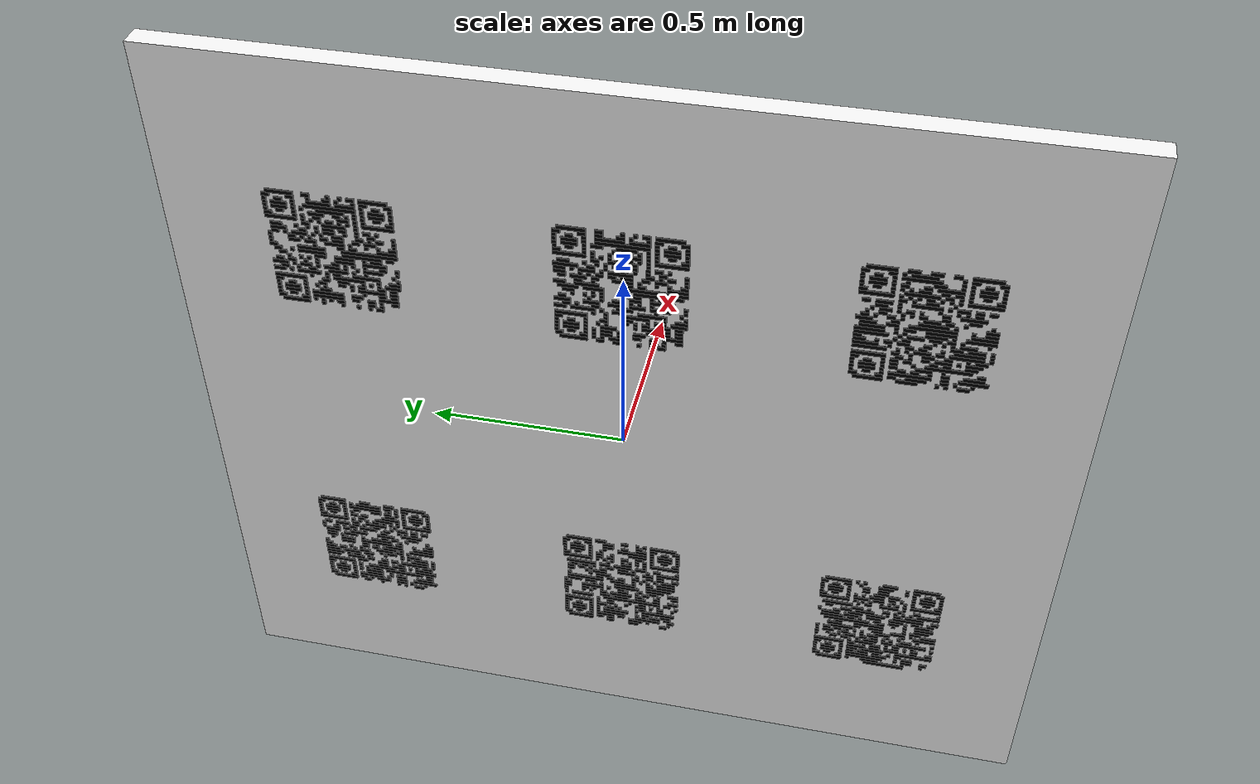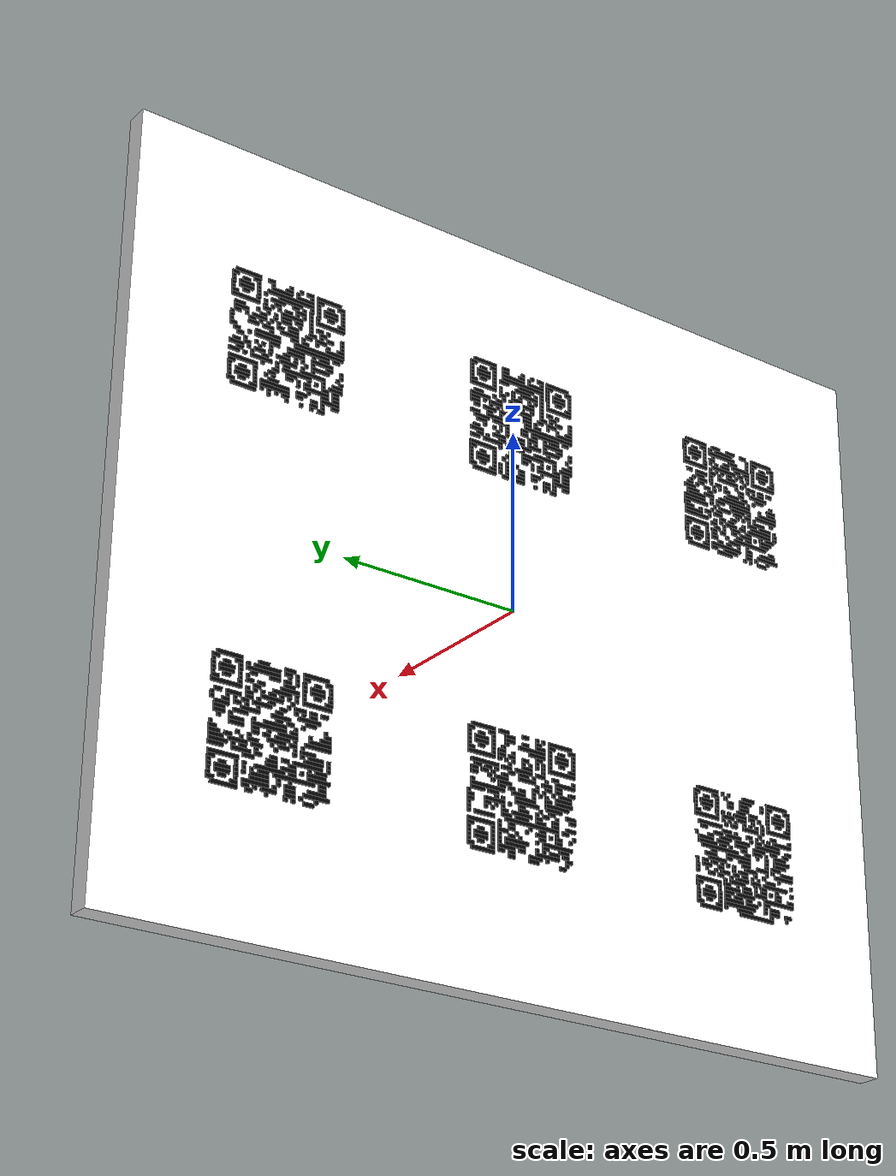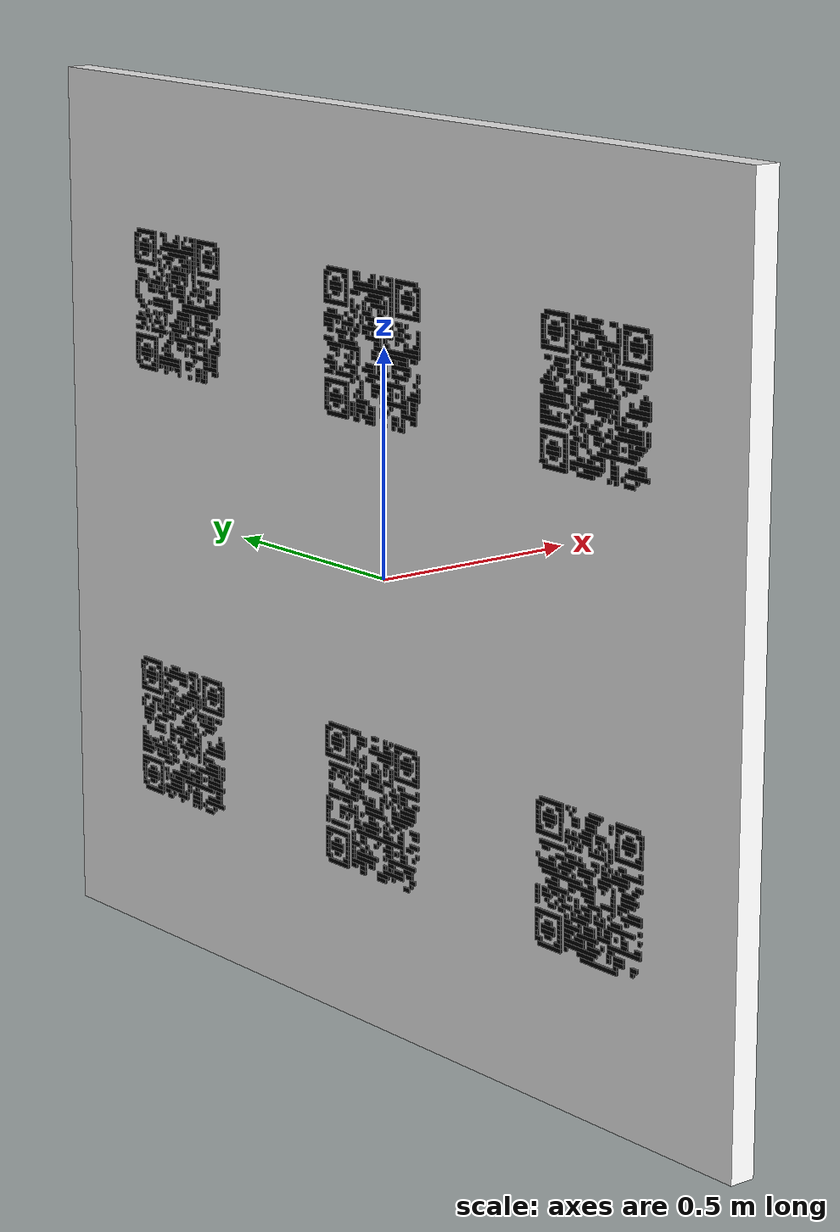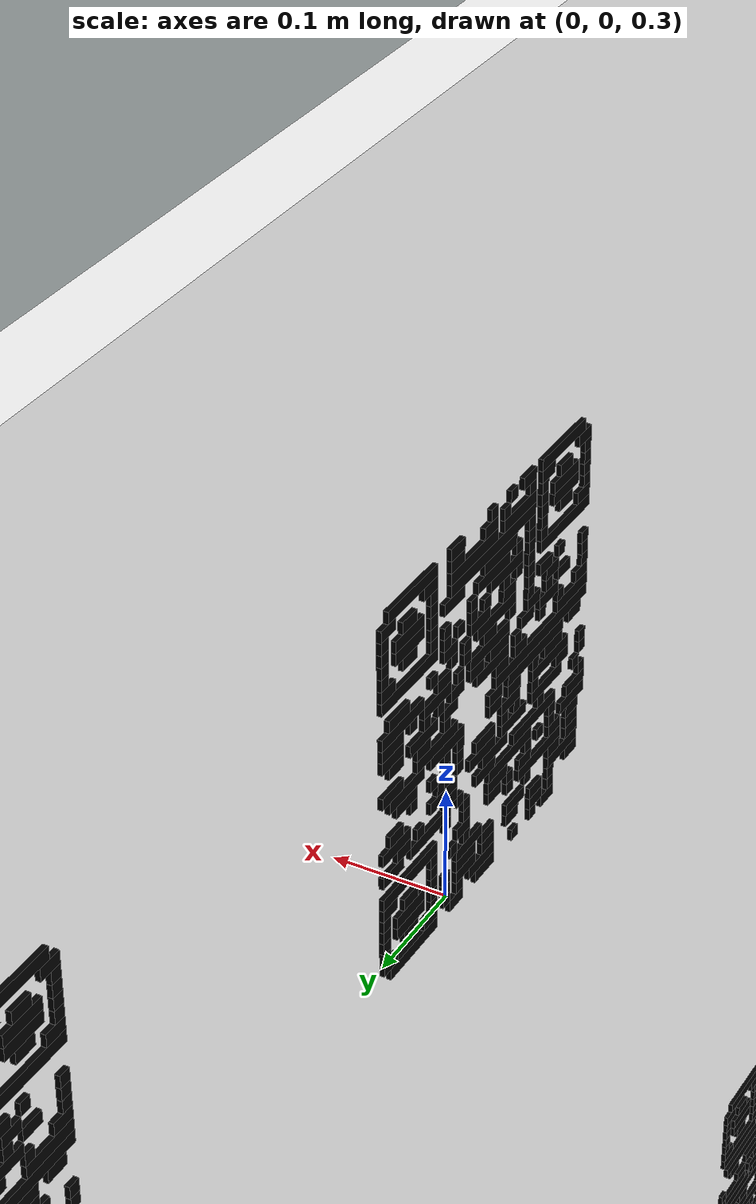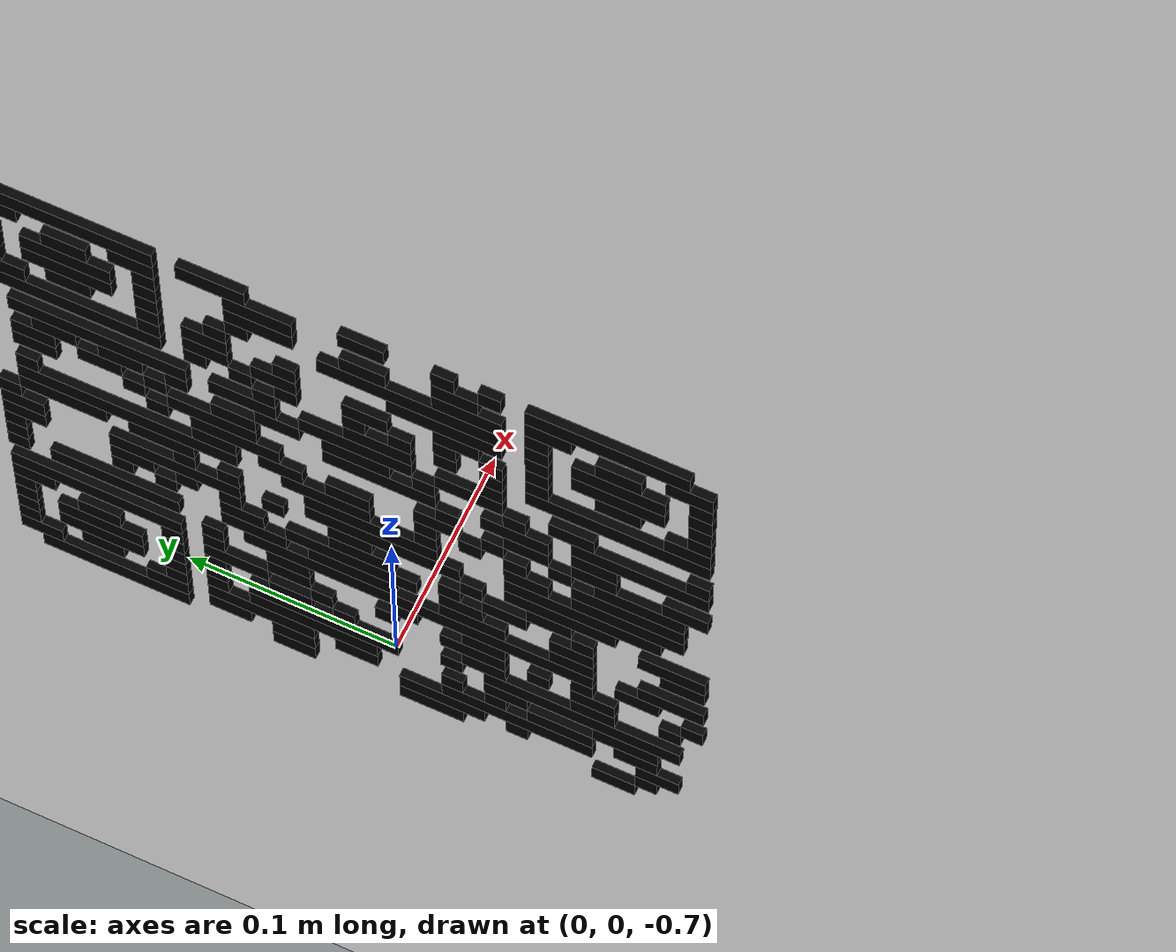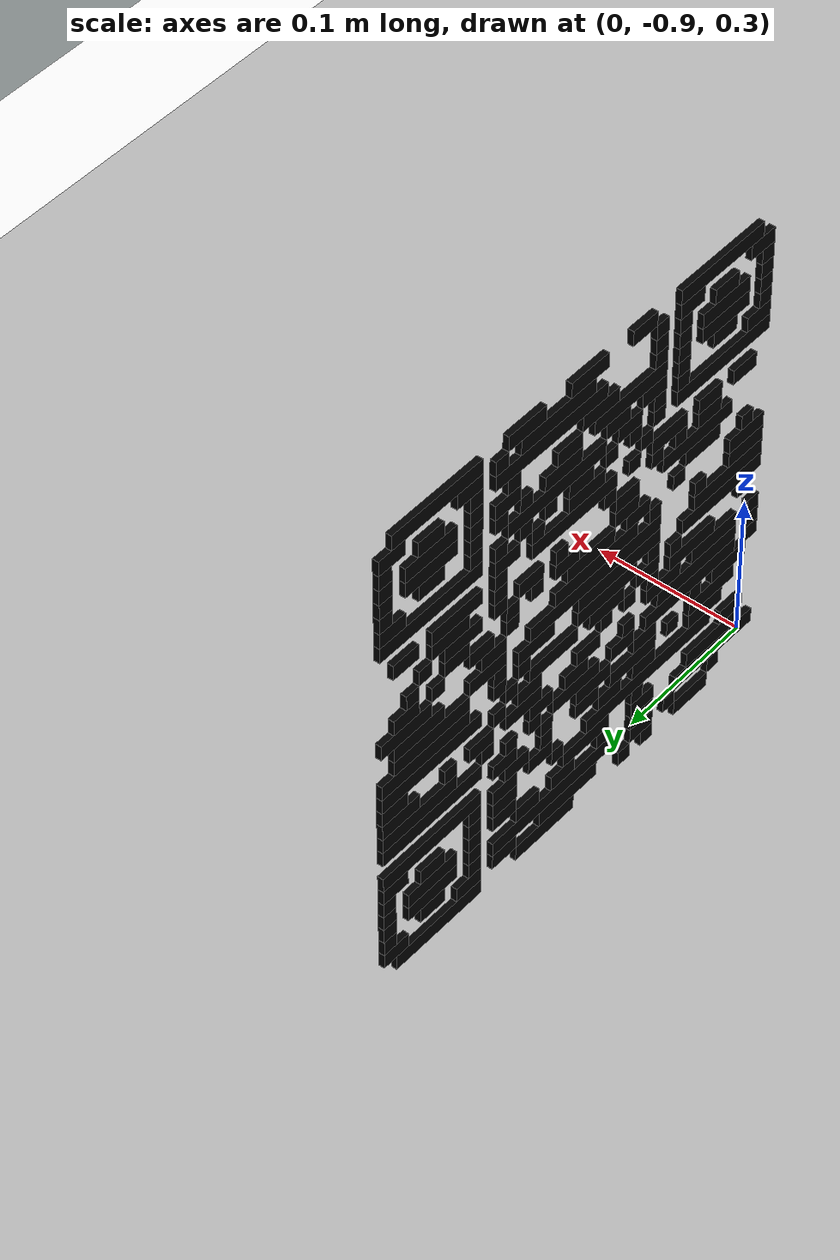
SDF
<?xml version="1.0"?>
<sdf version="1.9">
  <model name="qr_whiteboard">
    <static>true</static>
    <link name="board">

      <collision name="board_collision">
        <geometry>
          <box>
            <size>0.06 2.25 2.0</size>
          </box>
        </geometry>
      </collision>

      <visual name="board_body">
        <geometry>
          <box>
            <size>0.06 2.25 2.0</size>
          </box>
        </geometry>
        <material>
          <ambient>1 1 1 1</ambient>
          <diffuse>1 1 1 1</diffuse>
          <specular>0.05 0.05 0.05 1</specular>
        </material>
      </visual>

      <visual name="QR_A_black_0">
        <pose>-0.03400 0.81500 0.65500 0 0 0</pose>
        <geometry>
          <box>
            <size>0.004 0.07000 0.01000</size>
          </box>
        </geometry>
        <material>
          <ambient>0 0 0 1</ambient>
          <diffuse>0 0 0 1</diffuse>
          <specular>0 0 0 1</specular>
        </material>
      </visual>

      <visual name="QR_A_black_1">
        <pose>-0.03400 0.75000 0.65500 0 0 0</pose>
        <geometry>
          <box>
            <size>0.004 0.02000 0.01000</size>
          </box>
        </geometry>
        <material>
          <ambient>0 0 0 1</ambient>
          <diffuse>0 0 0 1</diffuse>
          <specular>0 0 0 1</specular>
        </material>
      </visual>

      <visual name="QR_A_black_2">
        <pose>-0.03400 0.69500 0.65500 0 0 0</pose>
        <geometry>
          <box>
            <size>0.004 0.01000 0.01000</size>
          </box>
        </geometry>
        <material>
          <ambient>0 0 0 1</ambient>
          <diffuse>0 0 0 1</diffuse>
          <specular>0 0 0 1</specular>
        </material>
      </visual>

      <visual name="QR_A_black_3">
        <pose>-0.03400 0.66500 0.65500 0 0 0</pose>
        <geometry>
          <box>
            <size>0.004 0.01000 0.01000</size>
          </box>
        </geometry>
        <material>
          <ambient>0 0 0 1</ambient>
          <diffuse>0 0 0 1</diffuse>
          <specular>0 0 0 1</specular>
        </material>
      </visual>

      <visual name="QR_A_black_4">
        <pose>-0.03400 0.64000 0.65500 0 0 0</pose>
        <geometry>
          <box>
            <size>0.004 0.02000 0.01000</size>
          </box>
        </geometry>
        <material>
          <ambient>0 0 0 1</ambient>
          <diffuse>0 0 0 1</diffuse>
          <specular>0 0 0 1</specular>
        </material>
      </visual>

      <visual name="QR_A_black_5">
        <pose>-0.03400 0.58500 0.65500 0 0 0</pose>
        <geometry>
          <box>
            <size>0.004 0.07000 0.01000</size>
          </box>
        </geometry>
        <material>
          <ambient>0 0 0 1</ambient>
          <diffuse>0 0 0 1</diffuse>
          <specular>0 0 0 1</specular>
        </material>
      </visual>

      <visual name="QR_A_black_6">
        <pose>-0.03400 0.85000 0.64500 0 0 0</pose>
        <geometry>
          <box>
            <size>0.004 0.02000 0.01000</size>
          </box>
        </geometry>
        <material>
          <ambient>0 0 0 1</ambient>
          <diffuse>0 0 0 1</diffuse>
          <specular>0 0 0 1</specular>
        </material>
      </visual>

      <visual name="QR_A_black_7">
        <pose>-0.03400 0.79000 0.64500 0 0 0</pose>
        <geometry>
          <box>
            <size>0.004 0.02000 0.01000</size>
          </box>
        </geometry>
        <material>
          <ambient>0 0 0 1</ambient>
          <diffuse>0 0 0 1</diffuse>
          <specular>0 0 0 1</specular>
        </material>
      </visual>

      <visual name="QR_A_black_8">
        <pose>-0.03400 0.74500 0.64500 0 0 0</pose>
        <geometry>
          <box>
            <size>0.004 0.01000 0.01000</size>
          </box>
        </geometry>
        <material>
          <ambient>0 0 0 1</ambient>
          <diffuse>0 0 0 1</diffuse>
          <specular>0 0 0 1</specular>
        </material>
      </visual>

      <visual name="QR_A_black_9">
        <pose>-0.03400 0.70000 0.64500 0 0 0</pose>
        <geometry>
          <box>
            <size>0.004 0.02000 0.01000</size>
          </box>
        </geometry>
        <material>
          <ambient>0 0 0 1</ambient>
          <diffuse>0 0 0 1</diffuse>
          <specular>0 0 0 1</specular>
        </material>
      </visual>

      <visual name="QR_A_black_10">
        <pose>-0.03400 0.67500 0.64500 0 0 0</pose>
        <geometry>
          <box>
            <size>0.004 0.01000 0.01000</size>
          </box>
        </geometry>
        <material>
          <ambient>0 0 0 1</ambient>
          <diffuse>0 0 0 1</diffuse>
          <specular>0 0 0 1</specular>
        </material>
      </visual>

      <visual name="QR_A_black_11">
        <pose>-0.03400 0.63500 0.64500 0 0 0</pose>
        <geometry>
          <box>
            <size>0.004 0.01000 0.01000</size>
          </box>
        </geometry>
        <material>
          <ambient>0 0 0 1</ambient>
          <diffuse>0 0 0 1</diffuse>
          <specular>0 0 0 1</specular>
        </material>
      </visual>

      <visual name="QR_A_black_12">
        <pose>-0.03400 0.61000 0.64500 0 0 0</pose>
        <geometry>
          <box>
            <size>0.004 0.02000 0.01000</size>
          </box>
        </geometry>
        <material>
          <ambient>0 0 0 1</ambient>
          <diffuse>0 0 0 1</diffuse>
          <specular>0 0 0 1</specular>
        </material>
      </visual>

      <visual name="QR_A_black_13">
        <pose>-0.03400 0.55000 0.64500 0 0 0</pose>
        <geometry>
          <box>
            <size>0.004 0.02000 0.01000</size>
          </box>
        </geometry>
        <material>
          <ambient>0 0 0 1</ambient>
          <diffuse>0 0 0 1</diffuse>
          <specular>0 0 0 1</specular>
        </material>
      </visual>

      <visual name="QR_A_black_14">
        <pose>-0.03400 0.85500 0.63500 0 0 0</pose>
        <geometry>
          <box>
            <size>0.004 0.01000 0.01000</size>
          </box>
        </geometry>
        <material>
          <ambient>0 0 0 1</ambient>
          <diffuse>0 0 0 1</diffuse>
          <specular>0 0 0 1</specular>
        </material>
      </visual>

      <visual name="QR_A_black_15">
        <pose>-0.03400 0.82000 0.63500 0 0 0</pose>
        <geometry>
          <box>
            <size>0.004 0.02000 0.01000</size>
          </box>
        </geometry>
        <material>
          <ambient>0 0 0 1</ambient>
          <diffuse>0 0 0 1</diffuse>
          <specular>0 0 0 1</specular>
        </material>
      </visual>

      <visual name="QR_A_black_16">
        <pose>-0.03400 0.78500 0.63500 0 0 0</pose>
        <geometry>
          <box>
            <size>0.004 0.01000 0.01000</size>
          </box>
        </geometry>
        <material>
          <ambient>0 0 0 1</ambient>
          <diffuse>0 0 0 1</diffuse>
          <specular>0 0 0 1</specular>
        </material>
      </visual>

      <visual name="QR_A_black_17">
        <pose>-0.03400 0.72000 0.63500 0 0 0</pose>
        <geometry>
          <box>
            <size>0.004 0.06000 0.01000</size>
          </box>
        </geometry>
        <material>
          <ambient>0 0 0 1</ambient>
          <diffuse>0 0 0 1</diffuse>
          <specular>0 0 0 1</specular>
        </material>
      </visual>

      <visual name="QR_A_black_18">
        <pose>-0.03400 0.65500 0.63500 0 0 0</pose>
        <geometry>
          <box>
            <size>0.004 0.05000 0.01000</size>
          </box>
        </geometry>
        <material>
          <ambient>0 0 0 1</ambient>
          <diffuse>0 0 0 1</diffuse>
          <specular>0 0 0 1</specular>
        </material>
      </visual>

      <visual name="QR_A_black_19">
        <pose>-0.03400 0.61500 0.63500 0 0 0</pose>
        <geometry>
          <box>
            <size>0.004 0.01000 0.01000</size>
          </box>
        </geometry>
        <material>
          <ambient>0 0 0 1</ambient>
          <diffuse>0 0 0 1</diffuse>
          <specular>0 0 0 1</specular>
        </material>
      </visual>

      <visual name="QR_A_black_20">
        <pose>-0.03400 0.58000 0.63500 0 0 0</pose>
        <geometry>
          <box>
            <size>0.004 0.02000 0.01000</size>
          </box>
        </geometry>
        <material>
          <ambient>0 0 0 1</ambient>
          <diffuse>0 0 0 1</diffuse>
          <specular>0 0 0 1</specular>
        </material>
      </visual>

      <visual name="QR_A_black_21">
        <pose>-0.03400 0.54500 0.63500 0 0 0</pose>
        <geometry>
          <box>
            <size>0.004 0.01000 0.01000</size>
          </box>
        </geometry>
        <material>
          <ambient>0 0 0 1</ambient>
          <diffuse>0 0 0 1</diffuse>
          <specular>0 0 0 1</specular>
        </material>
      </visual>

      <visual name="QR_A_black_22">
        <pose>-0.03400 0.85500 0.62500 0 0 0</pose>
        <geometry>
          <box>
            <size>0.004 0.01000 0.01000</size>
          </box>
        </geometry>
        <material>
          <ambient>0 0 0 1</ambient>
          <diffuse>0 0 0 1</diffuse>
          <specular>0 0 0 1</specular>
        </material>
      </visual>

      <visual name="QR_A_black_23">
        <pose>-0.03400 0.82000 0.62500 0 0 0</pose>
        <geometry>
          <box>
            <size>0.004 0.04000 0.01000</size>
          </box>
        </geometry>
        <material>
          <ambient>0 0 0 1</ambient>
          <diffuse>0 0 0 1</diffuse>
          <specular>0 0 0 1</specular>
        </material>
      </visual>

      <visual name="QR_A_black_24">
        <pose>-0.03400 0.78500 0.62500 0 0 0</pose>
        <geometry>
          <box>
            <size>0.004 0.01000 0.01000</size>
          </box>
        </geometry>
        <material>
          <ambient>0 0 0 1</ambient>
          <diffuse>0 0 0 1</diffuse>
          <specular>0 0 0 1</specular>
        </material>
      </visual>

      <visual name="QR_A_black_25">
        <pose>-0.03400 0.69500 0.62500 0 0 0</pose>
        <geometry>
          <box>
            <size>0.004 0.13000 0.01000</size>
          </box>
        </geometry>
        <material>
          <ambient>0 0 0 1</ambient>
          <diffuse>0 0 0 1</diffuse>
          <specular>0 0 0 1</specular>
        </material>
      </visual>

      <visual name="QR_A_black_26">
        <pose>-0.03400 0.61500 0.62500 0 0 0</pose>
        <geometry>
          <box>
            <size>0.004 0.01000 0.01000</size>
          </box>
        </geometry>
        <material>
          <ambient>0 0 0 1</ambient>
          <diffuse>0 0 0 1</diffuse>
          <specular>0 0 0 1</specular>
        </material>
      </visual>

      <visual name="QR_A_black_27">
        <pose>-0.03400 0.58000 0.62500 0 0 0</pose>
        <geometry>
          <box>
            <size>0.004 0.04000 0.01000</size>
          </box>
        </geometry>
        <material>
          <ambient>0 0 0 1</ambient>
          <diffuse>0 0 0 1</diffuse>
          <specular>0 0 0 1</specular>
        </material>
      </visual>

      <visual name="QR_A_black_28">
        <pose>-0.03400 0.54500 0.62500 0 0 0</pose>
        <geometry>
          <box>
            <size>0.004 0.01000 0.01000</size>
          </box>
        </geometry>
        <material>
          <ambient>0 0 0 1</ambient>
          <diffuse>0 0 0 1</diffuse>
          <specular>0 0 0 1</specular>
        </material>
      </visual>

      <visual name="QR_A_black_29">
        <pose>-0.03400 0.85500 0.61500 0 0 0</pose>
        <geometry>
          <box>
            <size>0.004 0.01000 0.01000</size>
          </box>
        </geometry>
        <material>
          <ambient>0 0 0 1</ambient>
          <diffuse>0 0 0 1</diffuse>
          <specular>0 0 0 1</specular>
        </material>
      </visual>

      <visual name="QR_A_black_30">
        <pose>-0.03400 0.82000 0.61500 0 0 0</pose>
        <geometry>
          <box>
            <size>0.004 0.04000 0.01000</size>
          </box>
        </geometry>
        <material>
          <ambient>0 0 0 1</ambient>
          <diffuse>0 0 0 1</diffuse>
          <specular>0 0 0 1</specular>
        </material>
      </visual>

      <visual name="QR_A_black_31">
        <pose>-0.03400 0.78500 0.61500 0 0 0</pose>
        <geometry>
          <box>
            <size>0.004 0.01000 0.01000</size>
          </box>
        </geometry>
        <material>
          <ambient>0 0 0 1</ambient>
          <diffuse>0 0 0 1</diffuse>
          <specular>0 0 0 1</specular>
        </material>
      </visual>

      <visual name="QR_A_black_32">
        <pose>-0.03400 0.76500 0.61500 0 0 0</pose>
        <geometry>
          <box>
            <size>0.004 0.01000 0.01000</size>
          </box>
        </geometry>
        <material>
          <ambient>0 0 0 1</ambient>
          <diffuse>0 0 0 1</diffuse>
          <specular>0 0 0 1</specular>
        </material>
      </visual>

      <visual name="QR_A_black_33">
        <pose>-0.03400 0.69500 0.61500 0 0 0</pose>
        <geometry>
          <box>
            <size>0.004 0.07000 0.01000</size>
          </box>
        </geometry>
        <material>
          <ambient>0 0 0 1</ambient>
          <diffuse>0 0 0 1</diffuse>
          <specular>0 0 0 1</specular>
        </material>
      </visual>

      <visual name="QR_A_black_34">
        <pose>-0.03400 0.63500 0.61500 0 0 0</pose>
        <geometry>
          <box>
            <size>0.004 0.01000 0.01000</size>
          </box>
        </geometry>
        <material>
          <ambient>0 0 0 1</ambient>
          <diffuse>0 0 0 1</diffuse>
          <specular>0 0 0 1</specular>
        </material>
      </visual>

      <visual name="QR_A_black_35">
        <pose>-0.03400 0.61500 0.61500 0 0 0</pose>
        <geometry>
          <box>
            <size>0.004 0.01000 0.01000</size>
          </box>
        </geometry>
        <material>
          <ambient>0 0 0 1</ambient>
          <diffuse>0 0 0 1</diffuse>
          <specular>0 0 0 1</specular>
        </material>
      </visual>

      <visual name="QR_A_black_36">
        <pose>-0.03400 0.58000 0.61500 0 0 0</pose>
        <geometry>
          <box>
            <size>0.004 0.04000 0.01000</size>
          </box>
        </geometry>
        <material>
          <ambient>0 0 0 1</ambient>
          <diffuse>0 0 0 1</diffuse>
          <specular>0 0 0 1</specular>
        </material>
      </visual>

      <visual name="QR_A_black_37">
        <pose>-0.03400 0.54500 0.61500 0 0 0</pose>
        <geometry>
          <box>
            <size>0.004 0.01000 0.01000</size>
          </box>
        </geometry>
        <material>
          <ambient>0 0 0 1</ambient>
          <diffuse>0 0 0 1</diffuse>
          <specular>0 0 0 1</specular>
        </material>
      </visual>

      <visual name="QR_A_black_38">
        <pose>-0.03400 0.85500 0.60500 0 0 0</pose>
        <geometry>
          <box>
            <size>0.004 0.01000 0.01000</size>
          </box>
        </geometry>
        <material>
          <ambient>0 0 0 1</ambient>
          <diffuse>0 0 0 1</diffuse>
          <specular>0 0 0 1</specular>
        </material>
      </visual>

      <visual name="QR_A_black_39">
        <pose>-0.03400 0.82000 0.60500 0 0 0</pose>
        <geometry>
          <box>
            <size>0.004 0.02000 0.01000</size>
          </box>
        </geometry>
        <material>
          <ambient>0 0 0 1</ambient>
          <diffuse>0 0 0 1</diffuse>
          <specular>0 0 0 1</specular>
        </material>
      </visual>

      <visual name="QR_A_black_40">
        <pose>-0.03400 0.78500 0.60500 0 0 0</pose>
        <geometry>
          <box>
            <size>0.004 0.01000 0.01000</size>
          </box>
        </geometry>
        <material>
          <ambient>0 0 0 1</ambient>
          <diffuse>0 0 0 1</diffuse>
          <specular>0 0 0 1</specular>
        </material>
      </visual>

      <visual name="QR_A_black_41">
        <pose>-0.03400 0.73000 0.60500 0 0 0</pose>
        <geometry>
          <box>
            <size>0.004 0.04000 0.01000</size>
          </box>
        </geometry>
        <material>
          <ambient>0 0 0 1</ambient>
          <diffuse>0 0 0 1</diffuse>
          <specular>0 0 0 1</specular>
        </material>
      </visual>

      <visual name="QR_A_black_42">
        <pose>-0.03400 0.68000 0.60500 0 0 0</pose>
        <geometry>
          <box>
            <size>0.004 0.02000 0.01000</size>
          </box>
        </geometry>
        <material>
          <ambient>0 0 0 1</ambient>
          <diffuse>0 0 0 1</diffuse>
          <specular>0 0 0 1</specular>
        </material>
      </visual>

      <visual name="QR_A_black_43">
        <pose>-0.03400 0.65500 0.60500 0 0 0</pose>
        <geometry>
          <box>
            <size>0.004 0.01000 0.01000</size>
          </box>
        </geometry>
        <material>
          <ambient>0 0 0 1</ambient>
          <diffuse>0 0 0 1</diffuse>
          <specular>0 0 0 1</specular>
        </material>
      </visual>

      <visual name="QR_A_black_44">
        <pose>-0.03400 0.63500 0.60500 0 0 0</pose>
        <geometry>
          <box>
            <size>0.004 0.01000 0.01000</size>
          </box>
        </geometry>
        <material>
          <ambient>0 0 0 1</ambient>
          <diffuse>0 0 0 1</diffuse>
          <specular>0 0 0 1</specular>
        </material>
      </visual>

      <visual name="QR_A_black_45">
        <pose>-0.03400 0.61500 0.60500 0 0 0</pose>
        <geometry>
          <box>
            <size>0.004 0.01000 0.01000</size>
          </box>
        </geometry>
        <material>
          <ambient>0 0 0 1</ambient>
          <diffuse>0 0 0 1</diffuse>
          <specular>0 0 0 1</specular>
        </material>
      </visual>

      <visual name="QR_A_black_46">
        <pose>-0.03400 0.58000 0.60500 0 0 0</pose>
        <geometry>
          <box>
            <size>0.004 0.02000 0.01000</size>
          </box>
        </geometry>
        <material>
          <ambient>0 0 0 1</ambient>
          <diffuse>0 0 0 1</diffuse>
          <specular>0 0 0 1</specular>
        </material>
      </visual>

      <visual name="QR_A_black_47">
        <pose>-0.03400 0.54500 0.60500 0 0 0</pose>
        <geometry>
          <box>
            <size>0.004 0.01000 0.01000</size>
          </box>
        </geometry>
        <material>
          <ambient>0 0 0 1</ambient>
          <diffuse>0 0 0 1</diffuse>
          <specular>0 0 0 1</specular>
        </material>
      </visual>

      <visual name="QR_A_black_48">
        <pose>-0.03400 0.85000 0.59500 0 0 0</pose>
        <geometry>
          <box>
            <size>0.004 0.02000 0.01000</size>
          </box>
        </geometry>
        <material>
          <ambient>0 0 0 1</ambient>
          <diffuse>0 0 0 1</diffuse>
          <specular>0 0 0 1</specular>
        </material>
      </visual>

      <visual name="QR_A_black_49">
        <pose>-0.03400 0.78500 0.59500 0 0 0</pose>
        <geometry>
          <box>
            <size>0.004 0.01000 0.01000</size>
          </box>
        </geometry>
        <material>
          <ambient>0 0 0 1</ambient>
          <diffuse>0 0 0 1</diffuse>
          <specular>0 0 0 1</specular>
        </material>
      </visual>

      <visual name="QR_A_black_50">
        <pose>-0.03400 0.76500 0.59500 0 0 0</pose>
        <geometry>
          <box>
            <size>0.004 0.01000 0.01000</size>
          </box>
        </geometry>
        <material>
          <ambient>0 0 0 1</ambient>
          <diffuse>0 0 0 1</diffuse>
          <specular>0 0 0 1</specular>
        </material>
      </visual>

      <visual name="QR_A_black_51">
        <pose>-0.03400 0.73000 0.59500 0 0 0</pose>
        <geometry>
          <box>
            <size>0.004 0.02000 0.01000</size>
          </box>
        </geometry>
        <material>
          <ambient>0 0 0 1</ambient>
          <diffuse>0 0 0 1</diffuse>
          <specular>0 0 0 1</specular>
        </material>
      </visual>

      <visual name="QR_A_black_52">
        <pose>-0.03400 0.66500 0.59500 0 0 0</pose>
        <geometry>
          <box>
            <size>0.004 0.03000 0.01000</size>
          </box>
        </geometry>
        <material>
          <ambient>0 0 0 1</ambient>
          <diffuse>0 0 0 1</diffuse>
          <specular>0 0 0 1</specular>
        </material>
      </visual>

      <visual name="QR_A_black_53">
        <pose>-0.03400 0.63500 0.59500 0 0 0</pose>
        <geometry>
          <box>
            <size>0.004 0.01000 0.01000</size>
          </box>
        </geometry>
        <material>
          <ambient>0 0 0 1</ambient>
          <diffuse>0 0 0 1</diffuse>
          <specular>0 0 0 1</specular>
        </material>
      </visual>

      <visual name="QR_A_black_54">
        <pose>-0.03400 0.61500 0.59500 0 0 0</pose>
        <geometry>
          <box>
            <size>0.004 0.01000 0.01000</size>
          </box>
        </geometry>
        <material>
          <ambient>0 0 0 1</ambient>
          <diffuse>0 0 0 1</diffuse>
          <specular>0 0 0 1</specular>
        </material>
      </visual>

      <visual name="QR_A_black_55">
        <pose>-0.03400 0.55000 0.59500 0 0 0</pose>
        <geometry>
          <box>
            <size>0.004 0.02000 0.01000</size>
          </box>
        </geometry>
        <material>
          <ambient>0 0 0 1</ambient>
          <diffuse>0 0 0 1</diffuse>
          <specular>0 0 0 1</specular>
        </material>
      </visual>

      <visual name="QR_A_black_56">
        <pose>-0.03400 0.82000 0.58500 0 0 0</pose>
        <geometry>
          <box>
            <size>0.004 0.08000 0.01000</size>
          </box>
        </geometry>
        <material>
          <ambient>0 0 0 1</ambient>
          <diffuse>0 0 0 1</diffuse>
          <specular>0 0 0 1</specular>
        </material>
      </visual>

      <visual name="QR_A_black_57">
        <pose>-0.03400 0.76500 0.58500 0 0 0</pose>
        <geometry>
          <box>
            <size>0.004 0.01000 0.01000</size>
          </box>
        </geometry>
        <material>
          <ambient>0 0 0 1</ambient>
          <diffuse>0 0 0 1</diffuse>
          <specular>0 0 0 1</specular>
        </material>
      </visual>

      <visual name="QR_A_black_58">
        <pose>-0.03400 0.74500 0.58500 0 0 0</pose>
        <geometry>
          <box>
            <size>0.004 0.01000 0.01000</size>
          </box>
        </geometry>
        <material>
          <ambient>0 0 0 1</ambient>
          <diffuse>0 0 0 1</diffuse>
          <specular>0 0 0 1</specular>
        </material>
      </visual>

      <visual name="QR_A_black_59">
        <pose>-0.03400 0.72500 0.58500 0 0 0</pose>
        <geometry>
          <box>
            <size>0.004 0.01000 0.01000</size>
          </box>
        </geometry>
        <material>
          <ambient>0 0 0 1</ambient>
          <diffuse>0 0 0 1</diffuse>
          <specular>0 0 0 1</specular>
        </material>
      </visual>

      <visual name="QR_A_black_60">
        <pose>-0.03400 0.70000 0.58500 0 0 0</pose>
        <geometry>
          <box>
            <size>0.004 0.02000 0.01000</size>
          </box>
        </geometry>
        <material>
          <ambient>0 0 0 1</ambient>
          <diffuse>0 0 0 1</diffuse>
          <specular>0 0 0 1</specular>
        </material>
      </visual>

      <visual name="QR_A_black_61">
        <pose>-0.03400 0.67500 0.58500 0 0 0</pose>
        <geometry>
          <box>
            <size>0.004 0.01000 0.01000</size>
          </box>
        </geometry>
        <material>
          <ambient>0 0 0 1</ambient>
          <diffuse>0 0 0 1</diffuse>
          <specular>0 0 0 1</specular>
        </material>
      </visual>

      <visual name="QR_A_black_62">
        <pose>-0.03400 0.65500 0.58500 0 0 0</pose>
        <geometry>
          <box>
            <size>0.004 0.01000 0.01000</size>
          </box>
        </geometry>
        <material>
          <ambient>0 0 0 1</ambient>
          <diffuse>0 0 0 1</diffuse>
          <specular>0 0 0 1</specular>
        </material>
      </visual>

      <visual name="QR_A_black_63">
        <pose>-0.03400 0.63500 0.58500 0 0 0</pose>
        <geometry>
          <box>
            <size>0.004 0.01000 0.01000</size>
          </box>
        </geometry>
        <material>
          <ambient>0 0 0 1</ambient>
          <diffuse>0 0 0 1</diffuse>
          <specular>0 0 0 1</specular>
        </material>
      </visual>

      <visual name="QR_A_black_64">
        <pose>-0.03400 0.58000 0.58500 0 0 0</pose>
        <geometry>
          <box>
            <size>0.004 0.08000 0.01000</size>
          </box>
        </geometry>
        <material>
          <ambient>0 0 0 1</ambient>
          <diffuse>0 0 0 1</diffuse>
          <specular>0 0 0 1</specular>
        </material>
      </visual>

      <visual name="QR_A_black_65">
        <pose>-0.03400 0.76000 0.57500 0 0 0</pose>
        <geometry>
          <box>
            <size>0.004 0.02000 0.01000</size>
          </box>
        </geometry>
        <material>
          <ambient>0 0 0 1</ambient>
          <diffuse>0 0 0 1</diffuse>
          <specular>0 0 0 1</specular>
        </material>
      </visual>

      <visual name="QR_A_black_66">
        <pose>-0.03400 0.69000 0.57500 0 0 0</pose>
        <geometry>
          <box>
            <size>0.004 0.06000 0.01000</size>
          </box>
        </geometry>
        <material>
          <ambient>0 0 0 1</ambient>
          <diffuse>0 0 0 1</diffuse>
          <specular>0 0 0 1</specular>
        </material>
      </visual>

      <visual name="QR_A_black_67">
        <pose>-0.03400 0.63500 0.57500 0 0 0</pose>
        <geometry>
          <box>
            <size>0.004 0.01000 0.01000</size>
          </box>
        </geometry>
        <material>
          <ambient>0 0 0 1</ambient>
          <diffuse>0 0 0 1</diffuse>
          <specular>0 0 0 1</specular>
        </material>
      </visual>

      <visual name="QR_A_black_68">
        <pose>-0.03400 0.83500 0.56500 0 0 0</pose>
        <geometry>
          <box>
            <size>0.004 0.03000 0.01000</size>
          </box>
        </geometry>
        <material>
          <ambient>0 0 0 1</ambient>
          <diffuse>0 0 0 1</diffuse>
          <specular>0 0 0 1</specular>
        </material>
      </visual>

      <visual name="QR_A_black_69">
        <pose>-0.03400 0.78500 0.56500 0 0 0</pose>
        <geometry>
          <box>
            <size>0.004 0.01000 0.01000</size>
          </box>
        </geometry>
        <material>
          <ambient>0 0 0 1</ambient>
          <diffuse>0 0 0 1</diffuse>
          <specular>0 0 0 1</specular>
        </material>
      </visual>

      <visual name="QR_A_black_70">
        <pose>-0.03400 0.75500 0.56500 0 0 0</pose>
        <geometry>
          <box>
            <size>0.004 0.01000 0.01000</size>
          </box>
        </geometry>
        <material>
          <ambient>0 0 0 1</ambient>
          <diffuse>0 0 0 1</diffuse>
          <specular>0 0 0 1</specular>
        </material>
      </visual>

      <visual name="QR_A_black_71">
        <pose>-0.03400 0.73500 0.56500 0 0 0</pose>
        <geometry>
          <box>
            <size>0.004 0.01000 0.01000</size>
          </box>
        </geometry>
        <material>
          <ambient>0 0 0 1</ambient>
          <diffuse>0 0 0 1</diffuse>
          <specular>0 0 0 1</specular>
        </material>
      </visual>

      <visual name="QR_A_black_72">
        <pose>-0.03400 0.70500 0.56500 0 0 0</pose>
        <geometry>
          <box>
            <size>0.004 0.03000 0.01000</size>
          </box>
        </geometry>
        <material>
          <ambient>0 0 0 1</ambient>
          <diffuse>0 0 0 1</diffuse>
          <specular>0 0 0 1</specular>
        </material>
      </visual>

      <visual name="QR_A_black_73">
        <pose>-0.03400 0.67000 0.56500 0 0 0</pose>
        <geometry>
          <box>
            <size>0.004 0.02000 0.01000</size>
          </box>
        </geometry>
        <material>
          <ambient>0 0 0 1</ambient>
          <diffuse>0 0 0 1</diffuse>
          <specular>0 0 0 1</specular>
        </material>
      </visual>

      <visual name="QR_A_black_74">
        <pose>-0.03400 0.63500 0.56500 0 0 0</pose>
        <geometry>
          <box>
            <size>0.004 0.01000 0.01000</size>
          </box>
        </geometry>
        <material>
          <ambient>0 0 0 1</ambient>
          <diffuse>0 0 0 1</diffuse>
          <specular>0 0 0 1</specular>
        </material>
      </visual>

      <visual name="QR_A_black_75">
        <pose>-0.03400 0.61000 0.56500 0 0 0</pose>
        <geometry>
          <box>
            <size>0.004 0.02000 0.01000</size>
          </box>
        </geometry>
        <material>
          <ambient>0 0 0 1</ambient>
          <diffuse>0 0 0 1</diffuse>
          <specular>0 0 0 1</specular>
        </material>
      </visual>

      <visual name="QR_A_black_76">
        <pose>-0.03400 0.58500 0.56500 0 0 0</pose>
        <geometry>
          <box>
            <size>0.004 0.01000 0.01000</size>
          </box>
        </geometry>
        <material>
          <ambient>0 0 0 1</ambient>
          <diffuse>0 0 0 1</diffuse>
          <specular>0 0 0 1</specular>
        </material>
      </visual>

      <visual name="QR_A_black_77">
        <pose>-0.03400 0.83000 0.55500 0 0 0</pose>
        <geometry>
          <box>
            <size>0.004 0.04000 0.01000</size>
          </box>
        </geometry>
        <material>
          <ambient>0 0 0 1</ambient>
          <diffuse>0 0 0 1</diffuse>
          <specular>0 0 0 1</specular>
        </material>
      </visual>

      <visual name="QR_A_black_78">
        <pose>-0.03400 0.77000 0.55500 0 0 0</pose>
        <geometry>
          <box>
            <size>0.004 0.02000 0.01000</size>
          </box>
        </geometry>
        <material>
          <ambient>0 0 0 1</ambient>
          <diffuse>0 0 0 1</diffuse>
          <specular>0 0 0 1</specular>
        </material>
      </visual>

      <visual name="QR_A_black_79">
        <pose>-0.03400 0.73500 0.55500 0 0 0</pose>
        <geometry>
          <box>
            <size>0.004 0.01000 0.01000</size>
          </box>
        </geometry>
        <material>
          <ambient>0 0 0 1</ambient>
          <diffuse>0 0 0 1</diffuse>
          <specular>0 0 0 1</specular>
        </material>
      </visual>

      <visual name="QR_A_black_80">
        <pose>-0.03400 0.70500 0.55500 0 0 0</pose>
        <geometry>
          <box>
            <size>0.004 0.03000 0.01000</size>
          </box>
        </geometry>
        <material>
          <ambient>0 0 0 1</ambient>
          <diffuse>0 0 0 1</diffuse>
          <specular>0 0 0 1</specular>
        </material>
      </visual>

      <visual name="QR_A_black_81">
        <pose>-0.03400 0.66500 0.55500 0 0 0</pose>
        <geometry>
          <box>
            <size>0.004 0.01000 0.01000</size>
          </box>
        </geometry>
        <material>
          <ambient>0 0 0 1</ambient>
          <diffuse>0 0 0 1</diffuse>
          <specular>0 0 0 1</specular>
        </material>
      </visual>

      <visual name="QR_A_black_82">
        <pose>-0.03400 0.63500 0.55500 0 0 0</pose>
        <geometry>
          <box>
            <size>0.004 0.01000 0.01000</size>
          </box>
        </geometry>
        <material>
          <ambient>0 0 0 1</ambient>
          <diffuse>0 0 0 1</diffuse>
          <specular>0 0 0 1</specular>
        </material>
      </visual>

      <visual name="QR_A_black_83">
        <pose>-0.03400 0.60000 0.55500 0 0 0</pose>
        <geometry>
          <box>
            <size>0.004 0.02000 0.01000</size>
          </box>
        </geometry>
        <material>
          <ambient>0 0 0 1</ambient>
          <diffuse>0 0 0 1</diffuse>
          <specular>0 0 0 1</specular>
        </material>
      </visual>

      <visual name="QR_A_black_84">
        <pose>-0.03400 0.54500 0.55500 0 0 0</pose>
        <geometry>
          <box>
            <size>0.004 0.01000 0.01000</size>
          </box>
        </geometry>
        <material>
          <ambient>0 0 0 1</ambient>
          <diffuse>0 0 0 1</diffuse>
          <specular>0 0 0 1</specular>
        </material>
      </visual>

      <visual name="QR_A_black_85">
        <pose>-0.03400 0.84000 0.54500 0 0 0</pose>
        <geometry>
          <box>
            <size>0.004 0.02000 0.01000</size>
          </box>
        </geometry>
        <material>
          <ambient>0 0 0 1</ambient>
          <diffuse>0 0 0 1</diffuse>
          <specular>0 0 0 1</specular>
        </material>
      </visual>

      <visual name="QR_A_black_86">
        <pose>-0.03400 0.81500 0.54500 0 0 0</pose>
        <geometry>
          <box>
            <size>0.004 0.01000 0.01000</size>
          </box>
        </geometry>
        <material>
          <ambient>0 0 0 1</ambient>
          <diffuse>0 0 0 1</diffuse>
          <specular>0 0 0 1</specular>
        </material>
      </visual>

      <visual name="QR_A_black_87">
        <pose>-0.03400 0.78000 0.54500 0 0 0</pose>
        <geometry>
          <box>
            <size>0.004 0.04000 0.01000</size>
          </box>
        </geometry>
        <material>
          <ambient>0 0 0 1</ambient>
          <diffuse>0 0 0 1</diffuse>
          <specular>0 0 0 1</specular>
        </material>
      </visual>

      <visual name="QR_A_black_88">
        <pose>-0.03400 0.74500 0.54500 0 0 0</pose>
        <geometry>
          <box>
            <size>0.004 0.01000 0.01000</size>
          </box>
        </geometry>
        <material>
          <ambient>0 0 0 1</ambient>
          <diffuse>0 0 0 1</diffuse>
          <specular>0 0 0 1</specular>
        </material>
      </visual>

      <visual name="QR_A_black_89">
        <pose>-0.03400 0.72500 0.54500 0 0 0</pose>
        <geometry>
          <box>
            <size>0.004 0.01000 0.01000</size>
          </box>
        </geometry>
        <material>
          <ambient>0 0 0 1</ambient>
          <diffuse>0 0 0 1</diffuse>
          <specular>0 0 0 1</specular>
        </material>
      </visual>

      <visual name="QR_A_black_90">
        <pose>-0.03400 0.68500 0.54500 0 0 0</pose>
        <geometry>
          <box>
            <size>0.004 0.03000 0.01000</size>
          </box>
        </geometry>
        <material>
          <ambient>0 0 0 1</ambient>
          <diffuse>0 0 0 1</diffuse>
          <specular>0 0 0 1</specular>
        </material>
      </visual>

      <visual name="QR_A_black_91">
        <pose>-0.03400 0.63000 0.54500 0 0 0</pose>
        <geometry>
          <box>
            <size>0.004 0.02000 0.01000</size>
          </box>
        </geometry>
        <material>
          <ambient>0 0 0 1</ambient>
          <diffuse>0 0 0 1</diffuse>
          <specular>0 0 0 1</specular>
        </material>
      </visual>

      <visual name="QR_A_black_92">
        <pose>-0.03400 0.60500 0.54500 0 0 0</pose>
        <geometry>
          <box>
            <size>0.004 0.01000 0.01000</size>
          </box>
        </geometry>
        <material>
          <ambient>0 0 0 1</ambient>
          <diffuse>0 0 0 1</diffuse>
          <specular>0 0 0 1</specular>
        </material>
      </visual>

      <visual name="QR_A_black_93">
        <pose>-0.03400 0.58000 0.54500 0 0 0</pose>
        <geometry>
          <box>
            <size>0.004 0.02000 0.01000</size>
          </box>
        </geometry>
        <material>
          <ambient>0 0 0 1</ambient>
          <diffuse>0 0 0 1</diffuse>
          <specular>0 0 0 1</specular>
        </material>
      </visual>

      <visual name="QR_A_black_94">
        <pose>-0.03400 0.54500 0.54500 0 0 0</pose>
        <geometry>
          <box>
            <size>0.004 0.01000 0.01000</size>
          </box>
        </geometry>
        <material>
          <ambient>0 0 0 1</ambient>
          <diffuse>0 0 0 1</diffuse>
          <specular>0 0 0 1</specular>
        </material>
      </visual>

      <visual name="QR_A_black_95">
        <pose>-0.03400 0.85500 0.53500 0 0 0</pose>
        <geometry>
          <box>
            <size>0.004 0.01000 0.01000</size>
          </box>
        </geometry>
        <material>
          <ambient>0 0 0 1</ambient>
          <diffuse>0 0 0 1</diffuse>
          <specular>0 0 0 1</specular>
        </material>
      </visual>

      <visual name="QR_A_black_96">
        <pose>-0.03400 0.80000 0.53500 0 0 0</pose>
        <geometry>
          <box>
            <size>0.004 0.02000 0.01000</size>
          </box>
        </geometry>
        <material>
          <ambient>0 0 0 1</ambient>
          <diffuse>0 0 0 1</diffuse>
          <specular>0 0 0 1</specular>
        </material>
      </visual>

      <visual name="QR_A_black_97">
        <pose>-0.03400 0.77500 0.53500 0 0 0</pose>
        <geometry>
          <box>
            <size>0.004 0.01000 0.01000</size>
          </box>
        </geometry>
        <material>
          <ambient>0 0 0 1</ambient>
          <diffuse>0 0 0 1</diffuse>
          <specular>0 0 0 1</specular>
        </material>
      </visual>

      <visual name="QR_A_black_98">
        <pose>-0.03400 0.75500 0.53500 0 0 0</pose>
        <geometry>
          <box>
            <size>0.004 0.01000 0.01000</size>
          </box>
        </geometry>
        <material>
          <ambient>0 0 0 1</ambient>
          <diffuse>0 0 0 1</diffuse>
          <specular>0 0 0 1</specular>
        </material>
      </visual>

      <visual name="QR_A_black_99">
        <pose>-0.03400 0.72000 0.53500 0 0 0</pose>
        <geometry>
          <box>
            <size>0.004 0.02000 0.01000</size>
          </box>
        </geometry>
        <material>
          <ambient>0 0 0 1</ambient>
          <diffuse>0 0 0 1</diffuse>
          <specular>0 0 0 1</specular>
        </material>
      </visual>

      <visual name="QR_A_black_100">
        <pose>-0.03400 0.68500 0.53500 0 0 0</pose>
        <geometry>
          <box>
            <size>0.004 0.03000 0.01000</size>
          </box>
        </geometry>
        <material>
          <ambient>0 0 0 1</ambient>
          <diffuse>0 0 0 1</diffuse>
          <specular>0 0 0 1</specular>
        </material>
      </visual>

      <visual name="QR_A_black_101">
        <pose>-0.03400 0.64000 0.53500 0 0 0</pose>
        <geometry>
          <box>
            <size>0.004 0.02000 0.01000</size>
          </box>
        </geometry>
        <material>
          <ambient>0 0 0 1</ambient>
          <diffuse>0 0 0 1</diffuse>
          <specular>0 0 0 1</specular>
        </material>
      </visual>

      <visual name="QR_A_black_102">
        <pose>-0.03400 0.60500 0.53500 0 0 0</pose>
        <geometry>
          <box>
            <size>0.004 0.03000 0.01000</size>
          </box>
        </geometry>
        <material>
          <ambient>0 0 0 1</ambient>
          <diffuse>0 0 0 1</diffuse>
          <specular>0 0 0 1</specular>
        </material>
      </visual>

      <visual name="QR_A_black_103">
        <pose>-0.03400 0.54500 0.53500 0 0 0</pose>
        <geometry>
          <box>
            <size>0.004 0.01000 0.01000</size>
          </box>
        </geometry>
        <material>
          <ambient>0 0 0 1</ambient>
          <diffuse>0 0 0 1</diffuse>
          <specular>0 0 0 1</specular>
        </material>
      </visual>

      <visual name="QR_A_black_104">
        <pose>-0.03400 0.85500 0.52500 0 0 0</pose>
        <geometry>
          <box>
            <size>0.004 0.01000 0.01000</size>
          </box>
        </geometry>
        <material>
          <ambient>0 0 0 1</ambient>
          <diffuse>0 0 0 1</diffuse>
          <specular>0 0 0 1</specular>
        </material>
      </visual>

      <visual name="QR_A_black_105">
        <pose>-0.03400 0.79500 0.52500 0 0 0</pose>
        <geometry>
          <box>
            <size>0.004 0.03000 0.01000</size>
          </box>
        </geometry>
        <material>
          <ambient>0 0 0 1</ambient>
          <diffuse>0 0 0 1</diffuse>
          <specular>0 0 0 1</specular>
        </material>
      </visual>

      <visual name="QR_A_black_106">
        <pose>-0.03400 0.75500 0.52500 0 0 0</pose>
        <geometry>
          <box>
            <size>0.004 0.03000 0.01000</size>
          </box>
        </geometry>
        <material>
          <ambient>0 0 0 1</ambient>
          <diffuse>0 0 0 1</diffuse>
          <specular>0 0 0 1</specular>
        </material>
      </visual>

      <visual name="QR_A_black_107">
        <pose>-0.03400 0.69500 0.52500 0 0 0</pose>
        <geometry>
          <box>
            <size>0.004 0.05000 0.01000</size>
          </box>
        </geometry>
        <material>
          <ambient>0 0 0 1</ambient>
          <diffuse>0 0 0 1</diffuse>
          <specular>0 0 0 1</specular>
        </material>
      </visual>

      <visual name="QR_A_black_108">
        <pose>-0.03400 0.65500 0.52500 0 0 0</pose>
        <geometry>
          <box>
            <size>0.004 0.01000 0.01000</size>
          </box>
        </geometry>
        <material>
          <ambient>0 0 0 1</ambient>
          <diffuse>0 0 0 1</diffuse>
          <specular>0 0 0 1</specular>
        </material>
      </visual>

      <visual name="QR_A_black_109">
        <pose>-0.03400 0.61500 0.52500 0 0 0</pose>
        <geometry>
          <box>
            <size>0.004 0.01000 0.01000</size>
          </box>
        </geometry>
        <material>
          <ambient>0 0 0 1</ambient>
          <diffuse>0 0 0 1</diffuse>
          <specular>0 0 0 1</specular>
        </material>
      </visual>

      <visual name="QR_A_black_110">
        <pose>-0.03400 0.58500 0.52500 0 0 0</pose>
        <geometry>
          <box>
            <size>0.004 0.01000 0.01000</size>
          </box>
        </geometry>
        <material>
          <ambient>0 0 0 1</ambient>
          <diffuse>0 0 0 1</diffuse>
          <specular>0 0 0 1</specular>
        </material>
      </visual>

      <visual name="QR_A_black_111">
        <pose>-0.03400 0.55000 0.52500 0 0 0</pose>
        <geometry>
          <box>
            <size>0.004 0.02000 0.01000</size>
          </box>
        </geometry>
        <material>
          <ambient>0 0 0 1</ambient>
          <diffuse>0 0 0 1</diffuse>
          <specular>0 0 0 1</specular>
        </material>
      </visual>

      <visual name="QR_A_black_112">
        <pose>-0.03400 0.85500 0.51500 0 0 0</pose>
        <geometry>
          <box>
            <size>0.004 0.01000 0.01000</size>
          </box>
        </geometry>
        <material>
          <ambient>0 0 0 1</ambient>
          <diffuse>0 0 0 1</diffuse>
          <specular>0 0 0 1</specular>
        </material>
      </visual>

      <visual name="QR_A_black_113">
        <pose>-0.03400 0.74500 0.51500 0 0 0</pose>
        <geometry>
          <box>
            <size>0.004 0.01000 0.01000</size>
          </box>
        </geometry>
        <material>
          <ambient>0 0 0 1</ambient>
          <diffuse>0 0 0 1</diffuse>
          <specular>0 0 0 1</specular>
        </material>
      </visual>

      <visual name="QR_A_black_114">
        <pose>-0.03400 0.68000 0.51500 0 0 0</pose>
        <geometry>
          <box>
            <size>0.004 0.02000 0.01000</size>
          </box>
        </geometry>
        <material>
          <ambient>0 0 0 1</ambient>
          <diffuse>0 0 0 1</diffuse>
          <specular>0 0 0 1</specular>
        </material>
      </visual>

      <visual name="QR_A_black_115">
        <pose>-0.03400 0.65000 0.51500 0 0 0</pose>
        <geometry>
          <box>
            <size>0.004 0.02000 0.01000</size>
          </box>
        </geometry>
        <material>
          <ambient>0 0 0 1</ambient>
          <diffuse>0 0 0 1</diffuse>
          <specular>0 0 0 1</specular>
        </material>
      </visual>

      <visual name="QR_A_black_116">
        <pose>-0.03400 0.56500 0.51500 0 0 0</pose>
        <geometry>
          <box>
            <size>0.004 0.05000 0.01000</size>
          </box>
        </geometry>
        <material>
          <ambient>0 0 0 1</ambient>
          <diffuse>0 0 0 1</diffuse>
          <specular>0 0 0 1</specular>
        </material>
      </visual>

      <visual name="QR_A_black_117">
        <pose>-0.03400 0.85000 0.50500 0 0 0</pose>
        <geometry>
          <box>
            <size>0.004 0.02000 0.01000</size>
          </box>
        </geometry>
        <material>
          <ambient>0 0 0 1</ambient>
          <diffuse>0 0 0 1</diffuse>
          <specular>0 0 0 1</specular>
        </material>
      </visual>

      <visual name="QR_A_black_118">
        <pose>-0.03400 0.75500 0.50500 0 0 0</pose>
        <geometry>
          <box>
            <size>0.004 0.07000 0.01000</size>
          </box>
        </geometry>
        <material>
          <ambient>0 0 0 1</ambient>
          <diffuse>0 0 0 1</diffuse>
          <specular>0 0 0 1</specular>
        </material>
      </visual>

      <visual name="QR_A_black_119">
        <pose>-0.03400 0.61000 0.50500 0 0 0</pose>
        <geometry>
          <box>
            <size>0.004 0.14000 0.01000</size>
          </box>
        </geometry>
        <material>
          <ambient>0 0 0 1</ambient>
          <diffuse>0 0 0 1</diffuse>
          <specular>0 0 0 1</specular>
        </material>
      </visual>

      <visual name="QR_A_black_120">
        <pose>-0.03400 0.84000 0.49500 0 0 0</pose>
        <geometry>
          <box>
            <size>0.004 0.02000 0.01000</size>
          </box>
        </geometry>
        <material>
          <ambient>0 0 0 1</ambient>
          <diffuse>0 0 0 1</diffuse>
          <specular>0 0 0 1</specular>
        </material>
      </visual>

      <visual name="QR_A_black_121">
        <pose>-0.03400 0.80500 0.49500 0 0 0</pose>
        <geometry>
          <box>
            <size>0.004 0.01000 0.01000</size>
          </box>
        </geometry>
        <material>
          <ambient>0 0 0 1</ambient>
          <diffuse>0 0 0 1</diffuse>
          <specular>0 0 0 1</specular>
        </material>
      </visual>

      <visual name="QR_A_black_122">
        <pose>-0.03400 0.75500 0.49500 0 0 0</pose>
        <geometry>
          <box>
            <size>0.004 0.07000 0.01000</size>
          </box>
        </geometry>
        <material>
          <ambient>0 0 0 1</ambient>
          <diffuse>0 0 0 1</diffuse>
          <specular>0 0 0 1</specular>
        </material>
      </visual>

      <visual name="QR_A_black_123">
        <pose>-0.03400 0.63000 0.49500 0 0 0</pose>
        <geometry>
          <box>
            <size>0.004 0.10000 0.01000</size>
          </box>
        </geometry>
        <material>
          <ambient>0 0 0 1</ambient>
          <diffuse>0 0 0 1</diffuse>
          <specular>0 0 0 1</specular>
        </material>
      </visual>

      <visual name="QR_A_black_124">
        <pose>-0.03400 0.56000 0.49500 0 0 0</pose>
        <geometry>
          <box>
            <size>0.004 0.02000 0.01000</size>
          </box>
        </geometry>
        <material>
          <ambient>0 0 0 1</ambient>
          <diffuse>0 0 0 1</diffuse>
          <specular>0 0 0 1</specular>
        </material>
      </visual>

      <visual name="QR_A_black_125">
        <pose>-0.03400 0.83000 0.48500 0 0 0</pose>
        <geometry>
          <box>
            <size>0.004 0.02000 0.01000</size>
          </box>
        </geometry>
        <material>
          <ambient>0 0 0 1</ambient>
          <diffuse>0 0 0 1</diffuse>
          <specular>0 0 0 1</specular>
        </material>
      </visual>

      <visual name="QR_A_black_126">
        <pose>-0.03400 0.73500 0.48500 0 0 0</pose>
        <geometry>
          <box>
            <size>0.004 0.03000 0.01000</size>
          </box>
        </geometry>
        <material>
          <ambient>0 0 0 1</ambient>
          <diffuse>0 0 0 1</diffuse>
          <specular>0 0 0 1</specular>
        </material>
      </visual>

      <visual name="QR_A_black_127">
        <pose>-0.03400 0.67500 0.48500 0 0 0</pose>
        <geometry>
          <box>
            <size>0.004 0.05000 0.01000</size>
          </box>
        </geometry>
        <material>
          <ambient>0 0 0 1</ambient>
          <diffuse>0 0 0 1</diffuse>
          <specular>0 0 0 1</specular>
        </material>
      </visual>

      <visual name="QR_A_black_128">
        <pose>-0.03400 0.62500 0.48500 0 0 0</pose>
        <geometry>
          <box>
            <size>0.004 0.01000 0.01000</size>
          </box>
        </geometry>
        <material>
          <ambient>0 0 0 1</ambient>
          <diffuse>0 0 0 1</diffuse>
          <specular>0 0 0 1</specular>
        </material>
      </visual>

      <visual name="QR_A_black_129">
        <pose>-0.03400 0.59500 0.48500 0 0 0</pose>
        <geometry>
          <box>
            <size>0.004 0.03000 0.01000</size>
          </box>
        </geometry>
        <material>
          <ambient>0 0 0 1</ambient>
          <diffuse>0 0 0 1</diffuse>
          <specular>0 0 0 1</specular>
        </material>
      </visual>

      <visual name="QR_A_black_130">
        <pose>-0.03400 0.81500 0.47500 0 0 0</pose>
        <geometry>
          <box>
            <size>0.004 0.01000 0.01000</size>
          </box>
        </geometry>
        <material>
          <ambient>0 0 0 1</ambient>
          <diffuse>0 0 0 1</diffuse>
          <specular>0 0 0 1</specular>
        </material>
      </visual>

      <visual name="QR_A_black_131">
        <pose>-0.03400 0.78500 0.47500 0 0 0</pose>
        <geometry>
          <box>
            <size>0.004 0.01000 0.01000</size>
          </box>
        </geometry>
        <material>
          <ambient>0 0 0 1</ambient>
          <diffuse>0 0 0 1</diffuse>
          <specular>0 0 0 1</specular>
        </material>
      </visual>

      <visual name="QR_A_black_132">
        <pose>-0.03400 0.76500 0.47500 0 0 0</pose>
        <geometry>
          <box>
            <size>0.004 0.01000 0.01000</size>
          </box>
        </geometry>
        <material>
          <ambient>0 0 0 1</ambient>
          <diffuse>0 0 0 1</diffuse>
          <specular>0 0 0 1</specular>
        </material>
      </visual>

      <visual name="QR_A_black_133">
        <pose>-0.03400 0.74500 0.47500 0 0 0</pose>
        <geometry>
          <box>
            <size>0.004 0.01000 0.01000</size>
          </box>
        </geometry>
        <material>
          <ambient>0 0 0 1</ambient>
          <diffuse>0 0 0 1</diffuse>
          <specular>0 0 0 1</specular>
        </material>
      </visual>

      <visual name="QR_A_black_134">
        <pose>-0.03400 0.67500 0.47500 0 0 0</pose>
        <geometry>
          <box>
            <size>0.004 0.05000 0.01000</size>
          </box>
        </geometry>
        <material>
          <ambient>0 0 0 1</ambient>
          <diffuse>0 0 0 1</diffuse>
          <specular>0 0 0 1</specular>
        </material>
      </visual>

      <visual name="QR_A_black_135">
        <pose>-0.03400 0.60000 0.47500 0 0 0</pose>
        <geometry>
          <box>
            <size>0.004 0.06000 0.01000</size>
          </box>
        </geometry>
        <material>
          <ambient>0 0 0 1</ambient>
          <diffuse>0 0 0 1</diffuse>
          <specular>0 0 0 1</specular>
        </material>
      </visual>

      <visual name="QR_A_black_136">
        <pose>-0.03400 0.84000 0.46500 0 0 0</pose>
        <geometry>
          <box>
            <size>0.004 0.02000 0.01000</size>
          </box>
        </geometry>
        <material>
          <ambient>0 0 0 1</ambient>
          <diffuse>0 0 0 1</diffuse>
          <specular>0 0 0 1</specular>
        </material>
      </visual>

      <visual name="QR_A_black_137">
        <pose>-0.03400 0.81000 0.46500 0 0 0</pose>
        <geometry>
          <box>
            <size>0.004 0.02000 0.01000</size>
          </box>
        </geometry>
        <material>
          <ambient>0 0 0 1</ambient>
          <diffuse>0 0 0 1</diffuse>
          <specular>0 0 0 1</specular>
        </material>
      </visual>

      <visual name="QR_A_black_138">
        <pose>-0.03400 0.77500 0.46500 0 0 0</pose>
        <geometry>
          <box>
            <size>0.004 0.01000 0.01000</size>
          </box>
        </geometry>
        <material>
          <ambient>0 0 0 1</ambient>
          <diffuse>0 0 0 1</diffuse>
          <specular>0 0 0 1</specular>
        </material>
      </visual>

      <visual name="QR_A_black_139">
        <pose>-0.03400 0.74500 0.46500 0 0 0</pose>
        <geometry>
          <box>
            <size>0.004 0.01000 0.01000</size>
          </box>
        </geometry>
        <material>
          <ambient>0 0 0 1</ambient>
          <diffuse>0 0 0 1</diffuse>
          <specular>0 0 0 1</specular>
        </material>
      </visual>

      <visual name="QR_A_black_140">
        <pose>-0.03400 0.70000 0.46500 0 0 0</pose>
        <geometry>
          <box>
            <size>0.004 0.02000 0.01000</size>
          </box>
        </geometry>
        <material>
          <ambient>0 0 0 1</ambient>
          <diffuse>0 0 0 1</diffuse>
          <specular>0 0 0 1</specular>
        </material>
      </visual>

      <visual name="QR_A_black_141">
        <pose>-0.03400 0.67500 0.46500 0 0 0</pose>
        <geometry>
          <box>
            <size>0.004 0.01000 0.01000</size>
          </box>
        </geometry>
        <material>
          <ambient>0 0 0 1</ambient>
          <diffuse>0 0 0 1</diffuse>
          <specular>0 0 0 1</specular>
        </material>
      </visual>

      <visual name="QR_A_black_142">
        <pose>-0.03400 0.65500 0.46500 0 0 0</pose>
        <geometry>
          <box>
            <size>0.004 0.01000 0.01000</size>
          </box>
        </geometry>
        <material>
          <ambient>0 0 0 1</ambient>
          <diffuse>0 0 0 1</diffuse>
          <specular>0 0 0 1</specular>
        </material>
      </visual>

      <visual name="QR_A_black_143">
        <pose>-0.03400 0.62500 0.46500 0 0 0</pose>
        <geometry>
          <box>
            <size>0.004 0.01000 0.01000</size>
          </box>
        </geometry>
        <material>
          <ambient>0 0 0 1</ambient>
          <diffuse>0 0 0 1</diffuse>
          <specular>0 0 0 1</specular>
        </material>
      </visual>

      <visual name="QR_A_black_144">
        <pose>-0.03400 0.58000 0.46500 0 0 0</pose>
        <geometry>
          <box>
            <size>0.004 0.02000 0.01000</size>
          </box>
        </geometry>
        <material>
          <ambient>0 0 0 1</ambient>
          <diffuse>0 0 0 1</diffuse>
          <specular>0 0 0 1</specular>
        </material>
      </visual>

      <visual name="QR_A_black_145">
        <pose>-0.03400 0.54500 0.46500 0 0 0</pose>
        <geometry>
          <box>
            <size>0.004 0.01000 0.01000</size>
          </box>
        </geometry>
        <material>
          <ambient>0 0 0 1</ambient>
          <diffuse>0 0 0 1</diffuse>
          <specular>0 0 0 1</specular>
        </material>
      </visual>

      <visual name="QR_A_black_146">
        <pose>-0.03400 0.84000 0.45500 0 0 0</pose>
        <geometry>
          <box>
            <size>0.004 0.04000 0.01000</size>
          </box>
        </geometry>
        <material>
          <ambient>0 0 0 1</ambient>
          <diffuse>0 0 0 1</diffuse>
          <specular>0 0 0 1</specular>
        </material>
      </visual>

      <visual name="QR_A_black_147">
        <pose>-0.03400 0.80500 0.45500 0 0 0</pose>
        <geometry>
          <box>
            <size>0.004 0.01000 0.01000</size>
          </box>
        </geometry>
        <material>
          <ambient>0 0 0 1</ambient>
          <diffuse>0 0 0 1</diffuse>
          <specular>0 0 0 1</specular>
        </material>
      </visual>

      <visual name="QR_A_black_148">
        <pose>-0.03400 0.77500 0.45500 0 0 0</pose>
        <geometry>
          <box>
            <size>0.004 0.03000 0.01000</size>
          </box>
        </geometry>
        <material>
          <ambient>0 0 0 1</ambient>
          <diffuse>0 0 0 1</diffuse>
          <specular>0 0 0 1</specular>
        </material>
      </visual>

      <visual name="QR_A_black_149">
        <pose>-0.03400 0.74500 0.45500 0 0 0</pose>
        <geometry>
          <box>
            <size>0.004 0.01000 0.01000</size>
          </box>
        </geometry>
        <material>
          <ambient>0 0 0 1</ambient>
          <diffuse>0 0 0 1</diffuse>
          <specular>0 0 0 1</specular>
        </material>
      </visual>

      <visual name="QR_A_black_150">
        <pose>-0.03400 0.71000 0.45500 0 0 0</pose>
        <geometry>
          <box>
            <size>0.004 0.04000 0.01000</size>
          </box>
        </geometry>
        <material>
          <ambient>0 0 0 1</ambient>
          <diffuse>0 0 0 1</diffuse>
          <specular>0 0 0 1</specular>
        </material>
      </visual>

      <visual name="QR_A_black_151">
        <pose>-0.03400 0.67500 0.45500 0 0 0</pose>
        <geometry>
          <box>
            <size>0.004 0.01000 0.01000</size>
          </box>
        </geometry>
        <material>
          <ambient>0 0 0 1</ambient>
          <diffuse>0 0 0 1</diffuse>
          <specular>0 0 0 1</specular>
        </material>
      </visual>

      <visual name="QR_A_black_152">
        <pose>-0.03400 0.64500 0.45500 0 0 0</pose>
        <geometry>
          <box>
            <size>0.004 0.01000 0.01000</size>
          </box>
        </geometry>
        <material>
          <ambient>0 0 0 1</ambient>
          <diffuse>0 0 0 1</diffuse>
          <specular>0 0 0 1</specular>
        </material>
      </visual>

      <visual name="QR_A_black_153">
        <pose>-0.03400 0.60500 0.45500 0 0 0</pose>
        <geometry>
          <box>
            <size>0.004 0.05000 0.01000</size>
          </box>
        </geometry>
        <material>
          <ambient>0 0 0 1</ambient>
          <diffuse>0 0 0 1</diffuse>
          <specular>0 0 0 1</specular>
        </material>
      </visual>

      <visual name="QR_A_black_154">
        <pose>-0.03400 0.54500 0.45500 0 0 0</pose>
        <geometry>
          <box>
            <size>0.004 0.01000 0.01000</size>
          </box>
        </geometry>
        <material>
          <ambient>0 0 0 1</ambient>
          <diffuse>0 0 0 1</diffuse>
          <specular>0 0 0 1</specular>
        </material>
      </visual>

      <visual name="QR_A_black_155">
        <pose>-0.03400 0.83000 0.44500 0 0 0</pose>
        <geometry>
          <box>
            <size>0.004 0.02000 0.01000</size>
          </box>
        </geometry>
        <material>
          <ambient>0 0 0 1</ambient>
          <diffuse>0 0 0 1</diffuse>
          <specular>0 0 0 1</specular>
        </material>
      </visual>

      <visual name="QR_A_black_156">
        <pose>-0.03400 0.79500 0.44500 0 0 0</pose>
        <geometry>
          <box>
            <size>0.004 0.01000 0.01000</size>
          </box>
        </geometry>
        <material>
          <ambient>0 0 0 1</ambient>
          <diffuse>0 0 0 1</diffuse>
          <specular>0 0 0 1</specular>
        </material>
      </visual>

      <visual name="QR_A_black_157">
        <pose>-0.03400 0.76000 0.44500 0 0 0</pose>
        <geometry>
          <box>
            <size>0.004 0.02000 0.01000</size>
          </box>
        </geometry>
        <material>
          <ambient>0 0 0 1</ambient>
          <diffuse>0 0 0 1</diffuse>
          <specular>0 0 0 1</specular>
        </material>
      </visual>

      <visual name="QR_A_black_158">
        <pose>-0.03400 0.69500 0.44500 0 0 0</pose>
        <geometry>
          <box>
            <size>0.004 0.05000 0.01000</size>
          </box>
        </geometry>
        <material>
          <ambient>0 0 0 1</ambient>
          <diffuse>0 0 0 1</diffuse>
          <specular>0 0 0 1</specular>
        </material>
      </visual>

      <visual name="QR_A_black_159">
        <pose>-0.03400 0.65500 0.44500 0 0 0</pose>
        <geometry>
          <box>
            <size>0.004 0.01000 0.01000</size>
          </box>
        </geometry>
        <material>
          <ambient>0 0 0 1</ambient>
          <diffuse>0 0 0 1</diffuse>
          <specular>0 0 0 1</specular>
        </material>
      </visual>

      <visual name="QR_A_black_160">
        <pose>-0.03400 0.62500 0.44500 0 0 0</pose>
        <geometry>
          <box>
            <size>0.004 0.01000 0.01000</size>
          </box>
        </geometry>
        <material>
          <ambient>0 0 0 1</ambient>
          <diffuse>0 0 0 1</diffuse>
          <specular>0 0 0 1</specular>
        </material>
      </visual>

      <visual name="QR_A_black_161">
        <pose>-0.03400 0.55500 0.44500 0 0 0</pose>
        <geometry>
          <box>
            <size>0.004 0.01000 0.01000</size>
          </box>
        </geometry>
        <material>
          <ambient>0 0 0 1</ambient>
          <diffuse>0 0 0 1</diffuse>
          <specular>0 0 0 1</specular>
        </material>
      </visual>

      <visual name="QR_A_black_162">
        <pose>-0.03400 0.84500 0.43500 0 0 0</pose>
        <geometry>
          <box>
            <size>0.004 0.03000 0.01000</size>
          </box>
        </geometry>
        <material>
          <ambient>0 0 0 1</ambient>
          <diffuse>0 0 0 1</diffuse>
          <specular>0 0 0 1</specular>
        </material>
      </visual>

      <visual name="QR_A_black_163">
        <pose>-0.03400 0.81500 0.43500 0 0 0</pose>
        <geometry>
          <box>
            <size>0.004 0.01000 0.01000</size>
          </box>
        </geometry>
        <material>
          <ambient>0 0 0 1</ambient>
          <diffuse>0 0 0 1</diffuse>
          <specular>0 0 0 1</specular>
        </material>
      </visual>

      <visual name="QR_A_black_164">
        <pose>-0.03400 0.77000 0.43500 0 0 0</pose>
        <geometry>
          <box>
            <size>0.004 0.06000 0.01000</size>
          </box>
        </geometry>
        <material>
          <ambient>0 0 0 1</ambient>
          <diffuse>0 0 0 1</diffuse>
          <specular>0 0 0 1</specular>
        </material>
      </visual>

      <visual name="QR_A_black_165">
        <pose>-0.03400 0.72500 0.43500 0 0 0</pose>
        <geometry>
          <box>
            <size>0.004 0.01000 0.01000</size>
          </box>
        </geometry>
        <material>
          <ambient>0 0 0 1</ambient>
          <diffuse>0 0 0 1</diffuse>
          <specular>0 0 0 1</specular>
        </material>
      </visual>

      <visual name="QR_A_black_166">
        <pose>-0.03400 0.70000 0.43500 0 0 0</pose>
        <geometry>
          <box>
            <size>0.004 0.02000 0.01000</size>
          </box>
        </geometry>
        <material>
          <ambient>0 0 0 1</ambient>
          <diffuse>0 0 0 1</diffuse>
          <specular>0 0 0 1</specular>
        </material>
      </visual>

      <visual name="QR_A_black_167">
        <pose>-0.03400 0.62500 0.43500 0 0 0</pose>
        <geometry>
          <box>
            <size>0.004 0.07000 0.01000</size>
          </box>
        </geometry>
        <material>
          <ambient>0 0 0 1</ambient>
          <diffuse>0 0 0 1</diffuse>
          <specular>0 0 0 1</specular>
        </material>
      </visual>

      <visual name="QR_A_black_168">
        <pose>-0.03400 0.54500 0.43500 0 0 0</pose>
        <geometry>
          <box>
            <size>0.004 0.01000 0.01000</size>
          </box>
        </geometry>
        <material>
          <ambient>0 0 0 1</ambient>
          <diffuse>0 0 0 1</diffuse>
          <specular>0 0 0 1</specular>
        </material>
      </visual>

      <visual name="QR_A_black_169">
        <pose>-0.03400 0.76500 0.42500 0 0 0</pose>
        <geometry>
          <box>
            <size>0.004 0.01000 0.01000</size>
          </box>
        </geometry>
        <material>
          <ambient>0 0 0 1</ambient>
          <diffuse>0 0 0 1</diffuse>
          <specular>0 0 0 1</specular>
        </material>
      </visual>

      <visual name="QR_A_black_170">
        <pose>-0.03400 0.72500 0.42500 0 0 0</pose>
        <geometry>
          <box>
            <size>0.004 0.01000 0.01000</size>
          </box>
        </geometry>
        <material>
          <ambient>0 0 0 1</ambient>
          <diffuse>0 0 0 1</diffuse>
          <specular>0 0 0 1</specular>
        </material>
      </visual>

      <visual name="QR_A_black_171">
        <pose>-0.03400 0.67000 0.42500 0 0 0</pose>
        <geometry>
          <box>
            <size>0.004 0.08000 0.01000</size>
          </box>
        </geometry>
        <material>
          <ambient>0 0 0 1</ambient>
          <diffuse>0 0 0 1</diffuse>
          <specular>0 0 0 1</specular>
        </material>
      </visual>

      <visual name="QR_A_black_172">
        <pose>-0.03400 0.59500 0.42500 0 0 0</pose>
        <geometry>
          <box>
            <size>0.004 0.01000 0.01000</size>
          </box>
        </geometry>
        <material>
          <ambient>0 0 0 1</ambient>
          <diffuse>0 0 0 1</diffuse>
          <specular>0 0 0 1</specular>
        </material>
      </visual>

      <visual name="QR_A_black_173">
        <pose>-0.03400 0.55500 0.42500 0 0 0</pose>
        <geometry>
          <box>
            <size>0.004 0.03000 0.01000</size>
          </box>
        </geometry>
        <material>
          <ambient>0 0 0 1</ambient>
          <diffuse>0 0 0 1</diffuse>
          <specular>0 0 0 1</specular>
        </material>
      </visual>

      <visual name="QR_A_black_174">
        <pose>-0.03400 0.82000 0.41500 0 0 0</pose>
        <geometry>
          <box>
            <size>0.004 0.08000 0.01000</size>
          </box>
        </geometry>
        <material>
          <ambient>0 0 0 1</ambient>
          <diffuse>0 0 0 1</diffuse>
          <specular>0 0 0 1</specular>
        </material>
      </visual>

      <visual name="QR_A_black_175">
        <pose>-0.03400 0.73000 0.41500 0 0 0</pose>
        <geometry>
          <box>
            <size>0.004 0.02000 0.01000</size>
          </box>
        </geometry>
        <material>
          <ambient>0 0 0 1</ambient>
          <diffuse>0 0 0 1</diffuse>
          <specular>0 0 0 1</specular>
        </material>
      </visual>

      <visual name="QR_A_black_176">
        <pose>-0.03400 0.68500 0.41500 0 0 0</pose>
        <geometry>
          <box>
            <size>0.004 0.03000 0.01000</size>
          </box>
        </geometry>
        <material>
          <ambient>0 0 0 1</ambient>
          <diffuse>0 0 0 1</diffuse>
          <specular>0 0 0 1</specular>
        </material>
      </visual>

      <visual name="QR_A_black_177">
        <pose>-0.03400 0.63500 0.41500 0 0 0</pose>
        <geometry>
          <box>
            <size>0.004 0.01000 0.01000</size>
          </box>
        </geometry>
        <material>
          <ambient>0 0 0 1</ambient>
          <diffuse>0 0 0 1</diffuse>
          <specular>0 0 0 1</specular>
        </material>
      </visual>

      <visual name="QR_A_black_178">
        <pose>-0.03400 0.61500 0.41500 0 0 0</pose>
        <geometry>
          <box>
            <size>0.004 0.01000 0.01000</size>
          </box>
        </geometry>
        <material>
          <ambient>0 0 0 1</ambient>
          <diffuse>0 0 0 1</diffuse>
          <specular>0 0 0 1</specular>
        </material>
      </visual>

      <visual name="QR_A_black_179">
        <pose>-0.03400 0.59500 0.41500 0 0 0</pose>
        <geometry>
          <box>
            <size>0.004 0.01000 0.01000</size>
          </box>
        </geometry>
        <material>
          <ambient>0 0 0 1</ambient>
          <diffuse>0 0 0 1</diffuse>
          <specular>0 0 0 1</specular>
        </material>
      </visual>

      <visual name="QR_A_black_180">
        <pose>-0.03400 0.56000 0.41500 0 0 0</pose>
        <geometry>
          <box>
            <size>0.004 0.04000 0.01000</size>
          </box>
        </geometry>
        <material>
          <ambient>0 0 0 1</ambient>
          <diffuse>0 0 0 1</diffuse>
          <specular>0 0 0 1</specular>
        </material>
      </visual>

      <visual name="QR_A_black_181">
        <pose>-0.03400 0.85000 0.40500 0 0 0</pose>
        <geometry>
          <box>
            <size>0.004 0.02000 0.01000</size>
          </box>
        </geometry>
        <material>
          <ambient>0 0 0 1</ambient>
          <diffuse>0 0 0 1</diffuse>
          <specular>0 0 0 1</specular>
        </material>
      </visual>

      <visual name="QR_A_black_182">
        <pose>-0.03400 0.78500 0.40500 0 0 0</pose>
        <geometry>
          <box>
            <size>0.004 0.01000 0.01000</size>
          </box>
        </geometry>
        <material>
          <ambient>0 0 0 1</ambient>
          <diffuse>0 0 0 1</diffuse>
          <specular>0 0 0 1</specular>
        </material>
      </visual>

      <visual name="QR_A_black_183">
        <pose>-0.03400 0.74000 0.40500 0 0 0</pose>
        <geometry>
          <box>
            <size>0.004 0.02000 0.01000</size>
          </box>
        </geometry>
        <material>
          <ambient>0 0 0 1</ambient>
          <diffuse>0 0 0 1</diffuse>
          <specular>0 0 0 1</specular>
        </material>
      </visual>

      <visual name="QR_A_black_184">
        <pose>-0.03400 0.69000 0.40500 0 0 0</pose>
        <geometry>
          <box>
            <size>0.004 0.02000 0.01000</size>
          </box>
        </geometry>
        <material>
          <ambient>0 0 0 1</ambient>
          <diffuse>0 0 0 1</diffuse>
          <specular>0 0 0 1</specular>
        </material>
      </visual>

      <visual name="QR_A_black_185">
        <pose>-0.03400 0.66500 0.40500 0 0 0</pose>
        <geometry>
          <box>
            <size>0.004 0.01000 0.01000</size>
          </box>
        </geometry>
        <material>
          <ambient>0 0 0 1</ambient>
          <diffuse>0 0 0 1</diffuse>
          <specular>0 0 0 1</specular>
        </material>
      </visual>

      <visual name="QR_A_black_186">
        <pose>-0.03400 0.64000 0.40500 0 0 0</pose>
        <geometry>
          <box>
            <size>0.004 0.02000 0.01000</size>
          </box>
        </geometry>
        <material>
          <ambient>0 0 0 1</ambient>
          <diffuse>0 0 0 1</diffuse>
          <specular>0 0 0 1</specular>
        </material>
      </visual>

      <visual name="QR_A_black_187">
        <pose>-0.03400 0.59000 0.40500 0 0 0</pose>
        <geometry>
          <box>
            <size>0.004 0.02000 0.01000</size>
          </box>
        </geometry>
        <material>
          <ambient>0 0 0 1</ambient>
          <diffuse>0 0 0 1</diffuse>
          <specular>0 0 0 1</specular>
        </material>
      </visual>

      <visual name="QR_A_black_188">
        <pose>-0.03400 0.56000 0.40500 0 0 0</pose>
        <geometry>
          <box>
            <size>0.004 0.02000 0.01000</size>
          </box>
        </geometry>
        <material>
          <ambient>0 0 0 1</ambient>
          <diffuse>0 0 0 1</diffuse>
          <specular>0 0 0 1</specular>
        </material>
      </visual>

      <visual name="QR_A_black_189">
        <pose>-0.03400 0.85500 0.39500 0 0 0</pose>
        <geometry>
          <box>
            <size>0.004 0.01000 0.01000</size>
          </box>
        </geometry>
        <material>
          <ambient>0 0 0 1</ambient>
          <diffuse>0 0 0 1</diffuse>
          <specular>0 0 0 1</specular>
        </material>
      </visual>

      <visual name="QR_A_black_190">
        <pose>-0.03400 0.82000 0.39500 0 0 0</pose>
        <geometry>
          <box>
            <size>0.004 0.02000 0.01000</size>
          </box>
        </geometry>
        <material>
          <ambient>0 0 0 1</ambient>
          <diffuse>0 0 0 1</diffuse>
          <specular>0 0 0 1</specular>
        </material>
      </visual>

      <visual name="QR_A_black_191">
        <pose>-0.03400 0.78500 0.39500 0 0 0</pose>
        <geometry>
          <box>
            <size>0.004 0.01000 0.01000</size>
          </box>
        </geometry>
        <material>
          <ambient>0 0 0 1</ambient>
          <diffuse>0 0 0 1</diffuse>
          <specular>0 0 0 1</specular>
        </material>
      </visual>

      <visual name="QR_A_black_192">
        <pose>-0.03400 0.75500 0.39500 0 0 0</pose>
        <geometry>
          <box>
            <size>0.004 0.01000 0.01000</size>
          </box>
        </geometry>
        <material>
          <ambient>0 0 0 1</ambient>
          <diffuse>0 0 0 1</diffuse>
          <specular>0 0 0 1</specular>
        </material>
      </visual>

      <visual name="QR_A_black_193">
        <pose>-0.03400 0.73500 0.39500 0 0 0</pose>
        <geometry>
          <box>
            <size>0.004 0.01000 0.01000</size>
          </box>
        </geometry>
        <material>
          <ambient>0 0 0 1</ambient>
          <diffuse>0 0 0 1</diffuse>
          <specular>0 0 0 1</specular>
        </material>
      </visual>

      <visual name="QR_A_black_194">
        <pose>-0.03400 0.66500 0.39500 0 0 0</pose>
        <geometry>
          <box>
            <size>0.004 0.01000 0.01000</size>
          </box>
        </geometry>
        <material>
          <ambient>0 0 0 1</ambient>
          <diffuse>0 0 0 1</diffuse>
          <specular>0 0 0 1</specular>
        </material>
      </visual>

      <visual name="QR_A_black_195">
        <pose>-0.03400 0.61500 0.39500 0 0 0</pose>
        <geometry>
          <box>
            <size>0.004 0.07000 0.01000</size>
          </box>
        </geometry>
        <material>
          <ambient>0 0 0 1</ambient>
          <diffuse>0 0 0 1</diffuse>
          <specular>0 0 0 1</specular>
        </material>
      </visual>

      <visual name="QR_A_black_196">
        <pose>-0.03400 0.56000 0.39500 0 0 0</pose>
        <geometry>
          <box>
            <size>0.004 0.02000 0.01000</size>
          </box>
        </geometry>
        <material>
          <ambient>0 0 0 1</ambient>
          <diffuse>0 0 0 1</diffuse>
          <specular>0 0 0 1</specular>
        </material>
      </visual>

      <visual name="QR_A_black_197">
        <pose>-0.03400 0.85500 0.38500 0 0 0</pose>
        <geometry>
          <box>
            <size>0.004 0.01000 0.01000</size>
          </box>
        </geometry>
        <material>
          <ambient>0 0 0 1</ambient>
          <diffuse>0 0 0 1</diffuse>
          <specular>0 0 0 1</specular>
        </material>
      </visual>

      <visual name="QR_A_black_198">
        <pose>-0.03400 0.82000 0.38500 0 0 0</pose>
        <geometry>
          <box>
            <size>0.004 0.04000 0.01000</size>
          </box>
        </geometry>
        <material>
          <ambient>0 0 0 1</ambient>
          <diffuse>0 0 0 1</diffuse>
          <specular>0 0 0 1</specular>
        </material>
      </visual>

      <visual name="QR_A_black_199">
        <pose>-0.03400 0.78500 0.38500 0 0 0</pose>
        <geometry>
          <box>
            <size>0.004 0.01000 0.01000</size>
          </box>
        </geometry>
        <material>
          <ambient>0 0 0 1</ambient>
          <diffuse>0 0 0 1</diffuse>
          <specular>0 0 0 1</specular>
        </material>
      </visual>

      <visual name="QR_A_black_200">
        <pose>-0.03400 0.73500 0.38500 0 0 0</pose>
        <geometry>
          <box>
            <size>0.004 0.03000 0.01000</size>
          </box>
        </geometry>
        <material>
          <ambient>0 0 0 1</ambient>
          <diffuse>0 0 0 1</diffuse>
          <specular>0 0 0 1</specular>
        </material>
      </visual>

      <visual name="QR_A_black_201">
        <pose>-0.03400 0.63500 0.38500 0 0 0</pose>
        <geometry>
          <box>
            <size>0.004 0.01000 0.01000</size>
          </box>
        </geometry>
        <material>
          <ambient>0 0 0 1</ambient>
          <diffuse>0 0 0 1</diffuse>
          <specular>0 0 0 1</specular>
        </material>
      </visual>

      <visual name="QR_A_black_202">
        <pose>-0.03400 0.59000 0.38500 0 0 0</pose>
        <geometry>
          <box>
            <size>0.004 0.02000 0.01000</size>
          </box>
        </geometry>
        <material>
          <ambient>0 0 0 1</ambient>
          <diffuse>0 0 0 1</diffuse>
          <specular>0 0 0 1</specular>
        </material>
      </visual>

      <visual name="QR_A_black_203">
        <pose>-0.03400 0.56000 0.38500 0 0 0</pose>
        <geometry>
          <box>
            <size>0.004 0.02000 0.01000</size>
          </box>
        </geometry>
        <material>
          <ambient>0 0 0 1</ambient>
          <diffuse>0 0 0 1</diffuse>
          <specular>0 0 0 1</specular>
        </material>
      </visual>

      <visual name="QR_A_black_204">
        <pose>-0.03400 0.85500 0.37500 0 0 0</pose>
        <geometry>
          <box>
            <size>0.004 0.01000 0.01000</size>
          </box>
        </geometry>
        <material>
          <ambient>0 0 0 1</ambient>
          <diffuse>0 0 0 1</diffuse>
          <specular>0 0 0 1</specular>
        </material>
      </visual>

      <visual name="QR_A_black_205">
        <pose>-0.03400 0.82000 0.37500 0 0 0</pose>
        <geometry>
          <box>
            <size>0.004 0.04000 0.01000</size>
          </box>
        </geometry>
        <material>
          <ambient>0 0 0 1</ambient>
          <diffuse>0 0 0 1</diffuse>
          <specular>0 0 0 1</specular>
        </material>
      </visual>

      <visual name="QR_A_black_206">
        <pose>-0.03400 0.78500 0.37500 0 0 0</pose>
        <geometry>
          <box>
            <size>0.004 0.01000 0.01000</size>
          </box>
        </geometry>
        <material>
          <ambient>0 0 0 1</ambient>
          <diffuse>0 0 0 1</diffuse>
          <specular>0 0 0 1</specular>
        </material>
      </visual>

      <visual name="QR_A_black_207">
        <pose>-0.03400 0.73000 0.37500 0 0 0</pose>
        <geometry>
          <box>
            <size>0.004 0.08000 0.01000</size>
          </box>
        </geometry>
        <material>
          <ambient>0 0 0 1</ambient>
          <diffuse>0 0 0 1</diffuse>
          <specular>0 0 0 1</specular>
        </material>
      </visual>

      <visual name="QR_A_black_208">
        <pose>-0.03400 0.65500 0.37500 0 0 0</pose>
        <geometry>
          <box>
            <size>0.004 0.03000 0.01000</size>
          </box>
        </geometry>
        <material>
          <ambient>0 0 0 1</ambient>
          <diffuse>0 0 0 1</diffuse>
          <specular>0 0 0 1</specular>
        </material>
      </visual>

      <visual name="QR_A_black_209">
        <pose>-0.03400 0.57500 0.37500 0 0 0</pose>
        <geometry>
          <box>
            <size>0.004 0.05000 0.01000</size>
          </box>
        </geometry>
        <material>
          <ambient>0 0 0 1</ambient>
          <diffuse>0 0 0 1</diffuse>
          <specular>0 0 0 1</specular>
        </material>
      </visual>

      <visual name="QR_A_black_210">
        <pose>-0.03400 0.85500 0.36500 0 0 0</pose>
        <geometry>
          <box>
            <size>0.004 0.01000 0.01000</size>
          </box>
        </geometry>
        <material>
          <ambient>0 0 0 1</ambient>
          <diffuse>0 0 0 1</diffuse>
          <specular>0 0 0 1</specular>
        </material>
      </visual>

      <visual name="QR_A_black_211">
        <pose>-0.03400 0.82000 0.36500 0 0 0</pose>
        <geometry>
          <box>
            <size>0.004 0.02000 0.01000</size>
          </box>
        </geometry>
        <material>
          <ambient>0 0 0 1</ambient>
          <diffuse>0 0 0 1</diffuse>
          <specular>0 0 0 1</specular>
        </material>
      </visual>

      <visual name="QR_A_black_212">
        <pose>-0.03400 0.78500 0.36500 0 0 0</pose>
        <geometry>
          <box>
            <size>0.004 0.01000 0.01000</size>
          </box>
        </geometry>
        <material>
          <ambient>0 0 0 1</ambient>
          <diffuse>0 0 0 1</diffuse>
          <specular>0 0 0 1</specular>
        </material>
      </visual>

      <visual name="QR_A_black_213">
        <pose>-0.03400 0.73000 0.36500 0 0 0</pose>
        <geometry>
          <box>
            <size>0.004 0.08000 0.01000</size>
          </box>
        </geometry>
        <material>
          <ambient>0 0 0 1</ambient>
          <diffuse>0 0 0 1</diffuse>
          <specular>0 0 0 1</specular>
        </material>
      </visual>

      <visual name="QR_A_black_214">
        <pose>-0.03400 0.66000 0.36500 0 0 0</pose>
        <geometry>
          <box>
            <size>0.004 0.02000 0.01000</size>
          </box>
        </geometry>
        <material>
          <ambient>0 0 0 1</ambient>
          <diffuse>0 0 0 1</diffuse>
          <specular>0 0 0 1</specular>
        </material>
      </visual>

      <visual name="QR_A_black_215">
        <pose>-0.03400 0.62000 0.36500 0 0 0</pose>
        <geometry>
          <box>
            <size>0.004 0.02000 0.01000</size>
          </box>
        </geometry>
        <material>
          <ambient>0 0 0 1</ambient>
          <diffuse>0 0 0 1</diffuse>
          <specular>0 0 0 1</specular>
        </material>
      </visual>

      <visual name="QR_A_black_216">
        <pose>-0.03400 0.59500 0.36500 0 0 0</pose>
        <geometry>
          <box>
            <size>0.004 0.01000 0.01000</size>
          </box>
        </geometry>
        <material>
          <ambient>0 0 0 1</ambient>
          <diffuse>0 0 0 1</diffuse>
          <specular>0 0 0 1</specular>
        </material>
      </visual>

      <visual name="QR_A_black_217">
        <pose>-0.03400 0.56000 0.36500 0 0 0</pose>
        <geometry>
          <box>
            <size>0.004 0.02000 0.01000</size>
          </box>
        </geometry>
        <material>
          <ambient>0 0 0 1</ambient>
          <diffuse>0 0 0 1</diffuse>
          <specular>0 0 0 1</specular>
        </material>
      </visual>

      <visual name="QR_A_black_218">
        <pose>-0.03400 0.85000 0.35500 0 0 0</pose>
        <geometry>
          <box>
            <size>0.004 0.02000 0.01000</size>
          </box>
        </geometry>
        <material>
          <ambient>0 0 0 1</ambient>
          <diffuse>0 0 0 1</diffuse>
          <specular>0 0 0 1</specular>
        </material>
      </visual>

      <visual name="QR_A_black_219">
        <pose>-0.03400 0.79000 0.35500 0 0 0</pose>
        <geometry>
          <box>
            <size>0.004 0.02000 0.01000</size>
          </box>
        </geometry>
        <material>
          <ambient>0 0 0 1</ambient>
          <diffuse>0 0 0 1</diffuse>
          <specular>0 0 0 1</specular>
        </material>
      </visual>

      <visual name="QR_A_black_220">
        <pose>-0.03400 0.76500 0.35500 0 0 0</pose>
        <geometry>
          <box>
            <size>0.004 0.01000 0.01000</size>
          </box>
        </geometry>
        <material>
          <ambient>0 0 0 1</ambient>
          <diffuse>0 0 0 1</diffuse>
          <specular>0 0 0 1</specular>
        </material>
      </visual>

      <visual name="QR_A_black_221">
        <pose>-0.03400 0.74500 0.35500 0 0 0</pose>
        <geometry>
          <box>
            <size>0.004 0.01000 0.01000</size>
          </box>
        </geometry>
        <material>
          <ambient>0 0 0 1</ambient>
          <diffuse>0 0 0 1</diffuse>
          <specular>0 0 0 1</specular>
        </material>
      </visual>

      <visual name="QR_A_black_222">
        <pose>-0.03400 0.72500 0.35500 0 0 0</pose>
        <geometry>
          <box>
            <size>0.004 0.01000 0.01000</size>
          </box>
        </geometry>
        <material>
          <ambient>0 0 0 1</ambient>
          <diffuse>0 0 0 1</diffuse>
          <specular>0 0 0 1</specular>
        </material>
      </visual>

      <visual name="QR_A_black_223">
        <pose>-0.03400 0.70000 0.35500 0 0 0</pose>
        <geometry>
          <box>
            <size>0.004 0.02000 0.01000</size>
          </box>
        </geometry>
        <material>
          <ambient>0 0 0 1</ambient>
          <diffuse>0 0 0 1</diffuse>
          <specular>0 0 0 1</specular>
        </material>
      </visual>

      <visual name="QR_A_black_224">
        <pose>-0.03400 0.62000 0.35500 0 0 0</pose>
        <geometry>
          <box>
            <size>0.004 0.02000 0.01000</size>
          </box>
        </geometry>
        <material>
          <ambient>0 0 0 1</ambient>
          <diffuse>0 0 0 1</diffuse>
          <specular>0 0 0 1</specular>
        </material>
      </visual>

      <visual name="QR_A_black_225">
        <pose>-0.03400 0.59500 0.35500 0 0 0</pose>
        <geometry>
          <box>
            <size>0.004 0.01000 0.01000</size>
          </box>
        </geometry>
        <material>
          <ambient>0 0 0 1</ambient>
          <diffuse>0 0 0 1</diffuse>
          <specular>0 0 0 1</specular>
        </material>
      </visual>

      <visual name="QR_A_black_226">
        <pose>-0.03400 0.81500 0.34500 0 0 0</pose>
        <geometry>
          <box>
            <size>0.004 0.07000 0.01000</size>
          </box>
        </geometry>
        <material>
          <ambient>0 0 0 1</ambient>
          <diffuse>0 0 0 1</diffuse>
          <specular>0 0 0 1</specular>
        </material>
      </visual>

      <visual name="QR_A_black_227">
        <pose>-0.03400 0.74500 0.34500 0 0 0</pose>
        <geometry>
          <box>
            <size>0.004 0.01000 0.01000</size>
          </box>
        </geometry>
        <material>
          <ambient>0 0 0 1</ambient>
          <diffuse>0 0 0 1</diffuse>
          <specular>0 0 0 1</specular>
        </material>
      </visual>

      <visual name="QR_A_black_228">
        <pose>-0.03400 0.69500 0.34500 0 0 0</pose>
        <geometry>
          <box>
            <size>0.004 0.01000 0.01000</size>
          </box>
        </geometry>
        <material>
          <ambient>0 0 0 1</ambient>
          <diffuse>0 0 0 1</diffuse>
          <specular>0 0 0 1</specular>
        </material>
      </visual>

      <visual name="QR_A_black_229">
        <pose>-0.03400 0.65500 0.34500 0 0 0</pose>
        <geometry>
          <box>
            <size>0.004 0.01000 0.01000</size>
          </box>
        </geometry>
        <material>
          <ambient>0 0 0 1</ambient>
          <diffuse>0 0 0 1</diffuse>
          <specular>0 0 0 1</specular>
        </material>
      </visual>

      <visual name="QR_A_black_230">
        <pose>-0.03400 0.62500 0.34500 0 0 0</pose>
        <geometry>
          <box>
            <size>0.004 0.01000 0.01000</size>
          </box>
        </geometry>
        <material>
          <ambient>0 0 0 1</ambient>
          <diffuse>0 0 0 1</diffuse>
          <specular>0 0 0 1</specular>
        </material>
      </visual>

      <visual name="QR_A_black_231">
        <pose>-0.03400 0.60000 0.34500 0 0 0</pose>
        <geometry>
          <box>
            <size>0.004 0.02000 0.01000</size>
          </box>
        </geometry>
        <material>
          <ambient>0 0 0 1</ambient>
          <diffuse>0 0 0 1</diffuse>
          <specular>0 0 0 1</specular>
        </material>
      </visual>

      <visual name="QR_B_black_232">
        <pose>-0.03400 0.11500 0.65500 0 0 0</pose>
        <geometry>
          <box>
            <size>0.004 0.07000 0.01000</size>
          </box>
        </geometry>
        <material>
          <ambient>0 0 0 1</ambient>
          <diffuse>0 0 0 1</diffuse>
          <specular>0 0 0 1</specular>
        </material>
      </visual>

      <visual name="QR_B_black_233">
        <pose>-0.03400 0.05000 0.65500 0 0 0</pose>
        <geometry>
          <box>
            <size>0.004 0.02000 0.01000</size>
          </box>
        </geometry>
        <material>
          <ambient>0 0 0 1</ambient>
          <diffuse>0 0 0 1</diffuse>
          <specular>0 0 0 1</specular>
        </material>
      </visual>

      <visual name="QR_B_black_234">
        <pose>-0.03400 -0.00500 0.65500 0 0 0</pose>
        <geometry>
          <box>
            <size>0.004 0.01000 0.01000</size>
          </box>
        </geometry>
        <material>
          <ambient>0 0 0 1</ambient>
          <diffuse>0 0 0 1</diffuse>
          <specular>0 0 0 1</specular>
        </material>
      </visual>

      <visual name="QR_B_black_235">
        <pose>-0.03400 -0.03500 0.65500 0 0 0</pose>
        <geometry>
          <box>
            <size>0.004 0.01000 0.01000</size>
          </box>
        </geometry>
        <material>
          <ambient>0 0 0 1</ambient>
          <diffuse>0 0 0 1</diffuse>
          <specular>0 0 0 1</specular>
        </material>
      </visual>

      <visual name="QR_B_black_236">
        <pose>-0.03400 -0.06000 0.65500 0 0 0</pose>
        <geometry>
          <box>
            <size>0.004 0.02000 0.01000</size>
          </box>
        </geometry>
        <material>
          <ambient>0 0 0 1</ambient>
          <diffuse>0 0 0 1</diffuse>
          <specular>0 0 0 1</specular>
        </material>
      </visual>

      <visual name="QR_B_black_237">
        <pose>-0.03400 -0.11500 0.65500 0 0 0</pose>
        <geometry>
          <box>
            <size>0.004 0.07000 0.01000</size>
          </box>
        </geometry>
        <material>
          <ambient>0 0 0 1</ambient>
          <diffuse>0 0 0 1</diffuse>
          <specular>0 0 0 1</specular>
        </material>
      </visual>

      <visual name="QR_B_black_238">
        <pose>-0.03400 0.15000 0.64500 0 0 0</pose>
        <geometry>
          <box>
            <size>0.004 0.02000 0.01000</size>
          </box>
        </geometry>
        <material>
          <ambient>0 0 0 1</ambient>
          <diffuse>0 0 0 1</diffuse>
          <specular>0 0 0 1</specular>
        </material>
      </visual>

      <visual name="QR_B_black_239">
        <pose>-0.03400 0.09000 0.64500 0 0 0</pose>
        <geometry>
          <box>
            <size>0.004 0.02000 0.01000</size>
          </box>
        </geometry>
        <material>
          <ambient>0 0 0 1</ambient>
          <diffuse>0 0 0 1</diffuse>
          <specular>0 0 0 1</specular>
        </material>
      </visual>

      <visual name="QR_B_black_240">
        <pose>-0.03400 0.05000 0.64500 0 0 0</pose>
        <geometry>
          <box>
            <size>0.004 0.02000 0.01000</size>
          </box>
        </geometry>
        <material>
          <ambient>0 0 0 1</ambient>
          <diffuse>0 0 0 1</diffuse>
          <specular>0 0 0 1</specular>
        </material>
      </visual>

      <visual name="QR_B_black_241">
        <pose>-0.03400 0.00000 0.64500 0 0 0</pose>
        <geometry>
          <box>
            <size>0.004 0.02000 0.01000</size>
          </box>
        </geometry>
        <material>
          <ambient>0 0 0 1</ambient>
          <diffuse>0 0 0 1</diffuse>
          <specular>0 0 0 1</specular>
        </material>
      </visual>

      <visual name="QR_B_black_242">
        <pose>-0.03400 -0.02500 0.64500 0 0 0</pose>
        <geometry>
          <box>
            <size>0.004 0.01000 0.01000</size>
          </box>
        </geometry>
        <material>
          <ambient>0 0 0 1</ambient>
          <diffuse>0 0 0 1</diffuse>
          <specular>0 0 0 1</specular>
        </material>
      </visual>

      <visual name="QR_B_black_243">
        <pose>-0.03400 -0.06500 0.64500 0 0 0</pose>
        <geometry>
          <box>
            <size>0.004 0.01000 0.01000</size>
          </box>
        </geometry>
        <material>
          <ambient>0 0 0 1</ambient>
          <diffuse>0 0 0 1</diffuse>
          <specular>0 0 0 1</specular>
        </material>
      </visual>

      <visual name="QR_B_black_244">
        <pose>-0.03400 -0.09000 0.64500 0 0 0</pose>
        <geometry>
          <box>
            <size>0.004 0.02000 0.01000</size>
          </box>
        </geometry>
        <material>
          <ambient>0 0 0 1</ambient>
          <diffuse>0 0 0 1</diffuse>
          <specular>0 0 0 1</specular>
        </material>
      </visual>

      <visual name="QR_B_black_245">
        <pose>-0.03400 -0.15000 0.64500 0 0 0</pose>
        <geometry>
          <box>
            <size>0.004 0.02000 0.01000</size>
          </box>
        </geometry>
        <material>
          <ambient>0 0 0 1</ambient>
          <diffuse>0 0 0 1</diffuse>
          <specular>0 0 0 1</specular>
        </material>
      </visual>

      <visual name="QR_B_black_246">
        <pose>-0.03400 0.15500 0.63500 0 0 0</pose>
        <geometry>
          <box>
            <size>0.004 0.01000 0.01000</size>
          </box>
        </geometry>
        <material>
          <ambient>0 0 0 1</ambient>
          <diffuse>0 0 0 1</diffuse>
          <specular>0 0 0 1</specular>
        </material>
      </visual>

      <visual name="QR_B_black_247">
        <pose>-0.03400 0.12000 0.63500 0 0 0</pose>
        <geometry>
          <box>
            <size>0.004 0.02000 0.01000</size>
          </box>
        </geometry>
        <material>
          <ambient>0 0 0 1</ambient>
          <diffuse>0 0 0 1</diffuse>
          <specular>0 0 0 1</specular>
        </material>
      </visual>

      <visual name="QR_B_black_248">
        <pose>-0.03400 0.08500 0.63500 0 0 0</pose>
        <geometry>
          <box>
            <size>0.004 0.01000 0.01000</size>
          </box>
        </geometry>
        <material>
          <ambient>0 0 0 1</ambient>
          <diffuse>0 0 0 1</diffuse>
          <specular>0 0 0 1</specular>
        </material>
      </visual>

      <visual name="QR_B_black_249">
        <pose>-0.03400 0.02500 0.63500 0 0 0</pose>
        <geometry>
          <box>
            <size>0.004 0.07000 0.01000</size>
          </box>
        </geometry>
        <material>
          <ambient>0 0 0 1</ambient>
          <diffuse>0 0 0 1</diffuse>
          <specular>0 0 0 1</specular>
        </material>
      </visual>

      <visual name="QR_B_black_250">
        <pose>-0.03400 -0.04500 0.63500 0 0 0</pose>
        <geometry>
          <box>
            <size>0.004 0.05000 0.01000</size>
          </box>
        </geometry>
        <material>
          <ambient>0 0 0 1</ambient>
          <diffuse>0 0 0 1</diffuse>
          <specular>0 0 0 1</specular>
        </material>
      </visual>

      <visual name="QR_B_black_251">
        <pose>-0.03400 -0.08500 0.63500 0 0 0</pose>
        <geometry>
          <box>
            <size>0.004 0.01000 0.01000</size>
          </box>
        </geometry>
        <material>
          <ambient>0 0 0 1</ambient>
          <diffuse>0 0 0 1</diffuse>
          <specular>0 0 0 1</specular>
        </material>
      </visual>

      <visual name="QR_B_black_252">
        <pose>-0.03400 -0.12000 0.63500 0 0 0</pose>
        <geometry>
          <box>
            <size>0.004 0.02000 0.01000</size>
          </box>
        </geometry>
        <material>
          <ambient>0 0 0 1</ambient>
          <diffuse>0 0 0 1</diffuse>
          <specular>0 0 0 1</specular>
        </material>
      </visual>

      <visual name="QR_B_black_253">
        <pose>-0.03400 -0.15500 0.63500 0 0 0</pose>
        <geometry>
          <box>
            <size>0.004 0.01000 0.01000</size>
          </box>
        </geometry>
        <material>
          <ambient>0 0 0 1</ambient>
          <diffuse>0 0 0 1</diffuse>
          <specular>0 0 0 1</specular>
        </material>
      </visual>

      <visual name="QR_B_black_254">
        <pose>-0.03400 0.15500 0.62500 0 0 0</pose>
        <geometry>
          <box>
            <size>0.004 0.01000 0.01000</size>
          </box>
        </geometry>
        <material>
          <ambient>0 0 0 1</ambient>
          <diffuse>0 0 0 1</diffuse>
          <specular>0 0 0 1</specular>
        </material>
      </visual>

      <visual name="QR_B_black_255">
        <pose>-0.03400 0.12000 0.62500 0 0 0</pose>
        <geometry>
          <box>
            <size>0.004 0.04000 0.01000</size>
          </box>
        </geometry>
        <material>
          <ambient>0 0 0 1</ambient>
          <diffuse>0 0 0 1</diffuse>
          <specular>0 0 0 1</specular>
        </material>
      </visual>

      <visual name="QR_B_black_256">
        <pose>-0.03400 0.08500 0.62500 0 0 0</pose>
        <geometry>
          <box>
            <size>0.004 0.01000 0.01000</size>
          </box>
        </geometry>
        <material>
          <ambient>0 0 0 1</ambient>
          <diffuse>0 0 0 1</diffuse>
          <specular>0 0 0 1</specular>
        </material>
      </visual>

      <visual name="QR_B_black_257">
        <pose>-0.03400 -0.00500 0.62500 0 0 0</pose>
        <geometry>
          <box>
            <size>0.004 0.13000 0.01000</size>
          </box>
        </geometry>
        <material>
          <ambient>0 0 0 1</ambient>
          <diffuse>0 0 0 1</diffuse>
          <specular>0 0 0 1</specular>
        </material>
      </visual>

      <visual name="QR_B_black_258">
        <pose>-0.03400 -0.08500 0.62500 0 0 0</pose>
        <geometry>
          <box>
            <size>0.004 0.01000 0.01000</size>
          </box>
        </geometry>
        <material>
          <ambient>0 0 0 1</ambient>
          <diffuse>0 0 0 1</diffuse>
          <specular>0 0 0 1</specular>
        </material>
      </visual>

      <visual name="QR_B_black_259">
        <pose>-0.03400 -0.12000 0.62500 0 0 0</pose>
        <geometry>
          <box>
            <size>0.004 0.04000 0.01000</size>
          </box>
        </geometry>
        <material>
          <ambient>0 0 0 1</ambient>
          <diffuse>0 0 0 1</diffuse>
          <specular>0 0 0 1</specular>
        </material>
      </visual>

      <visual name="QR_B_black_260">
        <pose>-0.03400 -0.15500 0.62500 0 0 0</pose>
        <geometry>
          <box>
            <size>0.004 0.01000 0.01000</size>
          </box>
        </geometry>
        <material>
          <ambient>0 0 0 1</ambient>
          <diffuse>0 0 0 1</diffuse>
          <specular>0 0 0 1</specular>
        </material>
      </visual>

      <visual name="QR_B_black_261">
        <pose>-0.03400 0.15500 0.61500 0 0 0</pose>
        <geometry>
          <box>
            <size>0.004 0.01000 0.01000</size>
          </box>
        </geometry>
        <material>
          <ambient>0 0 0 1</ambient>
          <diffuse>0 0 0 1</diffuse>
          <specular>0 0 0 1</specular>
        </material>
      </visual>

      <visual name="QR_B_black_262">
        <pose>-0.03400 0.12000 0.61500 0 0 0</pose>
        <geometry>
          <box>
            <size>0.004 0.04000 0.01000</size>
          </box>
        </geometry>
        <material>
          <ambient>0 0 0 1</ambient>
          <diffuse>0 0 0 1</diffuse>
          <specular>0 0 0 1</specular>
        </material>
      </visual>

      <visual name="QR_B_black_263">
        <pose>-0.03400 0.08500 0.61500 0 0 0</pose>
        <geometry>
          <box>
            <size>0.004 0.01000 0.01000</size>
          </box>
        </geometry>
        <material>
          <ambient>0 0 0 1</ambient>
          <diffuse>0 0 0 1</diffuse>
          <specular>0 0 0 1</specular>
        </material>
      </visual>

      <visual name="QR_B_black_264">
        <pose>-0.03400 0.05500 0.61500 0 0 0</pose>
        <geometry>
          <box>
            <size>0.004 0.03000 0.01000</size>
          </box>
        </geometry>
        <material>
          <ambient>0 0 0 1</ambient>
          <diffuse>0 0 0 1</diffuse>
          <specular>0 0 0 1</specular>
        </material>
      </visual>

      <visual name="QR_B_black_265">
        <pose>-0.03400 -0.01500 0.61500 0 0 0</pose>
        <geometry>
          <box>
            <size>0.004 0.05000 0.01000</size>
          </box>
        </geometry>
        <material>
          <ambient>0 0 0 1</ambient>
          <diffuse>0 0 0 1</diffuse>
          <specular>0 0 0 1</specular>
        </material>
      </visual>

      <visual name="QR_B_black_266">
        <pose>-0.03400 -0.06500 0.61500 0 0 0</pose>
        <geometry>
          <box>
            <size>0.004 0.01000 0.01000</size>
          </box>
        </geometry>
        <material>
          <ambient>0 0 0 1</ambient>
          <diffuse>0 0 0 1</diffuse>
          <specular>0 0 0 1</specular>
        </material>
      </visual>

      <visual name="QR_B_black_267">
        <pose>-0.03400 -0.08500 0.61500 0 0 0</pose>
        <geometry>
          <box>
            <size>0.004 0.01000 0.01000</size>
          </box>
        </geometry>
        <material>
          <ambient>0 0 0 1</ambient>
          <diffuse>0 0 0 1</diffuse>
          <specular>0 0 0 1</specular>
        </material>
      </visual>

      <visual name="QR_B_black_268">
        <pose>-0.03400 -0.12000 0.61500 0 0 0</pose>
        <geometry>
          <box>
            <size>0.004 0.04000 0.01000</size>
          </box>
        </geometry>
        <material>
          <ambient>0 0 0 1</ambient>
          <diffuse>0 0 0 1</diffuse>
          <specular>0 0 0 1</specular>
        </material>
      </visual>

      <visual name="QR_B_black_269">
        <pose>-0.03400 -0.15500 0.61500 0 0 0</pose>
        <geometry>
          <box>
            <size>0.004 0.01000 0.01000</size>
          </box>
        </geometry>
        <material>
          <ambient>0 0 0 1</ambient>
          <diffuse>0 0 0 1</diffuse>
          <specular>0 0 0 1</specular>
        </material>
      </visual>

      <visual name="QR_B_black_270">
        <pose>-0.03400 0.15500 0.60500 0 0 0</pose>
        <geometry>
          <box>
            <size>0.004 0.01000 0.01000</size>
          </box>
        </geometry>
        <material>
          <ambient>0 0 0 1</ambient>
          <diffuse>0 0 0 1</diffuse>
          <specular>0 0 0 1</specular>
        </material>
      </visual>

      <visual name="QR_B_black_271">
        <pose>-0.03400 0.12000 0.60500 0 0 0</pose>
        <geometry>
          <box>
            <size>0.004 0.02000 0.01000</size>
          </box>
        </geometry>
        <material>
          <ambient>0 0 0 1</ambient>
          <diffuse>0 0 0 1</diffuse>
          <specular>0 0 0 1</specular>
        </material>
      </visual>

      <visual name="QR_B_black_272">
        <pose>-0.03400 0.08500 0.60500 0 0 0</pose>
        <geometry>
          <box>
            <size>0.004 0.01000 0.01000</size>
          </box>
        </geometry>
        <material>
          <ambient>0 0 0 1</ambient>
          <diffuse>0 0 0 1</diffuse>
          <specular>0 0 0 1</specular>
        </material>
      </visual>

      <visual name="QR_B_black_273">
        <pose>-0.03400 -0.00500 0.60500 0 0 0</pose>
        <geometry>
          <box>
            <size>0.004 0.05000 0.01000</size>
          </box>
        </geometry>
        <material>
          <ambient>0 0 0 1</ambient>
          <diffuse>0 0 0 1</diffuse>
          <specular>0 0 0 1</specular>
        </material>
      </visual>

      <visual name="QR_B_black_274">
        <pose>-0.03400 -0.04500 0.60500 0 0 0</pose>
        <geometry>
          <box>
            <size>0.004 0.01000 0.01000</size>
          </box>
        </geometry>
        <material>
          <ambient>0 0 0 1</ambient>
          <diffuse>0 0 0 1</diffuse>
          <specular>0 0 0 1</specular>
        </material>
      </visual>

      <visual name="QR_B_black_275">
        <pose>-0.03400 -0.06500 0.60500 0 0 0</pose>
        <geometry>
          <box>
            <size>0.004 0.01000 0.01000</size>
          </box>
        </geometry>
        <material>
          <ambient>0 0 0 1</ambient>
          <diffuse>0 0 0 1</diffuse>
          <specular>0 0 0 1</specular>
        </material>
      </visual>

      <visual name="QR_B_black_276">
        <pose>-0.03400 -0.08500 0.60500 0 0 0</pose>
        <geometry>
          <box>
            <size>0.004 0.01000 0.01000</size>
          </box>
        </geometry>
        <material>
          <ambient>0 0 0 1</ambient>
          <diffuse>0 0 0 1</diffuse>
          <specular>0 0 0 1</specular>
        </material>
      </visual>

      <visual name="QR_B_black_277">
        <pose>-0.03400 -0.12000 0.60500 0 0 0</pose>
        <geometry>
          <box>
            <size>0.004 0.02000 0.01000</size>
          </box>
        </geometry>
        <material>
          <ambient>0 0 0 1</ambient>
          <diffuse>0 0 0 1</diffuse>
          <specular>0 0 0 1</specular>
        </material>
      </visual>

      <visual name="QR_B_black_278">
        <pose>-0.03400 -0.15500 0.60500 0 0 0</pose>
        <geometry>
          <box>
            <size>0.004 0.01000 0.01000</size>
          </box>
        </geometry>
        <material>
          <ambient>0 0 0 1</ambient>
          <diffuse>0 0 0 1</diffuse>
          <specular>0 0 0 1</specular>
        </material>
      </visual>

      <visual name="QR_B_black_279">
        <pose>-0.03400 0.15000 0.59500 0 0 0</pose>
        <geometry>
          <box>
            <size>0.004 0.02000 0.01000</size>
          </box>
        </geometry>
        <material>
          <ambient>0 0 0 1</ambient>
          <diffuse>0 0 0 1</diffuse>
          <specular>0 0 0 1</specular>
        </material>
      </visual>

      <visual name="QR_B_black_280">
        <pose>-0.03400 0.08500 0.59500 0 0 0</pose>
        <geometry>
          <box>
            <size>0.004 0.01000 0.01000</size>
          </box>
        </geometry>
        <material>
          <ambient>0 0 0 1</ambient>
          <diffuse>0 0 0 1</diffuse>
          <specular>0 0 0 1</specular>
        </material>
      </visual>

      <visual name="QR_B_black_281">
        <pose>-0.03400 0.06500 0.59500 0 0 0</pose>
        <geometry>
          <box>
            <size>0.004 0.01000 0.01000</size>
          </box>
        </geometry>
        <material>
          <ambient>0 0 0 1</ambient>
          <diffuse>0 0 0 1</diffuse>
          <specular>0 0 0 1</specular>
        </material>
      </visual>

      <visual name="QR_B_black_282">
        <pose>-0.03400 0.02500 0.59500 0 0 0</pose>
        <geometry>
          <box>
            <size>0.004 0.01000 0.01000</size>
          </box>
        </geometry>
        <material>
          <ambient>0 0 0 1</ambient>
          <diffuse>0 0 0 1</diffuse>
          <specular>0 0 0 1</specular>
        </material>
      </visual>

      <visual name="QR_B_black_283">
        <pose>-0.03400 -0.02500 0.59500 0 0 0</pose>
        <geometry>
          <box>
            <size>0.004 0.05000 0.01000</size>
          </box>
        </geometry>
        <material>
          <ambient>0 0 0 1</ambient>
          <diffuse>0 0 0 1</diffuse>
          <specular>0 0 0 1</specular>
        </material>
      </visual>

      <visual name="QR_B_black_284">
        <pose>-0.03400 -0.06500 0.59500 0 0 0</pose>
        <geometry>
          <box>
            <size>0.004 0.01000 0.01000</size>
          </box>
        </geometry>
        <material>
          <ambient>0 0 0 1</ambient>
          <diffuse>0 0 0 1</diffuse>
          <specular>0 0 0 1</specular>
        </material>
      </visual>

      <visual name="QR_B_black_285">
        <pose>-0.03400 -0.08500 0.59500 0 0 0</pose>
        <geometry>
          <box>
            <size>0.004 0.01000 0.01000</size>
          </box>
        </geometry>
        <material>
          <ambient>0 0 0 1</ambient>
          <diffuse>0 0 0 1</diffuse>
          <specular>0 0 0 1</specular>
        </material>
      </visual>

      <visual name="QR_B_black_286">
        <pose>-0.03400 -0.15000 0.59500 0 0 0</pose>
        <geometry>
          <box>
            <size>0.004 0.02000 0.01000</size>
          </box>
        </geometry>
        <material>
          <ambient>0 0 0 1</ambient>
          <diffuse>0 0 0 1</diffuse>
          <specular>0 0 0 1</specular>
        </material>
      </visual>

      <visual name="QR_B_black_287">
        <pose>-0.03400 0.12000 0.58500 0 0 0</pose>
        <geometry>
          <box>
            <size>0.004 0.08000 0.01000</size>
          </box>
        </geometry>
        <material>
          <ambient>0 0 0 1</ambient>
          <diffuse>0 0 0 1</diffuse>
          <specular>0 0 0 1</specular>
        </material>
      </visual>

      <visual name="QR_B_black_288">
        <pose>-0.03400 0.06500 0.58500 0 0 0</pose>
        <geometry>
          <box>
            <size>0.004 0.01000 0.01000</size>
          </box>
        </geometry>
        <material>
          <ambient>0 0 0 1</ambient>
          <diffuse>0 0 0 1</diffuse>
          <specular>0 0 0 1</specular>
        </material>
      </visual>

      <visual name="QR_B_black_289">
        <pose>-0.03400 0.04500 0.58500 0 0 0</pose>
        <geometry>
          <box>
            <size>0.004 0.01000 0.01000</size>
          </box>
        </geometry>
        <material>
          <ambient>0 0 0 1</ambient>
          <diffuse>0 0 0 1</diffuse>
          <specular>0 0 0 1</specular>
        </material>
      </visual>

      <visual name="QR_B_black_290">
        <pose>-0.03400 0.02500 0.58500 0 0 0</pose>
        <geometry>
          <box>
            <size>0.004 0.01000 0.01000</size>
          </box>
        </geometry>
        <material>
          <ambient>0 0 0 1</ambient>
          <diffuse>0 0 0 1</diffuse>
          <specular>0 0 0 1</specular>
        </material>
      </visual>

      <visual name="QR_B_black_291">
        <pose>-0.03400 0.00500 0.58500 0 0 0</pose>
        <geometry>
          <box>
            <size>0.004 0.01000 0.01000</size>
          </box>
        </geometry>
        <material>
          <ambient>0 0 0 1</ambient>
          <diffuse>0 0 0 1</diffuse>
          <specular>0 0 0 1</specular>
        </material>
      </visual>

      <visual name="QR_B_black_292">
        <pose>-0.03400 -0.02500 0.58500 0 0 0</pose>
        <geometry>
          <box>
            <size>0.004 0.01000 0.01000</size>
          </box>
        </geometry>
        <material>
          <ambient>0 0 0 1</ambient>
          <diffuse>0 0 0 1</diffuse>
          <specular>0 0 0 1</specular>
        </material>
      </visual>

      <visual name="QR_B_black_293">
        <pose>-0.03400 -0.04500 0.58500 0 0 0</pose>
        <geometry>
          <box>
            <size>0.004 0.01000 0.01000</size>
          </box>
        </geometry>
        <material>
          <ambient>0 0 0 1</ambient>
          <diffuse>0 0 0 1</diffuse>
          <specular>0 0 0 1</specular>
        </material>
      </visual>

      <visual name="QR_B_black_294">
        <pose>-0.03400 -0.06500 0.58500 0 0 0</pose>
        <geometry>
          <box>
            <size>0.004 0.01000 0.01000</size>
          </box>
        </geometry>
        <material>
          <ambient>0 0 0 1</ambient>
          <diffuse>0 0 0 1</diffuse>
          <specular>0 0 0 1</specular>
        </material>
      </visual>

      <visual name="QR_B_black_295">
        <pose>-0.03400 -0.12000 0.58500 0 0 0</pose>
        <geometry>
          <box>
            <size>0.004 0.08000 0.01000</size>
          </box>
        </geometry>
        <material>
          <ambient>0 0 0 1</ambient>
          <diffuse>0 0 0 1</diffuse>
          <specular>0 0 0 1</specular>
        </material>
      </visual>

      <visual name="QR_B_black_296">
        <pose>-0.03400 0.06000 0.57500 0 0 0</pose>
        <geometry>
          <box>
            <size>0.004 0.02000 0.01000</size>
          </box>
        </geometry>
        <material>
          <ambient>0 0 0 1</ambient>
          <diffuse>0 0 0 1</diffuse>
          <specular>0 0 0 1</specular>
        </material>
      </visual>

      <visual name="QR_B_black_297">
        <pose>-0.03400 0.01500 0.57500 0 0 0</pose>
        <geometry>
          <box>
            <size>0.004 0.03000 0.01000</size>
          </box>
        </geometry>
        <material>
          <ambient>0 0 0 1</ambient>
          <diffuse>0 0 0 1</diffuse>
          <specular>0 0 0 1</specular>
        </material>
      </visual>

      <visual name="QR_B_black_298">
        <pose>-0.03400 -0.03000 0.57500 0 0 0</pose>
        <geometry>
          <box>
            <size>0.004 0.02000 0.01000</size>
          </box>
        </geometry>
        <material>
          <ambient>0 0 0 1</ambient>
          <diffuse>0 0 0 1</diffuse>
          <specular>0 0 0 1</specular>
        </material>
      </visual>

      <visual name="QR_B_black_299">
        <pose>-0.03400 -0.06500 0.57500 0 0 0</pose>
        <geometry>
          <box>
            <size>0.004 0.01000 0.01000</size>
          </box>
        </geometry>
        <material>
          <ambient>0 0 0 1</ambient>
          <diffuse>0 0 0 1</diffuse>
          <specular>0 0 0 1</specular>
        </material>
      </visual>

      <visual name="QR_B_black_300">
        <pose>-0.03400 0.13500 0.56500 0 0 0</pose>
        <geometry>
          <box>
            <size>0.004 0.03000 0.01000</size>
          </box>
        </geometry>
        <material>
          <ambient>0 0 0 1</ambient>
          <diffuse>0 0 0 1</diffuse>
          <specular>0 0 0 1</specular>
        </material>
      </visual>

      <visual name="QR_B_black_301">
        <pose>-0.03400 0.08500 0.56500 0 0 0</pose>
        <geometry>
          <box>
            <size>0.004 0.01000 0.01000</size>
          </box>
        </geometry>
        <material>
          <ambient>0 0 0 1</ambient>
          <diffuse>0 0 0 1</diffuse>
          <specular>0 0 0 1</specular>
        </material>
      </visual>

      <visual name="QR_B_black_302">
        <pose>-0.03400 0.05500 0.56500 0 0 0</pose>
        <geometry>
          <box>
            <size>0.004 0.01000 0.01000</size>
          </box>
        </geometry>
        <material>
          <ambient>0 0 0 1</ambient>
          <diffuse>0 0 0 1</diffuse>
          <specular>0 0 0 1</specular>
        </material>
      </visual>

      <visual name="QR_B_black_303">
        <pose>-0.03400 0.03500 0.56500 0 0 0</pose>
        <geometry>
          <box>
            <size>0.004 0.01000 0.01000</size>
          </box>
        </geometry>
        <material>
          <ambient>0 0 0 1</ambient>
          <diffuse>0 0 0 1</diffuse>
          <specular>0 0 0 1</specular>
        </material>
      </visual>

      <visual name="QR_B_black_304">
        <pose>-0.03400 -0.01000 0.56500 0 0 0</pose>
        <geometry>
          <box>
            <size>0.004 0.06000 0.01000</size>
          </box>
        </geometry>
        <material>
          <ambient>0 0 0 1</ambient>
          <diffuse>0 0 0 1</diffuse>
          <specular>0 0 0 1</specular>
        </material>
      </visual>

      <visual name="QR_B_black_305">
        <pose>-0.03400 -0.06500 0.56500 0 0 0</pose>
        <geometry>
          <box>
            <size>0.004 0.01000 0.01000</size>
          </box>
        </geometry>
        <material>
          <ambient>0 0 0 1</ambient>
          <diffuse>0 0 0 1</diffuse>
          <specular>0 0 0 1</specular>
        </material>
      </visual>

      <visual name="QR_B_black_306">
        <pose>-0.03400 -0.09000 0.56500 0 0 0</pose>
        <geometry>
          <box>
            <size>0.004 0.02000 0.01000</size>
          </box>
        </geometry>
        <material>
          <ambient>0 0 0 1</ambient>
          <diffuse>0 0 0 1</diffuse>
          <specular>0 0 0 1</specular>
        </material>
      </visual>

      <visual name="QR_B_black_307">
        <pose>-0.03400 -0.11500 0.56500 0 0 0</pose>
        <geometry>
          <box>
            <size>0.004 0.01000 0.01000</size>
          </box>
        </geometry>
        <material>
          <ambient>0 0 0 1</ambient>
          <diffuse>0 0 0 1</diffuse>
          <specular>0 0 0 1</specular>
        </material>
      </visual>

      <visual name="QR_B_black_308">
        <pose>-0.03400 0.13000 0.55500 0 0 0</pose>
        <geometry>
          <box>
            <size>0.004 0.06000 0.01000</size>
          </box>
        </geometry>
        <material>
          <ambient>0 0 0 1</ambient>
          <diffuse>0 0 0 1</diffuse>
          <specular>0 0 0 1</specular>
        </material>
      </visual>

      <visual name="QR_B_black_309">
        <pose>-0.03400 0.07000 0.55500 0 0 0</pose>
        <geometry>
          <box>
            <size>0.004 0.02000 0.01000</size>
          </box>
        </geometry>
        <material>
          <ambient>0 0 0 1</ambient>
          <diffuse>0 0 0 1</diffuse>
          <specular>0 0 0 1</specular>
        </material>
      </visual>

      <visual name="QR_B_black_310">
        <pose>-0.03400 0.03500 0.55500 0 0 0</pose>
        <geometry>
          <box>
            <size>0.004 0.01000 0.01000</size>
          </box>
        </geometry>
        <material>
          <ambient>0 0 0 1</ambient>
          <diffuse>0 0 0 1</diffuse>
          <specular>0 0 0 1</specular>
        </material>
      </visual>

      <visual name="QR_B_black_311">
        <pose>-0.03400 0.00000 0.55500 0 0 0</pose>
        <geometry>
          <box>
            <size>0.004 0.02000 0.01000</size>
          </box>
        </geometry>
        <material>
          <ambient>0 0 0 1</ambient>
          <diffuse>0 0 0 1</diffuse>
          <specular>0 0 0 1</specular>
        </material>
      </visual>

      <visual name="QR_B_black_312">
        <pose>-0.03400 -0.03500 0.55500 0 0 0</pose>
        <geometry>
          <box>
            <size>0.004 0.01000 0.01000</size>
          </box>
        </geometry>
        <material>
          <ambient>0 0 0 1</ambient>
          <diffuse>0 0 0 1</diffuse>
          <specular>0 0 0 1</specular>
        </material>
      </visual>

      <visual name="QR_B_black_313">
        <pose>-0.03400 -0.06500 0.55500 0 0 0</pose>
        <geometry>
          <box>
            <size>0.004 0.01000 0.01000</size>
          </box>
        </geometry>
        <material>
          <ambient>0 0 0 1</ambient>
          <diffuse>0 0 0 1</diffuse>
          <specular>0 0 0 1</specular>
        </material>
      </visual>

      <visual name="QR_B_black_314">
        <pose>-0.03400 -0.10000 0.55500 0 0 0</pose>
        <geometry>
          <box>
            <size>0.004 0.02000 0.01000</size>
          </box>
        </geometry>
        <material>
          <ambient>0 0 0 1</ambient>
          <diffuse>0 0 0 1</diffuse>
          <specular>0 0 0 1</specular>
        </material>
      </visual>

      <visual name="QR_B_black_315">
        <pose>-0.03400 -0.15500 0.55500 0 0 0</pose>
        <geometry>
          <box>
            <size>0.004 0.01000 0.01000</size>
          </box>
        </geometry>
        <material>
          <ambient>0 0 0 1</ambient>
          <diffuse>0 0 0 1</diffuse>
          <specular>0 0 0 1</specular>
        </material>
      </visual>

      <visual name="QR_B_black_316">
        <pose>-0.03400 0.14500 0.54500 0 0 0</pose>
        <geometry>
          <box>
            <size>0.004 0.03000 0.01000</size>
          </box>
        </geometry>
        <material>
          <ambient>0 0 0 1</ambient>
          <diffuse>0 0 0 1</diffuse>
          <specular>0 0 0 1</specular>
        </material>
      </visual>

      <visual name="QR_B_black_317">
        <pose>-0.03400 0.11500 0.54500 0 0 0</pose>
        <geometry>
          <box>
            <size>0.004 0.01000 0.01000</size>
          </box>
        </geometry>
        <material>
          <ambient>0 0 0 1</ambient>
          <diffuse>0 0 0 1</diffuse>
          <specular>0 0 0 1</specular>
        </material>
      </visual>

      <visual name="QR_B_black_318">
        <pose>-0.03400 0.08000 0.54500 0 0 0</pose>
        <geometry>
          <box>
            <size>0.004 0.04000 0.01000</size>
          </box>
        </geometry>
        <material>
          <ambient>0 0 0 1</ambient>
          <diffuse>0 0 0 1</diffuse>
          <specular>0 0 0 1</specular>
        </material>
      </visual>

      <visual name="QR_B_black_319">
        <pose>-0.03400 0.04500 0.54500 0 0 0</pose>
        <geometry>
          <box>
            <size>0.004 0.01000 0.01000</size>
          </box>
        </geometry>
        <material>
          <ambient>0 0 0 1</ambient>
          <diffuse>0 0 0 1</diffuse>
          <specular>0 0 0 1</specular>
        </material>
      </visual>

      <visual name="QR_B_black_320">
        <pose>-0.03400 0.00000 0.54500 0 0 0</pose>
        <geometry>
          <box>
            <size>0.004 0.06000 0.01000</size>
          </box>
        </geometry>
        <material>
          <ambient>0 0 0 1</ambient>
          <diffuse>0 0 0 1</diffuse>
          <specular>0 0 0 1</specular>
        </material>
      </visual>

      <visual name="QR_B_black_321">
        <pose>-0.03400 -0.07000 0.54500 0 0 0</pose>
        <geometry>
          <box>
            <size>0.004 0.02000 0.01000</size>
          </box>
        </geometry>
        <material>
          <ambient>0 0 0 1</ambient>
          <diffuse>0 0 0 1</diffuse>
          <specular>0 0 0 1</specular>
        </material>
      </visual>

      <visual name="QR_B_black_322">
        <pose>-0.03400 -0.09500 0.54500 0 0 0</pose>
        <geometry>
          <box>
            <size>0.004 0.01000 0.01000</size>
          </box>
        </geometry>
        <material>
          <ambient>0 0 0 1</ambient>
          <diffuse>0 0 0 1</diffuse>
          <specular>0 0 0 1</specular>
        </material>
      </visual>

      <visual name="QR_B_black_323">
        <pose>-0.03400 -0.12000 0.54500 0 0 0</pose>
        <geometry>
          <box>
            <size>0.004 0.02000 0.01000</size>
          </box>
        </geometry>
        <material>
          <ambient>0 0 0 1</ambient>
          <diffuse>0 0 0 1</diffuse>
          <specular>0 0 0 1</specular>
        </material>
      </visual>

      <visual name="QR_B_black_324">
        <pose>-0.03400 -0.15500 0.54500 0 0 0</pose>
        <geometry>
          <box>
            <size>0.004 0.01000 0.01000</size>
          </box>
        </geometry>
        <material>
          <ambient>0 0 0 1</ambient>
          <diffuse>0 0 0 1</diffuse>
          <specular>0 0 0 1</specular>
        </material>
      </visual>

      <visual name="QR_B_black_325">
        <pose>-0.03400 0.14500 0.53500 0 0 0</pose>
        <geometry>
          <box>
            <size>0.004 0.03000 0.01000</size>
          </box>
        </geometry>
        <material>
          <ambient>0 0 0 1</ambient>
          <diffuse>0 0 0 1</diffuse>
          <specular>0 0 0 1</specular>
        </material>
      </visual>

      <visual name="QR_B_black_326">
        <pose>-0.03400 0.09500 0.53500 0 0 0</pose>
        <geometry>
          <box>
            <size>0.004 0.01000 0.01000</size>
          </box>
        </geometry>
        <material>
          <ambient>0 0 0 1</ambient>
          <diffuse>0 0 0 1</diffuse>
          <specular>0 0 0 1</specular>
        </material>
      </visual>

      <visual name="QR_B_black_327">
        <pose>-0.03400 0.07500 0.53500 0 0 0</pose>
        <geometry>
          <box>
            <size>0.004 0.01000 0.01000</size>
          </box>
        </geometry>
        <material>
          <ambient>0 0 0 1</ambient>
          <diffuse>0 0 0 1</diffuse>
          <specular>0 0 0 1</specular>
        </material>
      </visual>

      <visual name="QR_B_black_328">
        <pose>-0.03400 0.05000 0.53500 0 0 0</pose>
        <geometry>
          <box>
            <size>0.004 0.02000 0.01000</size>
          </box>
        </geometry>
        <material>
          <ambient>0 0 0 1</ambient>
          <diffuse>0 0 0 1</diffuse>
          <specular>0 0 0 1</specular>
        </material>
      </visual>

      <visual name="QR_B_black_329">
        <pose>-0.03400 0.02000 0.53500 0 0 0</pose>
        <geometry>
          <box>
            <size>0.004 0.02000 0.01000</size>
          </box>
        </geometry>
        <material>
          <ambient>0 0 0 1</ambient>
          <diffuse>0 0 0 1</diffuse>
          <specular>0 0 0 1</specular>
        </material>
      </visual>

      <visual name="QR_B_black_330">
        <pose>-0.03400 -0.01500 0.53500 0 0 0</pose>
        <geometry>
          <box>
            <size>0.004 0.03000 0.01000</size>
          </box>
        </geometry>
        <material>
          <ambient>0 0 0 1</ambient>
          <diffuse>0 0 0 1</diffuse>
          <specular>0 0 0 1</specular>
        </material>
      </visual>

      <visual name="QR_B_black_331">
        <pose>-0.03400 -0.06000 0.53500 0 0 0</pose>
        <geometry>
          <box>
            <size>0.004 0.02000 0.01000</size>
          </box>
        </geometry>
        <material>
          <ambient>0 0 0 1</ambient>
          <diffuse>0 0 0 1</diffuse>
          <specular>0 0 0 1</specular>
        </material>
      </visual>

      <visual name="QR_B_black_332">
        <pose>-0.03400 -0.09500 0.53500 0 0 0</pose>
        <geometry>
          <box>
            <size>0.004 0.03000 0.01000</size>
          </box>
        </geometry>
        <material>
          <ambient>0 0 0 1</ambient>
          <diffuse>0 0 0 1</diffuse>
          <specular>0 0 0 1</specular>
        </material>
      </visual>

      <visual name="QR_B_black_333">
        <pose>-0.03400 -0.15500 0.53500 0 0 0</pose>
        <geometry>
          <box>
            <size>0.004 0.01000 0.01000</size>
          </box>
        </geometry>
        <material>
          <ambient>0 0 0 1</ambient>
          <diffuse>0 0 0 1</diffuse>
          <specular>0 0 0 1</specular>
        </material>
      </visual>

      <visual name="QR_B_black_334">
        <pose>-0.03400 0.14000 0.52500 0 0 0</pose>
        <geometry>
          <box>
            <size>0.004 0.02000 0.01000</size>
          </box>
        </geometry>
        <material>
          <ambient>0 0 0 1</ambient>
          <diffuse>0 0 0 1</diffuse>
          <specular>0 0 0 1</specular>
        </material>
      </visual>

      <visual name="QR_B_black_335">
        <pose>-0.03400 0.10000 0.52500 0 0 0</pose>
        <geometry>
          <box>
            <size>0.004 0.04000 0.01000</size>
          </box>
        </geometry>
        <material>
          <ambient>0 0 0 1</ambient>
          <diffuse>0 0 0 1</diffuse>
          <specular>0 0 0 1</specular>
        </material>
      </visual>

      <visual name="QR_B_black_336">
        <pose>-0.03400 0.06000 0.52500 0 0 0</pose>
        <geometry>
          <box>
            <size>0.004 0.02000 0.01000</size>
          </box>
        </geometry>
        <material>
          <ambient>0 0 0 1</ambient>
          <diffuse>0 0 0 1</diffuse>
          <specular>0 0 0 1</specular>
        </material>
      </visual>

      <visual name="QR_B_black_337">
        <pose>-0.03400 -0.00500 0.52500 0 0 0</pose>
        <geometry>
          <box>
            <size>0.004 0.05000 0.01000</size>
          </box>
        </geometry>
        <material>
          <ambient>0 0 0 1</ambient>
          <diffuse>0 0 0 1</diffuse>
          <specular>0 0 0 1</specular>
        </material>
      </visual>

      <visual name="QR_B_black_338">
        <pose>-0.03400 -0.04500 0.52500 0 0 0</pose>
        <geometry>
          <box>
            <size>0.004 0.01000 0.01000</size>
          </box>
        </geometry>
        <material>
          <ambient>0 0 0 1</ambient>
          <diffuse>0 0 0 1</diffuse>
          <specular>0 0 0 1</specular>
        </material>
      </visual>

      <visual name="QR_B_black_339">
        <pose>-0.03400 -0.08500 0.52500 0 0 0</pose>
        <geometry>
          <box>
            <size>0.004 0.01000 0.01000</size>
          </box>
        </geometry>
        <material>
          <ambient>0 0 0 1</ambient>
          <diffuse>0 0 0 1</diffuse>
          <specular>0 0 0 1</specular>
        </material>
      </visual>

      <visual name="QR_B_black_340">
        <pose>-0.03400 -0.11500 0.52500 0 0 0</pose>
        <geometry>
          <box>
            <size>0.004 0.01000 0.01000</size>
          </box>
        </geometry>
        <material>
          <ambient>0 0 0 1</ambient>
          <diffuse>0 0 0 1</diffuse>
          <specular>0 0 0 1</specular>
        </material>
      </visual>

      <visual name="QR_B_black_341">
        <pose>-0.03400 -0.15000 0.52500 0 0 0</pose>
        <geometry>
          <box>
            <size>0.004 0.02000 0.01000</size>
          </box>
        </geometry>
        <material>
          <ambient>0 0 0 1</ambient>
          <diffuse>0 0 0 1</diffuse>
          <specular>0 0 0 1</specular>
        </material>
      </visual>

      <visual name="QR_B_black_342">
        <pose>-0.03400 0.10000 0.51500 0 0 0</pose>
        <geometry>
          <box>
            <size>0.004 0.02000 0.01000</size>
          </box>
        </geometry>
        <material>
          <ambient>0 0 0 1</ambient>
          <diffuse>0 0 0 1</diffuse>
          <specular>0 0 0 1</specular>
        </material>
      </visual>

      <visual name="QR_B_black_343">
        <pose>-0.03400 0.06500 0.51500 0 0 0</pose>
        <geometry>
          <box>
            <size>0.004 0.01000 0.01000</size>
          </box>
        </geometry>
        <material>
          <ambient>0 0 0 1</ambient>
          <diffuse>0 0 0 1</diffuse>
          <specular>0 0 0 1</specular>
        </material>
      </visual>

      <visual name="QR_B_black_344">
        <pose>-0.03400 -0.02000 0.51500 0 0 0</pose>
        <geometry>
          <box>
            <size>0.004 0.02000 0.01000</size>
          </box>
        </geometry>
        <material>
          <ambient>0 0 0 1</ambient>
          <diffuse>0 0 0 1</diffuse>
          <specular>0 0 0 1</specular>
        </material>
      </visual>

      <visual name="QR_B_black_345">
        <pose>-0.03400 -0.05000 0.51500 0 0 0</pose>
        <geometry>
          <box>
            <size>0.004 0.02000 0.01000</size>
          </box>
        </geometry>
        <material>
          <ambient>0 0 0 1</ambient>
          <diffuse>0 0 0 1</diffuse>
          <specular>0 0 0 1</specular>
        </material>
      </visual>

      <visual name="QR_B_black_346">
        <pose>-0.03400 -0.13500 0.51500 0 0 0</pose>
        <geometry>
          <box>
            <size>0.004 0.05000 0.01000</size>
          </box>
        </geometry>
        <material>
          <ambient>0 0 0 1</ambient>
          <diffuse>0 0 0 1</diffuse>
          <specular>0 0 0 1</specular>
        </material>
      </visual>

      <visual name="QR_B_black_347">
        <pose>-0.03400 0.14500 0.50500 0 0 0</pose>
        <geometry>
          <box>
            <size>0.004 0.03000 0.01000</size>
          </box>
        </geometry>
        <material>
          <ambient>0 0 0 1</ambient>
          <diffuse>0 0 0 1</diffuse>
          <specular>0 0 0 1</specular>
        </material>
      </visual>

      <visual name="QR_B_black_348">
        <pose>-0.03400 0.08000 0.50500 0 0 0</pose>
        <geometry>
          <box>
            <size>0.004 0.06000 0.01000</size>
          </box>
        </geometry>
        <material>
          <ambient>0 0 0 1</ambient>
          <diffuse>0 0 0 1</diffuse>
          <specular>0 0 0 1</specular>
        </material>
      </visual>

      <visual name="QR_B_black_349">
        <pose>-0.03400 -0.08500 0.50500 0 0 0</pose>
        <geometry>
          <box>
            <size>0.004 0.15000 0.01000</size>
          </box>
        </geometry>
        <material>
          <ambient>0 0 0 1</ambient>
          <diffuse>0 0 0 1</diffuse>
          <specular>0 0 0 1</specular>
        </material>
      </visual>

      <visual name="QR_B_black_350">
        <pose>-0.03400 0.12500 0.49500 0 0 0</pose>
        <geometry>
          <box>
            <size>0.004 0.05000 0.01000</size>
          </box>
        </geometry>
        <material>
          <ambient>0 0 0 1</ambient>
          <diffuse>0 0 0 1</diffuse>
          <specular>0 0 0 1</specular>
        </material>
      </visual>

      <visual name="QR_B_black_351">
        <pose>-0.03400 0.06500 0.49500 0 0 0</pose>
        <geometry>
          <box>
            <size>0.004 0.05000 0.01000</size>
          </box>
        </geometry>
        <material>
          <ambient>0 0 0 1</ambient>
          <diffuse>0 0 0 1</diffuse>
          <specular>0 0 0 1</specular>
        </material>
      </visual>

      <visual name="QR_B_black_352">
        <pose>-0.03400 -0.01000 0.49500 0 0 0</pose>
        <geometry>
          <box>
            <size>0.004 0.02000 0.01000</size>
          </box>
        </geometry>
        <material>
          <ambient>0 0 0 1</ambient>
          <diffuse>0 0 0 1</diffuse>
          <specular>0 0 0 1</specular>
        </material>
      </visual>

      <visual name="QR_B_black_353">
        <pose>-0.03400 -0.07500 0.49500 0 0 0</pose>
        <geometry>
          <box>
            <size>0.004 0.09000 0.01000</size>
          </box>
        </geometry>
        <material>
          <ambient>0 0 0 1</ambient>
          <diffuse>0 0 0 1</diffuse>
          <specular>0 0 0 1</specular>
        </material>
      </visual>

      <visual name="QR_B_black_354">
        <pose>-0.03400 -0.14000 0.49500 0 0 0</pose>
        <geometry>
          <box>
            <size>0.004 0.02000 0.01000</size>
          </box>
        </geometry>
        <material>
          <ambient>0 0 0 1</ambient>
          <diffuse>0 0 0 1</diffuse>
          <specular>0 0 0 1</specular>
        </material>
      </visual>

      <visual name="QR_B_black_355">
        <pose>-0.03400 0.12500 0.48500 0 0 0</pose>
        <geometry>
          <box>
            <size>0.004 0.03000 0.01000</size>
          </box>
        </geometry>
        <material>
          <ambient>0 0 0 1</ambient>
          <diffuse>0 0 0 1</diffuse>
          <specular>0 0 0 1</specular>
        </material>
      </visual>

      <visual name="QR_B_black_356">
        <pose>-0.03400 0.06500 0.48500 0 0 0</pose>
        <geometry>
          <box>
            <size>0.004 0.01000 0.01000</size>
          </box>
        </geometry>
        <material>
          <ambient>0 0 0 1</ambient>
          <diffuse>0 0 0 1</diffuse>
          <specular>0 0 0 1</specular>
        </material>
      </visual>

      <visual name="QR_B_black_357">
        <pose>-0.03400 0.04500 0.48500 0 0 0</pose>
        <geometry>
          <box>
            <size>0.004 0.01000 0.01000</size>
          </box>
        </geometry>
        <material>
          <ambient>0 0 0 1</ambient>
          <diffuse>0 0 0 1</diffuse>
          <specular>0 0 0 1</specular>
        </material>
      </visual>

      <visual name="QR_B_black_358">
        <pose>-0.03400 -0.01000 0.48500 0 0 0</pose>
        <geometry>
          <box>
            <size>0.004 0.02000 0.01000</size>
          </box>
        </geometry>
        <material>
          <ambient>0 0 0 1</ambient>
          <diffuse>0 0 0 1</diffuse>
          <specular>0 0 0 1</specular>
        </material>
      </visual>

      <visual name="QR_B_black_359">
        <pose>-0.03400 -0.04000 0.48500 0 0 0</pose>
        <geometry>
          <box>
            <size>0.004 0.02000 0.01000</size>
          </box>
        </geometry>
        <material>
          <ambient>0 0 0 1</ambient>
          <diffuse>0 0 0 1</diffuse>
          <specular>0 0 0 1</specular>
        </material>
      </visual>

      <visual name="QR_B_black_360">
        <pose>-0.03400 -0.07500 0.48500 0 0 0</pose>
        <geometry>
          <box>
            <size>0.004 0.01000 0.01000</size>
          </box>
        </geometry>
        <material>
          <ambient>0 0 0 1</ambient>
          <diffuse>0 0 0 1</diffuse>
          <specular>0 0 0 1</specular>
        </material>
      </visual>

      <visual name="QR_B_black_361">
        <pose>-0.03400 -0.10500 0.48500 0 0 0</pose>
        <geometry>
          <box>
            <size>0.004 0.03000 0.01000</size>
          </box>
        </geometry>
        <material>
          <ambient>0 0 0 1</ambient>
          <diffuse>0 0 0 1</diffuse>
          <specular>0 0 0 1</specular>
        </material>
      </visual>

      <visual name="QR_B_black_362">
        <pose>-0.03400 0.11500 0.47500 0 0 0</pose>
        <geometry>
          <box>
            <size>0.004 0.01000 0.01000</size>
          </box>
        </geometry>
        <material>
          <ambient>0 0 0 1</ambient>
          <diffuse>0 0 0 1</diffuse>
          <specular>0 0 0 1</specular>
        </material>
      </visual>

      <visual name="QR_B_black_363">
        <pose>-0.03400 0.08500 0.47500 0 0 0</pose>
        <geometry>
          <box>
            <size>0.004 0.01000 0.01000</size>
          </box>
        </geometry>
        <material>
          <ambient>0 0 0 1</ambient>
          <diffuse>0 0 0 1</diffuse>
          <specular>0 0 0 1</specular>
        </material>
      </visual>

      <visual name="QR_B_black_364">
        <pose>-0.03400 0.06500 0.47500 0 0 0</pose>
        <geometry>
          <box>
            <size>0.004 0.01000 0.01000</size>
          </box>
        </geometry>
        <material>
          <ambient>0 0 0 1</ambient>
          <diffuse>0 0 0 1</diffuse>
          <specular>0 0 0 1</specular>
        </material>
      </visual>

      <visual name="QR_B_black_365">
        <pose>-0.03400 0.04500 0.47500 0 0 0</pose>
        <geometry>
          <box>
            <size>0.004 0.01000 0.01000</size>
          </box>
        </geometry>
        <material>
          <ambient>0 0 0 1</ambient>
          <diffuse>0 0 0 1</diffuse>
          <specular>0 0 0 1</specular>
        </material>
      </visual>

      <visual name="QR_B_black_366">
        <pose>-0.03400 -0.03500 0.47500 0 0 0</pose>
        <geometry>
          <box>
            <size>0.004 0.03000 0.01000</size>
          </box>
        </geometry>
        <material>
          <ambient>0 0 0 1</ambient>
          <diffuse>0 0 0 1</diffuse>
          <specular>0 0 0 1</specular>
        </material>
      </visual>

      <visual name="QR_B_black_367">
        <pose>-0.03400 -0.10000 0.47500 0 0 0</pose>
        <geometry>
          <box>
            <size>0.004 0.06000 0.01000</size>
          </box>
        </geometry>
        <material>
          <ambient>0 0 0 1</ambient>
          <diffuse>0 0 0 1</diffuse>
          <specular>0 0 0 1</specular>
        </material>
      </visual>

      <visual name="QR_B_black_368">
        <pose>-0.03400 0.14000 0.46500 0 0 0</pose>
        <geometry>
          <box>
            <size>0.004 0.02000 0.01000</size>
          </box>
        </geometry>
        <material>
          <ambient>0 0 0 1</ambient>
          <diffuse>0 0 0 1</diffuse>
          <specular>0 0 0 1</specular>
        </material>
      </visual>

      <visual name="QR_B_black_369">
        <pose>-0.03400 0.07500 0.46500 0 0 0</pose>
        <geometry>
          <box>
            <size>0.004 0.01000 0.01000</size>
          </box>
        </geometry>
        <material>
          <ambient>0 0 0 1</ambient>
          <diffuse>0 0 0 1</diffuse>
          <specular>0 0 0 1</specular>
        </material>
      </visual>

      <visual name="QR_B_black_370">
        <pose>-0.03400 0.04500 0.46500 0 0 0</pose>
        <geometry>
          <box>
            <size>0.004 0.01000 0.01000</size>
          </box>
        </geometry>
        <material>
          <ambient>0 0 0 1</ambient>
          <diffuse>0 0 0 1</diffuse>
          <specular>0 0 0 1</specular>
        </material>
      </visual>

      <visual name="QR_B_black_371">
        <pose>-0.03400 0.00500 0.46500 0 0 0</pose>
        <geometry>
          <box>
            <size>0.004 0.03000 0.01000</size>
          </box>
        </geometry>
        <material>
          <ambient>0 0 0 1</ambient>
          <diffuse>0 0 0 1</diffuse>
          <specular>0 0 0 1</specular>
        </material>
      </visual>

      <visual name="QR_B_black_372">
        <pose>-0.03400 -0.02500 0.46500 0 0 0</pose>
        <geometry>
          <box>
            <size>0.004 0.01000 0.01000</size>
          </box>
        </geometry>
        <material>
          <ambient>0 0 0 1</ambient>
          <diffuse>0 0 0 1</diffuse>
          <specular>0 0 0 1</specular>
        </material>
      </visual>

      <visual name="QR_B_black_373">
        <pose>-0.03400 -0.04500 0.46500 0 0 0</pose>
        <geometry>
          <box>
            <size>0.004 0.01000 0.01000</size>
          </box>
        </geometry>
        <material>
          <ambient>0 0 0 1</ambient>
          <diffuse>0 0 0 1</diffuse>
          <specular>0 0 0 1</specular>
        </material>
      </visual>

      <visual name="QR_B_black_374">
        <pose>-0.03400 -0.07500 0.46500 0 0 0</pose>
        <geometry>
          <box>
            <size>0.004 0.01000 0.01000</size>
          </box>
        </geometry>
        <material>
          <ambient>0 0 0 1</ambient>
          <diffuse>0 0 0 1</diffuse>
          <specular>0 0 0 1</specular>
        </material>
      </visual>

      <visual name="QR_B_black_375">
        <pose>-0.03400 -0.12000 0.46500 0 0 0</pose>
        <geometry>
          <box>
            <size>0.004 0.02000 0.01000</size>
          </box>
        </geometry>
        <material>
          <ambient>0 0 0 1</ambient>
          <diffuse>0 0 0 1</diffuse>
          <specular>0 0 0 1</specular>
        </material>
      </visual>

      <visual name="QR_B_black_376">
        <pose>-0.03400 -0.15500 0.46500 0 0 0</pose>
        <geometry>
          <box>
            <size>0.004 0.01000 0.01000</size>
          </box>
        </geometry>
        <material>
          <ambient>0 0 0 1</ambient>
          <diffuse>0 0 0 1</diffuse>
          <specular>0 0 0 1</specular>
        </material>
      </visual>

      <visual name="QR_B_black_377">
        <pose>-0.03400 0.14000 0.45500 0 0 0</pose>
        <geometry>
          <box>
            <size>0.004 0.04000 0.01000</size>
          </box>
        </geometry>
        <material>
          <ambient>0 0 0 1</ambient>
          <diffuse>0 0 0 1</diffuse>
          <specular>0 0 0 1</specular>
        </material>
      </visual>

      <visual name="QR_B_black_378">
        <pose>-0.03400 0.07000 0.45500 0 0 0</pose>
        <geometry>
          <box>
            <size>0.004 0.04000 0.01000</size>
          </box>
        </geometry>
        <material>
          <ambient>0 0 0 1</ambient>
          <diffuse>0 0 0 1</diffuse>
          <specular>0 0 0 1</specular>
        </material>
      </visual>

      <visual name="QR_B_black_379">
        <pose>-0.03400 0.01000 0.45500 0 0 0</pose>
        <geometry>
          <box>
            <size>0.004 0.04000 0.01000</size>
          </box>
        </geometry>
        <material>
          <ambient>0 0 0 1</ambient>
          <diffuse>0 0 0 1</diffuse>
          <specular>0 0 0 1</specular>
        </material>
      </visual>

      <visual name="QR_B_black_380">
        <pose>-0.03400 -0.04000 0.45500 0 0 0</pose>
        <geometry>
          <box>
            <size>0.004 0.04000 0.01000</size>
          </box>
        </geometry>
        <material>
          <ambient>0 0 0 1</ambient>
          <diffuse>0 0 0 1</diffuse>
          <specular>0 0 0 1</specular>
        </material>
      </visual>

      <visual name="QR_B_black_381">
        <pose>-0.03400 -0.09500 0.45500 0 0 0</pose>
        <geometry>
          <box>
            <size>0.004 0.05000 0.01000</size>
          </box>
        </geometry>
        <material>
          <ambient>0 0 0 1</ambient>
          <diffuse>0 0 0 1</diffuse>
          <specular>0 0 0 1</specular>
        </material>
      </visual>

      <visual name="QR_B_black_382">
        <pose>-0.03400 -0.15500 0.45500 0 0 0</pose>
        <geometry>
          <box>
            <size>0.004 0.01000 0.01000</size>
          </box>
        </geometry>
        <material>
          <ambient>0 0 0 1</ambient>
          <diffuse>0 0 0 1</diffuse>
          <specular>0 0 0 1</specular>
        </material>
      </visual>

      <visual name="QR_B_black_383">
        <pose>-0.03400 0.13000 0.44500 0 0 0</pose>
        <geometry>
          <box>
            <size>0.004 0.02000 0.01000</size>
          </box>
        </geometry>
        <material>
          <ambient>0 0 0 1</ambient>
          <diffuse>0 0 0 1</diffuse>
          <specular>0 0 0 1</specular>
        </material>
      </visual>

      <visual name="QR_B_black_384">
        <pose>-0.03400 0.10500 0.44500 0 0 0</pose>
        <geometry>
          <box>
            <size>0.004 0.01000 0.01000</size>
          </box>
        </geometry>
        <material>
          <ambient>0 0 0 1</ambient>
          <diffuse>0 0 0 1</diffuse>
          <specular>0 0 0 1</specular>
        </material>
      </visual>

      <visual name="QR_B_black_385">
        <pose>-0.03400 0.06000 0.44500 0 0 0</pose>
        <geometry>
          <box>
            <size>0.004 0.02000 0.01000</size>
          </box>
        </geometry>
        <material>
          <ambient>0 0 0 1</ambient>
          <diffuse>0 0 0 1</diffuse>
          <specular>0 0 0 1</specular>
        </material>
      </visual>

      <visual name="QR_B_black_386">
        <pose>-0.03400 -0.01000 0.44500 0 0 0</pose>
        <geometry>
          <box>
            <size>0.004 0.04000 0.01000</size>
          </box>
        </geometry>
        <material>
          <ambient>0 0 0 1</ambient>
          <diffuse>0 0 0 1</diffuse>
          <specular>0 0 0 1</specular>
        </material>
      </visual>

      <visual name="QR_B_black_387">
        <pose>-0.03400 -0.08500 0.44500 0 0 0</pose>
        <geometry>
          <box>
            <size>0.004 0.01000 0.01000</size>
          </box>
        </geometry>
        <material>
          <ambient>0 0 0 1</ambient>
          <diffuse>0 0 0 1</diffuse>
          <specular>0 0 0 1</specular>
        </material>
      </visual>

      <visual name="QR_B_black_388">
        <pose>-0.03400 -0.14500 0.44500 0 0 0</pose>
        <geometry>
          <box>
            <size>0.004 0.01000 0.01000</size>
          </box>
        </geometry>
        <material>
          <ambient>0 0 0 1</ambient>
          <diffuse>0 0 0 1</diffuse>
          <specular>0 0 0 1</specular>
        </material>
      </visual>

      <visual name="QR_B_black_389">
        <pose>-0.03400 0.14500 0.43500 0 0 0</pose>
        <geometry>
          <box>
            <size>0.004 0.03000 0.01000</size>
          </box>
        </geometry>
        <material>
          <ambient>0 0 0 1</ambient>
          <diffuse>0 0 0 1</diffuse>
          <specular>0 0 0 1</specular>
        </material>
      </visual>

      <visual name="QR_B_black_390">
        <pose>-0.03400 0.09000 0.43500 0 0 0</pose>
        <geometry>
          <box>
            <size>0.004 0.06000 0.01000</size>
          </box>
        </geometry>
        <material>
          <ambient>0 0 0 1</ambient>
          <diffuse>0 0 0 1</diffuse>
          <specular>0 0 0 1</specular>
        </material>
      </visual>

      <visual name="QR_B_black_391">
        <pose>-0.03400 0.04500 0.43500 0 0 0</pose>
        <geometry>
          <box>
            <size>0.004 0.01000 0.01000</size>
          </box>
        </geometry>
        <material>
          <ambient>0 0 0 1</ambient>
          <diffuse>0 0 0 1</diffuse>
          <specular>0 0 0 1</specular>
        </material>
      </visual>

      <visual name="QR_B_black_392">
        <pose>-0.03400 0.00500 0.43500 0 0 0</pose>
        <geometry>
          <box>
            <size>0.004 0.03000 0.01000</size>
          </box>
        </geometry>
        <material>
          <ambient>0 0 0 1</ambient>
          <diffuse>0 0 0 1</diffuse>
          <specular>0 0 0 1</specular>
        </material>
      </visual>

      <visual name="QR_B_black_393">
        <pose>-0.03400 -0.07500 0.43500 0 0 0</pose>
        <geometry>
          <box>
            <size>0.004 0.07000 0.01000</size>
          </box>
        </geometry>
        <material>
          <ambient>0 0 0 1</ambient>
          <diffuse>0 0 0 1</diffuse>
          <specular>0 0 0 1</specular>
        </material>
      </visual>

      <visual name="QR_B_black_394">
        <pose>-0.03400 -0.15500 0.43500 0 0 0</pose>
        <geometry>
          <box>
            <size>0.004 0.01000 0.01000</size>
          </box>
        </geometry>
        <material>
          <ambient>0 0 0 1</ambient>
          <diffuse>0 0 0 1</diffuse>
          <specular>0 0 0 1</specular>
        </material>
      </visual>

      <visual name="QR_B_black_395">
        <pose>-0.03400 0.06500 0.42500 0 0 0</pose>
        <geometry>
          <box>
            <size>0.004 0.01000 0.01000</size>
          </box>
        </geometry>
        <material>
          <ambient>0 0 0 1</ambient>
          <diffuse>0 0 0 1</diffuse>
          <specular>0 0 0 1</specular>
        </material>
      </visual>

      <visual name="QR_B_black_396">
        <pose>-0.03400 0.03500 0.42500 0 0 0</pose>
        <geometry>
          <box>
            <size>0.004 0.01000 0.01000</size>
          </box>
        </geometry>
        <material>
          <ambient>0 0 0 1</ambient>
          <diffuse>0 0 0 1</diffuse>
          <specular>0 0 0 1</specular>
        </material>
      </visual>

      <visual name="QR_B_black_397">
        <pose>-0.03400 -0.03500 0.42500 0 0 0</pose>
        <geometry>
          <box>
            <size>0.004 0.07000 0.01000</size>
          </box>
        </geometry>
        <material>
          <ambient>0 0 0 1</ambient>
          <diffuse>0 0 0 1</diffuse>
          <specular>0 0 0 1</specular>
        </material>
      </visual>

      <visual name="QR_B_black_398">
        <pose>-0.03400 -0.10500 0.42500 0 0 0</pose>
        <geometry>
          <box>
            <size>0.004 0.01000 0.01000</size>
          </box>
        </geometry>
        <material>
          <ambient>0 0 0 1</ambient>
          <diffuse>0 0 0 1</diffuse>
          <specular>0 0 0 1</specular>
        </material>
      </visual>

      <visual name="QR_B_black_399">
        <pose>-0.03400 -0.14500 0.42500 0 0 0</pose>
        <geometry>
          <box>
            <size>0.004 0.03000 0.01000</size>
          </box>
        </geometry>
        <material>
          <ambient>0 0 0 1</ambient>
          <diffuse>0 0 0 1</diffuse>
          <specular>0 0 0 1</specular>
        </material>
      </visual>

      <visual name="QR_B_black_400">
        <pose>-0.03400 0.12000 0.41500 0 0 0</pose>
        <geometry>
          <box>
            <size>0.004 0.08000 0.01000</size>
          </box>
        </geometry>
        <material>
          <ambient>0 0 0 1</ambient>
          <diffuse>0 0 0 1</diffuse>
          <specular>0 0 0 1</specular>
        </material>
      </visual>

      <visual name="QR_B_black_401">
        <pose>-0.03400 0.03500 0.41500 0 0 0</pose>
        <geometry>
          <box>
            <size>0.004 0.01000 0.01000</size>
          </box>
        </geometry>
        <material>
          <ambient>0 0 0 1</ambient>
          <diffuse>0 0 0 1</diffuse>
          <specular>0 0 0 1</specular>
        </material>
      </visual>

      <visual name="QR_B_black_402">
        <pose>-0.03400 -0.01500 0.41500 0 0 0</pose>
        <geometry>
          <box>
            <size>0.004 0.03000 0.01000</size>
          </box>
        </geometry>
        <material>
          <ambient>0 0 0 1</ambient>
          <diffuse>0 0 0 1</diffuse>
          <specular>0 0 0 1</specular>
        </material>
      </visual>

      <visual name="QR_B_black_403">
        <pose>-0.03400 -0.06500 0.41500 0 0 0</pose>
        <geometry>
          <box>
            <size>0.004 0.01000 0.01000</size>
          </box>
        </geometry>
        <material>
          <ambient>0 0 0 1</ambient>
          <diffuse>0 0 0 1</diffuse>
          <specular>0 0 0 1</specular>
        </material>
      </visual>

      <visual name="QR_B_black_404">
        <pose>-0.03400 -0.08500 0.41500 0 0 0</pose>
        <geometry>
          <box>
            <size>0.004 0.01000 0.01000</size>
          </box>
        </geometry>
        <material>
          <ambient>0 0 0 1</ambient>
          <diffuse>0 0 0 1</diffuse>
          <specular>0 0 0 1</specular>
        </material>
      </visual>

      <visual name="QR_B_black_405">
        <pose>-0.03400 -0.10500 0.41500 0 0 0</pose>
        <geometry>
          <box>
            <size>0.004 0.01000 0.01000</size>
          </box>
        </geometry>
        <material>
          <ambient>0 0 0 1</ambient>
          <diffuse>0 0 0 1</diffuse>
          <specular>0 0 0 1</specular>
        </material>
      </visual>

      <visual name="QR_B_black_406">
        <pose>-0.03400 -0.14000 0.41500 0 0 0</pose>
        <geometry>
          <box>
            <size>0.004 0.04000 0.01000</size>
          </box>
        </geometry>
        <material>
          <ambient>0 0 0 1</ambient>
          <diffuse>0 0 0 1</diffuse>
          <specular>0 0 0 1</specular>
        </material>
      </visual>

      <visual name="QR_B_black_407">
        <pose>-0.03400 0.15000 0.40500 0 0 0</pose>
        <geometry>
          <box>
            <size>0.004 0.02000 0.01000</size>
          </box>
        </geometry>
        <material>
          <ambient>0 0 0 1</ambient>
          <diffuse>0 0 0 1</diffuse>
          <specular>0 0 0 1</specular>
        </material>
      </visual>

      <visual name="QR_B_black_408">
        <pose>-0.03400 0.08500 0.40500 0 0 0</pose>
        <geometry>
          <box>
            <size>0.004 0.01000 0.01000</size>
          </box>
        </geometry>
        <material>
          <ambient>0 0 0 1</ambient>
          <diffuse>0 0 0 1</diffuse>
          <specular>0 0 0 1</specular>
        </material>
      </visual>

      <visual name="QR_B_black_409">
        <pose>-0.03400 0.04000 0.40500 0 0 0</pose>
        <geometry>
          <box>
            <size>0.004 0.02000 0.01000</size>
          </box>
        </geometry>
        <material>
          <ambient>0 0 0 1</ambient>
          <diffuse>0 0 0 1</diffuse>
          <specular>0 0 0 1</specular>
        </material>
      </visual>

      <visual name="QR_B_black_410">
        <pose>-0.03400 -0.01000 0.40500 0 0 0</pose>
        <geometry>
          <box>
            <size>0.004 0.02000 0.01000</size>
          </box>
        </geometry>
        <material>
          <ambient>0 0 0 1</ambient>
          <diffuse>0 0 0 1</diffuse>
          <specular>0 0 0 1</specular>
        </material>
      </visual>

      <visual name="QR_B_black_411">
        <pose>-0.03400 -0.03500 0.40500 0 0 0</pose>
        <geometry>
          <box>
            <size>0.004 0.01000 0.01000</size>
          </box>
        </geometry>
        <material>
          <ambient>0 0 0 1</ambient>
          <diffuse>0 0 0 1</diffuse>
          <specular>0 0 0 1</specular>
        </material>
      </visual>

      <visual name="QR_B_black_412">
        <pose>-0.03400 -0.06000 0.40500 0 0 0</pose>
        <geometry>
          <box>
            <size>0.004 0.02000 0.01000</size>
          </box>
        </geometry>
        <material>
          <ambient>0 0 0 1</ambient>
          <diffuse>0 0 0 1</diffuse>
          <specular>0 0 0 1</specular>
        </material>
      </visual>

      <visual name="QR_B_black_413">
        <pose>-0.03400 -0.11000 0.40500 0 0 0</pose>
        <geometry>
          <box>
            <size>0.004 0.02000 0.01000</size>
          </box>
        </geometry>
        <material>
          <ambient>0 0 0 1</ambient>
          <diffuse>0 0 0 1</diffuse>
          <specular>0 0 0 1</specular>
        </material>
      </visual>

      <visual name="QR_B_black_414">
        <pose>-0.03400 -0.14000 0.40500 0 0 0</pose>
        <geometry>
          <box>
            <size>0.004 0.02000 0.01000</size>
          </box>
        </geometry>
        <material>
          <ambient>0 0 0 1</ambient>
          <diffuse>0 0 0 1</diffuse>
          <specular>0 0 0 1</specular>
        </material>
      </visual>

      <visual name="QR_B_black_415">
        <pose>-0.03400 0.15500 0.39500 0 0 0</pose>
        <geometry>
          <box>
            <size>0.004 0.01000 0.01000</size>
          </box>
        </geometry>
        <material>
          <ambient>0 0 0 1</ambient>
          <diffuse>0 0 0 1</diffuse>
          <specular>0 0 0 1</specular>
        </material>
      </visual>

      <visual name="QR_B_black_416">
        <pose>-0.03400 0.12000 0.39500 0 0 0</pose>
        <geometry>
          <box>
            <size>0.004 0.02000 0.01000</size>
          </box>
        </geometry>
        <material>
          <ambient>0 0 0 1</ambient>
          <diffuse>0 0 0 1</diffuse>
          <specular>0 0 0 1</specular>
        </material>
      </visual>

      <visual name="QR_B_black_417">
        <pose>-0.03400 0.08500 0.39500 0 0 0</pose>
        <geometry>
          <box>
            <size>0.004 0.01000 0.01000</size>
          </box>
        </geometry>
        <material>
          <ambient>0 0 0 1</ambient>
          <diffuse>0 0 0 1</diffuse>
          <specular>0 0 0 1</specular>
        </material>
      </visual>

      <visual name="QR_B_black_418">
        <pose>-0.03400 0.05500 0.39500 0 0 0</pose>
        <geometry>
          <box>
            <size>0.004 0.01000 0.01000</size>
          </box>
        </geometry>
        <material>
          <ambient>0 0 0 1</ambient>
          <diffuse>0 0 0 1</diffuse>
          <specular>0 0 0 1</specular>
        </material>
      </visual>

      <visual name="QR_B_black_419">
        <pose>-0.03400 0.03500 0.39500 0 0 0</pose>
        <geometry>
          <box>
            <size>0.004 0.01000 0.01000</size>
          </box>
        </geometry>
        <material>
          <ambient>0 0 0 1</ambient>
          <diffuse>0 0 0 1</diffuse>
          <specular>0 0 0 1</specular>
        </material>
      </visual>

      <visual name="QR_B_black_420">
        <pose>-0.03400 -0.03500 0.39500 0 0 0</pose>
        <geometry>
          <box>
            <size>0.004 0.01000 0.01000</size>
          </box>
        </geometry>
        <material>
          <ambient>0 0 0 1</ambient>
          <diffuse>0 0 0 1</diffuse>
          <specular>0 0 0 1</specular>
        </material>
      </visual>

      <visual name="QR_B_black_421">
        <pose>-0.03400 -0.08500 0.39500 0 0 0</pose>
        <geometry>
          <box>
            <size>0.004 0.07000 0.01000</size>
          </box>
        </geometry>
        <material>
          <ambient>0 0 0 1</ambient>
          <diffuse>0 0 0 1</diffuse>
          <specular>0 0 0 1</specular>
        </material>
      </visual>

      <visual name="QR_B_black_422">
        <pose>-0.03400 -0.14000 0.39500 0 0 0</pose>
        <geometry>
          <box>
            <size>0.004 0.02000 0.01000</size>
          </box>
        </geometry>
        <material>
          <ambient>0 0 0 1</ambient>
          <diffuse>0 0 0 1</diffuse>
          <specular>0 0 0 1</specular>
        </material>
      </visual>

      <visual name="QR_B_black_423">
        <pose>-0.03400 0.15500 0.38500 0 0 0</pose>
        <geometry>
          <box>
            <size>0.004 0.01000 0.01000</size>
          </box>
        </geometry>
        <material>
          <ambient>0 0 0 1</ambient>
          <diffuse>0 0 0 1</diffuse>
          <specular>0 0 0 1</specular>
        </material>
      </visual>

      <visual name="QR_B_black_424">
        <pose>-0.03400 0.12000 0.38500 0 0 0</pose>
        <geometry>
          <box>
            <size>0.004 0.04000 0.01000</size>
          </box>
        </geometry>
        <material>
          <ambient>0 0 0 1</ambient>
          <diffuse>0 0 0 1</diffuse>
          <specular>0 0 0 1</specular>
        </material>
      </visual>

      <visual name="QR_B_black_425">
        <pose>-0.03400 0.08500 0.38500 0 0 0</pose>
        <geometry>
          <box>
            <size>0.004 0.01000 0.01000</size>
          </box>
        </geometry>
        <material>
          <ambient>0 0 0 1</ambient>
          <diffuse>0 0 0 1</diffuse>
          <specular>0 0 0 1</specular>
        </material>
      </visual>

      <visual name="QR_B_black_426">
        <pose>-0.03400 0.03000 0.38500 0 0 0</pose>
        <geometry>
          <box>
            <size>0.004 0.04000 0.01000</size>
          </box>
        </geometry>
        <material>
          <ambient>0 0 0 1</ambient>
          <diffuse>0 0 0 1</diffuse>
          <specular>0 0 0 1</specular>
        </material>
      </visual>

      <visual name="QR_B_black_427">
        <pose>-0.03400 -0.06500 0.38500 0 0 0</pose>
        <geometry>
          <box>
            <size>0.004 0.01000 0.01000</size>
          </box>
        </geometry>
        <material>
          <ambient>0 0 0 1</ambient>
          <diffuse>0 0 0 1</diffuse>
          <specular>0 0 0 1</specular>
        </material>
      </visual>

      <visual name="QR_B_black_428">
        <pose>-0.03400 -0.11000 0.38500 0 0 0</pose>
        <geometry>
          <box>
            <size>0.004 0.02000 0.01000</size>
          </box>
        </geometry>
        <material>
          <ambient>0 0 0 1</ambient>
          <diffuse>0 0 0 1</diffuse>
          <specular>0 0 0 1</specular>
        </material>
      </visual>

      <visual name="QR_B_black_429">
        <pose>-0.03400 -0.14000 0.38500 0 0 0</pose>
        <geometry>
          <box>
            <size>0.004 0.02000 0.01000</size>
          </box>
        </geometry>
        <material>
          <ambient>0 0 0 1</ambient>
          <diffuse>0 0 0 1</diffuse>
          <specular>0 0 0 1</specular>
        </material>
      </visual>

      <visual name="QR_B_black_430">
        <pose>-0.03400 0.15500 0.37500 0 0 0</pose>
        <geometry>
          <box>
            <size>0.004 0.01000 0.01000</size>
          </box>
        </geometry>
        <material>
          <ambient>0 0 0 1</ambient>
          <diffuse>0 0 0 1</diffuse>
          <specular>0 0 0 1</specular>
        </material>
      </visual>

      <visual name="QR_B_black_431">
        <pose>-0.03400 0.12000 0.37500 0 0 0</pose>
        <geometry>
          <box>
            <size>0.004 0.04000 0.01000</size>
          </box>
        </geometry>
        <material>
          <ambient>0 0 0 1</ambient>
          <diffuse>0 0 0 1</diffuse>
          <specular>0 0 0 1</specular>
        </material>
      </visual>

      <visual name="QR_B_black_432">
        <pose>-0.03400 0.08500 0.37500 0 0 0</pose>
        <geometry>
          <box>
            <size>0.004 0.01000 0.01000</size>
          </box>
        </geometry>
        <material>
          <ambient>0 0 0 1</ambient>
          <diffuse>0 0 0 1</diffuse>
          <specular>0 0 0 1</specular>
        </material>
      </visual>

      <visual name="QR_B_black_433">
        <pose>-0.03400 0.06500 0.37500 0 0 0</pose>
        <geometry>
          <box>
            <size>0.004 0.01000 0.01000</size>
          </box>
        </geometry>
        <material>
          <ambient>0 0 0 1</ambient>
          <diffuse>0 0 0 1</diffuse>
          <specular>0 0 0 1</specular>
        </material>
      </visual>

      <visual name="QR_B_black_434">
        <pose>-0.03400 0.03500 0.37500 0 0 0</pose>
        <geometry>
          <box>
            <size>0.004 0.03000 0.01000</size>
          </box>
        </geometry>
        <material>
          <ambient>0 0 0 1</ambient>
          <diffuse>0 0 0 1</diffuse>
          <specular>0 0 0 1</specular>
        </material>
      </visual>

      <visual name="QR_B_black_435">
        <pose>-0.03400 0.00000 0.37500 0 0 0</pose>
        <geometry>
          <box>
            <size>0.004 0.02000 0.01000</size>
          </box>
        </geometry>
        <material>
          <ambient>0 0 0 1</ambient>
          <diffuse>0 0 0 1</diffuse>
          <specular>0 0 0 1</specular>
        </material>
      </visual>

      <visual name="QR_B_black_436">
        <pose>-0.03400 -0.04500 0.37500 0 0 0</pose>
        <geometry>
          <box>
            <size>0.004 0.03000 0.01000</size>
          </box>
        </geometry>
        <material>
          <ambient>0 0 0 1</ambient>
          <diffuse>0 0 0 1</diffuse>
          <specular>0 0 0 1</specular>
        </material>
      </visual>

      <visual name="QR_B_black_437">
        <pose>-0.03400 -0.12500 0.37500 0 0 0</pose>
        <geometry>
          <box>
            <size>0.004 0.05000 0.01000</size>
          </box>
        </geometry>
        <material>
          <ambient>0 0 0 1</ambient>
          <diffuse>0 0 0 1</diffuse>
          <specular>0 0 0 1</specular>
        </material>
      </visual>

      <visual name="QR_B_black_438">
        <pose>-0.03400 0.15500 0.36500 0 0 0</pose>
        <geometry>
          <box>
            <size>0.004 0.01000 0.01000</size>
          </box>
        </geometry>
        <material>
          <ambient>0 0 0 1</ambient>
          <diffuse>0 0 0 1</diffuse>
          <specular>0 0 0 1</specular>
        </material>
      </visual>

      <visual name="QR_B_black_439">
        <pose>-0.03400 0.12000 0.36500 0 0 0</pose>
        <geometry>
          <box>
            <size>0.004 0.02000 0.01000</size>
          </box>
        </geometry>
        <material>
          <ambient>0 0 0 1</ambient>
          <diffuse>0 0 0 1</diffuse>
          <specular>0 0 0 1</specular>
        </material>
      </visual>

      <visual name="QR_B_black_440">
        <pose>-0.03400 0.08500 0.36500 0 0 0</pose>
        <geometry>
          <box>
            <size>0.004 0.01000 0.01000</size>
          </box>
        </geometry>
        <material>
          <ambient>0 0 0 1</ambient>
          <diffuse>0 0 0 1</diffuse>
          <specular>0 0 0 1</specular>
        </material>
      </visual>

      <visual name="QR_B_black_441">
        <pose>-0.03400 0.06500 0.36500 0 0 0</pose>
        <geometry>
          <box>
            <size>0.004 0.01000 0.01000</size>
          </box>
        </geometry>
        <material>
          <ambient>0 0 0 1</ambient>
          <diffuse>0 0 0 1</diffuse>
          <specular>0 0 0 1</specular>
        </material>
      </visual>

      <visual name="QR_B_black_442">
        <pose>-0.03400 0.03500 0.36500 0 0 0</pose>
        <geometry>
          <box>
            <size>0.004 0.03000 0.01000</size>
          </box>
        </geometry>
        <material>
          <ambient>0 0 0 1</ambient>
          <diffuse>0 0 0 1</diffuse>
          <specular>0 0 0 1</specular>
        </material>
      </visual>

      <visual name="QR_B_black_443">
        <pose>-0.03400 0.00000 0.36500 0 0 0</pose>
        <geometry>
          <box>
            <size>0.004 0.02000 0.01000</size>
          </box>
        </geometry>
        <material>
          <ambient>0 0 0 1</ambient>
          <diffuse>0 0 0 1</diffuse>
          <specular>0 0 0 1</specular>
        </material>
      </visual>

      <visual name="QR_B_black_444">
        <pose>-0.03400 -0.04000 0.36500 0 0 0</pose>
        <geometry>
          <box>
            <size>0.004 0.02000 0.01000</size>
          </box>
        </geometry>
        <material>
          <ambient>0 0 0 1</ambient>
          <diffuse>0 0 0 1</diffuse>
          <specular>0 0 0 1</specular>
        </material>
      </visual>

      <visual name="QR_B_black_445">
        <pose>-0.03400 -0.08000 0.36500 0 0 0</pose>
        <geometry>
          <box>
            <size>0.004 0.02000 0.01000</size>
          </box>
        </geometry>
        <material>
          <ambient>0 0 0 1</ambient>
          <diffuse>0 0 0 1</diffuse>
          <specular>0 0 0 1</specular>
        </material>
      </visual>

      <visual name="QR_B_black_446">
        <pose>-0.03400 -0.10500 0.36500 0 0 0</pose>
        <geometry>
          <box>
            <size>0.004 0.01000 0.01000</size>
          </box>
        </geometry>
        <material>
          <ambient>0 0 0 1</ambient>
          <diffuse>0 0 0 1</diffuse>
          <specular>0 0 0 1</specular>
        </material>
      </visual>

      <visual name="QR_B_black_447">
        <pose>-0.03400 -0.14000 0.36500 0 0 0</pose>
        <geometry>
          <box>
            <size>0.004 0.02000 0.01000</size>
          </box>
        </geometry>
        <material>
          <ambient>0 0 0 1</ambient>
          <diffuse>0 0 0 1</diffuse>
          <specular>0 0 0 1</specular>
        </material>
      </visual>

      <visual name="QR_B_black_448">
        <pose>-0.03400 0.15000 0.35500 0 0 0</pose>
        <geometry>
          <box>
            <size>0.004 0.02000 0.01000</size>
          </box>
        </geometry>
        <material>
          <ambient>0 0 0 1</ambient>
          <diffuse>0 0 0 1</diffuse>
          <specular>0 0 0 1</specular>
        </material>
      </visual>

      <visual name="QR_B_black_449">
        <pose>-0.03400 0.09000 0.35500 0 0 0</pose>
        <geometry>
          <box>
            <size>0.004 0.02000 0.01000</size>
          </box>
        </geometry>
        <material>
          <ambient>0 0 0 1</ambient>
          <diffuse>0 0 0 1</diffuse>
          <specular>0 0 0 1</specular>
        </material>
      </visual>

      <visual name="QR_B_black_450">
        <pose>-0.03400 0.06500 0.35500 0 0 0</pose>
        <geometry>
          <box>
            <size>0.004 0.01000 0.01000</size>
          </box>
        </geometry>
        <material>
          <ambient>0 0 0 1</ambient>
          <diffuse>0 0 0 1</diffuse>
          <specular>0 0 0 1</specular>
        </material>
      </visual>

      <visual name="QR_B_black_451">
        <pose>-0.03400 0.04500 0.35500 0 0 0</pose>
        <geometry>
          <box>
            <size>0.004 0.01000 0.01000</size>
          </box>
        </geometry>
        <material>
          <ambient>0 0 0 1</ambient>
          <diffuse>0 0 0 1</diffuse>
          <specular>0 0 0 1</specular>
        </material>
      </visual>

      <visual name="QR_B_black_452">
        <pose>-0.03400 0.01000 0.35500 0 0 0</pose>
        <geometry>
          <box>
            <size>0.004 0.04000 0.01000</size>
          </box>
        </geometry>
        <material>
          <ambient>0 0 0 1</ambient>
          <diffuse>0 0 0 1</diffuse>
          <specular>0 0 0 1</specular>
        </material>
      </visual>

      <visual name="QR_B_black_453">
        <pose>-0.03400 -0.08000 0.35500 0 0 0</pose>
        <geometry>
          <box>
            <size>0.004 0.02000 0.01000</size>
          </box>
        </geometry>
        <material>
          <ambient>0 0 0 1</ambient>
          <diffuse>0 0 0 1</diffuse>
          <specular>0 0 0 1</specular>
        </material>
      </visual>

      <visual name="QR_B_black_454">
        <pose>-0.03400 -0.10500 0.35500 0 0 0</pose>
        <geometry>
          <box>
            <size>0.004 0.01000 0.01000</size>
          </box>
        </geometry>
        <material>
          <ambient>0 0 0 1</ambient>
          <diffuse>0 0 0 1</diffuse>
          <specular>0 0 0 1</specular>
        </material>
      </visual>

      <visual name="QR_B_black_455">
        <pose>-0.03400 0.11500 0.34500 0 0 0</pose>
        <geometry>
          <box>
            <size>0.004 0.07000 0.01000</size>
          </box>
        </geometry>
        <material>
          <ambient>0 0 0 1</ambient>
          <diffuse>0 0 0 1</diffuse>
          <specular>0 0 0 1</specular>
        </material>
      </visual>

      <visual name="QR_B_black_456">
        <pose>-0.03400 0.05000 0.34500 0 0 0</pose>
        <geometry>
          <box>
            <size>0.004 0.02000 0.01000</size>
          </box>
        </geometry>
        <material>
          <ambient>0 0 0 1</ambient>
          <diffuse>0 0 0 1</diffuse>
          <specular>0 0 0 1</specular>
        </material>
      </visual>

      <visual name="QR_B_black_457">
        <pose>-0.03400 0.00500 0.34500 0 0 0</pose>
        <geometry>
          <box>
            <size>0.004 0.03000 0.01000</size>
          </box>
        </geometry>
        <material>
          <ambient>0 0 0 1</ambient>
          <diffuse>0 0 0 1</diffuse>
          <specular>0 0 0 1</specular>
        </material>
      </visual>

      <visual name="QR_B_black_458">
        <pose>-0.03400 -0.04500 0.34500 0 0 0</pose>
        <geometry>
          <box>
            <size>0.004 0.01000 0.01000</size>
          </box>
        </geometry>
        <material>
          <ambient>0 0 0 1</ambient>
          <diffuse>0 0 0 1</diffuse>
          <specular>0 0 0 1</specular>
        </material>
      </visual>

      <visual name="QR_B_black_459">
        <pose>-0.03400 -0.07500 0.34500 0 0 0</pose>
        <geometry>
          <box>
            <size>0.004 0.01000 0.01000</size>
          </box>
        </geometry>
        <material>
          <ambient>0 0 0 1</ambient>
          <diffuse>0 0 0 1</diffuse>
          <specular>0 0 0 1</specular>
        </material>
      </visual>

      <visual name="QR_B_black_460">
        <pose>-0.03400 -0.10000 0.34500 0 0 0</pose>
        <geometry>
          <box>
            <size>0.004 0.02000 0.01000</size>
          </box>
        </geometry>
        <material>
          <ambient>0 0 0 1</ambient>
          <diffuse>0 0 0 1</diffuse>
          <specular>0 0 0 1</specular>
        </material>
      </visual>

      <visual name="QR_C_black_461">
        <pose>-0.03400 -0.58500 0.65500 0 0 0</pose>
        <geometry>
          <box>
            <size>0.004 0.07000 0.01000</size>
          </box>
        </geometry>
        <material>
          <ambient>0 0 0 1</ambient>
          <diffuse>0 0 0 1</diffuse>
          <specular>0 0 0 1</specular>
        </material>
      </visual>

      <visual name="QR_C_black_462">
        <pose>-0.03400 -0.65500 0.65500 0 0 0</pose>
        <geometry>
          <box>
            <size>0.004 0.03000 0.01000</size>
          </box>
        </geometry>
        <material>
          <ambient>0 0 0 1</ambient>
          <diffuse>0 0 0 1</diffuse>
          <specular>0 0 0 1</specular>
        </material>
      </visual>

      <visual name="QR_C_black_463">
        <pose>-0.03400 -0.70500 0.65500 0 0 0</pose>
        <geometry>
          <box>
            <size>0.004 0.03000 0.01000</size>
          </box>
        </geometry>
        <material>
          <ambient>0 0 0 1</ambient>
          <diffuse>0 0 0 1</diffuse>
          <specular>0 0 0 1</specular>
        </material>
      </visual>

      <visual name="QR_C_black_464">
        <pose>-0.03400 -0.75000 0.65500 0 0 0</pose>
        <geometry>
          <box>
            <size>0.004 0.02000 0.01000</size>
          </box>
        </geometry>
        <material>
          <ambient>0 0 0 1</ambient>
          <diffuse>0 0 0 1</diffuse>
          <specular>0 0 0 1</specular>
        </material>
      </visual>

      <visual name="QR_C_black_465">
        <pose>-0.03400 -0.81500 0.65500 0 0 0</pose>
        <geometry>
          <box>
            <size>0.004 0.07000 0.01000</size>
          </box>
        </geometry>
        <material>
          <ambient>0 0 0 1</ambient>
          <diffuse>0 0 0 1</diffuse>
          <specular>0 0 0 1</specular>
        </material>
      </visual>

      <visual name="QR_C_black_466">
        <pose>-0.03400 -0.55000 0.64500 0 0 0</pose>
        <geometry>
          <box>
            <size>0.004 0.02000 0.01000</size>
          </box>
        </geometry>
        <material>
          <ambient>0 0 0 1</ambient>
          <diffuse>0 0 0 1</diffuse>
          <specular>0 0 0 1</specular>
        </material>
      </visual>

      <visual name="QR_C_black_467">
        <pose>-0.03400 -0.61000 0.64500 0 0 0</pose>
        <geometry>
          <box>
            <size>0.004 0.02000 0.01000</size>
          </box>
        </geometry>
        <material>
          <ambient>0 0 0 1</ambient>
          <diffuse>0 0 0 1</diffuse>
          <specular>0 0 0 1</specular>
        </material>
      </visual>

      <visual name="QR_C_black_468">
        <pose>-0.03400 -0.63500 0.64500 0 0 0</pose>
        <geometry>
          <box>
            <size>0.004 0.01000 0.01000</size>
          </box>
        </geometry>
        <material>
          <ambient>0 0 0 1</ambient>
          <diffuse>0 0 0 1</diffuse>
          <specular>0 0 0 1</specular>
        </material>
      </visual>

      <visual name="QR_C_black_469">
        <pose>-0.03400 -0.68000 0.64500 0 0 0</pose>
        <geometry>
          <box>
            <size>0.004 0.06000 0.01000</size>
          </box>
        </geometry>
        <material>
          <ambient>0 0 0 1</ambient>
          <diffuse>0 0 0 1</diffuse>
          <specular>0 0 0 1</specular>
        </material>
      </visual>

      <visual name="QR_C_black_470">
        <pose>-0.03400 -0.76500 0.64500 0 0 0</pose>
        <geometry>
          <box>
            <size>0.004 0.01000 0.01000</size>
          </box>
        </geometry>
        <material>
          <ambient>0 0 0 1</ambient>
          <diffuse>0 0 0 1</diffuse>
          <specular>0 0 0 1</specular>
        </material>
      </visual>

      <visual name="QR_C_black_471">
        <pose>-0.03400 -0.79000 0.64500 0 0 0</pose>
        <geometry>
          <box>
            <size>0.004 0.02000 0.01000</size>
          </box>
        </geometry>
        <material>
          <ambient>0 0 0 1</ambient>
          <diffuse>0 0 0 1</diffuse>
          <specular>0 0 0 1</specular>
        </material>
      </visual>

      <visual name="QR_C_black_472">
        <pose>-0.03400 -0.85000 0.64500 0 0 0</pose>
        <geometry>
          <box>
            <size>0.004 0.02000 0.01000</size>
          </box>
        </geometry>
        <material>
          <ambient>0 0 0 1</ambient>
          <diffuse>0 0 0 1</diffuse>
          <specular>0 0 0 1</specular>
        </material>
      </visual>

      <visual name="QR_C_black_473">
        <pose>-0.03400 -0.54500 0.63500 0 0 0</pose>
        <geometry>
          <box>
            <size>0.004 0.01000 0.01000</size>
          </box>
        </geometry>
        <material>
          <ambient>0 0 0 1</ambient>
          <diffuse>0 0 0 1</diffuse>
          <specular>0 0 0 1</specular>
        </material>
      </visual>

      <visual name="QR_C_black_474">
        <pose>-0.03400 -0.58000 0.63500 0 0 0</pose>
        <geometry>
          <box>
            <size>0.004 0.02000 0.01000</size>
          </box>
        </geometry>
        <material>
          <ambient>0 0 0 1</ambient>
          <diffuse>0 0 0 1</diffuse>
          <specular>0 0 0 1</specular>
        </material>
      </visual>

      <visual name="QR_C_black_475">
        <pose>-0.03400 -0.61500 0.63500 0 0 0</pose>
        <geometry>
          <box>
            <size>0.004 0.01000 0.01000</size>
          </box>
        </geometry>
        <material>
          <ambient>0 0 0 1</ambient>
          <diffuse>0 0 0 1</diffuse>
          <specular>0 0 0 1</specular>
        </material>
      </visual>

      <visual name="QR_C_black_476">
        <pose>-0.03400 -0.67500 0.63500 0 0 0</pose>
        <geometry>
          <box>
            <size>0.004 0.09000 0.01000</size>
          </box>
        </geometry>
        <material>
          <ambient>0 0 0 1</ambient>
          <diffuse>0 0 0 1</diffuse>
          <specular>0 0 0 1</specular>
        </material>
      </visual>

      <visual name="QR_C_black_477">
        <pose>-0.03400 -0.76500 0.63500 0 0 0</pose>
        <geometry>
          <box>
            <size>0.004 0.01000 0.01000</size>
          </box>
        </geometry>
        <material>
          <ambient>0 0 0 1</ambient>
          <diffuse>0 0 0 1</diffuse>
          <specular>0 0 0 1</specular>
        </material>
      </visual>

      <visual name="QR_C_black_478">
        <pose>-0.03400 -0.78500 0.63500 0 0 0</pose>
        <geometry>
          <box>
            <size>0.004 0.01000 0.01000</size>
          </box>
        </geometry>
        <material>
          <ambient>0 0 0 1</ambient>
          <diffuse>0 0 0 1</diffuse>
          <specular>0 0 0 1</specular>
        </material>
      </visual>

      <visual name="QR_C_black_479">
        <pose>-0.03400 -0.82000 0.63500 0 0 0</pose>
        <geometry>
          <box>
            <size>0.004 0.02000 0.01000</size>
          </box>
        </geometry>
        <material>
          <ambient>0 0 0 1</ambient>
          <diffuse>0 0 0 1</diffuse>
          <specular>0 0 0 1</specular>
        </material>
      </visual>

      <visual name="QR_C_black_480">
        <pose>-0.03400 -0.85500 0.63500 0 0 0</pose>
        <geometry>
          <box>
            <size>0.004 0.01000 0.01000</size>
          </box>
        </geometry>
        <material>
          <ambient>0 0 0 1</ambient>
          <diffuse>0 0 0 1</diffuse>
          <specular>0 0 0 1</specular>
        </material>
      </visual>

      <visual name="QR_C_black_481">
        <pose>-0.03400 -0.54500 0.62500 0 0 0</pose>
        <geometry>
          <box>
            <size>0.004 0.01000 0.01000</size>
          </box>
        </geometry>
        <material>
          <ambient>0 0 0 1</ambient>
          <diffuse>0 0 0 1</diffuse>
          <specular>0 0 0 1</specular>
        </material>
      </visual>

      <visual name="QR_C_black_482">
        <pose>-0.03400 -0.58000 0.62500 0 0 0</pose>
        <geometry>
          <box>
            <size>0.004 0.04000 0.01000</size>
          </box>
        </geometry>
        <material>
          <ambient>0 0 0 1</ambient>
          <diffuse>0 0 0 1</diffuse>
          <specular>0 0 0 1</specular>
        </material>
      </visual>

      <visual name="QR_C_black_483">
        <pose>-0.03400 -0.61500 0.62500 0 0 0</pose>
        <geometry>
          <box>
            <size>0.004 0.01000 0.01000</size>
          </box>
        </geometry>
        <material>
          <ambient>0 0 0 1</ambient>
          <diffuse>0 0 0 1</diffuse>
          <specular>0 0 0 1</specular>
        </material>
      </visual>

      <visual name="QR_C_black_484">
        <pose>-0.03400 -0.64500 0.62500 0 0 0</pose>
        <geometry>
          <box>
            <size>0.004 0.01000 0.01000</size>
          </box>
        </geometry>
        <material>
          <ambient>0 0 0 1</ambient>
          <diffuse>0 0 0 1</diffuse>
          <specular>0 0 0 1</specular>
        </material>
      </visual>

      <visual name="QR_C_black_485">
        <pose>-0.03400 -0.71500 0.62500 0 0 0</pose>
        <geometry>
          <box>
            <size>0.004 0.03000 0.01000</size>
          </box>
        </geometry>
        <material>
          <ambient>0 0 0 1</ambient>
          <diffuse>0 0 0 1</diffuse>
          <specular>0 0 0 1</specular>
        </material>
      </visual>

      <visual name="QR_C_black_486">
        <pose>-0.03400 -0.76500 0.62500 0 0 0</pose>
        <geometry>
          <box>
            <size>0.004 0.01000 0.01000</size>
          </box>
        </geometry>
        <material>
          <ambient>0 0 0 1</ambient>
          <diffuse>0 0 0 1</diffuse>
          <specular>0 0 0 1</specular>
        </material>
      </visual>

      <visual name="QR_C_black_487">
        <pose>-0.03400 -0.78500 0.62500 0 0 0</pose>
        <geometry>
          <box>
            <size>0.004 0.01000 0.01000</size>
          </box>
        </geometry>
        <material>
          <ambient>0 0 0 1</ambient>
          <diffuse>0 0 0 1</diffuse>
          <specular>0 0 0 1</specular>
        </material>
      </visual>

      <visual name="QR_C_black_488">
        <pose>-0.03400 -0.82000 0.62500 0 0 0</pose>
        <geometry>
          <box>
            <size>0.004 0.04000 0.01000</size>
          </box>
        </geometry>
        <material>
          <ambient>0 0 0 1</ambient>
          <diffuse>0 0 0 1</diffuse>
          <specular>0 0 0 1</specular>
        </material>
      </visual>

      <visual name="QR_C_black_489">
        <pose>-0.03400 -0.85500 0.62500 0 0 0</pose>
        <geometry>
          <box>
            <size>0.004 0.01000 0.01000</size>
          </box>
        </geometry>
        <material>
          <ambient>0 0 0 1</ambient>
          <diffuse>0 0 0 1</diffuse>
          <specular>0 0 0 1</specular>
        </material>
      </visual>

      <visual name="QR_C_black_490">
        <pose>-0.03400 -0.54500 0.61500 0 0 0</pose>
        <geometry>
          <box>
            <size>0.004 0.01000 0.01000</size>
          </box>
        </geometry>
        <material>
          <ambient>0 0 0 1</ambient>
          <diffuse>0 0 0 1</diffuse>
          <specular>0 0 0 1</specular>
        </material>
      </visual>

      <visual name="QR_C_black_491">
        <pose>-0.03400 -0.58000 0.61500 0 0 0</pose>
        <geometry>
          <box>
            <size>0.004 0.04000 0.01000</size>
          </box>
        </geometry>
        <material>
          <ambient>0 0 0 1</ambient>
          <diffuse>0 0 0 1</diffuse>
          <specular>0 0 0 1</specular>
        </material>
      </visual>

      <visual name="QR_C_black_492">
        <pose>-0.03400 -0.61500 0.61500 0 0 0</pose>
        <geometry>
          <box>
            <size>0.004 0.01000 0.01000</size>
          </box>
        </geometry>
        <material>
          <ambient>0 0 0 1</ambient>
          <diffuse>0 0 0 1</diffuse>
          <specular>0 0 0 1</specular>
        </material>
      </visual>

      <visual name="QR_C_black_493">
        <pose>-0.03400 -0.64000 0.61500 0 0 0</pose>
        <geometry>
          <box>
            <size>0.004 0.02000 0.01000</size>
          </box>
        </geometry>
        <material>
          <ambient>0 0 0 1</ambient>
          <diffuse>0 0 0 1</diffuse>
          <specular>0 0 0 1</specular>
        </material>
      </visual>

      <visual name="QR_C_black_494">
        <pose>-0.03400 -0.69000 0.61500 0 0 0</pose>
        <geometry>
          <box>
            <size>0.004 0.02000 0.01000</size>
          </box>
        </geometry>
        <material>
          <ambient>0 0 0 1</ambient>
          <diffuse>0 0 0 1</diffuse>
          <specular>0 0 0 1</specular>
        </material>
      </visual>

      <visual name="QR_C_black_495">
        <pose>-0.03400 -0.74000 0.61500 0 0 0</pose>
        <geometry>
          <box>
            <size>0.004 0.06000 0.01000</size>
          </box>
        </geometry>
        <material>
          <ambient>0 0 0 1</ambient>
          <diffuse>0 0 0 1</diffuse>
          <specular>0 0 0 1</specular>
        </material>
      </visual>

      <visual name="QR_C_black_496">
        <pose>-0.03400 -0.78500 0.61500 0 0 0</pose>
        <geometry>
          <box>
            <size>0.004 0.01000 0.01000</size>
          </box>
        </geometry>
        <material>
          <ambient>0 0 0 1</ambient>
          <diffuse>0 0 0 1</diffuse>
          <specular>0 0 0 1</specular>
        </material>
      </visual>

      <visual name="QR_C_black_497">
        <pose>-0.03400 -0.82000 0.61500 0 0 0</pose>
        <geometry>
          <box>
            <size>0.004 0.04000 0.01000</size>
          </box>
        </geometry>
        <material>
          <ambient>0 0 0 1</ambient>
          <diffuse>0 0 0 1</diffuse>
          <specular>0 0 0 1</specular>
        </material>
      </visual>

      <visual name="QR_C_black_498">
        <pose>-0.03400 -0.85500 0.61500 0 0 0</pose>
        <geometry>
          <box>
            <size>0.004 0.01000 0.01000</size>
          </box>
        </geometry>
        <material>
          <ambient>0 0 0 1</ambient>
          <diffuse>0 0 0 1</diffuse>
          <specular>0 0 0 1</specular>
        </material>
      </visual>

      <visual name="QR_C_black_499">
        <pose>-0.03400 -0.54500 0.60500 0 0 0</pose>
        <geometry>
          <box>
            <size>0.004 0.01000 0.01000</size>
          </box>
        </geometry>
        <material>
          <ambient>0 0 0 1</ambient>
          <diffuse>0 0 0 1</diffuse>
          <specular>0 0 0 1</specular>
        </material>
      </visual>

      <visual name="QR_C_black_500">
        <pose>-0.03400 -0.58000 0.60500 0 0 0</pose>
        <geometry>
          <box>
            <size>0.004 0.02000 0.01000</size>
          </box>
        </geometry>
        <material>
          <ambient>0 0 0 1</ambient>
          <diffuse>0 0 0 1</diffuse>
          <specular>0 0 0 1</specular>
        </material>
      </visual>

      <visual name="QR_C_black_501">
        <pose>-0.03400 -0.61500 0.60500 0 0 0</pose>
        <geometry>
          <box>
            <size>0.004 0.01000 0.01000</size>
          </box>
        </geometry>
        <material>
          <ambient>0 0 0 1</ambient>
          <diffuse>0 0 0 1</diffuse>
          <specular>0 0 0 1</specular>
        </material>
      </visual>

      <visual name="QR_C_black_502">
        <pose>-0.03400 -0.63500 0.60500 0 0 0</pose>
        <geometry>
          <box>
            <size>0.004 0.01000 0.01000</size>
          </box>
        </geometry>
        <material>
          <ambient>0 0 0 1</ambient>
          <diffuse>0 0 0 1</diffuse>
          <specular>0 0 0 1</specular>
        </material>
      </visual>

      <visual name="QR_C_black_503">
        <pose>-0.03400 -0.65500 0.60500 0 0 0</pose>
        <geometry>
          <box>
            <size>0.004 0.01000 0.01000</size>
          </box>
        </geometry>
        <material>
          <ambient>0 0 0 1</ambient>
          <diffuse>0 0 0 1</diffuse>
          <specular>0 0 0 1</specular>
        </material>
      </visual>

      <visual name="QR_C_black_504">
        <pose>-0.03400 -0.68500 0.60500 0 0 0</pose>
        <geometry>
          <box>
            <size>0.004 0.03000 0.01000</size>
          </box>
        </geometry>
        <material>
          <ambient>0 0 0 1</ambient>
          <diffuse>0 0 0 1</diffuse>
          <specular>0 0 0 1</specular>
        </material>
      </visual>

      <visual name="QR_C_black_505">
        <pose>-0.03400 -0.73000 0.60500 0 0 0</pose>
        <geometry>
          <box>
            <size>0.004 0.02000 0.01000</size>
          </box>
        </geometry>
        <material>
          <ambient>0 0 0 1</ambient>
          <diffuse>0 0 0 1</diffuse>
          <specular>0 0 0 1</specular>
        </material>
      </visual>

      <visual name="QR_C_black_506">
        <pose>-0.03400 -0.76000 0.60500 0 0 0</pose>
        <geometry>
          <box>
            <size>0.004 0.02000 0.01000</size>
          </box>
        </geometry>
        <material>
          <ambient>0 0 0 1</ambient>
          <diffuse>0 0 0 1</diffuse>
          <specular>0 0 0 1</specular>
        </material>
      </visual>

      <visual name="QR_C_black_507">
        <pose>-0.03400 -0.78500 0.60500 0 0 0</pose>
        <geometry>
          <box>
            <size>0.004 0.01000 0.01000</size>
          </box>
        </geometry>
        <material>
          <ambient>0 0 0 1</ambient>
          <diffuse>0 0 0 1</diffuse>
          <specular>0 0 0 1</specular>
        </material>
      </visual>

      <visual name="QR_C_black_508">
        <pose>-0.03400 -0.82000 0.60500 0 0 0</pose>
        <geometry>
          <box>
            <size>0.004 0.02000 0.01000</size>
          </box>
        </geometry>
        <material>
          <ambient>0 0 0 1</ambient>
          <diffuse>0 0 0 1</diffuse>
          <specular>0 0 0 1</specular>
        </material>
      </visual>

      <visual name="QR_C_black_509">
        <pose>-0.03400 -0.85500 0.60500 0 0 0</pose>
        <geometry>
          <box>
            <size>0.004 0.01000 0.01000</size>
          </box>
        </geometry>
        <material>
          <ambient>0 0 0 1</ambient>
          <diffuse>0 0 0 1</diffuse>
          <specular>0 0 0 1</specular>
        </material>
      </visual>

      <visual name="QR_C_black_510">
        <pose>-0.03400 -0.55000 0.59500 0 0 0</pose>
        <geometry>
          <box>
            <size>0.004 0.02000 0.01000</size>
          </box>
        </geometry>
        <material>
          <ambient>0 0 0 1</ambient>
          <diffuse>0 0 0 1</diffuse>
          <specular>0 0 0 1</specular>
        </material>
      </visual>

      <visual name="QR_C_black_511">
        <pose>-0.03400 -0.61500 0.59500 0 0 0</pose>
        <geometry>
          <box>
            <size>0.004 0.01000 0.01000</size>
          </box>
        </geometry>
        <material>
          <ambient>0 0 0 1</ambient>
          <diffuse>0 0 0 1</diffuse>
          <specular>0 0 0 1</specular>
        </material>
      </visual>

      <visual name="QR_C_black_512">
        <pose>-0.03400 -0.68000 0.59500 0 0 0</pose>
        <geometry>
          <box>
            <size>0.004 0.08000 0.01000</size>
          </box>
        </geometry>
        <material>
          <ambient>0 0 0 1</ambient>
          <diffuse>0 0 0 1</diffuse>
          <specular>0 0 0 1</specular>
        </material>
      </visual>

      <visual name="QR_C_black_513">
        <pose>-0.03400 -0.74000 0.59500 0 0 0</pose>
        <geometry>
          <box>
            <size>0.004 0.02000 0.01000</size>
          </box>
        </geometry>
        <material>
          <ambient>0 0 0 1</ambient>
          <diffuse>0 0 0 1</diffuse>
          <specular>0 0 0 1</specular>
        </material>
      </visual>

      <visual name="QR_C_black_514">
        <pose>-0.03400 -0.76500 0.59500 0 0 0</pose>
        <geometry>
          <box>
            <size>0.004 0.01000 0.01000</size>
          </box>
        </geometry>
        <material>
          <ambient>0 0 0 1</ambient>
          <diffuse>0 0 0 1</diffuse>
          <specular>0 0 0 1</specular>
        </material>
      </visual>

      <visual name="QR_C_black_515">
        <pose>-0.03400 -0.78500 0.59500 0 0 0</pose>
        <geometry>
          <box>
            <size>0.004 0.01000 0.01000</size>
          </box>
        </geometry>
        <material>
          <ambient>0 0 0 1</ambient>
          <diffuse>0 0 0 1</diffuse>
          <specular>0 0 0 1</specular>
        </material>
      </visual>

      <visual name="QR_C_black_516">
        <pose>-0.03400 -0.85000 0.59500 0 0 0</pose>
        <geometry>
          <box>
            <size>0.004 0.02000 0.01000</size>
          </box>
        </geometry>
        <material>
          <ambient>0 0 0 1</ambient>
          <diffuse>0 0 0 1</diffuse>
          <specular>0 0 0 1</specular>
        </material>
      </visual>

      <visual name="QR_C_black_517">
        <pose>-0.03400 -0.58000 0.58500 0 0 0</pose>
        <geometry>
          <box>
            <size>0.004 0.08000 0.01000</size>
          </box>
        </geometry>
        <material>
          <ambient>0 0 0 1</ambient>
          <diffuse>0 0 0 1</diffuse>
          <specular>0 0 0 1</specular>
        </material>
      </visual>

      <visual name="QR_C_black_518">
        <pose>-0.03400 -0.63500 0.58500 0 0 0</pose>
        <geometry>
          <box>
            <size>0.004 0.01000 0.01000</size>
          </box>
        </geometry>
        <material>
          <ambient>0 0 0 1</ambient>
          <diffuse>0 0 0 1</diffuse>
          <specular>0 0 0 1</specular>
        </material>
      </visual>

      <visual name="QR_C_black_519">
        <pose>-0.03400 -0.65500 0.58500 0 0 0</pose>
        <geometry>
          <box>
            <size>0.004 0.01000 0.01000</size>
          </box>
        </geometry>
        <material>
          <ambient>0 0 0 1</ambient>
          <diffuse>0 0 0 1</diffuse>
          <specular>0 0 0 1</specular>
        </material>
      </visual>

      <visual name="QR_C_black_520">
        <pose>-0.03400 -0.67500 0.58500 0 0 0</pose>
        <geometry>
          <box>
            <size>0.004 0.01000 0.01000</size>
          </box>
        </geometry>
        <material>
          <ambient>0 0 0 1</ambient>
          <diffuse>0 0 0 1</diffuse>
          <specular>0 0 0 1</specular>
        </material>
      </visual>

      <visual name="QR_C_black_521">
        <pose>-0.03400 -0.70000 0.58500 0 0 0</pose>
        <geometry>
          <box>
            <size>0.004 0.02000 0.01000</size>
          </box>
        </geometry>
        <material>
          <ambient>0 0 0 1</ambient>
          <diffuse>0 0 0 1</diffuse>
          <specular>0 0 0 1</specular>
        </material>
      </visual>

      <visual name="QR_C_black_522">
        <pose>-0.03400 -0.72500 0.58500 0 0 0</pose>
        <geometry>
          <box>
            <size>0.004 0.01000 0.01000</size>
          </box>
        </geometry>
        <material>
          <ambient>0 0 0 1</ambient>
          <diffuse>0 0 0 1</diffuse>
          <specular>0 0 0 1</specular>
        </material>
      </visual>

      <visual name="QR_C_black_523">
        <pose>-0.03400 -0.74500 0.58500 0 0 0</pose>
        <geometry>
          <box>
            <size>0.004 0.01000 0.01000</size>
          </box>
        </geometry>
        <material>
          <ambient>0 0 0 1</ambient>
          <diffuse>0 0 0 1</diffuse>
          <specular>0 0 0 1</specular>
        </material>
      </visual>

      <visual name="QR_C_black_524">
        <pose>-0.03400 -0.76500 0.58500 0 0 0</pose>
        <geometry>
          <box>
            <size>0.004 0.01000 0.01000</size>
          </box>
        </geometry>
        <material>
          <ambient>0 0 0 1</ambient>
          <diffuse>0 0 0 1</diffuse>
          <specular>0 0 0 1</specular>
        </material>
      </visual>

      <visual name="QR_C_black_525">
        <pose>-0.03400 -0.82000 0.58500 0 0 0</pose>
        <geometry>
          <box>
            <size>0.004 0.08000 0.01000</size>
          </box>
        </geometry>
        <material>
          <ambient>0 0 0 1</ambient>
          <diffuse>0 0 0 1</diffuse>
          <specular>0 0 0 1</specular>
        </material>
      </visual>

      <visual name="QR_C_black_526">
        <pose>-0.03400 -0.64000 0.57500 0 0 0</pose>
        <geometry>
          <box>
            <size>0.004 0.02000 0.01000</size>
          </box>
        </geometry>
        <material>
          <ambient>0 0 0 1</ambient>
          <diffuse>0 0 0 1</diffuse>
          <specular>0 0 0 1</specular>
        </material>
      </visual>

      <visual name="QR_C_black_527">
        <pose>-0.03400 -0.66500 0.57500 0 0 0</pose>
        <geometry>
          <box>
            <size>0.004 0.01000 0.01000</size>
          </box>
        </geometry>
        <material>
          <ambient>0 0 0 1</ambient>
          <diffuse>0 0 0 1</diffuse>
          <specular>0 0 0 1</specular>
        </material>
      </visual>

      <visual name="QR_C_black_528">
        <pose>-0.03400 -0.70500 0.57500 0 0 0</pose>
        <geometry>
          <box>
            <size>0.004 0.03000 0.01000</size>
          </box>
        </geometry>
        <material>
          <ambient>0 0 0 1</ambient>
          <diffuse>0 0 0 1</diffuse>
          <specular>0 0 0 1</specular>
        </material>
      </visual>

      <visual name="QR_C_black_529">
        <pose>-0.03400 -0.75500 0.57500 0 0 0</pose>
        <geometry>
          <box>
            <size>0.004 0.01000 0.01000</size>
          </box>
        </geometry>
        <material>
          <ambient>0 0 0 1</ambient>
          <diffuse>0 0 0 1</diffuse>
          <specular>0 0 0 1</specular>
        </material>
      </visual>

      <visual name="QR_C_black_530">
        <pose>-0.03400 -0.56000 0.56500 0 0 0</pose>
        <geometry>
          <box>
            <size>0.004 0.02000 0.01000</size>
          </box>
        </geometry>
        <material>
          <ambient>0 0 0 1</ambient>
          <diffuse>0 0 0 1</diffuse>
          <specular>0 0 0 1</specular>
        </material>
      </visual>

      <visual name="QR_C_black_531">
        <pose>-0.03400 -0.60000 0.56500 0 0 0</pose>
        <geometry>
          <box>
            <size>0.004 0.04000 0.01000</size>
          </box>
        </geometry>
        <material>
          <ambient>0 0 0 1</ambient>
          <diffuse>0 0 0 1</diffuse>
          <specular>0 0 0 1</specular>
        </material>
      </visual>

      <visual name="QR_C_black_532">
        <pose>-0.03400 -0.63500 0.56500 0 0 0</pose>
        <geometry>
          <box>
            <size>0.004 0.01000 0.01000</size>
          </box>
        </geometry>
        <material>
          <ambient>0 0 0 1</ambient>
          <diffuse>0 0 0 1</diffuse>
          <specular>0 0 0 1</specular>
        </material>
      </visual>

      <visual name="QR_C_black_533">
        <pose>-0.03400 -0.69500 0.56500 0 0 0</pose>
        <geometry>
          <box>
            <size>0.004 0.07000 0.01000</size>
          </box>
        </geometry>
        <material>
          <ambient>0 0 0 1</ambient>
          <diffuse>0 0 0 1</diffuse>
          <specular>0 0 0 1</specular>
        </material>
      </visual>

      <visual name="QR_C_black_534">
        <pose>-0.03400 -0.74500 0.56500 0 0 0</pose>
        <geometry>
          <box>
            <size>0.004 0.01000 0.01000</size>
          </box>
        </geometry>
        <material>
          <ambient>0 0 0 1</ambient>
          <diffuse>0 0 0 1</diffuse>
          <specular>0 0 0 1</specular>
        </material>
      </visual>

      <visual name="QR_C_black_535">
        <pose>-0.03400 -0.77500 0.56500 0 0 0</pose>
        <geometry>
          <box>
            <size>0.004 0.03000 0.01000</size>
          </box>
        </geometry>
        <material>
          <ambient>0 0 0 1</ambient>
          <diffuse>0 0 0 1</diffuse>
          <specular>0 0 0 1</specular>
        </material>
      </visual>

      <visual name="QR_C_black_536">
        <pose>-0.03400 -0.81000 0.56500 0 0 0</pose>
        <geometry>
          <box>
            <size>0.004 0.02000 0.01000</size>
          </box>
        </geometry>
        <material>
          <ambient>0 0 0 1</ambient>
          <diffuse>0 0 0 1</diffuse>
          <specular>0 0 0 1</specular>
        </material>
      </visual>

      <visual name="QR_C_black_537">
        <pose>-0.03400 -0.84000 0.56500 0 0 0</pose>
        <geometry>
          <box>
            <size>0.004 0.02000 0.01000</size>
          </box>
        </geometry>
        <material>
          <ambient>0 0 0 1</ambient>
          <diffuse>0 0 0 1</diffuse>
          <specular>0 0 0 1</specular>
        </material>
      </visual>

      <visual name="QR_C_black_538">
        <pose>-0.03400 -0.59500 0.55500 0 0 0</pose>
        <geometry>
          <box>
            <size>0.004 0.03000 0.01000</size>
          </box>
        </geometry>
        <material>
          <ambient>0 0 0 1</ambient>
          <diffuse>0 0 0 1</diffuse>
          <specular>0 0 0 1</specular>
        </material>
      </visual>

      <visual name="QR_C_black_539">
        <pose>-0.03400 -0.63500 0.55500 0 0 0</pose>
        <geometry>
          <box>
            <size>0.004 0.01000 0.01000</size>
          </box>
        </geometry>
        <material>
          <ambient>0 0 0 1</ambient>
          <diffuse>0 0 0 1</diffuse>
          <specular>0 0 0 1</specular>
        </material>
      </visual>

      <visual name="QR_C_black_540">
        <pose>-0.03400 -0.72500 0.55500 0 0 0</pose>
        <geometry>
          <box>
            <size>0.004 0.01000 0.01000</size>
          </box>
        </geometry>
        <material>
          <ambient>0 0 0 1</ambient>
          <diffuse>0 0 0 1</diffuse>
          <specular>0 0 0 1</specular>
        </material>
      </visual>

      <visual name="QR_C_black_541">
        <pose>-0.03400 -0.76500 0.55500 0 0 0</pose>
        <geometry>
          <box>
            <size>0.004 0.01000 0.01000</size>
          </box>
        </geometry>
        <material>
          <ambient>0 0 0 1</ambient>
          <diffuse>0 0 0 1</diffuse>
          <specular>0 0 0 1</specular>
        </material>
      </visual>

      <visual name="QR_C_black_542">
        <pose>-0.03400 -0.78500 0.55500 0 0 0</pose>
        <geometry>
          <box>
            <size>0.004 0.01000 0.01000</size>
          </box>
        </geometry>
        <material>
          <ambient>0 0 0 1</ambient>
          <diffuse>0 0 0 1</diffuse>
          <specular>0 0 0 1</specular>
        </material>
      </visual>

      <visual name="QR_C_black_543">
        <pose>-0.03400 -0.81000 0.55500 0 0 0</pose>
        <geometry>
          <box>
            <size>0.004 0.02000 0.01000</size>
          </box>
        </geometry>
        <material>
          <ambient>0 0 0 1</ambient>
          <diffuse>0 0 0 1</diffuse>
          <specular>0 0 0 1</specular>
        </material>
      </visual>

      <visual name="QR_C_black_544">
        <pose>-0.03400 -0.57500 0.54500 0 0 0</pose>
        <geometry>
          <box>
            <size>0.004 0.01000 0.01000</size>
          </box>
        </geometry>
        <material>
          <ambient>0 0 0 1</ambient>
          <diffuse>0 0 0 1</diffuse>
          <specular>0 0 0 1</specular>
        </material>
      </visual>

      <visual name="QR_C_black_545">
        <pose>-0.03400 -0.60500 0.54500 0 0 0</pose>
        <geometry>
          <box>
            <size>0.004 0.03000 0.01000</size>
          </box>
        </geometry>
        <material>
          <ambient>0 0 0 1</ambient>
          <diffuse>0 0 0 1</diffuse>
          <specular>0 0 0 1</specular>
        </material>
      </visual>

      <visual name="QR_C_black_546">
        <pose>-0.03400 -0.63500 0.54500 0 0 0</pose>
        <geometry>
          <box>
            <size>0.004 0.01000 0.01000</size>
          </box>
        </geometry>
        <material>
          <ambient>0 0 0 1</ambient>
          <diffuse>0 0 0 1</diffuse>
          <specular>0 0 0 1</specular>
        </material>
      </visual>

      <visual name="QR_C_black_547">
        <pose>-0.03400 -0.66000 0.54500 0 0 0</pose>
        <geometry>
          <box>
            <size>0.004 0.02000 0.01000</size>
          </box>
        </geometry>
        <material>
          <ambient>0 0 0 1</ambient>
          <diffuse>0 0 0 1</diffuse>
          <specular>0 0 0 1</specular>
        </material>
      </visual>

      <visual name="QR_C_black_548">
        <pose>-0.03400 -0.68500 0.54500 0 0 0</pose>
        <geometry>
          <box>
            <size>0.004 0.01000 0.01000</size>
          </box>
        </geometry>
        <material>
          <ambient>0 0 0 1</ambient>
          <diffuse>0 0 0 1</diffuse>
          <specular>0 0 0 1</specular>
        </material>
      </visual>

      <visual name="QR_C_black_549">
        <pose>-0.03400 -0.74000 0.54500 0 0 0</pose>
        <geometry>
          <box>
            <size>0.004 0.02000 0.01000</size>
          </box>
        </geometry>
        <material>
          <ambient>0 0 0 1</ambient>
          <diffuse>0 0 0 1</diffuse>
          <specular>0 0 0 1</specular>
        </material>
      </visual>

      <visual name="QR_C_black_550">
        <pose>-0.03400 -0.80000 0.54500 0 0 0</pose>
        <geometry>
          <box>
            <size>0.004 0.06000 0.01000</size>
          </box>
        </geometry>
        <material>
          <ambient>0 0 0 1</ambient>
          <diffuse>0 0 0 1</diffuse>
          <specular>0 0 0 1</specular>
        </material>
      </visual>

      <visual name="QR_C_black_551">
        <pose>-0.03400 -0.56500 0.53500 0 0 0</pose>
        <geometry>
          <box>
            <size>0.004 0.01000 0.01000</size>
          </box>
        </geometry>
        <material>
          <ambient>0 0 0 1</ambient>
          <diffuse>0 0 0 1</diffuse>
          <specular>0 0 0 1</specular>
        </material>
      </visual>

      <visual name="QR_C_black_552">
        <pose>-0.03400 -0.60000 0.53500 0 0 0</pose>
        <geometry>
          <box>
            <size>0.004 0.02000 0.01000</size>
          </box>
        </geometry>
        <material>
          <ambient>0 0 0 1</ambient>
          <diffuse>0 0 0 1</diffuse>
          <specular>0 0 0 1</specular>
        </material>
      </visual>

      <visual name="QR_C_black_553">
        <pose>-0.03400 -0.64500 0.53500 0 0 0</pose>
        <geometry>
          <box>
            <size>0.004 0.01000 0.01000</size>
          </box>
        </geometry>
        <material>
          <ambient>0 0 0 1</ambient>
          <diffuse>0 0 0 1</diffuse>
          <specular>0 0 0 1</specular>
        </material>
      </visual>

      <visual name="QR_C_black_554">
        <pose>-0.03400 -0.66500 0.53500 0 0 0</pose>
        <geometry>
          <box>
            <size>0.004 0.01000 0.01000</size>
          </box>
        </geometry>
        <material>
          <ambient>0 0 0 1</ambient>
          <diffuse>0 0 0 1</diffuse>
          <specular>0 0 0 1</specular>
        </material>
      </visual>

      <visual name="QR_C_black_555">
        <pose>-0.03400 -0.69000 0.53500 0 0 0</pose>
        <geometry>
          <box>
            <size>0.004 0.02000 0.01000</size>
          </box>
        </geometry>
        <material>
          <ambient>0 0 0 1</ambient>
          <diffuse>0 0 0 1</diffuse>
          <specular>0 0 0 1</specular>
        </material>
      </visual>

      <visual name="QR_C_black_556">
        <pose>-0.03400 -0.74000 0.53500 0 0 0</pose>
        <geometry>
          <box>
            <size>0.004 0.02000 0.01000</size>
          </box>
        </geometry>
        <material>
          <ambient>0 0 0 1</ambient>
          <diffuse>0 0 0 1</diffuse>
          <specular>0 0 0 1</specular>
        </material>
      </visual>

      <visual name="QR_C_black_557">
        <pose>-0.03400 -0.80500 0.53500 0 0 0</pose>
        <geometry>
          <box>
            <size>0.004 0.03000 0.01000</size>
          </box>
        </geometry>
        <material>
          <ambient>0 0 0 1</ambient>
          <diffuse>0 0 0 1</diffuse>
          <specular>0 0 0 1</specular>
        </material>
      </visual>

      <visual name="QR_C_black_558">
        <pose>-0.03400 -0.56000 0.52500 0 0 0</pose>
        <geometry>
          <box>
            <size>0.004 0.02000 0.01000</size>
          </box>
        </geometry>
        <material>
          <ambient>0 0 0 1</ambient>
          <diffuse>0 0 0 1</diffuse>
          <specular>0 0 0 1</specular>
        </material>
      </visual>

      <visual name="QR_C_black_559">
        <pose>-0.03400 -0.58500 0.52500 0 0 0</pose>
        <geometry>
          <box>
            <size>0.004 0.01000 0.01000</size>
          </box>
        </geometry>
        <material>
          <ambient>0 0 0 1</ambient>
          <diffuse>0 0 0 1</diffuse>
          <specular>0 0 0 1</specular>
        </material>
      </visual>

      <visual name="QR_C_black_560">
        <pose>-0.03400 -0.62000 0.52500 0 0 0</pose>
        <geometry>
          <box>
            <size>0.004 0.02000 0.01000</size>
          </box>
        </geometry>
        <material>
          <ambient>0 0 0 1</ambient>
          <diffuse>0 0 0 1</diffuse>
          <specular>0 0 0 1</specular>
        </material>
      </visual>

      <visual name="QR_C_black_561">
        <pose>-0.03400 -0.64500 0.52500 0 0 0</pose>
        <geometry>
          <box>
            <size>0.004 0.01000 0.01000</size>
          </box>
        </geometry>
        <material>
          <ambient>0 0 0 1</ambient>
          <diffuse>0 0 0 1</diffuse>
          <specular>0 0 0 1</specular>
        </material>
      </visual>

      <visual name="QR_C_black_562">
        <pose>-0.03400 -0.71000 0.52500 0 0 0</pose>
        <geometry>
          <box>
            <size>0.004 0.04000 0.01000</size>
          </box>
        </geometry>
        <material>
          <ambient>0 0 0 1</ambient>
          <diffuse>0 0 0 1</diffuse>
          <specular>0 0 0 1</specular>
        </material>
      </visual>

      <visual name="QR_C_black_563">
        <pose>-0.03400 -0.75000 0.52500 0 0 0</pose>
        <geometry>
          <box>
            <size>0.004 0.02000 0.01000</size>
          </box>
        </geometry>
        <material>
          <ambient>0 0 0 1</ambient>
          <diffuse>0 0 0 1</diffuse>
          <specular>0 0 0 1</specular>
        </material>
      </visual>

      <visual name="QR_C_black_564">
        <pose>-0.03400 -0.78500 0.52500 0 0 0</pose>
        <geometry>
          <box>
            <size>0.004 0.01000 0.01000</size>
          </box>
        </geometry>
        <material>
          <ambient>0 0 0 1</ambient>
          <diffuse>0 0 0 1</diffuse>
          <specular>0 0 0 1</specular>
        </material>
      </visual>

      <visual name="QR_C_black_565">
        <pose>-0.03400 -0.84500 0.52500 0 0 0</pose>
        <geometry>
          <box>
            <size>0.004 0.01000 0.01000</size>
          </box>
        </geometry>
        <material>
          <ambient>0 0 0 1</ambient>
          <diffuse>0 0 0 1</diffuse>
          <specular>0 0 0 1</specular>
        </material>
      </visual>

      <visual name="QR_C_black_566">
        <pose>-0.03400 -0.56000 0.51500 0 0 0</pose>
        <geometry>
          <box>
            <size>0.004 0.04000 0.01000</size>
          </box>
        </geometry>
        <material>
          <ambient>0 0 0 1</ambient>
          <diffuse>0 0 0 1</diffuse>
          <specular>0 0 0 1</specular>
        </material>
      </visual>

      <visual name="QR_C_black_567">
        <pose>-0.03400 -0.63000 0.51500 0 0 0</pose>
        <geometry>
          <box>
            <size>0.004 0.02000 0.01000</size>
          </box>
        </geometry>
        <material>
          <ambient>0 0 0 1</ambient>
          <diffuse>0 0 0 1</diffuse>
          <specular>0 0 0 1</specular>
        </material>
      </visual>

      <visual name="QR_C_black_568">
        <pose>-0.03400 -0.71500 0.51500 0 0 0</pose>
        <geometry>
          <box>
            <size>0.004 0.07000 0.01000</size>
          </box>
        </geometry>
        <material>
          <ambient>0 0 0 1</ambient>
          <diffuse>0 0 0 1</diffuse>
          <specular>0 0 0 1</specular>
        </material>
      </visual>

      <visual name="QR_C_black_569">
        <pose>-0.03400 -0.76500 0.51500 0 0 0</pose>
        <geometry>
          <box>
            <size>0.004 0.01000 0.01000</size>
          </box>
        </geometry>
        <material>
          <ambient>0 0 0 1</ambient>
          <diffuse>0 0 0 1</diffuse>
          <specular>0 0 0 1</specular>
        </material>
      </visual>

      <visual name="QR_C_black_570">
        <pose>-0.03400 -0.84500 0.51500 0 0 0</pose>
        <geometry>
          <box>
            <size>0.004 0.03000 0.01000</size>
          </box>
        </geometry>
        <material>
          <ambient>0 0 0 1</ambient>
          <diffuse>0 0 0 1</diffuse>
          <specular>0 0 0 1</specular>
        </material>
      </visual>

      <visual name="QR_C_black_571">
        <pose>-0.03400 -0.57000 0.50500 0 0 0</pose>
        <geometry>
          <box>
            <size>0.004 0.04000 0.01000</size>
          </box>
        </geometry>
        <material>
          <ambient>0 0 0 1</ambient>
          <diffuse>0 0 0 1</diffuse>
          <specular>0 0 0 1</specular>
        </material>
      </visual>

      <visual name="QR_C_black_572">
        <pose>-0.03400 -0.62500 0.50500 0 0 0</pose>
        <geometry>
          <box>
            <size>0.004 0.03000 0.01000</size>
          </box>
        </geometry>
        <material>
          <ambient>0 0 0 1</ambient>
          <diffuse>0 0 0 1</diffuse>
          <specular>0 0 0 1</specular>
        </material>
      </visual>

      <visual name="QR_C_black_573">
        <pose>-0.03400 -0.71500 0.50500 0 0 0</pose>
        <geometry>
          <box>
            <size>0.004 0.11000 0.01000</size>
          </box>
        </geometry>
        <material>
          <ambient>0 0 0 1</ambient>
          <diffuse>0 0 0 1</diffuse>
          <specular>0 0 0 1</specular>
        </material>
      </visual>

      <visual name="QR_C_black_574">
        <pose>-0.03400 -0.80500 0.50500 0 0 0</pose>
        <geometry>
          <box>
            <size>0.004 0.01000 0.01000</size>
          </box>
        </geometry>
        <material>
          <ambient>0 0 0 1</ambient>
          <diffuse>0 0 0 1</diffuse>
          <specular>0 0 0 1</specular>
        </material>
      </visual>

      <visual name="QR_C_black_575">
        <pose>-0.03400 -0.84500 0.50500 0 0 0</pose>
        <geometry>
          <box>
            <size>0.004 0.03000 0.01000</size>
          </box>
        </geometry>
        <material>
          <ambient>0 0 0 1</ambient>
          <diffuse>0 0 0 1</diffuse>
          <specular>0 0 0 1</specular>
        </material>
      </visual>

      <visual name="QR_C_black_576">
        <pose>-0.03400 -0.58000 0.49500 0 0 0</pose>
        <geometry>
          <box>
            <size>0.004 0.06000 0.01000</size>
          </box>
        </geometry>
        <material>
          <ambient>0 0 0 1</ambient>
          <diffuse>0 0 0 1</diffuse>
          <specular>0 0 0 1</specular>
        </material>
      </visual>

      <visual name="QR_C_black_577">
        <pose>-0.03400 -0.63500 0.49500 0 0 0</pose>
        <geometry>
          <box>
            <size>0.004 0.01000 0.01000</size>
          </box>
        </geometry>
        <material>
          <ambient>0 0 0 1</ambient>
          <diffuse>0 0 0 1</diffuse>
          <specular>0 0 0 1</specular>
        </material>
      </visual>

      <visual name="QR_C_black_578">
        <pose>-0.03400 -0.66500 0.49500 0 0 0</pose>
        <geometry>
          <box>
            <size>0.004 0.03000 0.01000</size>
          </box>
        </geometry>
        <material>
          <ambient>0 0 0 1</ambient>
          <diffuse>0 0 0 1</diffuse>
          <specular>0 0 0 1</specular>
        </material>
      </visual>

      <visual name="QR_C_black_579">
        <pose>-0.03400 -0.73500 0.49500 0 0 0</pose>
        <geometry>
          <box>
            <size>0.004 0.07000 0.01000</size>
          </box>
        </geometry>
        <material>
          <ambient>0 0 0 1</ambient>
          <diffuse>0 0 0 1</diffuse>
          <specular>0 0 0 1</specular>
        </material>
      </visual>

      <visual name="QR_C_black_580">
        <pose>-0.03400 -0.83000 0.49500 0 0 0</pose>
        <geometry>
          <box>
            <size>0.004 0.06000 0.01000</size>
          </box>
        </geometry>
        <material>
          <ambient>0 0 0 1</ambient>
          <diffuse>0 0 0 1</diffuse>
          <specular>0 0 0 1</specular>
        </material>
      </visual>

      <visual name="QR_C_black_581">
        <pose>-0.03400 -0.57500 0.48500 0 0 0</pose>
        <geometry>
          <box>
            <size>0.004 0.07000 0.01000</size>
          </box>
        </geometry>
        <material>
          <ambient>0 0 0 1</ambient>
          <diffuse>0 0 0 1</diffuse>
          <specular>0 0 0 1</specular>
        </material>
      </visual>

      <visual name="QR_C_black_582">
        <pose>-0.03400 -0.63500 0.48500 0 0 0</pose>
        <geometry>
          <box>
            <size>0.004 0.01000 0.01000</size>
          </box>
        </geometry>
        <material>
          <ambient>0 0 0 1</ambient>
          <diffuse>0 0 0 1</diffuse>
          <specular>0 0 0 1</specular>
        </material>
      </visual>

      <visual name="QR_C_black_583">
        <pose>-0.03400 -0.65500 0.48500 0 0 0</pose>
        <geometry>
          <box>
            <size>0.004 0.01000 0.01000</size>
          </box>
        </geometry>
        <material>
          <ambient>0 0 0 1</ambient>
          <diffuse>0 0 0 1</diffuse>
          <specular>0 0 0 1</specular>
        </material>
      </visual>

      <visual name="QR_C_black_584">
        <pose>-0.03400 -0.72500 0.48500 0 0 0</pose>
        <geometry>
          <box>
            <size>0.004 0.05000 0.01000</size>
          </box>
        </geometry>
        <material>
          <ambient>0 0 0 1</ambient>
          <diffuse>0 0 0 1</diffuse>
          <specular>0 0 0 1</specular>
        </material>
      </visual>

      <visual name="QR_C_black_585">
        <pose>-0.03400 -0.76500 0.48500 0 0 0</pose>
        <geometry>
          <box>
            <size>0.004 0.01000 0.01000</size>
          </box>
        </geometry>
        <material>
          <ambient>0 0 0 1</ambient>
          <diffuse>0 0 0 1</diffuse>
          <specular>0 0 0 1</specular>
        </material>
      </visual>

      <visual name="QR_C_black_586">
        <pose>-0.03400 -0.82500 0.48500 0 0 0</pose>
        <geometry>
          <box>
            <size>0.004 0.07000 0.01000</size>
          </box>
        </geometry>
        <material>
          <ambient>0 0 0 1</ambient>
          <diffuse>0 0 0 1</diffuse>
          <specular>0 0 0 1</specular>
        </material>
      </visual>

      <visual name="QR_C_black_587">
        <pose>-0.03400 -0.58000 0.47500 0 0 0</pose>
        <geometry>
          <box>
            <size>0.004 0.08000 0.01000</size>
          </box>
        </geometry>
        <material>
          <ambient>0 0 0 1</ambient>
          <diffuse>0 0 0 1</diffuse>
          <specular>0 0 0 1</specular>
        </material>
      </visual>

      <visual name="QR_C_black_588">
        <pose>-0.03400 -0.64500 0.47500 0 0 0</pose>
        <geometry>
          <box>
            <size>0.004 0.01000 0.01000</size>
          </box>
        </geometry>
        <material>
          <ambient>0 0 0 1</ambient>
          <diffuse>0 0 0 1</diffuse>
          <specular>0 0 0 1</specular>
        </material>
      </visual>

      <visual name="QR_C_black_589">
        <pose>-0.03400 -0.68000 0.47500 0 0 0</pose>
        <geometry>
          <box>
            <size>0.004 0.04000 0.01000</size>
          </box>
        </geometry>
        <material>
          <ambient>0 0 0 1</ambient>
          <diffuse>0 0 0 1</diffuse>
          <specular>0 0 0 1</specular>
        </material>
      </visual>

      <visual name="QR_C_black_590">
        <pose>-0.03400 -0.72500 0.47500 0 0 0</pose>
        <geometry>
          <box>
            <size>0.004 0.03000 0.01000</size>
          </box>
        </geometry>
        <material>
          <ambient>0 0 0 1</ambient>
          <diffuse>0 0 0 1</diffuse>
          <specular>0 0 0 1</specular>
        </material>
      </visual>

      <visual name="QR_C_black_591">
        <pose>-0.03400 -0.76000 0.47500 0 0 0</pose>
        <geometry>
          <box>
            <size>0.004 0.02000 0.01000</size>
          </box>
        </geometry>
        <material>
          <ambient>0 0 0 1</ambient>
          <diffuse>0 0 0 1</diffuse>
          <specular>0 0 0 1</specular>
        </material>
      </visual>

      <visual name="QR_C_black_592">
        <pose>-0.03400 -0.78500 0.47500 0 0 0</pose>
        <geometry>
          <box>
            <size>0.004 0.01000 0.01000</size>
          </box>
        </geometry>
        <material>
          <ambient>0 0 0 1</ambient>
          <diffuse>0 0 0 1</diffuse>
          <specular>0 0 0 1</specular>
        </material>
      </visual>

      <visual name="QR_C_black_593">
        <pose>-0.03400 -0.84500 0.47500 0 0 0</pose>
        <geometry>
          <box>
            <size>0.004 0.01000 0.01000</size>
          </box>
        </geometry>
        <material>
          <ambient>0 0 0 1</ambient>
          <diffuse>0 0 0 1</diffuse>
          <specular>0 0 0 1</specular>
        </material>
      </visual>

      <visual name="QR_C_black_594">
        <pose>-0.03400 -0.55000 0.46500 0 0 0</pose>
        <geometry>
          <box>
            <size>0.004 0.02000 0.01000</size>
          </box>
        </geometry>
        <material>
          <ambient>0 0 0 1</ambient>
          <diffuse>0 0 0 1</diffuse>
          <specular>0 0 0 1</specular>
        </material>
      </visual>

      <visual name="QR_C_black_595">
        <pose>-0.03400 -0.63500 0.46500 0 0 0</pose>
        <geometry>
          <box>
            <size>0.004 0.01000 0.01000</size>
          </box>
        </geometry>
        <material>
          <ambient>0 0 0 1</ambient>
          <diffuse>0 0 0 1</diffuse>
          <specular>0 0 0 1</specular>
        </material>
      </visual>

      <visual name="QR_C_black_596">
        <pose>-0.03400 -0.66000 0.46500 0 0 0</pose>
        <geometry>
          <box>
            <size>0.004 0.02000 0.01000</size>
          </box>
        </geometry>
        <material>
          <ambient>0 0 0 1</ambient>
          <diffuse>0 0 0 1</diffuse>
          <specular>0 0 0 1</specular>
        </material>
      </visual>

      <visual name="QR_C_black_597">
        <pose>-0.03400 -0.72500 0.46500 0 0 0</pose>
        <geometry>
          <box>
            <size>0.004 0.01000 0.01000</size>
          </box>
        </geometry>
        <material>
          <ambient>0 0 0 1</ambient>
          <diffuse>0 0 0 1</diffuse>
          <specular>0 0 0 1</specular>
        </material>
      </visual>

      <visual name="QR_C_black_598">
        <pose>-0.03400 -0.74500 0.46500 0 0 0</pose>
        <geometry>
          <box>
            <size>0.004 0.01000 0.01000</size>
          </box>
        </geometry>
        <material>
          <ambient>0 0 0 1</ambient>
          <diffuse>0 0 0 1</diffuse>
          <specular>0 0 0 1</specular>
        </material>
      </visual>

      <visual name="QR_C_black_599">
        <pose>-0.03400 -0.76500 0.46500 0 0 0</pose>
        <geometry>
          <box>
            <size>0.004 0.01000 0.01000</size>
          </box>
        </geometry>
        <material>
          <ambient>0 0 0 1</ambient>
          <diffuse>0 0 0 1</diffuse>
          <specular>0 0 0 1</specular>
        </material>
      </visual>

      <visual name="QR_C_black_600">
        <pose>-0.03400 -0.80000 0.46500 0 0 0</pose>
        <geometry>
          <box>
            <size>0.004 0.04000 0.01000</size>
          </box>
        </geometry>
        <material>
          <ambient>0 0 0 1</ambient>
          <diffuse>0 0 0 1</diffuse>
          <specular>0 0 0 1</specular>
        </material>
      </visual>

      <visual name="QR_C_black_601">
        <pose>-0.03400 -0.55500 0.45500 0 0 0</pose>
        <geometry>
          <box>
            <size>0.004 0.03000 0.01000</size>
          </box>
        </geometry>
        <material>
          <ambient>0 0 0 1</ambient>
          <diffuse>0 0 0 1</diffuse>
          <specular>0 0 0 1</specular>
        </material>
      </visual>

      <visual name="QR_C_black_602">
        <pose>-0.03400 -0.59500 0.45500 0 0 0</pose>
        <geometry>
          <box>
            <size>0.004 0.01000 0.01000</size>
          </box>
        </geometry>
        <material>
          <ambient>0 0 0 1</ambient>
          <diffuse>0 0 0 1</diffuse>
          <specular>0 0 0 1</specular>
        </material>
      </visual>

      <visual name="QR_C_black_603">
        <pose>-0.03400 -0.62000 0.45500 0 0 0</pose>
        <geometry>
          <box>
            <size>0.004 0.02000 0.01000</size>
          </box>
        </geometry>
        <material>
          <ambient>0 0 0 1</ambient>
          <diffuse>0 0 0 1</diffuse>
          <specular>0 0 0 1</specular>
        </material>
      </visual>

      <visual name="QR_C_black_604">
        <pose>-0.03400 -0.65500 0.45500 0 0 0</pose>
        <geometry>
          <box>
            <size>0.004 0.03000 0.01000</size>
          </box>
        </geometry>
        <material>
          <ambient>0 0 0 1</ambient>
          <diffuse>0 0 0 1</diffuse>
          <specular>0 0 0 1</specular>
        </material>
      </visual>

      <visual name="QR_C_black_605">
        <pose>-0.03400 -0.71000 0.45500 0 0 0</pose>
        <geometry>
          <box>
            <size>0.004 0.02000 0.01000</size>
          </box>
        </geometry>
        <material>
          <ambient>0 0 0 1</ambient>
          <diffuse>0 0 0 1</diffuse>
          <specular>0 0 0 1</specular>
        </material>
      </visual>

      <visual name="QR_C_black_606">
        <pose>-0.03400 -0.77500 0.45500 0 0 0</pose>
        <geometry>
          <box>
            <size>0.004 0.03000 0.01000</size>
          </box>
        </geometry>
        <material>
          <ambient>0 0 0 1</ambient>
          <diffuse>0 0 0 1</diffuse>
          <specular>0 0 0 1</specular>
        </material>
      </visual>

      <visual name="QR_C_black_607">
        <pose>-0.03400 -0.82000 0.45500 0 0 0</pose>
        <geometry>
          <box>
            <size>0.004 0.04000 0.01000</size>
          </box>
        </geometry>
        <material>
          <ambient>0 0 0 1</ambient>
          <diffuse>0 0 0 1</diffuse>
          <specular>0 0 0 1</specular>
        </material>
      </visual>

      <visual name="QR_C_black_608">
        <pose>-0.03400 -0.85500 0.45500 0 0 0</pose>
        <geometry>
          <box>
            <size>0.004 0.01000 0.01000</size>
          </box>
        </geometry>
        <material>
          <ambient>0 0 0 1</ambient>
          <diffuse>0 0 0 1</diffuse>
          <specular>0 0 0 1</specular>
        </material>
      </visual>

      <visual name="QR_C_black_609">
        <pose>-0.03400 -0.57000 0.44500 0 0 0</pose>
        <geometry>
          <box>
            <size>0.004 0.06000 0.01000</size>
          </box>
        </geometry>
        <material>
          <ambient>0 0 0 1</ambient>
          <diffuse>0 0 0 1</diffuse>
          <specular>0 0 0 1</specular>
        </material>
      </visual>

      <visual name="QR_C_black_610">
        <pose>-0.03400 -0.62500 0.44500 0 0 0</pose>
        <geometry>
          <box>
            <size>0.004 0.01000 0.01000</size>
          </box>
        </geometry>
        <material>
          <ambient>0 0 0 1</ambient>
          <diffuse>0 0 0 1</diffuse>
          <specular>0 0 0 1</specular>
        </material>
      </visual>

      <visual name="QR_C_black_611">
        <pose>-0.03400 -0.67000 0.44500 0 0 0</pose>
        <geometry>
          <box>
            <size>0.004 0.02000 0.01000</size>
          </box>
        </geometry>
        <material>
          <ambient>0 0 0 1</ambient>
          <diffuse>0 0 0 1</diffuse>
          <specular>0 0 0 1</specular>
        </material>
      </visual>

      <visual name="QR_C_black_612">
        <pose>-0.03400 -0.70000 0.44500 0 0 0</pose>
        <geometry>
          <box>
            <size>0.004 0.02000 0.01000</size>
          </box>
        </geometry>
        <material>
          <ambient>0 0 0 1</ambient>
          <diffuse>0 0 0 1</diffuse>
          <specular>0 0 0 1</specular>
        </material>
      </visual>

      <visual name="QR_C_black_613">
        <pose>-0.03400 -0.74500 0.44500 0 0 0</pose>
        <geometry>
          <box>
            <size>0.004 0.01000 0.01000</size>
          </box>
        </geometry>
        <material>
          <ambient>0 0 0 1</ambient>
          <diffuse>0 0 0 1</diffuse>
          <specular>0 0 0 1</specular>
        </material>
      </visual>

      <visual name="QR_C_black_614">
        <pose>-0.03400 -0.80500 0.44500 0 0 0</pose>
        <geometry>
          <box>
            <size>0.004 0.07000 0.01000</size>
          </box>
        </geometry>
        <material>
          <ambient>0 0 0 1</ambient>
          <diffuse>0 0 0 1</diffuse>
          <specular>0 0 0 1</specular>
        </material>
      </visual>

      <visual name="QR_C_black_615">
        <pose>-0.03400 -0.85500 0.44500 0 0 0</pose>
        <geometry>
          <box>
            <size>0.004 0.01000 0.01000</size>
          </box>
        </geometry>
        <material>
          <ambient>0 0 0 1</ambient>
          <diffuse>0 0 0 1</diffuse>
          <specular>0 0 0 1</specular>
        </material>
      </visual>

      <visual name="QR_C_black_616">
        <pose>-0.03400 -0.58000 0.43500 0 0 0</pose>
        <geometry>
          <box>
            <size>0.004 0.08000 0.01000</size>
          </box>
        </geometry>
        <material>
          <ambient>0 0 0 1</ambient>
          <diffuse>0 0 0 1</diffuse>
          <specular>0 0 0 1</specular>
        </material>
      </visual>

      <visual name="QR_C_black_617">
        <pose>-0.03400 -0.64500 0.43500 0 0 0</pose>
        <geometry>
          <box>
            <size>0.004 0.01000 0.01000</size>
          </box>
        </geometry>
        <material>
          <ambient>0 0 0 1</ambient>
          <diffuse>0 0 0 1</diffuse>
          <specular>0 0 0 1</specular>
        </material>
      </visual>

      <visual name="QR_C_black_618">
        <pose>-0.03400 -0.66500 0.43500 0 0 0</pose>
        <geometry>
          <box>
            <size>0.004 0.01000 0.01000</size>
          </box>
        </geometry>
        <material>
          <ambient>0 0 0 1</ambient>
          <diffuse>0 0 0 1</diffuse>
          <specular>0 0 0 1</specular>
        </material>
      </visual>

      <visual name="QR_C_black_619">
        <pose>-0.03400 -0.70000 0.43500 0 0 0</pose>
        <geometry>
          <box>
            <size>0.004 0.04000 0.01000</size>
          </box>
        </geometry>
        <material>
          <ambient>0 0 0 1</ambient>
          <diffuse>0 0 0 1</diffuse>
          <specular>0 0 0 1</specular>
        </material>
      </visual>

      <visual name="QR_C_black_620">
        <pose>-0.03400 -0.74000 0.43500 0 0 0</pose>
        <geometry>
          <box>
            <size>0.004 0.02000 0.01000</size>
          </box>
        </geometry>
        <material>
          <ambient>0 0 0 1</ambient>
          <diffuse>0 0 0 1</diffuse>
          <specular>0 0 0 1</specular>
        </material>
      </visual>

      <visual name="QR_C_black_621">
        <pose>-0.03400 -0.80000 0.43500 0 0 0</pose>
        <geometry>
          <box>
            <size>0.004 0.08000 0.01000</size>
          </box>
        </geometry>
        <material>
          <ambient>0 0 0 1</ambient>
          <diffuse>0 0 0 1</diffuse>
          <specular>0 0 0 1</specular>
        </material>
      </visual>

      <visual name="QR_C_black_622">
        <pose>-0.03400 -0.85500 0.43500 0 0 0</pose>
        <geometry>
          <box>
            <size>0.004 0.01000 0.01000</size>
          </box>
        </geometry>
        <material>
          <ambient>0 0 0 1</ambient>
          <diffuse>0 0 0 1</diffuse>
          <specular>0 0 0 1</specular>
        </material>
      </visual>

      <visual name="QR_C_black_623">
        <pose>-0.03400 -0.64000 0.42500 0 0 0</pose>
        <geometry>
          <box>
            <size>0.004 0.02000 0.01000</size>
          </box>
        </geometry>
        <material>
          <ambient>0 0 0 1</ambient>
          <diffuse>0 0 0 1</diffuse>
          <specular>0 0 0 1</specular>
        </material>
      </visual>

      <visual name="QR_C_black_624">
        <pose>-0.03400 -0.67500 0.42500 0 0 0</pose>
        <geometry>
          <box>
            <size>0.004 0.01000 0.01000</size>
          </box>
        </geometry>
        <material>
          <ambient>0 0 0 1</ambient>
          <diffuse>0 0 0 1</diffuse>
          <specular>0 0 0 1</specular>
        </material>
      </visual>

      <visual name="QR_C_black_625">
        <pose>-0.03400 -0.71500 0.42500 0 0 0</pose>
        <geometry>
          <box>
            <size>0.004 0.03000 0.01000</size>
          </box>
        </geometry>
        <material>
          <ambient>0 0 0 1</ambient>
          <diffuse>0 0 0 1</diffuse>
          <specular>0 0 0 1</specular>
        </material>
      </visual>

      <visual name="QR_C_black_626">
        <pose>-0.03400 -0.76000 0.42500 0 0 0</pose>
        <geometry>
          <box>
            <size>0.004 0.02000 0.01000</size>
          </box>
        </geometry>
        <material>
          <ambient>0 0 0 1</ambient>
          <diffuse>0 0 0 1</diffuse>
          <specular>0 0 0 1</specular>
        </material>
      </visual>

      <visual name="QR_C_black_627">
        <pose>-0.03400 -0.80500 0.42500 0 0 0</pose>
        <geometry>
          <box>
            <size>0.004 0.01000 0.01000</size>
          </box>
        </geometry>
        <material>
          <ambient>0 0 0 1</ambient>
          <diffuse>0 0 0 1</diffuse>
          <specular>0 0 0 1</specular>
        </material>
      </visual>

      <visual name="QR_C_black_628">
        <pose>-0.03400 -0.83500 0.42500 0 0 0</pose>
        <geometry>
          <box>
            <size>0.004 0.03000 0.01000</size>
          </box>
        </geometry>
        <material>
          <ambient>0 0 0 1</ambient>
          <diffuse>0 0 0 1</diffuse>
          <specular>0 0 0 1</specular>
        </material>
      </visual>

      <visual name="QR_C_black_629">
        <pose>-0.03400 -0.58000 0.41500 0 0 0</pose>
        <geometry>
          <box>
            <size>0.004 0.08000 0.01000</size>
          </box>
        </geometry>
        <material>
          <ambient>0 0 0 1</ambient>
          <diffuse>0 0 0 1</diffuse>
          <specular>0 0 0 1</specular>
        </material>
      </visual>

      <visual name="QR_C_black_630">
        <pose>-0.03400 -0.65000 0.41500 0 0 0</pose>
        <geometry>
          <box>
            <size>0.004 0.02000 0.01000</size>
          </box>
        </geometry>
        <material>
          <ambient>0 0 0 1</ambient>
          <diffuse>0 0 0 1</diffuse>
          <specular>0 0 0 1</specular>
        </material>
      </visual>

      <visual name="QR_C_black_631">
        <pose>-0.03400 -0.67500 0.41500 0 0 0</pose>
        <geometry>
          <box>
            <size>0.004 0.01000 0.01000</size>
          </box>
        </geometry>
        <material>
          <ambient>0 0 0 1</ambient>
          <diffuse>0 0 0 1</diffuse>
          <specular>0 0 0 1</specular>
        </material>
      </visual>

      <visual name="QR_C_black_632">
        <pose>-0.03400 -0.71000 0.41500 0 0 0</pose>
        <geometry>
          <box>
            <size>0.004 0.02000 0.01000</size>
          </box>
        </geometry>
        <material>
          <ambient>0 0 0 1</ambient>
          <diffuse>0 0 0 1</diffuse>
          <specular>0 0 0 1</specular>
        </material>
      </visual>

      <visual name="QR_C_black_633">
        <pose>-0.03400 -0.75000 0.41500 0 0 0</pose>
        <geometry>
          <box>
            <size>0.004 0.04000 0.01000</size>
          </box>
        </geometry>
        <material>
          <ambient>0 0 0 1</ambient>
          <diffuse>0 0 0 1</diffuse>
          <specular>0 0 0 1</specular>
        </material>
      </visual>

      <visual name="QR_C_black_634">
        <pose>-0.03400 -0.78500 0.41500 0 0 0</pose>
        <geometry>
          <box>
            <size>0.004 0.01000 0.01000</size>
          </box>
        </geometry>
        <material>
          <ambient>0 0 0 1</ambient>
          <diffuse>0 0 0 1</diffuse>
          <specular>0 0 0 1</specular>
        </material>
      </visual>

      <visual name="QR_C_black_635">
        <pose>-0.03400 -0.82000 0.41500 0 0 0</pose>
        <geometry>
          <box>
            <size>0.004 0.04000 0.01000</size>
          </box>
        </geometry>
        <material>
          <ambient>0 0 0 1</ambient>
          <diffuse>0 0 0 1</diffuse>
          <specular>0 0 0 1</specular>
        </material>
      </visual>

      <visual name="QR_C_black_636">
        <pose>-0.03400 -0.55000 0.40500 0 0 0</pose>
        <geometry>
          <box>
            <size>0.004 0.02000 0.01000</size>
          </box>
        </geometry>
        <material>
          <ambient>0 0 0 1</ambient>
          <diffuse>0 0 0 1</diffuse>
          <specular>0 0 0 1</specular>
        </material>
      </visual>

      <visual name="QR_C_black_637">
        <pose>-0.03400 -0.61500 0.40500 0 0 0</pose>
        <geometry>
          <box>
            <size>0.004 0.01000 0.01000</size>
          </box>
        </geometry>
        <material>
          <ambient>0 0 0 1</ambient>
          <diffuse>0 0 0 1</diffuse>
          <specular>0 0 0 1</specular>
        </material>
      </visual>

      <visual name="QR_C_black_638">
        <pose>-0.03400 -0.64000 0.40500 0 0 0</pose>
        <geometry>
          <box>
            <size>0.004 0.02000 0.01000</size>
          </box>
        </geometry>
        <material>
          <ambient>0 0 0 1</ambient>
          <diffuse>0 0 0 1</diffuse>
          <specular>0 0 0 1</specular>
        </material>
      </visual>

      <visual name="QR_C_black_639">
        <pose>-0.03400 -0.67000 0.40500 0 0 0</pose>
        <geometry>
          <box>
            <size>0.004 0.02000 0.01000</size>
          </box>
        </geometry>
        <material>
          <ambient>0 0 0 1</ambient>
          <diffuse>0 0 0 1</diffuse>
          <specular>0 0 0 1</specular>
        </material>
      </visual>

      <visual name="QR_C_black_640">
        <pose>-0.03400 -0.73000 0.40500 0 0 0</pose>
        <geometry>
          <box>
            <size>0.004 0.02000 0.01000</size>
          </box>
        </geometry>
        <material>
          <ambient>0 0 0 1</ambient>
          <diffuse>0 0 0 1</diffuse>
          <specular>0 0 0 1</specular>
        </material>
      </visual>

      <visual name="QR_C_black_641">
        <pose>-0.03400 -0.76000 0.40500 0 0 0</pose>
        <geometry>
          <box>
            <size>0.004 0.02000 0.01000</size>
          </box>
        </geometry>
        <material>
          <ambient>0 0 0 1</ambient>
          <diffuse>0 0 0 1</diffuse>
          <specular>0 0 0 1</specular>
        </material>
      </visual>

      <visual name="QR_C_black_642">
        <pose>-0.03400 -0.81500 0.40500 0 0 0</pose>
        <geometry>
          <box>
            <size>0.004 0.03000 0.01000</size>
          </box>
        </geometry>
        <material>
          <ambient>0 0 0 1</ambient>
          <diffuse>0 0 0 1</diffuse>
          <specular>0 0 0 1</specular>
        </material>
      </visual>

      <visual name="QR_C_black_643">
        <pose>-0.03400 -0.54500 0.39500 0 0 0</pose>
        <geometry>
          <box>
            <size>0.004 0.01000 0.01000</size>
          </box>
        </geometry>
        <material>
          <ambient>0 0 0 1</ambient>
          <diffuse>0 0 0 1</diffuse>
          <specular>0 0 0 1</specular>
        </material>
      </visual>

      <visual name="QR_C_black_644">
        <pose>-0.03400 -0.58000 0.39500 0 0 0</pose>
        <geometry>
          <box>
            <size>0.004 0.02000 0.01000</size>
          </box>
        </geometry>
        <material>
          <ambient>0 0 0 1</ambient>
          <diffuse>0 0 0 1</diffuse>
          <specular>0 0 0 1</specular>
        </material>
      </visual>

      <visual name="QR_C_black_645">
        <pose>-0.03400 -0.61500 0.39500 0 0 0</pose>
        <geometry>
          <box>
            <size>0.004 0.01000 0.01000</size>
          </box>
        </geometry>
        <material>
          <ambient>0 0 0 1</ambient>
          <diffuse>0 0 0 1</diffuse>
          <specular>0 0 0 1</specular>
        </material>
      </visual>

      <visual name="QR_C_black_646">
        <pose>-0.03400 -0.64000 0.39500 0 0 0</pose>
        <geometry>
          <box>
            <size>0.004 0.02000 0.01000</size>
          </box>
        </geometry>
        <material>
          <ambient>0 0 0 1</ambient>
          <diffuse>0 0 0 1</diffuse>
          <specular>0 0 0 1</specular>
        </material>
      </visual>

      <visual name="QR_C_black_647">
        <pose>-0.03400 -0.68500 0.39500 0 0 0</pose>
        <geometry>
          <box>
            <size>0.004 0.01000 0.01000</size>
          </box>
        </geometry>
        <material>
          <ambient>0 0 0 1</ambient>
          <diffuse>0 0 0 1</diffuse>
          <specular>0 0 0 1</specular>
        </material>
      </visual>

      <visual name="QR_C_black_648">
        <pose>-0.03400 -0.76500 0.39500 0 0 0</pose>
        <geometry>
          <box>
            <size>0.004 0.11000 0.01000</size>
          </box>
        </geometry>
        <material>
          <ambient>0 0 0 1</ambient>
          <diffuse>0 0 0 1</diffuse>
          <specular>0 0 0 1</specular>
        </material>
      </visual>

      <visual name="QR_C_black_649">
        <pose>-0.03400 -0.54500 0.38500 0 0 0</pose>
        <geometry>
          <box>
            <size>0.004 0.01000 0.01000</size>
          </box>
        </geometry>
        <material>
          <ambient>0 0 0 1</ambient>
          <diffuse>0 0 0 1</diffuse>
          <specular>0 0 0 1</specular>
        </material>
      </visual>

      <visual name="QR_C_black_650">
        <pose>-0.03400 -0.58000 0.38500 0 0 0</pose>
        <geometry>
          <box>
            <size>0.004 0.04000 0.01000</size>
          </box>
        </geometry>
        <material>
          <ambient>0 0 0 1</ambient>
          <diffuse>0 0 0 1</diffuse>
          <specular>0 0 0 1</specular>
        </material>
      </visual>

      <visual name="QR_C_black_651">
        <pose>-0.03400 -0.61500 0.38500 0 0 0</pose>
        <geometry>
          <box>
            <size>0.004 0.01000 0.01000</size>
          </box>
        </geometry>
        <material>
          <ambient>0 0 0 1</ambient>
          <diffuse>0 0 0 1</diffuse>
          <specular>0 0 0 1</specular>
        </material>
      </visual>

      <visual name="QR_C_black_652">
        <pose>-0.03400 -0.64000 0.38500 0 0 0</pose>
        <geometry>
          <box>
            <size>0.004 0.02000 0.01000</size>
          </box>
        </geometry>
        <material>
          <ambient>0 0 0 1</ambient>
          <diffuse>0 0 0 1</diffuse>
          <specular>0 0 0 1</specular>
        </material>
      </visual>

      <visual name="QR_C_black_653">
        <pose>-0.03400 -0.71000 0.38500 0 0 0</pose>
        <geometry>
          <box>
            <size>0.004 0.04000 0.01000</size>
          </box>
        </geometry>
        <material>
          <ambient>0 0 0 1</ambient>
          <diffuse>0 0 0 1</diffuse>
          <specular>0 0 0 1</specular>
        </material>
      </visual>

      <visual name="QR_C_black_654">
        <pose>-0.03400 -0.75500 0.38500 0 0 0</pose>
        <geometry>
          <box>
            <size>0.004 0.01000 0.01000</size>
          </box>
        </geometry>
        <material>
          <ambient>0 0 0 1</ambient>
          <diffuse>0 0 0 1</diffuse>
          <specular>0 0 0 1</specular>
        </material>
      </visual>

      <visual name="QR_C_black_655">
        <pose>-0.03400 -0.84000 0.38500 0 0 0</pose>
        <geometry>
          <box>
            <size>0.004 0.02000 0.01000</size>
          </box>
        </geometry>
        <material>
          <ambient>0 0 0 1</ambient>
          <diffuse>0 0 0 1</diffuse>
          <specular>0 0 0 1</specular>
        </material>
      </visual>

      <visual name="QR_C_black_656">
        <pose>-0.03400 -0.54500 0.37500 0 0 0</pose>
        <geometry>
          <box>
            <size>0.004 0.01000 0.01000</size>
          </box>
        </geometry>
        <material>
          <ambient>0 0 0 1</ambient>
          <diffuse>0 0 0 1</diffuse>
          <specular>0 0 0 1</specular>
        </material>
      </visual>

      <visual name="QR_C_black_657">
        <pose>-0.03400 -0.58000 0.37500 0 0 0</pose>
        <geometry>
          <box>
            <size>0.004 0.04000 0.01000</size>
          </box>
        </geometry>
        <material>
          <ambient>0 0 0 1</ambient>
          <diffuse>0 0 0 1</diffuse>
          <specular>0 0 0 1</specular>
        </material>
      </visual>

      <visual name="QR_C_black_658">
        <pose>-0.03400 -0.61500 0.37500 0 0 0</pose>
        <geometry>
          <box>
            <size>0.004 0.01000 0.01000</size>
          </box>
        </geometry>
        <material>
          <ambient>0 0 0 1</ambient>
          <diffuse>0 0 0 1</diffuse>
          <specular>0 0 0 1</specular>
        </material>
      </visual>

      <visual name="QR_C_black_659">
        <pose>-0.03400 -0.66000 0.37500 0 0 0</pose>
        <geometry>
          <box>
            <size>0.004 0.02000 0.01000</size>
          </box>
        </geometry>
        <material>
          <ambient>0 0 0 1</ambient>
          <diffuse>0 0 0 1</diffuse>
          <specular>0 0 0 1</specular>
        </material>
      </visual>

      <visual name="QR_C_black_660">
        <pose>-0.03400 -0.69000 0.37500 0 0 0</pose>
        <geometry>
          <box>
            <size>0.004 0.02000 0.01000</size>
          </box>
        </geometry>
        <material>
          <ambient>0 0 0 1</ambient>
          <diffuse>0 0 0 1</diffuse>
          <specular>0 0 0 1</specular>
        </material>
      </visual>

      <visual name="QR_C_black_661">
        <pose>-0.03400 -0.72500 0.37500 0 0 0</pose>
        <geometry>
          <box>
            <size>0.004 0.01000 0.01000</size>
          </box>
        </geometry>
        <material>
          <ambient>0 0 0 1</ambient>
          <diffuse>0 0 0 1</diffuse>
          <specular>0 0 0 1</specular>
        </material>
      </visual>

      <visual name="QR_C_black_662">
        <pose>-0.03400 -0.76000 0.37500 0 0 0</pose>
        <geometry>
          <box>
            <size>0.004 0.02000 0.01000</size>
          </box>
        </geometry>
        <material>
          <ambient>0 0 0 1</ambient>
          <diffuse>0 0 0 1</diffuse>
          <specular>0 0 0 1</specular>
        </material>
      </visual>

      <visual name="QR_C_black_663">
        <pose>-0.03400 -0.82500 0.37500 0 0 0</pose>
        <geometry>
          <box>
            <size>0.004 0.05000 0.01000</size>
          </box>
        </geometry>
        <material>
          <ambient>0 0 0 1</ambient>
          <diffuse>0 0 0 1</diffuse>
          <specular>0 0 0 1</specular>
        </material>
      </visual>

      <visual name="QR_C_black_664">
        <pose>-0.03400 -0.54500 0.36500 0 0 0</pose>
        <geometry>
          <box>
            <size>0.004 0.01000 0.01000</size>
          </box>
        </geometry>
        <material>
          <ambient>0 0 0 1</ambient>
          <diffuse>0 0 0 1</diffuse>
          <specular>0 0 0 1</specular>
        </material>
      </visual>

      <visual name="QR_C_black_665">
        <pose>-0.03400 -0.58000 0.36500 0 0 0</pose>
        <geometry>
          <box>
            <size>0.004 0.02000 0.01000</size>
          </box>
        </geometry>
        <material>
          <ambient>0 0 0 1</ambient>
          <diffuse>0 0 0 1</diffuse>
          <specular>0 0 0 1</specular>
        </material>
      </visual>

      <visual name="QR_C_black_666">
        <pose>-0.03400 -0.61500 0.36500 0 0 0</pose>
        <geometry>
          <box>
            <size>0.004 0.01000 0.01000</size>
          </box>
        </geometry>
        <material>
          <ambient>0 0 0 1</ambient>
          <diffuse>0 0 0 1</diffuse>
          <specular>0 0 0 1</specular>
        </material>
      </visual>

      <visual name="QR_C_black_667">
        <pose>-0.03400 -0.68000 0.36500 0 0 0</pose>
        <geometry>
          <box>
            <size>0.004 0.10000 0.01000</size>
          </box>
        </geometry>
        <material>
          <ambient>0 0 0 1</ambient>
          <diffuse>0 0 0 1</diffuse>
          <specular>0 0 0 1</specular>
        </material>
      </visual>

      <visual name="QR_C_black_668">
        <pose>-0.03400 -0.76000 0.36500 0 0 0</pose>
        <geometry>
          <box>
            <size>0.004 0.02000 0.01000</size>
          </box>
        </geometry>
        <material>
          <ambient>0 0 0 1</ambient>
          <diffuse>0 0 0 1</diffuse>
          <specular>0 0 0 1</specular>
        </material>
      </visual>

      <visual name="QR_C_black_669">
        <pose>-0.03400 -0.82500 0.36500 0 0 0</pose>
        <geometry>
          <box>
            <size>0.004 0.07000 0.01000</size>
          </box>
        </geometry>
        <material>
          <ambient>0 0 0 1</ambient>
          <diffuse>0 0 0 1</diffuse>
          <specular>0 0 0 1</specular>
        </material>
      </visual>

      <visual name="QR_C_black_670">
        <pose>-0.03400 -0.55000 0.35500 0 0 0</pose>
        <geometry>
          <box>
            <size>0.004 0.02000 0.01000</size>
          </box>
        </geometry>
        <material>
          <ambient>0 0 0 1</ambient>
          <diffuse>0 0 0 1</diffuse>
          <specular>0 0 0 1</specular>
        </material>
      </visual>

      <visual name="QR_C_black_671">
        <pose>-0.03400 -0.61000 0.35500 0 0 0</pose>
        <geometry>
          <box>
            <size>0.004 0.02000 0.01000</size>
          </box>
        </geometry>
        <material>
          <ambient>0 0 0 1</ambient>
          <diffuse>0 0 0 1</diffuse>
          <specular>0 0 0 1</specular>
        </material>
      </visual>

      <visual name="QR_C_black_672">
        <pose>-0.03400 -0.64000 0.35500 0 0 0</pose>
        <geometry>
          <box>
            <size>0.004 0.02000 0.01000</size>
          </box>
        </geometry>
        <material>
          <ambient>0 0 0 1</ambient>
          <diffuse>0 0 0 1</diffuse>
          <specular>0 0 0 1</specular>
        </material>
      </visual>

      <visual name="QR_C_black_673">
        <pose>-0.03400 -0.69500 0.35500 0 0 0</pose>
        <geometry>
          <box>
            <size>0.004 0.05000 0.01000</size>
          </box>
        </geometry>
        <material>
          <ambient>0 0 0 1</ambient>
          <diffuse>0 0 0 1</diffuse>
          <specular>0 0 0 1</specular>
        </material>
      </visual>

      <visual name="QR_C_black_674">
        <pose>-0.03400 -0.76000 0.35500 0 0 0</pose>
        <geometry>
          <box>
            <size>0.004 0.02000 0.01000</size>
          </box>
        </geometry>
        <material>
          <ambient>0 0 0 1</ambient>
          <diffuse>0 0 0 1</diffuse>
          <specular>0 0 0 1</specular>
        </material>
      </visual>

      <visual name="QR_C_black_675">
        <pose>-0.03400 -0.78500 0.35500 0 0 0</pose>
        <geometry>
          <box>
            <size>0.004 0.01000 0.01000</size>
          </box>
        </geometry>
        <material>
          <ambient>0 0 0 1</ambient>
          <diffuse>0 0 0 1</diffuse>
          <specular>0 0 0 1</specular>
        </material>
      </visual>

      <visual name="QR_C_black_676">
        <pose>-0.03400 -0.82500 0.35500 0 0 0</pose>
        <geometry>
          <box>
            <size>0.004 0.01000 0.01000</size>
          </box>
        </geometry>
        <material>
          <ambient>0 0 0 1</ambient>
          <diffuse>0 0 0 1</diffuse>
          <specular>0 0 0 1</specular>
        </material>
      </visual>

      <visual name="QR_C_black_677">
        <pose>-0.03400 -0.58500 0.34500 0 0 0</pose>
        <geometry>
          <box>
            <size>0.004 0.07000 0.01000</size>
          </box>
        </geometry>
        <material>
          <ambient>0 0 0 1</ambient>
          <diffuse>0 0 0 1</diffuse>
          <specular>0 0 0 1</specular>
        </material>
      </visual>

      <visual name="QR_C_black_678">
        <pose>-0.03400 -0.67500 0.34500 0 0 0</pose>
        <geometry>
          <box>
            <size>0.004 0.05000 0.01000</size>
          </box>
        </geometry>
        <material>
          <ambient>0 0 0 1</ambient>
          <diffuse>0 0 0 1</diffuse>
          <specular>0 0 0 1</specular>
        </material>
      </visual>

      <visual name="QR_C_black_679">
        <pose>-0.03400 -0.74500 0.34500 0 0 0</pose>
        <geometry>
          <box>
            <size>0.004 0.01000 0.01000</size>
          </box>
        </geometry>
        <material>
          <ambient>0 0 0 1</ambient>
          <diffuse>0 0 0 1</diffuse>
          <specular>0 0 0 1</specular>
        </material>
      </visual>

      <visual name="QR_C_black_680">
        <pose>-0.03400 -0.76500 0.34500 0 0 0</pose>
        <geometry>
          <box>
            <size>0.004 0.01000 0.01000</size>
          </box>
        </geometry>
        <material>
          <ambient>0 0 0 1</ambient>
          <diffuse>0 0 0 1</diffuse>
          <specular>0 0 0 1</specular>
        </material>
      </visual>

      <visual name="QR_C_black_681">
        <pose>-0.03400 -0.80500 0.34500 0 0 0</pose>
        <geometry>
          <box>
            <size>0.004 0.03000 0.01000</size>
          </box>
        </geometry>
        <material>
          <ambient>0 0 0 1</ambient>
          <diffuse>0 0 0 1</diffuse>
          <specular>0 0 0 1</specular>
        </material>
      </visual>

      <visual name="QR_D_black_682">
        <pose>-0.03400 0.81500 -0.34500 0 0 0</pose>
        <geometry>
          <box>
            <size>0.004 0.07000 0.01000</size>
          </box>
        </geometry>
        <material>
          <ambient>0 0 0 1</ambient>
          <diffuse>0 0 0 1</diffuse>
          <specular>0 0 0 1</specular>
        </material>
      </visual>

      <visual name="QR_D_black_683">
        <pose>-0.03400 0.72500 -0.34500 0 0 0</pose>
        <geometry>
          <box>
            <size>0.004 0.03000 0.01000</size>
          </box>
        </geometry>
        <material>
          <ambient>0 0 0 1</ambient>
          <diffuse>0 0 0 1</diffuse>
          <specular>0 0 0 1</specular>
        </material>
      </visual>

      <visual name="QR_D_black_684">
        <pose>-0.03400 0.65500 -0.34500 0 0 0</pose>
        <geometry>
          <box>
            <size>0.004 0.03000 0.01000</size>
          </box>
        </geometry>
        <material>
          <ambient>0 0 0 1</ambient>
          <diffuse>0 0 0 1</diffuse>
          <specular>0 0 0 1</specular>
        </material>
      </visual>

      <visual name="QR_D_black_685">
        <pose>-0.03400 0.58500 -0.34500 0 0 0</pose>
        <geometry>
          <box>
            <size>0.004 0.07000 0.01000</size>
          </box>
        </geometry>
        <material>
          <ambient>0 0 0 1</ambient>
          <diffuse>0 0 0 1</diffuse>
          <specular>0 0 0 1</specular>
        </material>
      </visual>

      <visual name="QR_D_black_686">
        <pose>-0.03400 0.85000 -0.35500 0 0 0</pose>
        <geometry>
          <box>
            <size>0.004 0.02000 0.01000</size>
          </box>
        </geometry>
        <material>
          <ambient>0 0 0 1</ambient>
          <diffuse>0 0 0 1</diffuse>
          <specular>0 0 0 1</specular>
        </material>
      </visual>

      <visual name="QR_D_black_687">
        <pose>-0.03400 0.79000 -0.35500 0 0 0</pose>
        <geometry>
          <box>
            <size>0.004 0.02000 0.01000</size>
          </box>
        </geometry>
        <material>
          <ambient>0 0 0 1</ambient>
          <diffuse>0 0 0 1</diffuse>
          <specular>0 0 0 1</specular>
        </material>
      </visual>

      <visual name="QR_D_black_688">
        <pose>-0.03400 0.76500 -0.35500 0 0 0</pose>
        <geometry>
          <box>
            <size>0.004 0.01000 0.01000</size>
          </box>
        </geometry>
        <material>
          <ambient>0 0 0 1</ambient>
          <diffuse>0 0 0 1</diffuse>
          <specular>0 0 0 1</specular>
        </material>
      </visual>

      <visual name="QR_D_black_689">
        <pose>-0.03400 0.71500 -0.35500 0 0 0</pose>
        <geometry>
          <box>
            <size>0.004 0.07000 0.01000</size>
          </box>
        </geometry>
        <material>
          <ambient>0 0 0 1</ambient>
          <diffuse>0 0 0 1</diffuse>
          <specular>0 0 0 1</specular>
        </material>
      </visual>

      <visual name="QR_D_black_690">
        <pose>-0.03400 0.66000 -0.35500 0 0 0</pose>
        <geometry>
          <box>
            <size>0.004 0.02000 0.01000</size>
          </box>
        </geometry>
        <material>
          <ambient>0 0 0 1</ambient>
          <diffuse>0 0 0 1</diffuse>
          <specular>0 0 0 1</specular>
        </material>
      </visual>

      <visual name="QR_D_black_691">
        <pose>-0.03400 0.63500 -0.35500 0 0 0</pose>
        <geometry>
          <box>
            <size>0.004 0.01000 0.01000</size>
          </box>
        </geometry>
        <material>
          <ambient>0 0 0 1</ambient>
          <diffuse>0 0 0 1</diffuse>
          <specular>0 0 0 1</specular>
        </material>
      </visual>

      <visual name="QR_D_black_692">
        <pose>-0.03400 0.61000 -0.35500 0 0 0</pose>
        <geometry>
          <box>
            <size>0.004 0.02000 0.01000</size>
          </box>
        </geometry>
        <material>
          <ambient>0 0 0 1</ambient>
          <diffuse>0 0 0 1</diffuse>
          <specular>0 0 0 1</specular>
        </material>
      </visual>

      <visual name="QR_D_black_693">
        <pose>-0.03400 0.55000 -0.35500 0 0 0</pose>
        <geometry>
          <box>
            <size>0.004 0.02000 0.01000</size>
          </box>
        </geometry>
        <material>
          <ambient>0 0 0 1</ambient>
          <diffuse>0 0 0 1</diffuse>
          <specular>0 0 0 1</specular>
        </material>
      </visual>

      <visual name="QR_D_black_694">
        <pose>-0.03400 0.85500 -0.36500 0 0 0</pose>
        <geometry>
          <box>
            <size>0.004 0.01000 0.01000</size>
          </box>
        </geometry>
        <material>
          <ambient>0 0 0 1</ambient>
          <diffuse>0 0 0 1</diffuse>
          <specular>0 0 0 1</specular>
        </material>
      </visual>

      <visual name="QR_D_black_695">
        <pose>-0.03400 0.82000 -0.36500 0 0 0</pose>
        <geometry>
          <box>
            <size>0.004 0.02000 0.01000</size>
          </box>
        </geometry>
        <material>
          <ambient>0 0 0 1</ambient>
          <diffuse>0 0 0 1</diffuse>
          <specular>0 0 0 1</specular>
        </material>
      </visual>

      <visual name="QR_D_black_696">
        <pose>-0.03400 0.78500 -0.36500 0 0 0</pose>
        <geometry>
          <box>
            <size>0.004 0.01000 0.01000</size>
          </box>
        </geometry>
        <material>
          <ambient>0 0 0 1</ambient>
          <diffuse>0 0 0 1</diffuse>
          <specular>0 0 0 1</specular>
        </material>
      </visual>

      <visual name="QR_D_black_697">
        <pose>-0.03400 0.72500 -0.36500 0 0 0</pose>
        <geometry>
          <box>
            <size>0.004 0.09000 0.01000</size>
          </box>
        </geometry>
        <material>
          <ambient>0 0 0 1</ambient>
          <diffuse>0 0 0 1</diffuse>
          <specular>0 0 0 1</specular>
        </material>
      </visual>

      <visual name="QR_D_black_698">
        <pose>-0.03400 0.65500 -0.36500 0 0 0</pose>
        <geometry>
          <box>
            <size>0.004 0.01000 0.01000</size>
          </box>
        </geometry>
        <material>
          <ambient>0 0 0 1</ambient>
          <diffuse>0 0 0 1</diffuse>
          <specular>0 0 0 1</specular>
        </material>
      </visual>

      <visual name="QR_D_black_699">
        <pose>-0.03400 0.63500 -0.36500 0 0 0</pose>
        <geometry>
          <box>
            <size>0.004 0.01000 0.01000</size>
          </box>
        </geometry>
        <material>
          <ambient>0 0 0 1</ambient>
          <diffuse>0 0 0 1</diffuse>
          <specular>0 0 0 1</specular>
        </material>
      </visual>

      <visual name="QR_D_black_700">
        <pose>-0.03400 0.61500 -0.36500 0 0 0</pose>
        <geometry>
          <box>
            <size>0.004 0.01000 0.01000</size>
          </box>
        </geometry>
        <material>
          <ambient>0 0 0 1</ambient>
          <diffuse>0 0 0 1</diffuse>
          <specular>0 0 0 1</specular>
        </material>
      </visual>

      <visual name="QR_D_black_701">
        <pose>-0.03400 0.58000 -0.36500 0 0 0</pose>
        <geometry>
          <box>
            <size>0.004 0.02000 0.01000</size>
          </box>
        </geometry>
        <material>
          <ambient>0 0 0 1</ambient>
          <diffuse>0 0 0 1</diffuse>
          <specular>0 0 0 1</specular>
        </material>
      </visual>

      <visual name="QR_D_black_702">
        <pose>-0.03400 0.54500 -0.36500 0 0 0</pose>
        <geometry>
          <box>
            <size>0.004 0.01000 0.01000</size>
          </box>
        </geometry>
        <material>
          <ambient>0 0 0 1</ambient>
          <diffuse>0 0 0 1</diffuse>
          <specular>0 0 0 1</specular>
        </material>
      </visual>

      <visual name="QR_D_black_703">
        <pose>-0.03400 0.85500 -0.37500 0 0 0</pose>
        <geometry>
          <box>
            <size>0.004 0.01000 0.01000</size>
          </box>
        </geometry>
        <material>
          <ambient>0 0 0 1</ambient>
          <diffuse>0 0 0 1</diffuse>
          <specular>0 0 0 1</specular>
        </material>
      </visual>

      <visual name="QR_D_black_704">
        <pose>-0.03400 0.82000 -0.37500 0 0 0</pose>
        <geometry>
          <box>
            <size>0.004 0.04000 0.01000</size>
          </box>
        </geometry>
        <material>
          <ambient>0 0 0 1</ambient>
          <diffuse>0 0 0 1</diffuse>
          <specular>0 0 0 1</specular>
        </material>
      </visual>

      <visual name="QR_D_black_705">
        <pose>-0.03400 0.78500 -0.37500 0 0 0</pose>
        <geometry>
          <box>
            <size>0.004 0.01000 0.01000</size>
          </box>
        </geometry>
        <material>
          <ambient>0 0 0 1</ambient>
          <diffuse>0 0 0 1</diffuse>
          <specular>0 0 0 1</specular>
        </material>
      </visual>

      <visual name="QR_D_black_706">
        <pose>-0.03400 0.75000 -0.37500 0 0 0</pose>
        <geometry>
          <box>
            <size>0.004 0.02000 0.01000</size>
          </box>
        </geometry>
        <material>
          <ambient>0 0 0 1</ambient>
          <diffuse>0 0 0 1</diffuse>
          <specular>0 0 0 1</specular>
        </material>
      </visual>

      <visual name="QR_D_black_707">
        <pose>-0.03400 0.69500 -0.37500 0 0 0</pose>
        <geometry>
          <box>
            <size>0.004 0.03000 0.01000</size>
          </box>
        </geometry>
        <material>
          <ambient>0 0 0 1</ambient>
          <diffuse>0 0 0 1</diffuse>
          <specular>0 0 0 1</specular>
        </material>
      </visual>

      <visual name="QR_D_black_708">
        <pose>-0.03400 0.66000 -0.37500 0 0 0</pose>
        <geometry>
          <box>
            <size>0.004 0.02000 0.01000</size>
          </box>
        </geometry>
        <material>
          <ambient>0 0 0 1</ambient>
          <diffuse>0 0 0 1</diffuse>
          <specular>0 0 0 1</specular>
        </material>
      </visual>

      <visual name="QR_D_black_709">
        <pose>-0.03400 0.63500 -0.37500 0 0 0</pose>
        <geometry>
          <box>
            <size>0.004 0.01000 0.01000</size>
          </box>
        </geometry>
        <material>
          <ambient>0 0 0 1</ambient>
          <diffuse>0 0 0 1</diffuse>
          <specular>0 0 0 1</specular>
        </material>
      </visual>

      <visual name="QR_D_black_710">
        <pose>-0.03400 0.61500 -0.37500 0 0 0</pose>
        <geometry>
          <box>
            <size>0.004 0.01000 0.01000</size>
          </box>
        </geometry>
        <material>
          <ambient>0 0 0 1</ambient>
          <diffuse>0 0 0 1</diffuse>
          <specular>0 0 0 1</specular>
        </material>
      </visual>

      <visual name="QR_D_black_711">
        <pose>-0.03400 0.58000 -0.37500 0 0 0</pose>
        <geometry>
          <box>
            <size>0.004 0.04000 0.01000</size>
          </box>
        </geometry>
        <material>
          <ambient>0 0 0 1</ambient>
          <diffuse>0 0 0 1</diffuse>
          <specular>0 0 0 1</specular>
        </material>
      </visual>

      <visual name="QR_D_black_712">
        <pose>-0.03400 0.54500 -0.37500 0 0 0</pose>
        <geometry>
          <box>
            <size>0.004 0.01000 0.01000</size>
          </box>
        </geometry>
        <material>
          <ambient>0 0 0 1</ambient>
          <diffuse>0 0 0 1</diffuse>
          <specular>0 0 0 1</specular>
        </material>
      </visual>

      <visual name="QR_D_black_713">
        <pose>-0.03400 0.85500 -0.38500 0 0 0</pose>
        <geometry>
          <box>
            <size>0.004 0.01000 0.01000</size>
          </box>
        </geometry>
        <material>
          <ambient>0 0 0 1</ambient>
          <diffuse>0 0 0 1</diffuse>
          <specular>0 0 0 1</specular>
        </material>
      </visual>

      <visual name="QR_D_black_714">
        <pose>-0.03400 0.82000 -0.38500 0 0 0</pose>
        <geometry>
          <box>
            <size>0.004 0.04000 0.01000</size>
          </box>
        </geometry>
        <material>
          <ambient>0 0 0 1</ambient>
          <diffuse>0 0 0 1</diffuse>
          <specular>0 0 0 1</specular>
        </material>
      </visual>

      <visual name="QR_D_black_715">
        <pose>-0.03400 0.78500 -0.38500 0 0 0</pose>
        <geometry>
          <box>
            <size>0.004 0.01000 0.01000</size>
          </box>
        </geometry>
        <material>
          <ambient>0 0 0 1</ambient>
          <diffuse>0 0 0 1</diffuse>
          <specular>0 0 0 1</specular>
        </material>
      </visual>

      <visual name="QR_D_black_716">
        <pose>-0.03400 0.76500 -0.38500 0 0 0</pose>
        <geometry>
          <box>
            <size>0.004 0.01000 0.01000</size>
          </box>
        </geometry>
        <material>
          <ambient>0 0 0 1</ambient>
          <diffuse>0 0 0 1</diffuse>
          <specular>0 0 0 1</specular>
        </material>
      </visual>

      <visual name="QR_D_black_717">
        <pose>-0.03400 0.65500 -0.38500 0 0 0</pose>
        <geometry>
          <box>
            <size>0.004 0.03000 0.01000</size>
          </box>
        </geometry>
        <material>
          <ambient>0 0 0 1</ambient>
          <diffuse>0 0 0 1</diffuse>
          <specular>0 0 0 1</specular>
        </material>
      </visual>

      <visual name="QR_D_black_718">
        <pose>-0.03400 0.61500 -0.38500 0 0 0</pose>
        <geometry>
          <box>
            <size>0.004 0.01000 0.01000</size>
          </box>
        </geometry>
        <material>
          <ambient>0 0 0 1</ambient>
          <diffuse>0 0 0 1</diffuse>
          <specular>0 0 0 1</specular>
        </material>
      </visual>

      <visual name="QR_D_black_719">
        <pose>-0.03400 0.58000 -0.38500 0 0 0</pose>
        <geometry>
          <box>
            <size>0.004 0.04000 0.01000</size>
          </box>
        </geometry>
        <material>
          <ambient>0 0 0 1</ambient>
          <diffuse>0 0 0 1</diffuse>
          <specular>0 0 0 1</specular>
        </material>
      </visual>

      <visual name="QR_D_black_720">
        <pose>-0.03400 0.54500 -0.38500 0 0 0</pose>
        <geometry>
          <box>
            <size>0.004 0.01000 0.01000</size>
          </box>
        </geometry>
        <material>
          <ambient>0 0 0 1</ambient>
          <diffuse>0 0 0 1</diffuse>
          <specular>0 0 0 1</specular>
        </material>
      </visual>

      <visual name="QR_D_black_721">
        <pose>-0.03400 0.85500 -0.39500 0 0 0</pose>
        <geometry>
          <box>
            <size>0.004 0.01000 0.01000</size>
          </box>
        </geometry>
        <material>
          <ambient>0 0 0 1</ambient>
          <diffuse>0 0 0 1</diffuse>
          <specular>0 0 0 1</specular>
        </material>
      </visual>

      <visual name="QR_D_black_722">
        <pose>-0.03400 0.82000 -0.39500 0 0 0</pose>
        <geometry>
          <box>
            <size>0.004 0.02000 0.01000</size>
          </box>
        </geometry>
        <material>
          <ambient>0 0 0 1</ambient>
          <diffuse>0 0 0 1</diffuse>
          <specular>0 0 0 1</specular>
        </material>
      </visual>

      <visual name="QR_D_black_723">
        <pose>-0.03400 0.78500 -0.39500 0 0 0</pose>
        <geometry>
          <box>
            <size>0.004 0.01000 0.01000</size>
          </box>
        </geometry>
        <material>
          <ambient>0 0 0 1</ambient>
          <diffuse>0 0 0 1</diffuse>
          <specular>0 0 0 1</specular>
        </material>
      </visual>

      <visual name="QR_D_black_724">
        <pose>-0.03400 0.76000 -0.39500 0 0 0</pose>
        <geometry>
          <box>
            <size>0.004 0.02000 0.01000</size>
          </box>
        </geometry>
        <material>
          <ambient>0 0 0 1</ambient>
          <diffuse>0 0 0 1</diffuse>
          <specular>0 0 0 1</specular>
        </material>
      </visual>

      <visual name="QR_D_black_725">
        <pose>-0.03400 0.73000 -0.39500 0 0 0</pose>
        <geometry>
          <box>
            <size>0.004 0.02000 0.01000</size>
          </box>
        </geometry>
        <material>
          <ambient>0 0 0 1</ambient>
          <diffuse>0 0 0 1</diffuse>
          <specular>0 0 0 1</specular>
        </material>
      </visual>

      <visual name="QR_D_black_726">
        <pose>-0.03400 0.65500 -0.39500 0 0 0</pose>
        <geometry>
          <box>
            <size>0.004 0.05000 0.01000</size>
          </box>
        </geometry>
        <material>
          <ambient>0 0 0 1</ambient>
          <diffuse>0 0 0 1</diffuse>
          <specular>0 0 0 1</specular>
        </material>
      </visual>

      <visual name="QR_D_black_727">
        <pose>-0.03400 0.61500 -0.39500 0 0 0</pose>
        <geometry>
          <box>
            <size>0.004 0.01000 0.01000</size>
          </box>
        </geometry>
        <material>
          <ambient>0 0 0 1</ambient>
          <diffuse>0 0 0 1</diffuse>
          <specular>0 0 0 1</specular>
        </material>
      </visual>

      <visual name="QR_D_black_728">
        <pose>-0.03400 0.58000 -0.39500 0 0 0</pose>
        <geometry>
          <box>
            <size>0.004 0.02000 0.01000</size>
          </box>
        </geometry>
        <material>
          <ambient>0 0 0 1</ambient>
          <diffuse>0 0 0 1</diffuse>
          <specular>0 0 0 1</specular>
        </material>
      </visual>

      <visual name="QR_D_black_729">
        <pose>-0.03400 0.54500 -0.39500 0 0 0</pose>
        <geometry>
          <box>
            <size>0.004 0.01000 0.01000</size>
          </box>
        </geometry>
        <material>
          <ambient>0 0 0 1</ambient>
          <diffuse>0 0 0 1</diffuse>
          <specular>0 0 0 1</specular>
        </material>
      </visual>

      <visual name="QR_D_black_730">
        <pose>-0.03400 0.85000 -0.40500 0 0 0</pose>
        <geometry>
          <box>
            <size>0.004 0.02000 0.01000</size>
          </box>
        </geometry>
        <material>
          <ambient>0 0 0 1</ambient>
          <diffuse>0 0 0 1</diffuse>
          <specular>0 0 0 1</specular>
        </material>
      </visual>

      <visual name="QR_D_black_731">
        <pose>-0.03400 0.78500 -0.40500 0 0 0</pose>
        <geometry>
          <box>
            <size>0.004 0.01000 0.01000</size>
          </box>
        </geometry>
        <material>
          <ambient>0 0 0 1</ambient>
          <diffuse>0 0 0 1</diffuse>
          <specular>0 0 0 1</specular>
        </material>
      </visual>

      <visual name="QR_D_black_732">
        <pose>-0.03400 0.74000 -0.40500 0 0 0</pose>
        <geometry>
          <box>
            <size>0.004 0.02000 0.01000</size>
          </box>
        </geometry>
        <material>
          <ambient>0 0 0 1</ambient>
          <diffuse>0 0 0 1</diffuse>
          <specular>0 0 0 1</specular>
        </material>
      </visual>

      <visual name="QR_D_black_733">
        <pose>-0.03400 0.67500 -0.40500 0 0 0</pose>
        <geometry>
          <box>
            <size>0.004 0.05000 0.01000</size>
          </box>
        </geometry>
        <material>
          <ambient>0 0 0 1</ambient>
          <diffuse>0 0 0 1</diffuse>
          <specular>0 0 0 1</specular>
        </material>
      </visual>

      <visual name="QR_D_black_734">
        <pose>-0.03400 0.63500 -0.40500 0 0 0</pose>
        <geometry>
          <box>
            <size>0.004 0.01000 0.01000</size>
          </box>
        </geometry>
        <material>
          <ambient>0 0 0 1</ambient>
          <diffuse>0 0 0 1</diffuse>
          <specular>0 0 0 1</specular>
        </material>
      </visual>

      <visual name="QR_D_black_735">
        <pose>-0.03400 0.61500 -0.40500 0 0 0</pose>
        <geometry>
          <box>
            <size>0.004 0.01000 0.01000</size>
          </box>
        </geometry>
        <material>
          <ambient>0 0 0 1</ambient>
          <diffuse>0 0 0 1</diffuse>
          <specular>0 0 0 1</specular>
        </material>
      </visual>

      <visual name="QR_D_black_736">
        <pose>-0.03400 0.55000 -0.40500 0 0 0</pose>
        <geometry>
          <box>
            <size>0.004 0.02000 0.01000</size>
          </box>
        </geometry>
        <material>
          <ambient>0 0 0 1</ambient>
          <diffuse>0 0 0 1</diffuse>
          <specular>0 0 0 1</specular>
        </material>
      </visual>

      <visual name="QR_D_black_737">
        <pose>-0.03400 0.82000 -0.41500 0 0 0</pose>
        <geometry>
          <box>
            <size>0.004 0.08000 0.01000</size>
          </box>
        </geometry>
        <material>
          <ambient>0 0 0 1</ambient>
          <diffuse>0 0 0 1</diffuse>
          <specular>0 0 0 1</specular>
        </material>
      </visual>

      <visual name="QR_D_black_738">
        <pose>-0.03400 0.76500 -0.41500 0 0 0</pose>
        <geometry>
          <box>
            <size>0.004 0.01000 0.01000</size>
          </box>
        </geometry>
        <material>
          <ambient>0 0 0 1</ambient>
          <diffuse>0 0 0 1</diffuse>
          <specular>0 0 0 1</specular>
        </material>
      </visual>

      <visual name="QR_D_black_739">
        <pose>-0.03400 0.74500 -0.41500 0 0 0</pose>
        <geometry>
          <box>
            <size>0.004 0.01000 0.01000</size>
          </box>
        </geometry>
        <material>
          <ambient>0 0 0 1</ambient>
          <diffuse>0 0 0 1</diffuse>
          <specular>0 0 0 1</specular>
        </material>
      </visual>

      <visual name="QR_D_black_740">
        <pose>-0.03400 0.72500 -0.41500 0 0 0</pose>
        <geometry>
          <box>
            <size>0.004 0.01000 0.01000</size>
          </box>
        </geometry>
        <material>
          <ambient>0 0 0 1</ambient>
          <diffuse>0 0 0 1</diffuse>
          <specular>0 0 0 1</specular>
        </material>
      </visual>

      <visual name="QR_D_black_741">
        <pose>-0.03400 0.70000 -0.41500 0 0 0</pose>
        <geometry>
          <box>
            <size>0.004 0.02000 0.01000</size>
          </box>
        </geometry>
        <material>
          <ambient>0 0 0 1</ambient>
          <diffuse>0 0 0 1</diffuse>
          <specular>0 0 0 1</specular>
        </material>
      </visual>

      <visual name="QR_D_black_742">
        <pose>-0.03400 0.67500 -0.41500 0 0 0</pose>
        <geometry>
          <box>
            <size>0.004 0.01000 0.01000</size>
          </box>
        </geometry>
        <material>
          <ambient>0 0 0 1</ambient>
          <diffuse>0 0 0 1</diffuse>
          <specular>0 0 0 1</specular>
        </material>
      </visual>

      <visual name="QR_D_black_743">
        <pose>-0.03400 0.65500 -0.41500 0 0 0</pose>
        <geometry>
          <box>
            <size>0.004 0.01000 0.01000</size>
          </box>
        </geometry>
        <material>
          <ambient>0 0 0 1</ambient>
          <diffuse>0 0 0 1</diffuse>
          <specular>0 0 0 1</specular>
        </material>
      </visual>

      <visual name="QR_D_black_744">
        <pose>-0.03400 0.63500 -0.41500 0 0 0</pose>
        <geometry>
          <box>
            <size>0.004 0.01000 0.01000</size>
          </box>
        </geometry>
        <material>
          <ambient>0 0 0 1</ambient>
          <diffuse>0 0 0 1</diffuse>
          <specular>0 0 0 1</specular>
        </material>
      </visual>

      <visual name="QR_D_black_745">
        <pose>-0.03400 0.58000 -0.41500 0 0 0</pose>
        <geometry>
          <box>
            <size>0.004 0.08000 0.01000</size>
          </box>
        </geometry>
        <material>
          <ambient>0 0 0 1</ambient>
          <diffuse>0 0 0 1</diffuse>
          <specular>0 0 0 1</specular>
        </material>
      </visual>

      <visual name="QR_D_black_746">
        <pose>-0.03400 0.76000 -0.42500 0 0 0</pose>
        <geometry>
          <box>
            <size>0.004 0.02000 0.01000</size>
          </box>
        </geometry>
        <material>
          <ambient>0 0 0 1</ambient>
          <diffuse>0 0 0 1</diffuse>
          <specular>0 0 0 1</specular>
        </material>
      </visual>

      <visual name="QR_D_black_747">
        <pose>-0.03400 0.70000 -0.42500 0 0 0</pose>
        <geometry>
          <box>
            <size>0.004 0.06000 0.01000</size>
          </box>
        </geometry>
        <material>
          <ambient>0 0 0 1</ambient>
          <diffuse>0 0 0 1</diffuse>
          <specular>0 0 0 1</specular>
        </material>
      </visual>

      <visual name="QR_D_black_748">
        <pose>-0.03400 0.64500 -0.42500 0 0 0</pose>
        <geometry>
          <box>
            <size>0.004 0.01000 0.01000</size>
          </box>
        </geometry>
        <material>
          <ambient>0 0 0 1</ambient>
          <diffuse>0 0 0 1</diffuse>
          <specular>0 0 0 1</specular>
        </material>
      </visual>

      <visual name="QR_D_black_749">
        <pose>-0.03400 0.84000 -0.43500 0 0 0</pose>
        <geometry>
          <box>
            <size>0.004 0.02000 0.01000</size>
          </box>
        </geometry>
        <material>
          <ambient>0 0 0 1</ambient>
          <diffuse>0 0 0 1</diffuse>
          <specular>0 0 0 1</specular>
        </material>
      </visual>

      <visual name="QR_D_black_750">
        <pose>-0.03400 0.80000 -0.43500 0 0 0</pose>
        <geometry>
          <box>
            <size>0.004 0.04000 0.01000</size>
          </box>
        </geometry>
        <material>
          <ambient>0 0 0 1</ambient>
          <diffuse>0 0 0 1</diffuse>
          <specular>0 0 0 1</specular>
        </material>
      </visual>

      <visual name="QR_D_black_751">
        <pose>-0.03400 0.76000 -0.43500 0 0 0</pose>
        <geometry>
          <box>
            <size>0.004 0.02000 0.01000</size>
          </box>
        </geometry>
        <material>
          <ambient>0 0 0 1</ambient>
          <diffuse>0 0 0 1</diffuse>
          <specular>0 0 0 1</specular>
        </material>
      </visual>

      <visual name="QR_D_black_752">
        <pose>-0.03400 0.73500 -0.43500 0 0 0</pose>
        <geometry>
          <box>
            <size>0.004 0.01000 0.01000</size>
          </box>
        </geometry>
        <material>
          <ambient>0 0 0 1</ambient>
          <diffuse>0 0 0 1</diffuse>
          <specular>0 0 0 1</specular>
        </material>
      </visual>

      <visual name="QR_D_black_753">
        <pose>-0.03400 0.70000 -0.43500 0 0 0</pose>
        <geometry>
          <box>
            <size>0.004 0.02000 0.01000</size>
          </box>
        </geometry>
        <material>
          <ambient>0 0 0 1</ambient>
          <diffuse>0 0 0 1</diffuse>
          <specular>0 0 0 1</specular>
        </material>
      </visual>

      <visual name="QR_D_black_754">
        <pose>-0.03400 0.65500 -0.43500 0 0 0</pose>
        <geometry>
          <box>
            <size>0.004 0.01000 0.01000</size>
          </box>
        </geometry>
        <material>
          <ambient>0 0 0 1</ambient>
          <diffuse>0 0 0 1</diffuse>
          <specular>0 0 0 1</specular>
        </material>
      </visual>

      <visual name="QR_D_black_755">
        <pose>-0.03400 0.62500 -0.43500 0 0 0</pose>
        <geometry>
          <box>
            <size>0.004 0.03000 0.01000</size>
          </box>
        </geometry>
        <material>
          <ambient>0 0 0 1</ambient>
          <diffuse>0 0 0 1</diffuse>
          <specular>0 0 0 1</specular>
        </material>
      </visual>

      <visual name="QR_D_black_756">
        <pose>-0.03400 0.59000 -0.43500 0 0 0</pose>
        <geometry>
          <box>
            <size>0.004 0.02000 0.01000</size>
          </box>
        </geometry>
        <material>
          <ambient>0 0 0 1</ambient>
          <diffuse>0 0 0 1</diffuse>
          <specular>0 0 0 1</specular>
        </material>
      </visual>

      <visual name="QR_D_black_757">
        <pose>-0.03400 0.56000 -0.43500 0 0 0</pose>
        <geometry>
          <box>
            <size>0.004 0.02000 0.01000</size>
          </box>
        </geometry>
        <material>
          <ambient>0 0 0 1</ambient>
          <diffuse>0 0 0 1</diffuse>
          <specular>0 0 0 1</specular>
        </material>
      </visual>

      <visual name="QR_D_black_758">
        <pose>-0.03400 0.85500 -0.44500 0 0 0</pose>
        <geometry>
          <box>
            <size>0.004 0.01000 0.01000</size>
          </box>
        </geometry>
        <material>
          <ambient>0 0 0 1</ambient>
          <diffuse>0 0 0 1</diffuse>
          <specular>0 0 0 1</specular>
        </material>
      </visual>

      <visual name="QR_D_black_759">
        <pose>-0.03400 0.81500 -0.44500 0 0 0</pose>
        <geometry>
          <box>
            <size>0.004 0.01000 0.01000</size>
          </box>
        </geometry>
        <material>
          <ambient>0 0 0 1</ambient>
          <diffuse>0 0 0 1</diffuse>
          <specular>0 0 0 1</specular>
        </material>
      </visual>

      <visual name="QR_D_black_760">
        <pose>-0.03400 0.79500 -0.44500 0 0 0</pose>
        <geometry>
          <box>
            <size>0.004 0.01000 0.01000</size>
          </box>
        </geometry>
        <material>
          <ambient>0 0 0 1</ambient>
          <diffuse>0 0 0 1</diffuse>
          <specular>0 0 0 1</specular>
        </material>
      </visual>

      <visual name="QR_D_black_761">
        <pose>-0.03400 0.77000 -0.44500 0 0 0</pose>
        <geometry>
          <box>
            <size>0.004 0.02000 0.01000</size>
          </box>
        </geometry>
        <material>
          <ambient>0 0 0 1</ambient>
          <diffuse>0 0 0 1</diffuse>
          <specular>0 0 0 1</specular>
        </material>
      </visual>

      <visual name="QR_D_black_762">
        <pose>-0.03400 0.72500 -0.44500 0 0 0</pose>
        <geometry>
          <box>
            <size>0.004 0.05000 0.01000</size>
          </box>
        </geometry>
        <material>
          <ambient>0 0 0 1</ambient>
          <diffuse>0 0 0 1</diffuse>
          <specular>0 0 0 1</specular>
        </material>
      </visual>

      <visual name="QR_D_black_763">
        <pose>-0.03400 0.67000 -0.44500 0 0 0</pose>
        <geometry>
          <box>
            <size>0.004 0.02000 0.01000</size>
          </box>
        </geometry>
        <material>
          <ambient>0 0 0 1</ambient>
          <diffuse>0 0 0 1</diffuse>
          <specular>0 0 0 1</specular>
        </material>
      </visual>

      <visual name="QR_D_black_764">
        <pose>-0.03400 0.63500 -0.44500 0 0 0</pose>
        <geometry>
          <box>
            <size>0.004 0.01000 0.01000</size>
          </box>
        </geometry>
        <material>
          <ambient>0 0 0 1</ambient>
          <diffuse>0 0 0 1</diffuse>
          <specular>0 0 0 1</specular>
        </material>
      </visual>

      <visual name="QR_D_black_765">
        <pose>-0.03400 0.61500 -0.44500 0 0 0</pose>
        <geometry>
          <box>
            <size>0.004 0.01000 0.01000</size>
          </box>
        </geometry>
        <material>
          <ambient>0 0 0 1</ambient>
          <diffuse>0 0 0 1</diffuse>
          <specular>0 0 0 1</specular>
        </material>
      </visual>

      <visual name="QR_D_black_766">
        <pose>-0.03400 0.59000 -0.44500 0 0 0</pose>
        <geometry>
          <box>
            <size>0.004 0.02000 0.01000</size>
          </box>
        </geometry>
        <material>
          <ambient>0 0 0 1</ambient>
          <diffuse>0 0 0 1</diffuse>
          <specular>0 0 0 1</specular>
        </material>
      </visual>

      <visual name="QR_D_black_767">
        <pose>-0.03400 0.85500 -0.45500 0 0 0</pose>
        <geometry>
          <box>
            <size>0.004 0.01000 0.01000</size>
          </box>
        </geometry>
        <material>
          <ambient>0 0 0 1</ambient>
          <diffuse>0 0 0 1</diffuse>
          <specular>0 0 0 1</specular>
        </material>
      </visual>

      <visual name="QR_D_black_768">
        <pose>-0.03400 0.82000 -0.45500 0 0 0</pose>
        <geometry>
          <box>
            <size>0.004 0.02000 0.01000</size>
          </box>
        </geometry>
        <material>
          <ambient>0 0 0 1</ambient>
          <diffuse>0 0 0 1</diffuse>
          <specular>0 0 0 1</specular>
        </material>
      </visual>

      <visual name="QR_D_black_769">
        <pose>-0.03400 0.79000 -0.45500 0 0 0</pose>
        <geometry>
          <box>
            <size>0.004 0.02000 0.01000</size>
          </box>
        </geometry>
        <material>
          <ambient>0 0 0 1</ambient>
          <diffuse>0 0 0 1</diffuse>
          <specular>0 0 0 1</specular>
        </material>
      </visual>

      <visual name="QR_D_black_770">
        <pose>-0.03400 0.76500 -0.45500 0 0 0</pose>
        <geometry>
          <box>
            <size>0.004 0.01000 0.01000</size>
          </box>
        </geometry>
        <material>
          <ambient>0 0 0 1</ambient>
          <diffuse>0 0 0 1</diffuse>
          <specular>0 0 0 1</specular>
        </material>
      </visual>

      <visual name="QR_D_black_771">
        <pose>-0.03400 0.73500 -0.45500 0 0 0</pose>
        <geometry>
          <box>
            <size>0.004 0.01000 0.01000</size>
          </box>
        </geometry>
        <material>
          <ambient>0 0 0 1</ambient>
          <diffuse>0 0 0 1</diffuse>
          <specular>0 0 0 1</specular>
        </material>
      </visual>

      <visual name="QR_D_black_772">
        <pose>-0.03400 0.68000 -0.45500 0 0 0</pose>
        <geometry>
          <box>
            <size>0.004 0.02000 0.01000</size>
          </box>
        </geometry>
        <material>
          <ambient>0 0 0 1</ambient>
          <diffuse>0 0 0 1</diffuse>
          <specular>0 0 0 1</specular>
        </material>
      </visual>

      <visual name="QR_D_black_773">
        <pose>-0.03400 0.60000 -0.45500 0 0 0</pose>
        <geometry>
          <box>
            <size>0.004 0.06000 0.01000</size>
          </box>
        </geometry>
        <material>
          <ambient>0 0 0 1</ambient>
          <diffuse>0 0 0 1</diffuse>
          <specular>0 0 0 1</specular>
        </material>
      </visual>

      <visual name="QR_D_black_774">
        <pose>-0.03400 0.83000 -0.46500 0 0 0</pose>
        <geometry>
          <box>
            <size>0.004 0.04000 0.01000</size>
          </box>
        </geometry>
        <material>
          <ambient>0 0 0 1</ambient>
          <diffuse>0 0 0 1</diffuse>
          <specular>0 0 0 1</specular>
        </material>
      </visual>

      <visual name="QR_D_black_775">
        <pose>-0.03400 0.75500 -0.46500 0 0 0</pose>
        <geometry>
          <box>
            <size>0.004 0.05000 0.01000</size>
          </box>
        </geometry>
        <material>
          <ambient>0 0 0 1</ambient>
          <diffuse>0 0 0 1</diffuse>
          <specular>0 0 0 1</specular>
        </material>
      </visual>

      <visual name="QR_D_black_776">
        <pose>-0.03400 0.67500 -0.46500 0 0 0</pose>
        <geometry>
          <box>
            <size>0.004 0.05000 0.01000</size>
          </box>
        </geometry>
        <material>
          <ambient>0 0 0 1</ambient>
          <diffuse>0 0 0 1</diffuse>
          <specular>0 0 0 1</specular>
        </material>
      </visual>

      <visual name="QR_D_black_777">
        <pose>-0.03400 0.59500 -0.46500 0 0 0</pose>
        <geometry>
          <box>
            <size>0.004 0.03000 0.01000</size>
          </box>
        </geometry>
        <material>
          <ambient>0 0 0 1</ambient>
          <diffuse>0 0 0 1</diffuse>
          <specular>0 0 0 1</specular>
        </material>
      </visual>

      <visual name="QR_D_black_778">
        <pose>-0.03400 0.83500 -0.47500 0 0 0</pose>
        <geometry>
          <box>
            <size>0.004 0.03000 0.01000</size>
          </box>
        </geometry>
        <material>
          <ambient>0 0 0 1</ambient>
          <diffuse>0 0 0 1</diffuse>
          <specular>0 0 0 1</specular>
        </material>
      </visual>

      <visual name="QR_D_black_779">
        <pose>-0.03400 0.78000 -0.47500 0 0 0</pose>
        <geometry>
          <box>
            <size>0.004 0.04000 0.01000</size>
          </box>
        </geometry>
        <material>
          <ambient>0 0 0 1</ambient>
          <diffuse>0 0 0 1</diffuse>
          <specular>0 0 0 1</specular>
        </material>
      </visual>

      <visual name="QR_D_black_780">
        <pose>-0.03400 0.68000 -0.47500 0 0 0</pose>
        <geometry>
          <box>
            <size>0.004 0.02000 0.01000</size>
          </box>
        </geometry>
        <material>
          <ambient>0 0 0 1</ambient>
          <diffuse>0 0 0 1</diffuse>
          <specular>0 0 0 1</specular>
        </material>
      </visual>

      <visual name="QR_D_black_781">
        <pose>-0.03400 0.65000 -0.47500 0 0 0</pose>
        <geometry>
          <box>
            <size>0.004 0.02000 0.01000</size>
          </box>
        </geometry>
        <material>
          <ambient>0 0 0 1</ambient>
          <diffuse>0 0 0 1</diffuse>
          <specular>0 0 0 1</specular>
        </material>
      </visual>

      <visual name="QR_D_black_782">
        <pose>-0.03400 0.61500 -0.47500 0 0 0</pose>
        <geometry>
          <box>
            <size>0.004 0.01000 0.01000</size>
          </box>
        </geometry>
        <material>
          <ambient>0 0 0 1</ambient>
          <diffuse>0 0 0 1</diffuse>
          <specular>0 0 0 1</specular>
        </material>
      </visual>

      <visual name="QR_D_black_783">
        <pose>-0.03400 0.55500 -0.47500 0 0 0</pose>
        <geometry>
          <box>
            <size>0.004 0.01000 0.01000</size>
          </box>
        </geometry>
        <material>
          <ambient>0 0 0 1</ambient>
          <diffuse>0 0 0 1</diffuse>
          <specular>0 0 0 1</specular>
        </material>
      </visual>

      <visual name="QR_D_black_784">
        <pose>-0.03400 0.83500 -0.48500 0 0 0</pose>
        <geometry>
          <box>
            <size>0.004 0.03000 0.01000</size>
          </box>
        </geometry>
        <material>
          <ambient>0 0 0 1</ambient>
          <diffuse>0 0 0 1</diffuse>
          <specular>0 0 0 1</specular>
        </material>
      </visual>

      <visual name="QR_D_black_785">
        <pose>-0.03400 0.80500 -0.48500 0 0 0</pose>
        <geometry>
          <box>
            <size>0.004 0.01000 0.01000</size>
          </box>
        </geometry>
        <material>
          <ambient>0 0 0 1</ambient>
          <diffuse>0 0 0 1</diffuse>
          <specular>0 0 0 1</specular>
        </material>
      </visual>

      <visual name="QR_D_black_786">
        <pose>-0.03400 0.74500 -0.48500 0 0 0</pose>
        <geometry>
          <box>
            <size>0.004 0.01000 0.01000</size>
          </box>
        </geometry>
        <material>
          <ambient>0 0 0 1</ambient>
          <diffuse>0 0 0 1</diffuse>
          <specular>0 0 0 1</specular>
        </material>
      </visual>

      <visual name="QR_D_black_787">
        <pose>-0.03400 0.69000 -0.48500 0 0 0</pose>
        <geometry>
          <box>
            <size>0.004 0.06000 0.01000</size>
          </box>
        </geometry>
        <material>
          <ambient>0 0 0 1</ambient>
          <diffuse>0 0 0 1</diffuse>
          <specular>0 0 0 1</specular>
        </material>
      </visual>

      <visual name="QR_D_black_788">
        <pose>-0.03400 0.63500 -0.48500 0 0 0</pose>
        <geometry>
          <box>
            <size>0.004 0.01000 0.01000</size>
          </box>
        </geometry>
        <material>
          <ambient>0 0 0 1</ambient>
          <diffuse>0 0 0 1</diffuse>
          <specular>0 0 0 1</specular>
        </material>
      </visual>

      <visual name="QR_D_black_789">
        <pose>-0.03400 0.55000 -0.48500 0 0 0</pose>
        <geometry>
          <box>
            <size>0.004 0.02000 0.01000</size>
          </box>
        </geometry>
        <material>
          <ambient>0 0 0 1</ambient>
          <diffuse>0 0 0 1</diffuse>
          <specular>0 0 0 1</specular>
        </material>
      </visual>

      <visual name="QR_D_black_790">
        <pose>-0.03400 0.83500 -0.49500 0 0 0</pose>
        <geometry>
          <box>
            <size>0.004 0.01000 0.01000</size>
          </box>
        </geometry>
        <material>
          <ambient>0 0 0 1</ambient>
          <diffuse>0 0 0 1</diffuse>
          <specular>0 0 0 1</specular>
        </material>
      </visual>

      <visual name="QR_D_black_791">
        <pose>-0.03400 0.79000 -0.49500 0 0 0</pose>
        <geometry>
          <box>
            <size>0.004 0.04000 0.01000</size>
          </box>
        </geometry>
        <material>
          <ambient>0 0 0 1</ambient>
          <diffuse>0 0 0 1</diffuse>
          <specular>0 0 0 1</specular>
        </material>
      </visual>

      <visual name="QR_D_black_792">
        <pose>-0.03400 0.70500 -0.49500 0 0 0</pose>
        <geometry>
          <box>
            <size>0.004 0.09000 0.01000</size>
          </box>
        </geometry>
        <material>
          <ambient>0 0 0 1</ambient>
          <diffuse>0 0 0 1</diffuse>
          <specular>0 0 0 1</specular>
        </material>
      </visual>

      <visual name="QR_D_black_793">
        <pose>-0.03400 0.64000 -0.49500 0 0 0</pose>
        <geometry>
          <box>
            <size>0.004 0.02000 0.01000</size>
          </box>
        </geometry>
        <material>
          <ambient>0 0 0 1</ambient>
          <diffuse>0 0 0 1</diffuse>
          <specular>0 0 0 1</specular>
        </material>
      </visual>

      <visual name="QR_D_black_794">
        <pose>-0.03400 0.59500 -0.49500 0 0 0</pose>
        <geometry>
          <box>
            <size>0.004 0.01000 0.01000</size>
          </box>
        </geometry>
        <material>
          <ambient>0 0 0 1</ambient>
          <diffuse>0 0 0 1</diffuse>
          <specular>0 0 0 1</specular>
        </material>
      </visual>

      <visual name="QR_D_black_795">
        <pose>-0.03400 0.55500 -0.49500 0 0 0</pose>
        <geometry>
          <box>
            <size>0.004 0.03000 0.01000</size>
          </box>
        </geometry>
        <material>
          <ambient>0 0 0 1</ambient>
          <diffuse>0 0 0 1</diffuse>
          <specular>0 0 0 1</specular>
        </material>
      </visual>

      <visual name="QR_D_black_796">
        <pose>-0.03400 0.79000 -0.50500 0 0 0</pose>
        <geometry>
          <box>
            <size>0.004 0.04000 0.01000</size>
          </box>
        </geometry>
        <material>
          <ambient>0 0 0 1</ambient>
          <diffuse>0 0 0 1</diffuse>
          <specular>0 0 0 1</specular>
        </material>
      </visual>

      <visual name="QR_D_black_797">
        <pose>-0.03400 0.74000 -0.50500 0 0 0</pose>
        <geometry>
          <box>
            <size>0.004 0.02000 0.01000</size>
          </box>
        </geometry>
        <material>
          <ambient>0 0 0 1</ambient>
          <diffuse>0 0 0 1</diffuse>
          <specular>0 0 0 1</specular>
        </material>
      </visual>

      <visual name="QR_D_black_798">
        <pose>-0.03400 0.70500 -0.50500 0 0 0</pose>
        <geometry>
          <box>
            <size>0.004 0.01000 0.01000</size>
          </box>
        </geometry>
        <material>
          <ambient>0 0 0 1</ambient>
          <diffuse>0 0 0 1</diffuse>
          <specular>0 0 0 1</specular>
        </material>
      </visual>

      <visual name="QR_D_black_799">
        <pose>-0.03400 0.65500 -0.50500 0 0 0</pose>
        <geometry>
          <box>
            <size>0.004 0.05000 0.01000</size>
          </box>
        </geometry>
        <material>
          <ambient>0 0 0 1</ambient>
          <diffuse>0 0 0 1</diffuse>
          <specular>0 0 0 1</specular>
        </material>
      </visual>

      <visual name="QR_D_black_800">
        <pose>-0.03400 0.57000 -0.50500 0 0 0</pose>
        <geometry>
          <box>
            <size>0.004 0.06000 0.01000</size>
          </box>
        </geometry>
        <material>
          <ambient>0 0 0 1</ambient>
          <diffuse>0 0 0 1</diffuse>
          <specular>0 0 0 1</specular>
        </material>
      </visual>

      <visual name="QR_D_black_801">
        <pose>-0.03400 0.85500 -0.51500 0 0 0</pose>
        <geometry>
          <box>
            <size>0.004 0.01000 0.01000</size>
          </box>
        </geometry>
        <material>
          <ambient>0 0 0 1</ambient>
          <diffuse>0 0 0 1</diffuse>
          <specular>0 0 0 1</specular>
        </material>
      </visual>

      <visual name="QR_D_black_802">
        <pose>-0.03400 0.74000 -0.51500 0 0 0</pose>
        <geometry>
          <box>
            <size>0.004 0.02000 0.01000</size>
          </box>
        </geometry>
        <material>
          <ambient>0 0 0 1</ambient>
          <diffuse>0 0 0 1</diffuse>
          <specular>0 0 0 1</specular>
        </material>
      </visual>

      <visual name="QR_D_black_803">
        <pose>-0.03400 0.71000 -0.51500 0 0 0</pose>
        <geometry>
          <box>
            <size>0.004 0.02000 0.01000</size>
          </box>
        </geometry>
        <material>
          <ambient>0 0 0 1</ambient>
          <diffuse>0 0 0 1</diffuse>
          <specular>0 0 0 1</specular>
        </material>
      </visual>

      <visual name="QR_D_black_804">
        <pose>-0.03400 0.67000 -0.51500 0 0 0</pose>
        <geometry>
          <box>
            <size>0.004 0.04000 0.01000</size>
          </box>
        </geometry>
        <material>
          <ambient>0 0 0 1</ambient>
          <diffuse>0 0 0 1</diffuse>
          <specular>0 0 0 1</specular>
        </material>
      </visual>

      <visual name="QR_D_black_805">
        <pose>-0.03400 0.63500 -0.51500 0 0 0</pose>
        <geometry>
          <box>
            <size>0.004 0.01000 0.01000</size>
          </box>
        </geometry>
        <material>
          <ambient>0 0 0 1</ambient>
          <diffuse>0 0 0 1</diffuse>
          <specular>0 0 0 1</specular>
        </material>
      </visual>

      <visual name="QR_D_black_806">
        <pose>-0.03400 0.57500 -0.51500 0 0 0</pose>
        <geometry>
          <box>
            <size>0.004 0.07000 0.01000</size>
          </box>
        </geometry>
        <material>
          <ambient>0 0 0 1</ambient>
          <diffuse>0 0 0 1</diffuse>
          <specular>0 0 0 1</specular>
        </material>
      </visual>

      <visual name="QR_D_black_807">
        <pose>-0.03400 0.85000 -0.52500 0 0 0</pose>
        <geometry>
          <box>
            <size>0.004 0.02000 0.01000</size>
          </box>
        </geometry>
        <material>
          <ambient>0 0 0 1</ambient>
          <diffuse>0 0 0 1</diffuse>
          <specular>0 0 0 1</specular>
        </material>
      </visual>

      <visual name="QR_D_black_808">
        <pose>-0.03400 0.78500 -0.52500 0 0 0</pose>
        <geometry>
          <box>
            <size>0.004 0.01000 0.01000</size>
          </box>
        </geometry>
        <material>
          <ambient>0 0 0 1</ambient>
          <diffuse>0 0 0 1</diffuse>
          <specular>0 0 0 1</specular>
        </material>
      </visual>

      <visual name="QR_D_black_809">
        <pose>-0.03400 0.75500 -0.52500 0 0 0</pose>
        <geometry>
          <box>
            <size>0.004 0.01000 0.01000</size>
          </box>
        </geometry>
        <material>
          <ambient>0 0 0 1</ambient>
          <diffuse>0 0 0 1</diffuse>
          <specular>0 0 0 1</specular>
        </material>
      </visual>

      <visual name="QR_D_black_810">
        <pose>-0.03400 0.68500 -0.52500 0 0 0</pose>
        <geometry>
          <box>
            <size>0.004 0.05000 0.01000</size>
          </box>
        </geometry>
        <material>
          <ambient>0 0 0 1</ambient>
          <diffuse>0 0 0 1</diffuse>
          <specular>0 0 0 1</specular>
        </material>
      </visual>

      <visual name="QR_D_black_811">
        <pose>-0.03400 0.64000 -0.52500 0 0 0</pose>
        <geometry>
          <box>
            <size>0.004 0.02000 0.01000</size>
          </box>
        </geometry>
        <material>
          <ambient>0 0 0 1</ambient>
          <diffuse>0 0 0 1</diffuse>
          <specular>0 0 0 1</specular>
        </material>
      </visual>

      <visual name="QR_D_black_812">
        <pose>-0.03400 0.61500 -0.52500 0 0 0</pose>
        <geometry>
          <box>
            <size>0.004 0.01000 0.01000</size>
          </box>
        </geometry>
        <material>
          <ambient>0 0 0 1</ambient>
          <diffuse>0 0 0 1</diffuse>
          <specular>0 0 0 1</specular>
        </material>
      </visual>

      <visual name="QR_D_black_813">
        <pose>-0.03400 0.84500 -0.53500 0 0 0</pose>
        <geometry>
          <box>
            <size>0.004 0.03000 0.01000</size>
          </box>
        </geometry>
        <material>
          <ambient>0 0 0 1</ambient>
          <diffuse>0 0 0 1</diffuse>
          <specular>0 0 0 1</specular>
        </material>
      </visual>

      <visual name="QR_D_black_814">
        <pose>-0.03400 0.81000 -0.53500 0 0 0</pose>
        <geometry>
          <box>
            <size>0.004 0.02000 0.01000</size>
          </box>
        </geometry>
        <material>
          <ambient>0 0 0 1</ambient>
          <diffuse>0 0 0 1</diffuse>
          <specular>0 0 0 1</specular>
        </material>
      </visual>

      <visual name="QR_D_black_815">
        <pose>-0.03400 0.77500 -0.53500 0 0 0</pose>
        <geometry>
          <box>
            <size>0.004 0.01000 0.01000</size>
          </box>
        </geometry>
        <material>
          <ambient>0 0 0 1</ambient>
          <diffuse>0 0 0 1</diffuse>
          <specular>0 0 0 1</specular>
        </material>
      </visual>

      <visual name="QR_D_black_816">
        <pose>-0.03400 0.74500 -0.53500 0 0 0</pose>
        <geometry>
          <box>
            <size>0.004 0.03000 0.01000</size>
          </box>
        </geometry>
        <material>
          <ambient>0 0 0 1</ambient>
          <diffuse>0 0 0 1</diffuse>
          <specular>0 0 0 1</specular>
        </material>
      </visual>

      <visual name="QR_D_black_817">
        <pose>-0.03400 0.69500 -0.53500 0 0 0</pose>
        <geometry>
          <box>
            <size>0.004 0.01000 0.01000</size>
          </box>
        </geometry>
        <material>
          <ambient>0 0 0 1</ambient>
          <diffuse>0 0 0 1</diffuse>
          <specular>0 0 0 1</specular>
        </material>
      </visual>

      <visual name="QR_D_black_818">
        <pose>-0.03400 0.66500 -0.53500 0 0 0</pose>
        <geometry>
          <box>
            <size>0.004 0.03000 0.01000</size>
          </box>
        </geometry>
        <material>
          <ambient>0 0 0 1</ambient>
          <diffuse>0 0 0 1</diffuse>
          <specular>0 0 0 1</specular>
        </material>
      </visual>

      <visual name="QR_D_black_819">
        <pose>-0.03400 0.63500 -0.53500 0 0 0</pose>
        <geometry>
          <box>
            <size>0.004 0.01000 0.01000</size>
          </box>
        </geometry>
        <material>
          <ambient>0 0 0 1</ambient>
          <diffuse>0 0 0 1</diffuse>
          <specular>0 0 0 1</specular>
        </material>
      </visual>

      <visual name="QR_D_black_820">
        <pose>-0.03400 0.60000 -0.53500 0 0 0</pose>
        <geometry>
          <box>
            <size>0.004 0.04000 0.01000</size>
          </box>
        </geometry>
        <material>
          <ambient>0 0 0 1</ambient>
          <diffuse>0 0 0 1</diffuse>
          <specular>0 0 0 1</specular>
        </material>
      </visual>

      <visual name="QR_D_black_821">
        <pose>-0.03400 0.84000 -0.54500 0 0 0</pose>
        <geometry>
          <box>
            <size>0.004 0.04000 0.01000</size>
          </box>
        </geometry>
        <material>
          <ambient>0 0 0 1</ambient>
          <diffuse>0 0 0 1</diffuse>
          <specular>0 0 0 1</specular>
        </material>
      </visual>

      <visual name="QR_D_black_822">
        <pose>-0.03400 0.78500 -0.54500 0 0 0</pose>
        <geometry>
          <box>
            <size>0.004 0.05000 0.01000</size>
          </box>
        </geometry>
        <material>
          <ambient>0 0 0 1</ambient>
          <diffuse>0 0 0 1</diffuse>
          <specular>0 0 0 1</specular>
        </material>
      </visual>

      <visual name="QR_D_black_823">
        <pose>-0.03400 0.73500 -0.54500 0 0 0</pose>
        <geometry>
          <box>
            <size>0.004 0.03000 0.01000</size>
          </box>
        </geometry>
        <material>
          <ambient>0 0 0 1</ambient>
          <diffuse>0 0 0 1</diffuse>
          <specular>0 0 0 1</specular>
        </material>
      </visual>

      <visual name="QR_D_black_824">
        <pose>-0.03400 0.68500 -0.54500 0 0 0</pose>
        <geometry>
          <box>
            <size>0.004 0.01000 0.01000</size>
          </box>
        </geometry>
        <material>
          <ambient>0 0 0 1</ambient>
          <diffuse>0 0 0 1</diffuse>
          <specular>0 0 0 1</specular>
        </material>
      </visual>

      <visual name="QR_D_black_825">
        <pose>-0.03400 0.63500 -0.54500 0 0 0</pose>
        <geometry>
          <box>
            <size>0.004 0.01000 0.01000</size>
          </box>
        </geometry>
        <material>
          <ambient>0 0 0 1</ambient>
          <diffuse>0 0 0 1</diffuse>
          <specular>0 0 0 1</specular>
        </material>
      </visual>

      <visual name="QR_D_black_826">
        <pose>-0.03400 0.61500 -0.54500 0 0 0</pose>
        <geometry>
          <box>
            <size>0.004 0.01000 0.01000</size>
          </box>
        </geometry>
        <material>
          <ambient>0 0 0 1</ambient>
          <diffuse>0 0 0 1</diffuse>
          <specular>0 0 0 1</specular>
        </material>
      </visual>

      <visual name="QR_D_black_827">
        <pose>-0.03400 0.58000 -0.54500 0 0 0</pose>
        <geometry>
          <box>
            <size>0.004 0.04000 0.01000</size>
          </box>
        </geometry>
        <material>
          <ambient>0 0 0 1</ambient>
          <diffuse>0 0 0 1</diffuse>
          <specular>0 0 0 1</specular>
        </material>
      </visual>

      <visual name="QR_D_black_828">
        <pose>-0.03400 0.54500 -0.54500 0 0 0</pose>
        <geometry>
          <box>
            <size>0.004 0.01000 0.01000</size>
          </box>
        </geometry>
        <material>
          <ambient>0 0 0 1</ambient>
          <diffuse>0 0 0 1</diffuse>
          <specular>0 0 0 1</specular>
        </material>
      </visual>

      <visual name="QR_D_black_829">
        <pose>-0.03400 0.83500 -0.55500 0 0 0</pose>
        <geometry>
          <box>
            <size>0.004 0.05000 0.01000</size>
          </box>
        </geometry>
        <material>
          <ambient>0 0 0 1</ambient>
          <diffuse>0 0 0 1</diffuse>
          <specular>0 0 0 1</specular>
        </material>
      </visual>

      <visual name="QR_D_black_830">
        <pose>-0.03400 0.79500 -0.55500 0 0 0</pose>
        <geometry>
          <box>
            <size>0.004 0.01000 0.01000</size>
          </box>
        </geometry>
        <material>
          <ambient>0 0 0 1</ambient>
          <diffuse>0 0 0 1</diffuse>
          <specular>0 0 0 1</specular>
        </material>
      </visual>

      <visual name="QR_D_black_831">
        <pose>-0.03400 0.77000 -0.55500 0 0 0</pose>
        <geometry>
          <box>
            <size>0.004 0.02000 0.01000</size>
          </box>
        </geometry>
        <material>
          <ambient>0 0 0 1</ambient>
          <diffuse>0 0 0 1</diffuse>
          <specular>0 0 0 1</specular>
        </material>
      </visual>

      <visual name="QR_D_black_832">
        <pose>-0.03400 0.73500 -0.55500 0 0 0</pose>
        <geometry>
          <box>
            <size>0.004 0.01000 0.01000</size>
          </box>
        </geometry>
        <material>
          <ambient>0 0 0 1</ambient>
          <diffuse>0 0 0 1</diffuse>
          <specular>0 0 0 1</specular>
        </material>
      </visual>

      <visual name="QR_D_black_833">
        <pose>-0.03400 0.58500 -0.55500 0 0 0</pose>
        <geometry>
          <box>
            <size>0.004 0.05000 0.01000</size>
          </box>
        </geometry>
        <material>
          <ambient>0 0 0 1</ambient>
          <diffuse>0 0 0 1</diffuse>
          <specular>0 0 0 1</specular>
        </material>
      </visual>

      <visual name="QR_D_black_834">
        <pose>-0.03400 0.54500 -0.55500 0 0 0</pose>
        <geometry>
          <box>
            <size>0.004 0.01000 0.01000</size>
          </box>
        </geometry>
        <material>
          <ambient>0 0 0 1</ambient>
          <diffuse>0 0 0 1</diffuse>
          <specular>0 0 0 1</specular>
        </material>
      </visual>

      <visual name="QR_D_black_835">
        <pose>-0.03400 0.84000 -0.56500 0 0 0</pose>
        <geometry>
          <box>
            <size>0.004 0.04000 0.01000</size>
          </box>
        </geometry>
        <material>
          <ambient>0 0 0 1</ambient>
          <diffuse>0 0 0 1</diffuse>
          <specular>0 0 0 1</specular>
        </material>
      </visual>

      <visual name="QR_D_black_836">
        <pose>-0.03400 0.77500 -0.56500 0 0 0</pose>
        <geometry>
          <box>
            <size>0.004 0.05000 0.01000</size>
          </box>
        </geometry>
        <material>
          <ambient>0 0 0 1</ambient>
          <diffuse>0 0 0 1</diffuse>
          <specular>0 0 0 1</specular>
        </material>
      </visual>

      <visual name="QR_D_black_837">
        <pose>-0.03400 0.73000 -0.56500 0 0 0</pose>
        <geometry>
          <box>
            <size>0.004 0.02000 0.01000</size>
          </box>
        </geometry>
        <material>
          <ambient>0 0 0 1</ambient>
          <diffuse>0 0 0 1</diffuse>
          <specular>0 0 0 1</specular>
        </material>
      </visual>

      <visual name="QR_D_black_838">
        <pose>-0.03400 0.69000 -0.56500 0 0 0</pose>
        <geometry>
          <box>
            <size>0.004 0.02000 0.01000</size>
          </box>
        </geometry>
        <material>
          <ambient>0 0 0 1</ambient>
          <diffuse>0 0 0 1</diffuse>
          <specular>0 0 0 1</specular>
        </material>
      </visual>

      <visual name="QR_D_black_839">
        <pose>-0.03400 0.66000 -0.56500 0 0 0</pose>
        <geometry>
          <box>
            <size>0.004 0.02000 0.01000</size>
          </box>
        </geometry>
        <material>
          <ambient>0 0 0 1</ambient>
          <diffuse>0 0 0 1</diffuse>
          <specular>0 0 0 1</specular>
        </material>
      </visual>

      <visual name="QR_D_black_840">
        <pose>-0.03400 0.60000 -0.56500 0 0 0</pose>
        <geometry>
          <box>
            <size>0.004 0.08000 0.01000</size>
          </box>
        </geometry>
        <material>
          <ambient>0 0 0 1</ambient>
          <diffuse>0 0 0 1</diffuse>
          <specular>0 0 0 1</specular>
        </material>
      </visual>

      <visual name="QR_D_black_841">
        <pose>-0.03400 0.54500 -0.56500 0 0 0</pose>
        <geometry>
          <box>
            <size>0.004 0.01000 0.01000</size>
          </box>
        </geometry>
        <material>
          <ambient>0 0 0 1</ambient>
          <diffuse>0 0 0 1</diffuse>
          <specular>0 0 0 1</specular>
        </material>
      </visual>

      <visual name="QR_D_black_842">
        <pose>-0.03400 0.75500 -0.57500 0 0 0</pose>
        <geometry>
          <box>
            <size>0.004 0.03000 0.01000</size>
          </box>
        </geometry>
        <material>
          <ambient>0 0 0 1</ambient>
          <diffuse>0 0 0 1</diffuse>
          <specular>0 0 0 1</specular>
        </material>
      </visual>

      <visual name="QR_D_black_843">
        <pose>-0.03400 0.69500 -0.57500 0 0 0</pose>
        <geometry>
          <box>
            <size>0.004 0.03000 0.01000</size>
          </box>
        </geometry>
        <material>
          <ambient>0 0 0 1</ambient>
          <diffuse>0 0 0 1</diffuse>
          <specular>0 0 0 1</specular>
        </material>
      </visual>

      <visual name="QR_D_black_844">
        <pose>-0.03400 0.64000 -0.57500 0 0 0</pose>
        <geometry>
          <box>
            <size>0.004 0.02000 0.01000</size>
          </box>
        </geometry>
        <material>
          <ambient>0 0 0 1</ambient>
          <diffuse>0 0 0 1</diffuse>
          <specular>0 0 0 1</specular>
        </material>
      </visual>

      <visual name="QR_D_black_845">
        <pose>-0.03400 0.59500 -0.57500 0 0 0</pose>
        <geometry>
          <box>
            <size>0.004 0.01000 0.01000</size>
          </box>
        </geometry>
        <material>
          <ambient>0 0 0 1</ambient>
          <diffuse>0 0 0 1</diffuse>
          <specular>0 0 0 1</specular>
        </material>
      </visual>

      <visual name="QR_D_black_846">
        <pose>-0.03400 0.56500 -0.57500 0 0 0</pose>
        <geometry>
          <box>
            <size>0.004 0.03000 0.01000</size>
          </box>
        </geometry>
        <material>
          <ambient>0 0 0 1</ambient>
          <diffuse>0 0 0 1</diffuse>
          <specular>0 0 0 1</specular>
        </material>
      </visual>

      <visual name="QR_D_black_847">
        <pose>-0.03400 0.82000 -0.58500 0 0 0</pose>
        <geometry>
          <box>
            <size>0.004 0.08000 0.01000</size>
          </box>
        </geometry>
        <material>
          <ambient>0 0 0 1</ambient>
          <diffuse>0 0 0 1</diffuse>
          <specular>0 0 0 1</specular>
        </material>
      </visual>

      <visual name="QR_D_black_848">
        <pose>-0.03400 0.69500 -0.58500 0 0 0</pose>
        <geometry>
          <box>
            <size>0.004 0.03000 0.01000</size>
          </box>
        </geometry>
        <material>
          <ambient>0 0 0 1</ambient>
          <diffuse>0 0 0 1</diffuse>
          <specular>0 0 0 1</specular>
        </material>
      </visual>

      <visual name="QR_D_black_849">
        <pose>-0.03400 0.65000 -0.58500 0 0 0</pose>
        <geometry>
          <box>
            <size>0.004 0.04000 0.01000</size>
          </box>
        </geometry>
        <material>
          <ambient>0 0 0 1</ambient>
          <diffuse>0 0 0 1</diffuse>
          <specular>0 0 0 1</specular>
        </material>
      </visual>

      <visual name="QR_D_black_850">
        <pose>-0.03400 0.61500 -0.58500 0 0 0</pose>
        <geometry>
          <box>
            <size>0.004 0.01000 0.01000</size>
          </box>
        </geometry>
        <material>
          <ambient>0 0 0 1</ambient>
          <diffuse>0 0 0 1</diffuse>
          <specular>0 0 0 1</specular>
        </material>
      </visual>

      <visual name="QR_D_black_851">
        <pose>-0.03400 0.57500 -0.58500 0 0 0</pose>
        <geometry>
          <box>
            <size>0.004 0.05000 0.01000</size>
          </box>
        </geometry>
        <material>
          <ambient>0 0 0 1</ambient>
          <diffuse>0 0 0 1</diffuse>
          <specular>0 0 0 1</specular>
        </material>
      </visual>

      <visual name="QR_D_black_852">
        <pose>-0.03400 0.85000 -0.59500 0 0 0</pose>
        <geometry>
          <box>
            <size>0.004 0.02000 0.01000</size>
          </box>
        </geometry>
        <material>
          <ambient>0 0 0 1</ambient>
          <diffuse>0 0 0 1</diffuse>
          <specular>0 0 0 1</specular>
        </material>
      </visual>

      <visual name="QR_D_black_853">
        <pose>-0.03400 0.78500 -0.59500 0 0 0</pose>
        <geometry>
          <box>
            <size>0.004 0.01000 0.01000</size>
          </box>
        </geometry>
        <material>
          <ambient>0 0 0 1</ambient>
          <diffuse>0 0 0 1</diffuse>
          <specular>0 0 0 1</specular>
        </material>
      </visual>

      <visual name="QR_D_black_854">
        <pose>-0.03400 0.76500 -0.59500 0 0 0</pose>
        <geometry>
          <box>
            <size>0.004 0.01000 0.01000</size>
          </box>
        </geometry>
        <material>
          <ambient>0 0 0 1</ambient>
          <diffuse>0 0 0 1</diffuse>
          <specular>0 0 0 1</specular>
        </material>
      </visual>

      <visual name="QR_D_black_855">
        <pose>-0.03400 0.70000 -0.59500 0 0 0</pose>
        <geometry>
          <box>
            <size>0.004 0.08000 0.01000</size>
          </box>
        </geometry>
        <material>
          <ambient>0 0 0 1</ambient>
          <diffuse>0 0 0 1</diffuse>
          <specular>0 0 0 1</specular>
        </material>
      </visual>

      <visual name="QR_D_black_856">
        <pose>-0.03400 0.64000 -0.59500 0 0 0</pose>
        <geometry>
          <box>
            <size>0.004 0.02000 0.01000</size>
          </box>
        </geometry>
        <material>
          <ambient>0 0 0 1</ambient>
          <diffuse>0 0 0 1</diffuse>
          <specular>0 0 0 1</specular>
        </material>
      </visual>

      <visual name="QR_D_black_857">
        <pose>-0.03400 0.57000 -0.59500 0 0 0</pose>
        <geometry>
          <box>
            <size>0.004 0.06000 0.01000</size>
          </box>
        </geometry>
        <material>
          <ambient>0 0 0 1</ambient>
          <diffuse>0 0 0 1</diffuse>
          <specular>0 0 0 1</specular>
        </material>
      </visual>

      <visual name="QR_D_black_858">
        <pose>-0.03400 0.85500 -0.60500 0 0 0</pose>
        <geometry>
          <box>
            <size>0.004 0.01000 0.01000</size>
          </box>
        </geometry>
        <material>
          <ambient>0 0 0 1</ambient>
          <diffuse>0 0 0 1</diffuse>
          <specular>0 0 0 1</specular>
        </material>
      </visual>

      <visual name="QR_D_black_859">
        <pose>-0.03400 0.82000 -0.60500 0 0 0</pose>
        <geometry>
          <box>
            <size>0.004 0.02000 0.01000</size>
          </box>
        </geometry>
        <material>
          <ambient>0 0 0 1</ambient>
          <diffuse>0 0 0 1</diffuse>
          <specular>0 0 0 1</specular>
        </material>
      </visual>

      <visual name="QR_D_black_860">
        <pose>-0.03400 0.78500 -0.60500 0 0 0</pose>
        <geometry>
          <box>
            <size>0.004 0.01000 0.01000</size>
          </box>
        </geometry>
        <material>
          <ambient>0 0 0 1</ambient>
          <diffuse>0 0 0 1</diffuse>
          <specular>0 0 0 1</specular>
        </material>
      </visual>

      <visual name="QR_D_black_861">
        <pose>-0.03400 0.76500 -0.60500 0 0 0</pose>
        <geometry>
          <box>
            <size>0.004 0.01000 0.01000</size>
          </box>
        </geometry>
        <material>
          <ambient>0 0 0 1</ambient>
          <diffuse>0 0 0 1</diffuse>
          <specular>0 0 0 1</specular>
        </material>
      </visual>

      <visual name="QR_D_black_862">
        <pose>-0.03400 0.74500 -0.60500 0 0 0</pose>
        <geometry>
          <box>
            <size>0.004 0.01000 0.01000</size>
          </box>
        </geometry>
        <material>
          <ambient>0 0 0 1</ambient>
          <diffuse>0 0 0 1</diffuse>
          <specular>0 0 0 1</specular>
        </material>
      </visual>

      <visual name="QR_D_black_863">
        <pose>-0.03400 0.71500 -0.60500 0 0 0</pose>
        <geometry>
          <box>
            <size>0.004 0.03000 0.01000</size>
          </box>
        </geometry>
        <material>
          <ambient>0 0 0 1</ambient>
          <diffuse>0 0 0 1</diffuse>
          <specular>0 0 0 1</specular>
        </material>
      </visual>

      <visual name="QR_D_black_864">
        <pose>-0.03400 0.63500 -0.60500 0 0 0</pose>
        <geometry>
          <box>
            <size>0.004 0.11000 0.01000</size>
          </box>
        </geometry>
        <material>
          <ambient>0 0 0 1</ambient>
          <diffuse>0 0 0 1</diffuse>
          <specular>0 0 0 1</specular>
        </material>
      </visual>

      <visual name="QR_D_black_865">
        <pose>-0.03400 0.56000 -0.60500 0 0 0</pose>
        <geometry>
          <box>
            <size>0.004 0.02000 0.01000</size>
          </box>
        </geometry>
        <material>
          <ambient>0 0 0 1</ambient>
          <diffuse>0 0 0 1</diffuse>
          <specular>0 0 0 1</specular>
        </material>
      </visual>

      <visual name="QR_D_black_866">
        <pose>-0.03400 0.85500 -0.61500 0 0 0</pose>
        <geometry>
          <box>
            <size>0.004 0.01000 0.01000</size>
          </box>
        </geometry>
        <material>
          <ambient>0 0 0 1</ambient>
          <diffuse>0 0 0 1</diffuse>
          <specular>0 0 0 1</specular>
        </material>
      </visual>

      <visual name="QR_D_black_867">
        <pose>-0.03400 0.82000 -0.61500 0 0 0</pose>
        <geometry>
          <box>
            <size>0.004 0.04000 0.01000</size>
          </box>
        </geometry>
        <material>
          <ambient>0 0 0 1</ambient>
          <diffuse>0 0 0 1</diffuse>
          <specular>0 0 0 1</specular>
        </material>
      </visual>

      <visual name="QR_D_black_868">
        <pose>-0.03400 0.78500 -0.61500 0 0 0</pose>
        <geometry>
          <box>
            <size>0.004 0.01000 0.01000</size>
          </box>
        </geometry>
        <material>
          <ambient>0 0 0 1</ambient>
          <diffuse>0 0 0 1</diffuse>
          <specular>0 0 0 1</specular>
        </material>
      </visual>

      <visual name="QR_D_black_869">
        <pose>-0.03400 0.76500 -0.61500 0 0 0</pose>
        <geometry>
          <box>
            <size>0.004 0.01000 0.01000</size>
          </box>
        </geometry>
        <material>
          <ambient>0 0 0 1</ambient>
          <diffuse>0 0 0 1</diffuse>
          <specular>0 0 0 1</specular>
        </material>
      </visual>

      <visual name="QR_D_black_870">
        <pose>-0.03400 0.72500 -0.61500 0 0 0</pose>
        <geometry>
          <box>
            <size>0.004 0.05000 0.01000</size>
          </box>
        </geometry>
        <material>
          <ambient>0 0 0 1</ambient>
          <diffuse>0 0 0 1</diffuse>
          <specular>0 0 0 1</specular>
        </material>
      </visual>

      <visual name="QR_D_black_871">
        <pose>-0.03400 0.67500 -0.61500 0 0 0</pose>
        <geometry>
          <box>
            <size>0.004 0.01000 0.01000</size>
          </box>
        </geometry>
        <material>
          <ambient>0 0 0 1</ambient>
          <diffuse>0 0 0 1</diffuse>
          <specular>0 0 0 1</specular>
        </material>
      </visual>

      <visual name="QR_D_black_872">
        <pose>-0.03400 0.64500 -0.61500 0 0 0</pose>
        <geometry>
          <box>
            <size>0.004 0.01000 0.01000</size>
          </box>
        </geometry>
        <material>
          <ambient>0 0 0 1</ambient>
          <diffuse>0 0 0 1</diffuse>
          <specular>0 0 0 1</specular>
        </material>
      </visual>

      <visual name="QR_D_black_873">
        <pose>-0.03400 0.56000 -0.61500 0 0 0</pose>
        <geometry>
          <box>
            <size>0.004 0.02000 0.01000</size>
          </box>
        </geometry>
        <material>
          <ambient>0 0 0 1</ambient>
          <diffuse>0 0 0 1</diffuse>
          <specular>0 0 0 1</specular>
        </material>
      </visual>

      <visual name="QR_D_black_874">
        <pose>-0.03400 0.85500 -0.62500 0 0 0</pose>
        <geometry>
          <box>
            <size>0.004 0.01000 0.01000</size>
          </box>
        </geometry>
        <material>
          <ambient>0 0 0 1</ambient>
          <diffuse>0 0 0 1</diffuse>
          <specular>0 0 0 1</specular>
        </material>
      </visual>

      <visual name="QR_D_black_875">
        <pose>-0.03400 0.82000 -0.62500 0 0 0</pose>
        <geometry>
          <box>
            <size>0.004 0.04000 0.01000</size>
          </box>
        </geometry>
        <material>
          <ambient>0 0 0 1</ambient>
          <diffuse>0 0 0 1</diffuse>
          <specular>0 0 0 1</specular>
        </material>
      </visual>

      <visual name="QR_D_black_876">
        <pose>-0.03400 0.78500 -0.62500 0 0 0</pose>
        <geometry>
          <box>
            <size>0.004 0.01000 0.01000</size>
          </box>
        </geometry>
        <material>
          <ambient>0 0 0 1</ambient>
          <diffuse>0 0 0 1</diffuse>
          <specular>0 0 0 1</specular>
        </material>
      </visual>

      <visual name="QR_D_black_877">
        <pose>-0.03400 0.72500 -0.62500 0 0 0</pose>
        <geometry>
          <box>
            <size>0.004 0.05000 0.01000</size>
          </box>
        </geometry>
        <material>
          <ambient>0 0 0 1</ambient>
          <diffuse>0 0 0 1</diffuse>
          <specular>0 0 0 1</specular>
        </material>
      </visual>

      <visual name="QR_D_black_878">
        <pose>-0.03400 0.67500 -0.62500 0 0 0</pose>
        <geometry>
          <box>
            <size>0.004 0.01000 0.01000</size>
          </box>
        </geometry>
        <material>
          <ambient>0 0 0 1</ambient>
          <diffuse>0 0 0 1</diffuse>
          <specular>0 0 0 1</specular>
        </material>
      </visual>

      <visual name="QR_D_black_879">
        <pose>-0.03400 0.64500 -0.62500 0 0 0</pose>
        <geometry>
          <box>
            <size>0.004 0.03000 0.01000</size>
          </box>
        </geometry>
        <material>
          <ambient>0 0 0 1</ambient>
          <diffuse>0 0 0 1</diffuse>
          <specular>0 0 0 1</specular>
        </material>
      </visual>

      <visual name="QR_D_black_880">
        <pose>-0.03400 0.57500 -0.62500 0 0 0</pose>
        <geometry>
          <box>
            <size>0.004 0.05000 0.01000</size>
          </box>
        </geometry>
        <material>
          <ambient>0 0 0 1</ambient>
          <diffuse>0 0 0 1</diffuse>
          <specular>0 0 0 1</specular>
        </material>
      </visual>

      <visual name="QR_D_black_881">
        <pose>-0.03400 0.85500 -0.63500 0 0 0</pose>
        <geometry>
          <box>
            <size>0.004 0.01000 0.01000</size>
          </box>
        </geometry>
        <material>
          <ambient>0 0 0 1</ambient>
          <diffuse>0 0 0 1</diffuse>
          <specular>0 0 0 1</specular>
        </material>
      </visual>

      <visual name="QR_D_black_882">
        <pose>-0.03400 0.82000 -0.63500 0 0 0</pose>
        <geometry>
          <box>
            <size>0.004 0.02000 0.01000</size>
          </box>
        </geometry>
        <material>
          <ambient>0 0 0 1</ambient>
          <diffuse>0 0 0 1</diffuse>
          <specular>0 0 0 1</specular>
        </material>
      </visual>

      <visual name="QR_D_black_883">
        <pose>-0.03400 0.78500 -0.63500 0 0 0</pose>
        <geometry>
          <box>
            <size>0.004 0.01000 0.01000</size>
          </box>
        </geometry>
        <material>
          <ambient>0 0 0 1</ambient>
          <diffuse>0 0 0 1</diffuse>
          <specular>0 0 0 1</specular>
        </material>
      </visual>

      <visual name="QR_D_black_884">
        <pose>-0.03400 0.73500 -0.63500 0 0 0</pose>
        <geometry>
          <box>
            <size>0.004 0.07000 0.01000</size>
          </box>
        </geometry>
        <material>
          <ambient>0 0 0 1</ambient>
          <diffuse>0 0 0 1</diffuse>
          <specular>0 0 0 1</specular>
        </material>
      </visual>

      <visual name="QR_D_black_885">
        <pose>-0.03400 0.68500 -0.63500 0 0 0</pose>
        <geometry>
          <box>
            <size>0.004 0.01000 0.01000</size>
          </box>
        </geometry>
        <material>
          <ambient>0 0 0 1</ambient>
          <diffuse>0 0 0 1</diffuse>
          <specular>0 0 0 1</specular>
        </material>
      </visual>

      <visual name="QR_D_black_886">
        <pose>-0.03400 0.64500 -0.63500 0 0 0</pose>
        <geometry>
          <box>
            <size>0.004 0.03000 0.01000</size>
          </box>
        </geometry>
        <material>
          <ambient>0 0 0 1</ambient>
          <diffuse>0 0 0 1</diffuse>
          <specular>0 0 0 1</specular>
        </material>
      </visual>

      <visual name="QR_D_black_887">
        <pose>-0.03400 0.57500 -0.63500 0 0 0</pose>
        <geometry>
          <box>
            <size>0.004 0.07000 0.01000</size>
          </box>
        </geometry>
        <material>
          <ambient>0 0 0 1</ambient>
          <diffuse>0 0 0 1</diffuse>
          <specular>0 0 0 1</specular>
        </material>
      </visual>

      <visual name="QR_D_black_888">
        <pose>-0.03400 0.85000 -0.64500 0 0 0</pose>
        <geometry>
          <box>
            <size>0.004 0.02000 0.01000</size>
          </box>
        </geometry>
        <material>
          <ambient>0 0 0 1</ambient>
          <diffuse>0 0 0 1</diffuse>
          <specular>0 0 0 1</specular>
        </material>
      </visual>

      <visual name="QR_D_black_889">
        <pose>-0.03400 0.79000 -0.64500 0 0 0</pose>
        <geometry>
          <box>
            <size>0.004 0.02000 0.01000</size>
          </box>
        </geometry>
        <material>
          <ambient>0 0 0 1</ambient>
          <diffuse>0 0 0 1</diffuse>
          <specular>0 0 0 1</specular>
        </material>
      </visual>

      <visual name="QR_D_black_890">
        <pose>-0.03400 0.76000 -0.64500 0 0 0</pose>
        <geometry>
          <box>
            <size>0.004 0.02000 0.01000</size>
          </box>
        </geometry>
        <material>
          <ambient>0 0 0 1</ambient>
          <diffuse>0 0 0 1</diffuse>
          <specular>0 0 0 1</specular>
        </material>
      </visual>

      <visual name="QR_D_black_891">
        <pose>-0.03400 0.73500 -0.64500 0 0 0</pose>
        <geometry>
          <box>
            <size>0.004 0.01000 0.01000</size>
          </box>
        </geometry>
        <material>
          <ambient>0 0 0 1</ambient>
          <diffuse>0 0 0 1</diffuse>
          <specular>0 0 0 1</specular>
        </material>
      </visual>

      <visual name="QR_D_black_892">
        <pose>-0.03400 0.70000 -0.64500 0 0 0</pose>
        <geometry>
          <box>
            <size>0.004 0.04000 0.01000</size>
          </box>
        </geometry>
        <material>
          <ambient>0 0 0 1</ambient>
          <diffuse>0 0 0 1</diffuse>
          <specular>0 0 0 1</specular>
        </material>
      </visual>

      <visual name="QR_D_black_893">
        <pose>-0.03400 0.64500 -0.64500 0 0 0</pose>
        <geometry>
          <box>
            <size>0.004 0.03000 0.01000</size>
          </box>
        </geometry>
        <material>
          <ambient>0 0 0 1</ambient>
          <diffuse>0 0 0 1</diffuse>
          <specular>0 0 0 1</specular>
        </material>
      </visual>

      <visual name="QR_D_black_894">
        <pose>-0.03400 0.61500 -0.64500 0 0 0</pose>
        <geometry>
          <box>
            <size>0.004 0.01000 0.01000</size>
          </box>
        </geometry>
        <material>
          <ambient>0 0 0 1</ambient>
          <diffuse>0 0 0 1</diffuse>
          <specular>0 0 0 1</specular>
        </material>
      </visual>

      <visual name="QR_D_black_895">
        <pose>-0.03400 0.57500 -0.64500 0 0 0</pose>
        <geometry>
          <box>
            <size>0.004 0.01000 0.01000</size>
          </box>
        </geometry>
        <material>
          <ambient>0 0 0 1</ambient>
          <diffuse>0 0 0 1</diffuse>
          <specular>0 0 0 1</specular>
        </material>
      </visual>

      <visual name="QR_D_black_896">
        <pose>-0.03400 0.81500 -0.65500 0 0 0</pose>
        <geometry>
          <box>
            <size>0.004 0.07000 0.01000</size>
          </box>
        </geometry>
        <material>
          <ambient>0 0 0 1</ambient>
          <diffuse>0 0 0 1</diffuse>
          <specular>0 0 0 1</specular>
        </material>
      </visual>

      <visual name="QR_D_black_897">
        <pose>-0.03400 0.75000 -0.65500 0 0 0</pose>
        <geometry>
          <box>
            <size>0.004 0.02000 0.01000</size>
          </box>
        </geometry>
        <material>
          <ambient>0 0 0 1</ambient>
          <diffuse>0 0 0 1</diffuse>
          <specular>0 0 0 1</specular>
        </material>
      </visual>

      <visual name="QR_D_black_898">
        <pose>-0.03400 0.70500 -0.65500 0 0 0</pose>
        <geometry>
          <box>
            <size>0.004 0.01000 0.01000</size>
          </box>
        </geometry>
        <material>
          <ambient>0 0 0 1</ambient>
          <diffuse>0 0 0 1</diffuse>
          <specular>0 0 0 1</specular>
        </material>
      </visual>

      <visual name="QR_D_black_899">
        <pose>-0.03400 0.65500 -0.65500 0 0 0</pose>
        <geometry>
          <box>
            <size>0.004 0.01000 0.01000</size>
          </box>
        </geometry>
        <material>
          <ambient>0 0 0 1</ambient>
          <diffuse>0 0 0 1</diffuse>
          <specular>0 0 0 1</specular>
        </material>
      </visual>

      <visual name="QR_D_black_900">
        <pose>-0.03400 0.63500 -0.65500 0 0 0</pose>
        <geometry>
          <box>
            <size>0.004 0.01000 0.01000</size>
          </box>
        </geometry>
        <material>
          <ambient>0 0 0 1</ambient>
          <diffuse>0 0 0 1</diffuse>
          <specular>0 0 0 1</specular>
        </material>
      </visual>

      <visual name="QR_D_black_901">
        <pose>-0.03400 0.59500 -0.65500 0 0 0</pose>
        <geometry>
          <box>
            <size>0.004 0.03000 0.01000</size>
          </box>
        </geometry>
        <material>
          <ambient>0 0 0 1</ambient>
          <diffuse>0 0 0 1</diffuse>
          <specular>0 0 0 1</specular>
        </material>
      </visual>

      <visual name="QR_E_black_902">
        <pose>-0.03400 0.11500 -0.34500 0 0 0</pose>
        <geometry>
          <box>
            <size>0.004 0.07000 0.01000</size>
          </box>
        </geometry>
        <material>
          <ambient>0 0 0 1</ambient>
          <diffuse>0 0 0 1</diffuse>
          <specular>0 0 0 1</specular>
        </material>
      </visual>

      <visual name="QR_E_black_903">
        <pose>-0.03400 0.05500 -0.34500 0 0 0</pose>
        <geometry>
          <box>
            <size>0.004 0.03000 0.01000</size>
          </box>
        </geometry>
        <material>
          <ambient>0 0 0 1</ambient>
          <diffuse>0 0 0 1</diffuse>
          <specular>0 0 0 1</specular>
        </material>
      </visual>

      <visual name="QR_E_black_904">
        <pose>-0.03400 -0.01000 -0.34500 0 0 0</pose>
        <geometry>
          <box>
            <size>0.004 0.02000 0.01000</size>
          </box>
        </geometry>
        <material>
          <ambient>0 0 0 1</ambient>
          <diffuse>0 0 0 1</diffuse>
          <specular>0 0 0 1</specular>
        </material>
      </visual>

      <visual name="QR_E_black_905">
        <pose>-0.03400 -0.04500 -0.34500 0 0 0</pose>
        <geometry>
          <box>
            <size>0.004 0.01000 0.01000</size>
          </box>
        </geometry>
        <material>
          <ambient>0 0 0 1</ambient>
          <diffuse>0 0 0 1</diffuse>
          <specular>0 0 0 1</specular>
        </material>
      </visual>

      <visual name="QR_E_black_906">
        <pose>-0.03400 -0.06500 -0.34500 0 0 0</pose>
        <geometry>
          <box>
            <size>0.004 0.01000 0.01000</size>
          </box>
        </geometry>
        <material>
          <ambient>0 0 0 1</ambient>
          <diffuse>0 0 0 1</diffuse>
          <specular>0 0 0 1</specular>
        </material>
      </visual>

      <visual name="QR_E_black_907">
        <pose>-0.03400 -0.11500 -0.34500 0 0 0</pose>
        <geometry>
          <box>
            <size>0.004 0.07000 0.01000</size>
          </box>
        </geometry>
        <material>
          <ambient>0 0 0 1</ambient>
          <diffuse>0 0 0 1</diffuse>
          <specular>0 0 0 1</specular>
        </material>
      </visual>

      <visual name="QR_E_black_908">
        <pose>-0.03400 0.15000 -0.35500 0 0 0</pose>
        <geometry>
          <box>
            <size>0.004 0.02000 0.01000</size>
          </box>
        </geometry>
        <material>
          <ambient>0 0 0 1</ambient>
          <diffuse>0 0 0 1</diffuse>
          <specular>0 0 0 1</specular>
        </material>
      </visual>

      <visual name="QR_E_black_909">
        <pose>-0.03400 0.09000 -0.35500 0 0 0</pose>
        <geometry>
          <box>
            <size>0.004 0.02000 0.01000</size>
          </box>
        </geometry>
        <material>
          <ambient>0 0 0 1</ambient>
          <diffuse>0 0 0 1</diffuse>
          <specular>0 0 0 1</specular>
        </material>
      </visual>

      <visual name="QR_E_black_910">
        <pose>-0.03400 0.03500 -0.35500 0 0 0</pose>
        <geometry>
          <box>
            <size>0.004 0.03000 0.01000</size>
          </box>
        </geometry>
        <material>
          <ambient>0 0 0 1</ambient>
          <diffuse>0 0 0 1</diffuse>
          <specular>0 0 0 1</specular>
        </material>
      </visual>

      <visual name="QR_E_black_911">
        <pose>-0.03400 -0.05000 -0.35500 0 0 0</pose>
        <geometry>
          <box>
            <size>0.004 0.02000 0.01000</size>
          </box>
        </geometry>
        <material>
          <ambient>0 0 0 1</ambient>
          <diffuse>0 0 0 1</diffuse>
          <specular>0 0 0 1</specular>
        </material>
      </visual>

      <visual name="QR_E_black_912">
        <pose>-0.03400 -0.09000 -0.35500 0 0 0</pose>
        <geometry>
          <box>
            <size>0.004 0.02000 0.01000</size>
          </box>
        </geometry>
        <material>
          <ambient>0 0 0 1</ambient>
          <diffuse>0 0 0 1</diffuse>
          <specular>0 0 0 1</specular>
        </material>
      </visual>

      <visual name="QR_E_black_913">
        <pose>-0.03400 -0.15000 -0.35500 0 0 0</pose>
        <geometry>
          <box>
            <size>0.004 0.02000 0.01000</size>
          </box>
        </geometry>
        <material>
          <ambient>0 0 0 1</ambient>
          <diffuse>0 0 0 1</diffuse>
          <specular>0 0 0 1</specular>
        </material>
      </visual>

      <visual name="QR_E_black_914">
        <pose>-0.03400 0.15500 -0.36500 0 0 0</pose>
        <geometry>
          <box>
            <size>0.004 0.01000 0.01000</size>
          </box>
        </geometry>
        <material>
          <ambient>0 0 0 1</ambient>
          <diffuse>0 0 0 1</diffuse>
          <specular>0 0 0 1</specular>
        </material>
      </visual>

      <visual name="QR_E_black_915">
        <pose>-0.03400 0.12000 -0.36500 0 0 0</pose>
        <geometry>
          <box>
            <size>0.004 0.02000 0.01000</size>
          </box>
        </geometry>
        <material>
          <ambient>0 0 0 1</ambient>
          <diffuse>0 0 0 1</diffuse>
          <specular>0 0 0 1</specular>
        </material>
      </visual>

      <visual name="QR_E_black_916">
        <pose>-0.03400 0.08500 -0.36500 0 0 0</pose>
        <geometry>
          <box>
            <size>0.004 0.01000 0.01000</size>
          </box>
        </geometry>
        <material>
          <ambient>0 0 0 1</ambient>
          <diffuse>0 0 0 1</diffuse>
          <specular>0 0 0 1</specular>
        </material>
      </visual>

      <visual name="QR_E_black_917">
        <pose>-0.03400 0.03500 -0.36500 0 0 0</pose>
        <geometry>
          <box>
            <size>0.004 0.03000 0.01000</size>
          </box>
        </geometry>
        <material>
          <ambient>0 0 0 1</ambient>
          <diffuse>0 0 0 1</diffuse>
          <specular>0 0 0 1</specular>
        </material>
      </visual>

      <visual name="QR_E_black_918">
        <pose>-0.03400 -0.01000 -0.36500 0 0 0</pose>
        <geometry>
          <box>
            <size>0.004 0.02000 0.01000</size>
          </box>
        </geometry>
        <material>
          <ambient>0 0 0 1</ambient>
          <diffuse>0 0 0 1</diffuse>
          <specular>0 0 0 1</specular>
        </material>
      </visual>

      <visual name="QR_E_black_919">
        <pose>-0.03400 -0.05500 -0.36500 0 0 0</pose>
        <geometry>
          <box>
            <size>0.004 0.03000 0.01000</size>
          </box>
        </geometry>
        <material>
          <ambient>0 0 0 1</ambient>
          <diffuse>0 0 0 1</diffuse>
          <specular>0 0 0 1</specular>
        </material>
      </visual>

      <visual name="QR_E_black_920">
        <pose>-0.03400 -0.08500 -0.36500 0 0 0</pose>
        <geometry>
          <box>
            <size>0.004 0.01000 0.01000</size>
          </box>
        </geometry>
        <material>
          <ambient>0 0 0 1</ambient>
          <diffuse>0 0 0 1</diffuse>
          <specular>0 0 0 1</specular>
        </material>
      </visual>

      <visual name="QR_E_black_921">
        <pose>-0.03400 -0.12000 -0.36500 0 0 0</pose>
        <geometry>
          <box>
            <size>0.004 0.02000 0.01000</size>
          </box>
        </geometry>
        <material>
          <ambient>0 0 0 1</ambient>
          <diffuse>0 0 0 1</diffuse>
          <specular>0 0 0 1</specular>
        </material>
      </visual>

      <visual name="QR_E_black_922">
        <pose>-0.03400 -0.15500 -0.36500 0 0 0</pose>
        <geometry>
          <box>
            <size>0.004 0.01000 0.01000</size>
          </box>
        </geometry>
        <material>
          <ambient>0 0 0 1</ambient>
          <diffuse>0 0 0 1</diffuse>
          <specular>0 0 0 1</specular>
        </material>
      </visual>

      <visual name="QR_E_black_923">
        <pose>-0.03400 0.15500 -0.37500 0 0 0</pose>
        <geometry>
          <box>
            <size>0.004 0.01000 0.01000</size>
          </box>
        </geometry>
        <material>
          <ambient>0 0 0 1</ambient>
          <diffuse>0 0 0 1</diffuse>
          <specular>0 0 0 1</specular>
        </material>
      </visual>

      <visual name="QR_E_black_924">
        <pose>-0.03400 0.12000 -0.37500 0 0 0</pose>
        <geometry>
          <box>
            <size>0.004 0.04000 0.01000</size>
          </box>
        </geometry>
        <material>
          <ambient>0 0 0 1</ambient>
          <diffuse>0 0 0 1</diffuse>
          <specular>0 0 0 1</specular>
        </material>
      </visual>

      <visual name="QR_E_black_925">
        <pose>-0.03400 0.08500 -0.37500 0 0 0</pose>
        <geometry>
          <box>
            <size>0.004 0.01000 0.01000</size>
          </box>
        </geometry>
        <material>
          <ambient>0 0 0 1</ambient>
          <diffuse>0 0 0 1</diffuse>
          <specular>0 0 0 1</specular>
        </material>
      </visual>

      <visual name="QR_E_black_926">
        <pose>-0.03400 0.04500 -0.37500 0 0 0</pose>
        <geometry>
          <box>
            <size>0.004 0.01000 0.01000</size>
          </box>
        </geometry>
        <material>
          <ambient>0 0 0 1</ambient>
          <diffuse>0 0 0 1</diffuse>
          <specular>0 0 0 1</specular>
        </material>
      </visual>

      <visual name="QR_E_black_927">
        <pose>-0.03400 -0.03000 -0.37500 0 0 0</pose>
        <geometry>
          <box>
            <size>0.004 0.08000 0.01000</size>
          </box>
        </geometry>
        <material>
          <ambient>0 0 0 1</ambient>
          <diffuse>0 0 0 1</diffuse>
          <specular>0 0 0 1</specular>
        </material>
      </visual>

      <visual name="QR_E_black_928">
        <pose>-0.03400 -0.08500 -0.37500 0 0 0</pose>
        <geometry>
          <box>
            <size>0.004 0.01000 0.01000</size>
          </box>
        </geometry>
        <material>
          <ambient>0 0 0 1</ambient>
          <diffuse>0 0 0 1</diffuse>
          <specular>0 0 0 1</specular>
        </material>
      </visual>

      <visual name="QR_E_black_929">
        <pose>-0.03400 -0.12000 -0.37500 0 0 0</pose>
        <geometry>
          <box>
            <size>0.004 0.04000 0.01000</size>
          </box>
        </geometry>
        <material>
          <ambient>0 0 0 1</ambient>
          <diffuse>0 0 0 1</diffuse>
          <specular>0 0 0 1</specular>
        </material>
      </visual>

      <visual name="QR_E_black_930">
        <pose>-0.03400 -0.15500 -0.37500 0 0 0</pose>
        <geometry>
          <box>
            <size>0.004 0.01000 0.01000</size>
          </box>
        </geometry>
        <material>
          <ambient>0 0 0 1</ambient>
          <diffuse>0 0 0 1</diffuse>
          <specular>0 0 0 1</specular>
        </material>
      </visual>

      <visual name="QR_E_black_931">
        <pose>-0.03400 0.15500 -0.38500 0 0 0</pose>
        <geometry>
          <box>
            <size>0.004 0.01000 0.01000</size>
          </box>
        </geometry>
        <material>
          <ambient>0 0 0 1</ambient>
          <diffuse>0 0 0 1</diffuse>
          <specular>0 0 0 1</specular>
        </material>
      </visual>

      <visual name="QR_E_black_932">
        <pose>-0.03400 0.12000 -0.38500 0 0 0</pose>
        <geometry>
          <box>
            <size>0.004 0.04000 0.01000</size>
          </box>
        </geometry>
        <material>
          <ambient>0 0 0 1</ambient>
          <diffuse>0 0 0 1</diffuse>
          <specular>0 0 0 1</specular>
        </material>
      </visual>

      <visual name="QR_E_black_933">
        <pose>-0.03400 0.08500 -0.38500 0 0 0</pose>
        <geometry>
          <box>
            <size>0.004 0.01000 0.01000</size>
          </box>
        </geometry>
        <material>
          <ambient>0 0 0 1</ambient>
          <diffuse>0 0 0 1</diffuse>
          <specular>0 0 0 1</specular>
        </material>
      </visual>

      <visual name="QR_E_black_934">
        <pose>-0.03400 0.05500 -0.38500 0 0 0</pose>
        <geometry>
          <box>
            <size>0.004 0.01000 0.01000</size>
          </box>
        </geometry>
        <material>
          <ambient>0 0 0 1</ambient>
          <diffuse>0 0 0 1</diffuse>
          <specular>0 0 0 1</specular>
        </material>
      </visual>

      <visual name="QR_E_black_935">
        <pose>-0.03400 -0.04500 -0.38500 0 0 0</pose>
        <geometry>
          <box>
            <size>0.004 0.05000 0.01000</size>
          </box>
        </geometry>
        <material>
          <ambient>0 0 0 1</ambient>
          <diffuse>0 0 0 1</diffuse>
          <specular>0 0 0 1</specular>
        </material>
      </visual>

      <visual name="QR_E_black_936">
        <pose>-0.03400 -0.08500 -0.38500 0 0 0</pose>
        <geometry>
          <box>
            <size>0.004 0.01000 0.01000</size>
          </box>
        </geometry>
        <material>
          <ambient>0 0 0 1</ambient>
          <diffuse>0 0 0 1</diffuse>
          <specular>0 0 0 1</specular>
        </material>
      </visual>

      <visual name="QR_E_black_937">
        <pose>-0.03400 -0.12000 -0.38500 0 0 0</pose>
        <geometry>
          <box>
            <size>0.004 0.04000 0.01000</size>
          </box>
        </geometry>
        <material>
          <ambient>0 0 0 1</ambient>
          <diffuse>0 0 0 1</diffuse>
          <specular>0 0 0 1</specular>
        </material>
      </visual>

      <visual name="QR_E_black_938">
        <pose>-0.03400 -0.15500 -0.38500 0 0 0</pose>
        <geometry>
          <box>
            <size>0.004 0.01000 0.01000</size>
          </box>
        </geometry>
        <material>
          <ambient>0 0 0 1</ambient>
          <diffuse>0 0 0 1</diffuse>
          <specular>0 0 0 1</specular>
        </material>
      </visual>

      <visual name="QR_E_black_939">
        <pose>-0.03400 0.15500 -0.39500 0 0 0</pose>
        <geometry>
          <box>
            <size>0.004 0.01000 0.01000</size>
          </box>
        </geometry>
        <material>
          <ambient>0 0 0 1</ambient>
          <diffuse>0 0 0 1</diffuse>
          <specular>0 0 0 1</specular>
        </material>
      </visual>

      <visual name="QR_E_black_940">
        <pose>-0.03400 0.12000 -0.39500 0 0 0</pose>
        <geometry>
          <box>
            <size>0.004 0.02000 0.01000</size>
          </box>
        </geometry>
        <material>
          <ambient>0 0 0 1</ambient>
          <diffuse>0 0 0 1</diffuse>
          <specular>0 0 0 1</specular>
        </material>
      </visual>

      <visual name="QR_E_black_941">
        <pose>-0.03400 0.08500 -0.39500 0 0 0</pose>
        <geometry>
          <box>
            <size>0.004 0.01000 0.01000</size>
          </box>
        </geometry>
        <material>
          <ambient>0 0 0 1</ambient>
          <diffuse>0 0 0 1</diffuse>
          <specular>0 0 0 1</specular>
        </material>
      </visual>

      <visual name="QR_E_black_942">
        <pose>-0.03400 0.06000 -0.39500 0 0 0</pose>
        <geometry>
          <box>
            <size>0.004 0.02000 0.01000</size>
          </box>
        </geometry>
        <material>
          <ambient>0 0 0 1</ambient>
          <diffuse>0 0 0 1</diffuse>
          <specular>0 0 0 1</specular>
        </material>
      </visual>

      <visual name="QR_E_black_943">
        <pose>-0.03400 0.02500 -0.39500 0 0 0</pose>
        <geometry>
          <box>
            <size>0.004 0.01000 0.01000</size>
          </box>
        </geometry>
        <material>
          <ambient>0 0 0 1</ambient>
          <diffuse>0 0 0 1</diffuse>
          <specular>0 0 0 1</specular>
        </material>
      </visual>

      <visual name="QR_E_black_944">
        <pose>-0.03400 -0.05000 -0.39500 0 0 0</pose>
        <geometry>
          <box>
            <size>0.004 0.02000 0.01000</size>
          </box>
        </geometry>
        <material>
          <ambient>0 0 0 1</ambient>
          <diffuse>0 0 0 1</diffuse>
          <specular>0 0 0 1</specular>
        </material>
      </visual>

      <visual name="QR_E_black_945">
        <pose>-0.03400 -0.08500 -0.39500 0 0 0</pose>
        <geometry>
          <box>
            <size>0.004 0.01000 0.01000</size>
          </box>
        </geometry>
        <material>
          <ambient>0 0 0 1</ambient>
          <diffuse>0 0 0 1</diffuse>
          <specular>0 0 0 1</specular>
        </material>
      </visual>

      <visual name="QR_E_black_946">
        <pose>-0.03400 -0.12000 -0.39500 0 0 0</pose>
        <geometry>
          <box>
            <size>0.004 0.02000 0.01000</size>
          </box>
        </geometry>
        <material>
          <ambient>0 0 0 1</ambient>
          <diffuse>0 0 0 1</diffuse>
          <specular>0 0 0 1</specular>
        </material>
      </visual>

      <visual name="QR_E_black_947">
        <pose>-0.03400 -0.15500 -0.39500 0 0 0</pose>
        <geometry>
          <box>
            <size>0.004 0.01000 0.01000</size>
          </box>
        </geometry>
        <material>
          <ambient>0 0 0 1</ambient>
          <diffuse>0 0 0 1</diffuse>
          <specular>0 0 0 1</specular>
        </material>
      </visual>

      <visual name="QR_E_black_948">
        <pose>-0.03400 0.15000 -0.40500 0 0 0</pose>
        <geometry>
          <box>
            <size>0.004 0.02000 0.01000</size>
          </box>
        </geometry>
        <material>
          <ambient>0 0 0 1</ambient>
          <diffuse>0 0 0 1</diffuse>
          <specular>0 0 0 1</specular>
        </material>
      </visual>

      <visual name="QR_E_black_949">
        <pose>-0.03400 0.08500 -0.40500 0 0 0</pose>
        <geometry>
          <box>
            <size>0.004 0.01000 0.01000</size>
          </box>
        </geometry>
        <material>
          <ambient>0 0 0 1</ambient>
          <diffuse>0 0 0 1</diffuse>
          <specular>0 0 0 1</specular>
        </material>
      </visual>

      <visual name="QR_E_black_950">
        <pose>-0.03400 0.06000 -0.40500 0 0 0</pose>
        <geometry>
          <box>
            <size>0.004 0.02000 0.01000</size>
          </box>
        </geometry>
        <material>
          <ambient>0 0 0 1</ambient>
          <diffuse>0 0 0 1</diffuse>
          <specular>0 0 0 1</specular>
        </material>
      </visual>

      <visual name="QR_E_black_951">
        <pose>-0.03400 0.03000 -0.40500 0 0 0</pose>
        <geometry>
          <box>
            <size>0.004 0.02000 0.01000</size>
          </box>
        </geometry>
        <material>
          <ambient>0 0 0 1</ambient>
          <diffuse>0 0 0 1</diffuse>
          <specular>0 0 0 1</specular>
        </material>
      </visual>

      <visual name="QR_E_black_952">
        <pose>-0.03400 -0.01000 -0.40500 0 0 0</pose>
        <geometry>
          <box>
            <size>0.004 0.02000 0.01000</size>
          </box>
        </geometry>
        <material>
          <ambient>0 0 0 1</ambient>
          <diffuse>0 0 0 1</diffuse>
          <specular>0 0 0 1</specular>
        </material>
      </visual>

      <visual name="QR_E_black_953">
        <pose>-0.03400 -0.04500 -0.40500 0 0 0</pose>
        <geometry>
          <box>
            <size>0.004 0.01000 0.01000</size>
          </box>
        </geometry>
        <material>
          <ambient>0 0 0 1</ambient>
          <diffuse>0 0 0 1</diffuse>
          <specular>0 0 0 1</specular>
        </material>
      </visual>

      <visual name="QR_E_black_954">
        <pose>-0.03400 -0.06500 -0.40500 0 0 0</pose>
        <geometry>
          <box>
            <size>0.004 0.01000 0.01000</size>
          </box>
        </geometry>
        <material>
          <ambient>0 0 0 1</ambient>
          <diffuse>0 0 0 1</diffuse>
          <specular>0 0 0 1</specular>
        </material>
      </visual>

      <visual name="QR_E_black_955">
        <pose>-0.03400 -0.08500 -0.40500 0 0 0</pose>
        <geometry>
          <box>
            <size>0.004 0.01000 0.01000</size>
          </box>
        </geometry>
        <material>
          <ambient>0 0 0 1</ambient>
          <diffuse>0 0 0 1</diffuse>
          <specular>0 0 0 1</specular>
        </material>
      </visual>

      <visual name="QR_E_black_956">
        <pose>-0.03400 -0.15000 -0.40500 0 0 0</pose>
        <geometry>
          <box>
            <size>0.004 0.02000 0.01000</size>
          </box>
        </geometry>
        <material>
          <ambient>0 0 0 1</ambient>
          <diffuse>0 0 0 1</diffuse>
          <specular>0 0 0 1</specular>
        </material>
      </visual>

      <visual name="QR_E_black_957">
        <pose>-0.03400 0.12000 -0.41500 0 0 0</pose>
        <geometry>
          <box>
            <size>0.004 0.08000 0.01000</size>
          </box>
        </geometry>
        <material>
          <ambient>0 0 0 1</ambient>
          <diffuse>0 0 0 1</diffuse>
          <specular>0 0 0 1</specular>
        </material>
      </visual>

      <visual name="QR_E_black_958">
        <pose>-0.03400 0.06500 -0.41500 0 0 0</pose>
        <geometry>
          <box>
            <size>0.004 0.01000 0.01000</size>
          </box>
        </geometry>
        <material>
          <ambient>0 0 0 1</ambient>
          <diffuse>0 0 0 1</diffuse>
          <specular>0 0 0 1</specular>
        </material>
      </visual>

      <visual name="QR_E_black_959">
        <pose>-0.03400 0.04500 -0.41500 0 0 0</pose>
        <geometry>
          <box>
            <size>0.004 0.01000 0.01000</size>
          </box>
        </geometry>
        <material>
          <ambient>0 0 0 1</ambient>
          <diffuse>0 0 0 1</diffuse>
          <specular>0 0 0 1</specular>
        </material>
      </visual>

      <visual name="QR_E_black_960">
        <pose>-0.03400 0.02500 -0.41500 0 0 0</pose>
        <geometry>
          <box>
            <size>0.004 0.01000 0.01000</size>
          </box>
        </geometry>
        <material>
          <ambient>0 0 0 1</ambient>
          <diffuse>0 0 0 1</diffuse>
          <specular>0 0 0 1</specular>
        </material>
      </visual>

      <visual name="QR_E_black_961">
        <pose>-0.03400 -0.00500 -0.41500 0 0 0</pose>
        <geometry>
          <box>
            <size>0.004 0.01000 0.01000</size>
          </box>
        </geometry>
        <material>
          <ambient>0 0 0 1</ambient>
          <diffuse>0 0 0 1</diffuse>
          <specular>0 0 0 1</specular>
        </material>
      </visual>

      <visual name="QR_E_black_962">
        <pose>-0.03400 -0.02500 -0.41500 0 0 0</pose>
        <geometry>
          <box>
            <size>0.004 0.01000 0.01000</size>
          </box>
        </geometry>
        <material>
          <ambient>0 0 0 1</ambient>
          <diffuse>0 0 0 1</diffuse>
          <specular>0 0 0 1</specular>
        </material>
      </visual>

      <visual name="QR_E_black_963">
        <pose>-0.03400 -0.04500 -0.41500 0 0 0</pose>
        <geometry>
          <box>
            <size>0.004 0.01000 0.01000</size>
          </box>
        </geometry>
        <material>
          <ambient>0 0 0 1</ambient>
          <diffuse>0 0 0 1</diffuse>
          <specular>0 0 0 1</specular>
        </material>
      </visual>

      <visual name="QR_E_black_964">
        <pose>-0.03400 -0.06500 -0.41500 0 0 0</pose>
        <geometry>
          <box>
            <size>0.004 0.01000 0.01000</size>
          </box>
        </geometry>
        <material>
          <ambient>0 0 0 1</ambient>
          <diffuse>0 0 0 1</diffuse>
          <specular>0 0 0 1</specular>
        </material>
      </visual>

      <visual name="QR_E_black_965">
        <pose>-0.03400 -0.12000 -0.41500 0 0 0</pose>
        <geometry>
          <box>
            <size>0.004 0.08000 0.01000</size>
          </box>
        </geometry>
        <material>
          <ambient>0 0 0 1</ambient>
          <diffuse>0 0 0 1</diffuse>
          <specular>0 0 0 1</specular>
        </material>
      </visual>

      <visual name="QR_E_black_966">
        <pose>-0.03400 0.03500 -0.42500 0 0 0</pose>
        <geometry>
          <box>
            <size>0.004 0.01000 0.01000</size>
          </box>
        </geometry>
        <material>
          <ambient>0 0 0 1</ambient>
          <diffuse>0 0 0 1</diffuse>
          <specular>0 0 0 1</specular>
        </material>
      </visual>

      <visual name="QR_E_black_967">
        <pose>-0.03400 -0.01500 -0.42500 0 0 0</pose>
        <geometry>
          <box>
            <size>0.004 0.03000 0.01000</size>
          </box>
        </geometry>
        <material>
          <ambient>0 0 0 1</ambient>
          <diffuse>0 0 0 1</diffuse>
          <specular>0 0 0 1</specular>
        </material>
      </visual>

      <visual name="QR_E_black_968">
        <pose>-0.03400 -0.06500 -0.42500 0 0 0</pose>
        <geometry>
          <box>
            <size>0.004 0.01000 0.01000</size>
          </box>
        </geometry>
        <material>
          <ambient>0 0 0 1</ambient>
          <diffuse>0 0 0 1</diffuse>
          <specular>0 0 0 1</specular>
        </material>
      </visual>

      <visual name="QR_E_black_969">
        <pose>-0.03400 0.11000 -0.43500 0 0 0</pose>
        <geometry>
          <box>
            <size>0.004 0.08000 0.01000</size>
          </box>
        </geometry>
        <material>
          <ambient>0 0 0 1</ambient>
          <diffuse>0 0 0 1</diffuse>
          <specular>0 0 0 1</specular>
        </material>
      </visual>

      <visual name="QR_E_black_970">
        <pose>-0.03400 0.04500 -0.43500 0 0 0</pose>
        <geometry>
          <box>
            <size>0.004 0.03000 0.01000</size>
          </box>
        </geometry>
        <material>
          <ambient>0 0 0 1</ambient>
          <diffuse>0 0 0 1</diffuse>
          <specular>0 0 0 1</specular>
        </material>
      </visual>

      <visual name="QR_E_black_971">
        <pose>-0.03400 -0.00500 -0.43500 0 0 0</pose>
        <geometry>
          <box>
            <size>0.004 0.05000 0.01000</size>
          </box>
        </geometry>
        <material>
          <ambient>0 0 0 1</ambient>
          <diffuse>0 0 0 1</diffuse>
          <specular>0 0 0 1</specular>
        </material>
      </visual>

      <visual name="QR_E_black_972">
        <pose>-0.03400 -0.05500 -0.43500 0 0 0</pose>
        <geometry>
          <box>
            <size>0.004 0.03000 0.01000</size>
          </box>
        </geometry>
        <material>
          <ambient>0 0 0 1</ambient>
          <diffuse>0 0 0 1</diffuse>
          <specular>0 0 0 1</specular>
        </material>
      </visual>

      <visual name="QR_E_black_973">
        <pose>-0.03400 -0.10000 -0.43500 0 0 0</pose>
        <geometry>
          <box>
            <size>0.004 0.02000 0.01000</size>
          </box>
        </geometry>
        <material>
          <ambient>0 0 0 1</ambient>
          <diffuse>0 0 0 1</diffuse>
          <specular>0 0 0 1</specular>
        </material>
      </visual>

      <visual name="QR_E_black_974">
        <pose>-0.03400 -0.15500 -0.43500 0 0 0</pose>
        <geometry>
          <box>
            <size>0.004 0.01000 0.01000</size>
          </box>
        </geometry>
        <material>
          <ambient>0 0 0 1</ambient>
          <diffuse>0 0 0 1</diffuse>
          <specular>0 0 0 1</specular>
        </material>
      </visual>

      <visual name="QR_E_black_975">
        <pose>-0.03400 0.13000 -0.44500 0 0 0</pose>
        <geometry>
          <box>
            <size>0.004 0.02000 0.01000</size>
          </box>
        </geometry>
        <material>
          <ambient>0 0 0 1</ambient>
          <diffuse>0 0 0 1</diffuse>
          <specular>0 0 0 1</specular>
        </material>
      </visual>

      <visual name="QR_E_black_976">
        <pose>-0.03400 0.10000 -0.44500 0 0 0</pose>
        <geometry>
          <box>
            <size>0.004 0.02000 0.01000</size>
          </box>
        </geometry>
        <material>
          <ambient>0 0 0 1</ambient>
          <diffuse>0 0 0 1</diffuse>
          <specular>0 0 0 1</specular>
        </material>
      </visual>

      <visual name="QR_E_black_977">
        <pose>-0.03400 0.07500 -0.44500 0 0 0</pose>
        <geometry>
          <box>
            <size>0.004 0.01000 0.01000</size>
          </box>
        </geometry>
        <material>
          <ambient>0 0 0 1</ambient>
          <diffuse>0 0 0 1</diffuse>
          <specular>0 0 0 1</specular>
        </material>
      </visual>

      <visual name="QR_E_black_978">
        <pose>-0.03400 0.03000 -0.44500 0 0 0</pose>
        <geometry>
          <box>
            <size>0.004 0.02000 0.01000</size>
          </box>
        </geometry>
        <material>
          <ambient>0 0 0 1</ambient>
          <diffuse>0 0 0 1</diffuse>
          <specular>0 0 0 1</specular>
        </material>
      </visual>

      <visual name="QR_E_black_979">
        <pose>-0.03400 -0.00500 -0.44500 0 0 0</pose>
        <geometry>
          <box>
            <size>0.004 0.03000 0.01000</size>
          </box>
        </geometry>
        <material>
          <ambient>0 0 0 1</ambient>
          <diffuse>0 0 0 1</diffuse>
          <specular>0 0 0 1</specular>
        </material>
      </visual>

      <visual name="QR_E_black_980">
        <pose>-0.03400 -0.03500 -0.44500 0 0 0</pose>
        <geometry>
          <box>
            <size>0.004 0.01000 0.01000</size>
          </box>
        </geometry>
        <material>
          <ambient>0 0 0 1</ambient>
          <diffuse>0 0 0 1</diffuse>
          <specular>0 0 0 1</specular>
        </material>
      </visual>

      <visual name="QR_E_black_981">
        <pose>-0.03400 -0.07500 -0.44500 0 0 0</pose>
        <geometry>
          <box>
            <size>0.004 0.01000 0.01000</size>
          </box>
        </geometry>
        <material>
          <ambient>0 0 0 1</ambient>
          <diffuse>0 0 0 1</diffuse>
          <specular>0 0 0 1</specular>
        </material>
      </visual>

      <visual name="QR_E_black_982">
        <pose>-0.03400 -0.13000 -0.44500 0 0 0</pose>
        <geometry>
          <box>
            <size>0.004 0.06000 0.01000</size>
          </box>
        </geometry>
        <material>
          <ambient>0 0 0 1</ambient>
          <diffuse>0 0 0 1</diffuse>
          <specular>0 0 0 1</specular>
        </material>
      </visual>

      <visual name="QR_E_black_983">
        <pose>-0.03400 0.14000 -0.45500 0 0 0</pose>
        <geometry>
          <box>
            <size>0.004 0.02000 0.01000</size>
          </box>
        </geometry>
        <material>
          <ambient>0 0 0 1</ambient>
          <diffuse>0 0 0 1</diffuse>
          <specular>0 0 0 1</specular>
        </material>
      </visual>

      <visual name="QR_E_black_984">
        <pose>-0.03400 0.11000 -0.45500 0 0 0</pose>
        <geometry>
          <box>
            <size>0.004 0.02000 0.01000</size>
          </box>
        </geometry>
        <material>
          <ambient>0 0 0 1</ambient>
          <diffuse>0 0 0 1</diffuse>
          <specular>0 0 0 1</specular>
        </material>
      </visual>

      <visual name="QR_E_black_985">
        <pose>-0.03400 0.08500 -0.45500 0 0 0</pose>
        <geometry>
          <box>
            <size>0.004 0.01000 0.01000</size>
          </box>
        </geometry>
        <material>
          <ambient>0 0 0 1</ambient>
          <diffuse>0 0 0 1</diffuse>
          <specular>0 0 0 1</specular>
        </material>
      </visual>

      <visual name="QR_E_black_986">
        <pose>-0.03400 0.05000 -0.45500 0 0 0</pose>
        <geometry>
          <box>
            <size>0.004 0.02000 0.01000</size>
          </box>
        </geometry>
        <material>
          <ambient>0 0 0 1</ambient>
          <diffuse>0 0 0 1</diffuse>
          <specular>0 0 0 1</specular>
        </material>
      </visual>

      <visual name="QR_E_black_987">
        <pose>-0.03400 -0.01500 -0.45500 0 0 0</pose>
        <geometry>
          <box>
            <size>0.004 0.05000 0.01000</size>
          </box>
        </geometry>
        <material>
          <ambient>0 0 0 1</ambient>
          <diffuse>0 0 0 1</diffuse>
          <specular>0 0 0 1</specular>
        </material>
      </visual>

      <visual name="QR_E_black_988">
        <pose>-0.03400 -0.07500 -0.45500 0 0 0</pose>
        <geometry>
          <box>
            <size>0.004 0.03000 0.01000</size>
          </box>
        </geometry>
        <material>
          <ambient>0 0 0 1</ambient>
          <diffuse>0 0 0 1</diffuse>
          <specular>0 0 0 1</specular>
        </material>
      </visual>

      <visual name="QR_E_black_989">
        <pose>-0.03400 -0.11000 -0.45500 0 0 0</pose>
        <geometry>
          <box>
            <size>0.004 0.02000 0.01000</size>
          </box>
        </geometry>
        <material>
          <ambient>0 0 0 1</ambient>
          <diffuse>0 0 0 1</diffuse>
          <specular>0 0 0 1</specular>
        </material>
      </visual>

      <visual name="QR_E_black_990">
        <pose>-0.03400 0.14000 -0.46500 0 0 0</pose>
        <geometry>
          <box>
            <size>0.004 0.02000 0.01000</size>
          </box>
        </geometry>
        <material>
          <ambient>0 0 0 1</ambient>
          <diffuse>0 0 0 1</diffuse>
          <specular>0 0 0 1</specular>
        </material>
      </visual>

      <visual name="QR_E_black_991">
        <pose>-0.03400 0.09500 -0.46500 0 0 0</pose>
        <geometry>
          <box>
            <size>0.004 0.01000 0.01000</size>
          </box>
        </geometry>
        <material>
          <ambient>0 0 0 1</ambient>
          <diffuse>0 0 0 1</diffuse>
          <specular>0 0 0 1</specular>
        </material>
      </visual>

      <visual name="QR_E_black_992">
        <pose>-0.03400 0.06000 -0.46500 0 0 0</pose>
        <geometry>
          <box>
            <size>0.004 0.04000 0.01000</size>
          </box>
        </geometry>
        <material>
          <ambient>0 0 0 1</ambient>
          <diffuse>0 0 0 1</diffuse>
          <specular>0 0 0 1</specular>
        </material>
      </visual>

      <visual name="QR_E_black_993">
        <pose>-0.03400 -0.04500 -0.46500 0 0 0</pose>
        <geometry>
          <box>
            <size>0.004 0.01000 0.01000</size>
          </box>
        </geometry>
        <material>
          <ambient>0 0 0 1</ambient>
          <diffuse>0 0 0 1</diffuse>
          <specular>0 0 0 1</specular>
        </material>
      </visual>

      <visual name="QR_E_black_994">
        <pose>-0.03400 -0.08000 -0.46500 0 0 0</pose>
        <geometry>
          <box>
            <size>0.004 0.02000 0.01000</size>
          </box>
        </geometry>
        <material>
          <ambient>0 0 0 1</ambient>
          <diffuse>0 0 0 1</diffuse>
          <specular>0 0 0 1</specular>
        </material>
      </visual>

      <visual name="QR_E_black_995">
        <pose>-0.03400 -0.11000 -0.46500 0 0 0</pose>
        <geometry>
          <box>
            <size>0.004 0.02000 0.01000</size>
          </box>
        </geometry>
        <material>
          <ambient>0 0 0 1</ambient>
          <diffuse>0 0 0 1</diffuse>
          <specular>0 0 0 1</specular>
        </material>
      </visual>

      <visual name="QR_E_black_996">
        <pose>-0.03400 -0.15000 -0.46500 0 0 0</pose>
        <geometry>
          <box>
            <size>0.004 0.02000 0.01000</size>
          </box>
        </geometry>
        <material>
          <ambient>0 0 0 1</ambient>
          <diffuse>0 0 0 1</diffuse>
          <specular>0 0 0 1</specular>
        </material>
      </visual>

      <visual name="QR_E_black_997">
        <pose>-0.03400 0.08500 -0.47500 0 0 0</pose>
        <geometry>
          <box>
            <size>0.004 0.01000 0.01000</size>
          </box>
        </geometry>
        <material>
          <ambient>0 0 0 1</ambient>
          <diffuse>0 0 0 1</diffuse>
          <specular>0 0 0 1</specular>
        </material>
      </visual>

      <visual name="QR_E_black_998">
        <pose>-0.03400 0.05000 -0.47500 0 0 0</pose>
        <geometry>
          <box>
            <size>0.004 0.04000 0.01000</size>
          </box>
        </geometry>
        <material>
          <ambient>0 0 0 1</ambient>
          <diffuse>0 0 0 1</diffuse>
          <specular>0 0 0 1</specular>
        </material>
      </visual>

      <visual name="QR_E_black_999">
        <pose>-0.03400 -0.04000 -0.47500 0 0 0</pose>
        <geometry>
          <box>
            <size>0.004 0.02000 0.01000</size>
          </box>
        </geometry>
        <material>
          <ambient>0 0 0 1</ambient>
          <diffuse>0 0 0 1</diffuse>
          <specular>0 0 0 1</specular>
        </material>
      </visual>

      <visual name="QR_E_black_1000">
        <pose>-0.03400 -0.06500 -0.47500 0 0 0</pose>
        <geometry>
          <box>
            <size>0.004 0.01000 0.01000</size>
          </box>
        </geometry>
        <material>
          <ambient>0 0 0 1</ambient>
          <diffuse>0 0 0 1</diffuse>
          <specular>0 0 0 1</specular>
        </material>
      </visual>

      <visual name="QR_E_black_1001">
        <pose>-0.03400 -0.09500 -0.47500 0 0 0</pose>
        <geometry>
          <box>
            <size>0.004 0.01000 0.01000</size>
          </box>
        </geometry>
        <material>
          <ambient>0 0 0 1</ambient>
          <diffuse>0 0 0 1</diffuse>
          <specular>0 0 0 1</specular>
        </material>
      </visual>

      <visual name="QR_E_black_1002">
        <pose>-0.03400 -0.13000 -0.47500 0 0 0</pose>
        <geometry>
          <box>
            <size>0.004 0.04000 0.01000</size>
          </box>
        </geometry>
        <material>
          <ambient>0 0 0 1</ambient>
          <diffuse>0 0 0 1</diffuse>
          <specular>0 0 0 1</specular>
        </material>
      </visual>

      <visual name="QR_E_black_1003">
        <pose>-0.03400 0.14500 -0.48500 0 0 0</pose>
        <geometry>
          <box>
            <size>0.004 0.01000 0.01000</size>
          </box>
        </geometry>
        <material>
          <ambient>0 0 0 1</ambient>
          <diffuse>0 0 0 1</diffuse>
          <specular>0 0 0 1</specular>
        </material>
      </visual>

      <visual name="QR_E_black_1004">
        <pose>-0.03400 0.06000 -0.48500 0 0 0</pose>
        <geometry>
          <box>
            <size>0.004 0.02000 0.01000</size>
          </box>
        </geometry>
        <material>
          <ambient>0 0 0 1</ambient>
          <diffuse>0 0 0 1</diffuse>
          <specular>0 0 0 1</specular>
        </material>
      </visual>

      <visual name="QR_E_black_1005">
        <pose>-0.03400 0.03000 -0.48500 0 0 0</pose>
        <geometry>
          <box>
            <size>0.004 0.02000 0.01000</size>
          </box>
        </geometry>
        <material>
          <ambient>0 0 0 1</ambient>
          <diffuse>0 0 0 1</diffuse>
          <specular>0 0 0 1</specular>
        </material>
      </visual>

      <visual name="QR_E_black_1006">
        <pose>-0.03400 0.00000 -0.48500 0 0 0</pose>
        <geometry>
          <box>
            <size>0.004 0.02000 0.01000</size>
          </box>
        </geometry>
        <material>
          <ambient>0 0 0 1</ambient>
          <diffuse>0 0 0 1</diffuse>
          <specular>0 0 0 1</specular>
        </material>
      </visual>

      <visual name="QR_E_black_1007">
        <pose>-0.03400 -0.03500 -0.48500 0 0 0</pose>
        <geometry>
          <box>
            <size>0.004 0.01000 0.01000</size>
          </box>
        </geometry>
        <material>
          <ambient>0 0 0 1</ambient>
          <diffuse>0 0 0 1</diffuse>
          <specular>0 0 0 1</specular>
        </material>
      </visual>

      <visual name="QR_E_black_1008">
        <pose>-0.03400 -0.05500 -0.48500 0 0 0</pose>
        <geometry>
          <box>
            <size>0.004 0.01000 0.01000</size>
          </box>
        </geometry>
        <material>
          <ambient>0 0 0 1</ambient>
          <diffuse>0 0 0 1</diffuse>
          <specular>0 0 0 1</specular>
        </material>
      </visual>

      <visual name="QR_E_black_1009">
        <pose>-0.03400 -0.07500 -0.48500 0 0 0</pose>
        <geometry>
          <box>
            <size>0.004 0.01000 0.01000</size>
          </box>
        </geometry>
        <material>
          <ambient>0 0 0 1</ambient>
          <diffuse>0 0 0 1</diffuse>
          <specular>0 0 0 1</specular>
        </material>
      </visual>

      <visual name="QR_E_black_1010">
        <pose>-0.03400 -0.12500 -0.48500 0 0 0</pose>
        <geometry>
          <box>
            <size>0.004 0.05000 0.01000</size>
          </box>
        </geometry>
        <material>
          <ambient>0 0 0 1</ambient>
          <diffuse>0 0 0 1</diffuse>
          <specular>0 0 0 1</specular>
        </material>
      </visual>

      <visual name="QR_E_black_1011">
        <pose>-0.03400 0.10000 -0.49500 0 0 0</pose>
        <geometry>
          <box>
            <size>0.004 0.10000 0.01000</size>
          </box>
        </geometry>
        <material>
          <ambient>0 0 0 1</ambient>
          <diffuse>0 0 0 1</diffuse>
          <specular>0 0 0 1</specular>
        </material>
      </visual>

      <visual name="QR_E_black_1012">
        <pose>-0.03400 0.01000 -0.49500 0 0 0</pose>
        <geometry>
          <box>
            <size>0.004 0.04000 0.01000</size>
          </box>
        </geometry>
        <material>
          <ambient>0 0 0 1</ambient>
          <diffuse>0 0 0 1</diffuse>
          <specular>0 0 0 1</specular>
        </material>
      </visual>

      <visual name="QR_E_black_1013">
        <pose>-0.03400 -0.03500 -0.49500 0 0 0</pose>
        <geometry>
          <box>
            <size>0.004 0.01000 0.01000</size>
          </box>
        </geometry>
        <material>
          <ambient>0 0 0 1</ambient>
          <diffuse>0 0 0 1</diffuse>
          <specular>0 0 0 1</specular>
        </material>
      </visual>

      <visual name="QR_E_black_1014">
        <pose>-0.03400 -0.08000 -0.49500 0 0 0</pose>
        <geometry>
          <box>
            <size>0.004 0.02000 0.01000</size>
          </box>
        </geometry>
        <material>
          <ambient>0 0 0 1</ambient>
          <diffuse>0 0 0 1</diffuse>
          <specular>0 0 0 1</specular>
        </material>
      </visual>

      <visual name="QR_E_black_1015">
        <pose>-0.03400 -0.12500 -0.49500 0 0 0</pose>
        <geometry>
          <box>
            <size>0.004 0.05000 0.01000</size>
          </box>
        </geometry>
        <material>
          <ambient>0 0 0 1</ambient>
          <diffuse>0 0 0 1</diffuse>
          <specular>0 0 0 1</specular>
        </material>
      </visual>

      <visual name="QR_E_black_1016">
        <pose>-0.03400 0.13000 -0.50500 0 0 0</pose>
        <geometry>
          <box>
            <size>0.004 0.04000 0.01000</size>
          </box>
        </geometry>
        <material>
          <ambient>0 0 0 1</ambient>
          <diffuse>0 0 0 1</diffuse>
          <specular>0 0 0 1</specular>
        </material>
      </visual>

      <visual name="QR_E_black_1017">
        <pose>-0.03400 0.08500 -0.50500 0 0 0</pose>
        <geometry>
          <box>
            <size>0.004 0.03000 0.01000</size>
          </box>
        </geometry>
        <material>
          <ambient>0 0 0 1</ambient>
          <diffuse>0 0 0 1</diffuse>
          <specular>0 0 0 1</specular>
        </material>
      </visual>

      <visual name="QR_E_black_1018">
        <pose>-0.03400 -0.01000 -0.50500 0 0 0</pose>
        <geometry>
          <box>
            <size>0.004 0.06000 0.01000</size>
          </box>
        </geometry>
        <material>
          <ambient>0 0 0 1</ambient>
          <diffuse>0 0 0 1</diffuse>
          <specular>0 0 0 1</specular>
        </material>
      </visual>

      <visual name="QR_E_black_1019">
        <pose>-0.03400 -0.10500 -0.50500 0 0 0</pose>
        <geometry>
          <box>
            <size>0.004 0.07000 0.01000</size>
          </box>
        </geometry>
        <material>
          <ambient>0 0 0 1</ambient>
          <diffuse>0 0 0 1</diffuse>
          <specular>0 0 0 1</specular>
        </material>
      </visual>

      <visual name="QR_E_black_1020">
        <pose>-0.03400 0.15500 -0.51500 0 0 0</pose>
        <geometry>
          <box>
            <size>0.004 0.01000 0.01000</size>
          </box>
        </geometry>
        <material>
          <ambient>0 0 0 1</ambient>
          <diffuse>0 0 0 1</diffuse>
          <specular>0 0 0 1</specular>
        </material>
      </visual>

      <visual name="QR_E_black_1021">
        <pose>-0.03400 0.07500 -0.51500 0 0 0</pose>
        <geometry>
          <box>
            <size>0.004 0.01000 0.01000</size>
          </box>
        </geometry>
        <material>
          <ambient>0 0 0 1</ambient>
          <diffuse>0 0 0 1</diffuse>
          <specular>0 0 0 1</specular>
        </material>
      </visual>

      <visual name="QR_E_black_1022">
        <pose>-0.03400 0.05500 -0.51500 0 0 0</pose>
        <geometry>
          <box>
            <size>0.004 0.01000 0.01000</size>
          </box>
        </geometry>
        <material>
          <ambient>0 0 0 1</ambient>
          <diffuse>0 0 0 1</diffuse>
          <specular>0 0 0 1</specular>
        </material>
      </visual>

      <visual name="QR_E_black_1023">
        <pose>-0.03400 -0.01500 -0.51500 0 0 0</pose>
        <geometry>
          <box>
            <size>0.004 0.07000 0.01000</size>
          </box>
        </geometry>
        <material>
          <ambient>0 0 0 1</ambient>
          <diffuse>0 0 0 1</diffuse>
          <specular>0 0 0 1</specular>
        </material>
      </visual>

      <visual name="QR_E_black_1024">
        <pose>-0.03400 -0.09500 -0.51500 0 0 0</pose>
        <geometry>
          <box>
            <size>0.004 0.05000 0.01000</size>
          </box>
        </geometry>
        <material>
          <ambient>0 0 0 1</ambient>
          <diffuse>0 0 0 1</diffuse>
          <specular>0 0 0 1</specular>
        </material>
      </visual>

      <visual name="QR_E_black_1025">
        <pose>-0.03400 0.15000 -0.52500 0 0 0</pose>
        <geometry>
          <box>
            <size>0.004 0.02000 0.01000</size>
          </box>
        </geometry>
        <material>
          <ambient>0 0 0 1</ambient>
          <diffuse>0 0 0 1</diffuse>
          <specular>0 0 0 1</specular>
        </material>
      </visual>

      <visual name="QR_E_black_1026">
        <pose>-0.03400 0.08000 -0.52500 0 0 0</pose>
        <geometry>
          <box>
            <size>0.004 0.06000 0.01000</size>
          </box>
        </geometry>
        <material>
          <ambient>0 0 0 1</ambient>
          <diffuse>0 0 0 1</diffuse>
          <specular>0 0 0 1</specular>
        </material>
      </visual>

      <visual name="QR_E_black_1027">
        <pose>-0.03400 0.03500 -0.52500 0 0 0</pose>
        <geometry>
          <box>
            <size>0.004 0.01000 0.01000</size>
          </box>
        </geometry>
        <material>
          <ambient>0 0 0 1</ambient>
          <diffuse>0 0 0 1</diffuse>
          <specular>0 0 0 1</specular>
        </material>
      </visual>

      <visual name="QR_E_black_1028">
        <pose>-0.03400 0.00000 -0.52500 0 0 0</pose>
        <geometry>
          <box>
            <size>0.004 0.02000 0.01000</size>
          </box>
        </geometry>
        <material>
          <ambient>0 0 0 1</ambient>
          <diffuse>0 0 0 1</diffuse>
          <specular>0 0 0 1</specular>
        </material>
      </visual>

      <visual name="QR_E_black_1029">
        <pose>-0.03400 -0.05500 -0.52500 0 0 0</pose>
        <geometry>
          <box>
            <size>0.004 0.01000 0.01000</size>
          </box>
        </geometry>
        <material>
          <ambient>0 0 0 1</ambient>
          <diffuse>0 0 0 1</diffuse>
          <specular>0 0 0 1</specular>
        </material>
      </visual>

      <visual name="QR_E_black_1030">
        <pose>-0.03400 -0.09000 -0.52500 0 0 0</pose>
        <geometry>
          <box>
            <size>0.004 0.02000 0.01000</size>
          </box>
        </geometry>
        <material>
          <ambient>0 0 0 1</ambient>
          <diffuse>0 0 0 1</diffuse>
          <specular>0 0 0 1</specular>
        </material>
      </visual>

      <visual name="QR_E_black_1031">
        <pose>-0.03400 -0.14500 -0.52500 0 0 0</pose>
        <geometry>
          <box>
            <size>0.004 0.03000 0.01000</size>
          </box>
        </geometry>
        <material>
          <ambient>0 0 0 1</ambient>
          <diffuse>0 0 0 1</diffuse>
          <specular>0 0 0 1</specular>
        </material>
      </visual>

      <visual name="QR_E_black_1032">
        <pose>-0.03400 0.15000 -0.53500 0 0 0</pose>
        <geometry>
          <box>
            <size>0.004 0.02000 0.01000</size>
          </box>
        </geometry>
        <material>
          <ambient>0 0 0 1</ambient>
          <diffuse>0 0 0 1</diffuse>
          <specular>0 0 0 1</specular>
        </material>
      </visual>

      <visual name="QR_E_black_1033">
        <pose>-0.03400 0.10000 -0.53500 0 0 0</pose>
        <geometry>
          <box>
            <size>0.004 0.02000 0.01000</size>
          </box>
        </geometry>
        <material>
          <ambient>0 0 0 1</ambient>
          <diffuse>0 0 0 1</diffuse>
          <specular>0 0 0 1</specular>
        </material>
      </visual>

      <visual name="QR_E_black_1034">
        <pose>-0.03400 0.07500 -0.53500 0 0 0</pose>
        <geometry>
          <box>
            <size>0.004 0.01000 0.01000</size>
          </box>
        </geometry>
        <material>
          <ambient>0 0 0 1</ambient>
          <diffuse>0 0 0 1</diffuse>
          <specular>0 0 0 1</specular>
        </material>
      </visual>

      <visual name="QR_E_black_1035">
        <pose>-0.03400 0.05500 -0.53500 0 0 0</pose>
        <geometry>
          <box>
            <size>0.004 0.01000 0.01000</size>
          </box>
        </geometry>
        <material>
          <ambient>0 0 0 1</ambient>
          <diffuse>0 0 0 1</diffuse>
          <specular>0 0 0 1</specular>
        </material>
      </visual>

      <visual name="QR_E_black_1036">
        <pose>-0.03400 -0.00500 -0.53500 0 0 0</pose>
        <geometry>
          <box>
            <size>0.004 0.03000 0.01000</size>
          </box>
        </geometry>
        <material>
          <ambient>0 0 0 1</ambient>
          <diffuse>0 0 0 1</diffuse>
          <specular>0 0 0 1</specular>
        </material>
      </visual>

      <visual name="QR_E_black_1037">
        <pose>-0.03400 -0.04500 -0.53500 0 0 0</pose>
        <geometry>
          <box>
            <size>0.004 0.01000 0.01000</size>
          </box>
        </geometry>
        <material>
          <ambient>0 0 0 1</ambient>
          <diffuse>0 0 0 1</diffuse>
          <specular>0 0 0 1</specular>
        </material>
      </visual>

      <visual name="QR_E_black_1038">
        <pose>-0.03400 -0.07000 -0.53500 0 0 0</pose>
        <geometry>
          <box>
            <size>0.004 0.02000 0.01000</size>
          </box>
        </geometry>
        <material>
          <ambient>0 0 0 1</ambient>
          <diffuse>0 0 0 1</diffuse>
          <specular>0 0 0 1</specular>
        </material>
      </visual>

      <visual name="QR_E_black_1039">
        <pose>-0.03400 -0.10500 -0.53500 0 0 0</pose>
        <geometry>
          <box>
            <size>0.004 0.01000 0.01000</size>
          </box>
        </geometry>
        <material>
          <ambient>0 0 0 1</ambient>
          <diffuse>0 0 0 1</diffuse>
          <specular>0 0 0 1</specular>
        </material>
      </visual>

      <visual name="QR_E_black_1040">
        <pose>-0.03400 -0.15000 -0.53500 0 0 0</pose>
        <geometry>
          <box>
            <size>0.004 0.02000 0.01000</size>
          </box>
        </geometry>
        <material>
          <ambient>0 0 0 1</ambient>
          <diffuse>0 0 0 1</diffuse>
          <specular>0 0 0 1</specular>
        </material>
      </visual>

      <visual name="QR_E_black_1041">
        <pose>-0.03400 0.15500 -0.54500 0 0 0</pose>
        <geometry>
          <box>
            <size>0.004 0.01000 0.01000</size>
          </box>
        </geometry>
        <material>
          <ambient>0 0 0 1</ambient>
          <diffuse>0 0 0 1</diffuse>
          <specular>0 0 0 1</specular>
        </material>
      </visual>

      <visual name="QR_E_black_1042">
        <pose>-0.03400 0.10500 -0.54500 0 0 0</pose>
        <geometry>
          <box>
            <size>0.004 0.01000 0.01000</size>
          </box>
        </geometry>
        <material>
          <ambient>0 0 0 1</ambient>
          <diffuse>0 0 0 1</diffuse>
          <specular>0 0 0 1</specular>
        </material>
      </visual>

      <visual name="QR_E_black_1043">
        <pose>-0.03400 0.08500 -0.54500 0 0 0</pose>
        <geometry>
          <box>
            <size>0.004 0.01000 0.01000</size>
          </box>
        </geometry>
        <material>
          <ambient>0 0 0 1</ambient>
          <diffuse>0 0 0 1</diffuse>
          <specular>0 0 0 1</specular>
        </material>
      </visual>

      <visual name="QR_E_black_1044">
        <pose>-0.03400 0.05000 -0.54500 0 0 0</pose>
        <geometry>
          <box>
            <size>0.004 0.02000 0.01000</size>
          </box>
        </geometry>
        <material>
          <ambient>0 0 0 1</ambient>
          <diffuse>0 0 0 1</diffuse>
          <specular>0 0 0 1</specular>
        </material>
      </visual>

      <visual name="QR_E_black_1045">
        <pose>-0.03400 0.00000 -0.54500 0 0 0</pose>
        <geometry>
          <box>
            <size>0.004 0.06000 0.01000</size>
          </box>
        </geometry>
        <material>
          <ambient>0 0 0 1</ambient>
          <diffuse>0 0 0 1</diffuse>
          <specular>0 0 0 1</specular>
        </material>
      </visual>

      <visual name="QR_E_black_1046">
        <pose>-0.03400 -0.05000 -0.54500 0 0 0</pose>
        <geometry>
          <box>
            <size>0.004 0.02000 0.01000</size>
          </box>
        </geometry>
        <material>
          <ambient>0 0 0 1</ambient>
          <diffuse>0 0 0 1</diffuse>
          <specular>0 0 0 1</specular>
        </material>
      </visual>

      <visual name="QR_E_black_1047">
        <pose>-0.03400 -0.10000 -0.54500 0 0 0</pose>
        <geometry>
          <box>
            <size>0.004 0.02000 0.01000</size>
          </box>
        </geometry>
        <material>
          <ambient>0 0 0 1</ambient>
          <diffuse>0 0 0 1</diffuse>
          <specular>0 0 0 1</specular>
        </material>
      </visual>

      <visual name="QR_E_black_1048">
        <pose>-0.03400 0.15500 -0.55500 0 0 0</pose>
        <geometry>
          <box>
            <size>0.004 0.01000 0.01000</size>
          </box>
        </geometry>
        <material>
          <ambient>0 0 0 1</ambient>
          <diffuse>0 0 0 1</diffuse>
          <specular>0 0 0 1</specular>
        </material>
      </visual>

      <visual name="QR_E_black_1049">
        <pose>-0.03400 0.04500 -0.55500 0 0 0</pose>
        <geometry>
          <box>
            <size>0.004 0.03000 0.01000</size>
          </box>
        </geometry>
        <material>
          <ambient>0 0 0 1</ambient>
          <diffuse>0 0 0 1</diffuse>
          <specular>0 0 0 1</specular>
        </material>
      </visual>

      <visual name="QR_E_black_1050">
        <pose>-0.03400 0.00000 -0.55500 0 0 0</pose>
        <geometry>
          <box>
            <size>0.004 0.04000 0.01000</size>
          </box>
        </geometry>
        <material>
          <ambient>0 0 0 1</ambient>
          <diffuse>0 0 0 1</diffuse>
          <specular>0 0 0 1</specular>
        </material>
      </visual>

      <visual name="QR_E_black_1051">
        <pose>-0.03400 -0.05500 -0.55500 0 0 0</pose>
        <geometry>
          <box>
            <size>0.004 0.03000 0.01000</size>
          </box>
        </geometry>
        <material>
          <ambient>0 0 0 1</ambient>
          <diffuse>0 0 0 1</diffuse>
          <specular>0 0 0 1</specular>
        </material>
      </visual>

      <visual name="QR_E_black_1052">
        <pose>-0.03400 -0.10000 -0.55500 0 0 0</pose>
        <geometry>
          <box>
            <size>0.004 0.02000 0.01000</size>
          </box>
        </geometry>
        <material>
          <ambient>0 0 0 1</ambient>
          <diffuse>0 0 0 1</diffuse>
          <specular>0 0 0 1</specular>
        </material>
      </visual>

      <visual name="QR_E_black_1053">
        <pose>-0.03400 -0.14500 -0.55500 0 0 0</pose>
        <geometry>
          <box>
            <size>0.004 0.03000 0.01000</size>
          </box>
        </geometry>
        <material>
          <ambient>0 0 0 1</ambient>
          <diffuse>0 0 0 1</diffuse>
          <specular>0 0 0 1</specular>
        </material>
      </visual>

      <visual name="QR_E_black_1054">
        <pose>-0.03400 0.15500 -0.56500 0 0 0</pose>
        <geometry>
          <box>
            <size>0.004 0.01000 0.01000</size>
          </box>
        </geometry>
        <material>
          <ambient>0 0 0 1</ambient>
          <diffuse>0 0 0 1</diffuse>
          <specular>0 0 0 1</specular>
        </material>
      </visual>

      <visual name="QR_E_black_1055">
        <pose>-0.03400 0.11000 -0.56500 0 0 0</pose>
        <geometry>
          <box>
            <size>0.004 0.06000 0.01000</size>
          </box>
        </geometry>
        <material>
          <ambient>0 0 0 1</ambient>
          <diffuse>0 0 0 1</diffuse>
          <specular>0 0 0 1</specular>
        </material>
      </visual>

      <visual name="QR_E_black_1056">
        <pose>-0.03400 -0.03000 -0.56500 0 0 0</pose>
        <geometry>
          <box>
            <size>0.004 0.16000 0.01000</size>
          </box>
        </geometry>
        <material>
          <ambient>0 0 0 1</ambient>
          <diffuse>0 0 0 1</diffuse>
          <specular>0 0 0 1</specular>
        </material>
      </visual>

      <visual name="QR_E_black_1057">
        <pose>-0.03400 -0.13000 -0.56500 0 0 0</pose>
        <geometry>
          <box>
            <size>0.004 0.02000 0.01000</size>
          </box>
        </geometry>
        <material>
          <ambient>0 0 0 1</ambient>
          <diffuse>0 0 0 1</diffuse>
          <specular>0 0 0 1</specular>
        </material>
      </visual>

      <visual name="QR_E_black_1058">
        <pose>-0.03400 0.06500 -0.57500 0 0 0</pose>
        <geometry>
          <box>
            <size>0.004 0.01000 0.01000</size>
          </box>
        </geometry>
        <material>
          <ambient>0 0 0 1</ambient>
          <diffuse>0 0 0 1</diffuse>
          <specular>0 0 0 1</specular>
        </material>
      </visual>

      <visual name="QR_E_black_1059">
        <pose>-0.03400 0.03000 -0.57500 0 0 0</pose>
        <geometry>
          <box>
            <size>0.004 0.02000 0.01000</size>
          </box>
        </geometry>
        <material>
          <ambient>0 0 0 1</ambient>
          <diffuse>0 0 0 1</diffuse>
          <specular>0 0 0 1</specular>
        </material>
      </visual>

      <visual name="QR_E_black_1060">
        <pose>-0.03400 -0.02500 -0.57500 0 0 0</pose>
        <geometry>
          <box>
            <size>0.004 0.01000 0.01000</size>
          </box>
        </geometry>
        <material>
          <ambient>0 0 0 1</ambient>
          <diffuse>0 0 0 1</diffuse>
          <specular>0 0 0 1</specular>
        </material>
      </visual>

      <visual name="QR_E_black_1061">
        <pose>-0.03400 -0.06000 -0.57500 0 0 0</pose>
        <geometry>
          <box>
            <size>0.004 0.02000 0.01000</size>
          </box>
        </geometry>
        <material>
          <ambient>0 0 0 1</ambient>
          <diffuse>0 0 0 1</diffuse>
          <specular>0 0 0 1</specular>
        </material>
      </visual>

      <visual name="QR_E_black_1062">
        <pose>-0.03400 -0.10500 -0.57500 0 0 0</pose>
        <geometry>
          <box>
            <size>0.004 0.01000 0.01000</size>
          </box>
        </geometry>
        <material>
          <ambient>0 0 0 1</ambient>
          <diffuse>0 0 0 1</diffuse>
          <specular>0 0 0 1</specular>
        </material>
      </visual>

      <visual name="QR_E_black_1063">
        <pose>-0.03400 -0.15500 -0.57500 0 0 0</pose>
        <geometry>
          <box>
            <size>0.004 0.01000 0.01000</size>
          </box>
        </geometry>
        <material>
          <ambient>0 0 0 1</ambient>
          <diffuse>0 0 0 1</diffuse>
          <specular>0 0 0 1</specular>
        </material>
      </visual>

      <visual name="QR_E_black_1064">
        <pose>-0.03400 0.12000 -0.58500 0 0 0</pose>
        <geometry>
          <box>
            <size>0.004 0.08000 0.01000</size>
          </box>
        </geometry>
        <material>
          <ambient>0 0 0 1</ambient>
          <diffuse>0 0 0 1</diffuse>
          <specular>0 0 0 1</specular>
        </material>
      </visual>

      <visual name="QR_E_black_1065">
        <pose>-0.03400 0.06500 -0.58500 0 0 0</pose>
        <geometry>
          <box>
            <size>0.004 0.01000 0.01000</size>
          </box>
        </geometry>
        <material>
          <ambient>0 0 0 1</ambient>
          <diffuse>0 0 0 1</diffuse>
          <specular>0 0 0 1</specular>
        </material>
      </visual>

      <visual name="QR_E_black_1066">
        <pose>-0.03400 0.03000 -0.58500 0 0 0</pose>
        <geometry>
          <box>
            <size>0.004 0.02000 0.01000</size>
          </box>
        </geometry>
        <material>
          <ambient>0 0 0 1</ambient>
          <diffuse>0 0 0 1</diffuse>
          <specular>0 0 0 1</specular>
        </material>
      </visual>

      <visual name="QR_E_black_1067">
        <pose>-0.03400 -0.01500 -0.58500 0 0 0</pose>
        <geometry>
          <box>
            <size>0.004 0.01000 0.01000</size>
          </box>
        </geometry>
        <material>
          <ambient>0 0 0 1</ambient>
          <diffuse>0 0 0 1</diffuse>
          <specular>0 0 0 1</specular>
        </material>
      </visual>

      <visual name="QR_E_black_1068">
        <pose>-0.03400 -0.05500 -0.58500 0 0 0</pose>
        <geometry>
          <box>
            <size>0.004 0.03000 0.01000</size>
          </box>
        </geometry>
        <material>
          <ambient>0 0 0 1</ambient>
          <diffuse>0 0 0 1</diffuse>
          <specular>0 0 0 1</specular>
        </material>
      </visual>

      <visual name="QR_E_black_1069">
        <pose>-0.03400 -0.08500 -0.58500 0 0 0</pose>
        <geometry>
          <box>
            <size>0.004 0.01000 0.01000</size>
          </box>
        </geometry>
        <material>
          <ambient>0 0 0 1</ambient>
          <diffuse>0 0 0 1</diffuse>
          <specular>0 0 0 1</specular>
        </material>
      </visual>

      <visual name="QR_E_black_1070">
        <pose>-0.03400 -0.11000 -0.58500 0 0 0</pose>
        <geometry>
          <box>
            <size>0.004 0.02000 0.01000</size>
          </box>
        </geometry>
        <material>
          <ambient>0 0 0 1</ambient>
          <diffuse>0 0 0 1</diffuse>
          <specular>0 0 0 1</specular>
        </material>
      </visual>

      <visual name="QR_E_black_1071">
        <pose>-0.03400 -0.14500 -0.58500 0 0 0</pose>
        <geometry>
          <box>
            <size>0.004 0.01000 0.01000</size>
          </box>
        </geometry>
        <material>
          <ambient>0 0 0 1</ambient>
          <diffuse>0 0 0 1</diffuse>
          <specular>0 0 0 1</specular>
        </material>
      </visual>

      <visual name="QR_E_black_1072">
        <pose>-0.03400 0.15000 -0.59500 0 0 0</pose>
        <geometry>
          <box>
            <size>0.004 0.02000 0.01000</size>
          </box>
        </geometry>
        <material>
          <ambient>0 0 0 1</ambient>
          <diffuse>0 0 0 1</diffuse>
          <specular>0 0 0 1</specular>
        </material>
      </visual>

      <visual name="QR_E_black_1073">
        <pose>-0.03400 0.08500 -0.59500 0 0 0</pose>
        <geometry>
          <box>
            <size>0.004 0.01000 0.01000</size>
          </box>
        </geometry>
        <material>
          <ambient>0 0 0 1</ambient>
          <diffuse>0 0 0 1</diffuse>
          <specular>0 0 0 1</specular>
        </material>
      </visual>

      <visual name="QR_E_black_1074">
        <pose>-0.03400 0.05500 -0.59500 0 0 0</pose>
        <geometry>
          <box>
            <size>0.004 0.03000 0.01000</size>
          </box>
        </geometry>
        <material>
          <ambient>0 0 0 1</ambient>
          <diffuse>0 0 0 1</diffuse>
          <specular>0 0 0 1</specular>
        </material>
      </visual>

      <visual name="QR_E_black_1075">
        <pose>-0.03400 0.01500 -0.59500 0 0 0</pose>
        <geometry>
          <box>
            <size>0.004 0.01000 0.01000</size>
          </box>
        </geometry>
        <material>
          <ambient>0 0 0 1</ambient>
          <diffuse>0 0 0 1</diffuse>
          <specular>0 0 0 1</specular>
        </material>
      </visual>

      <visual name="QR_E_black_1076">
        <pose>-0.03400 -0.06000 -0.59500 0 0 0</pose>
        <geometry>
          <box>
            <size>0.004 0.02000 0.01000</size>
          </box>
        </geometry>
        <material>
          <ambient>0 0 0 1</ambient>
          <diffuse>0 0 0 1</diffuse>
          <specular>0 0 0 1</specular>
        </material>
      </visual>

      <visual name="QR_E_black_1077">
        <pose>-0.03400 -0.11000 -0.59500 0 0 0</pose>
        <geometry>
          <box>
            <size>0.004 0.02000 0.01000</size>
          </box>
        </geometry>
        <material>
          <ambient>0 0 0 1</ambient>
          <diffuse>0 0 0 1</diffuse>
          <specular>0 0 0 1</specular>
        </material>
      </visual>

      <visual name="QR_E_black_1078">
        <pose>-0.03400 0.15500 -0.60500 0 0 0</pose>
        <geometry>
          <box>
            <size>0.004 0.01000 0.01000</size>
          </box>
        </geometry>
        <material>
          <ambient>0 0 0 1</ambient>
          <diffuse>0 0 0 1</diffuse>
          <specular>0 0 0 1</specular>
        </material>
      </visual>

      <visual name="QR_E_black_1079">
        <pose>-0.03400 0.12000 -0.60500 0 0 0</pose>
        <geometry>
          <box>
            <size>0.004 0.02000 0.01000</size>
          </box>
        </geometry>
        <material>
          <ambient>0 0 0 1</ambient>
          <diffuse>0 0 0 1</diffuse>
          <specular>0 0 0 1</specular>
        </material>
      </visual>

      <visual name="QR_E_black_1080">
        <pose>-0.03400 0.08500 -0.60500 0 0 0</pose>
        <geometry>
          <box>
            <size>0.004 0.01000 0.01000</size>
          </box>
        </geometry>
        <material>
          <ambient>0 0 0 1</ambient>
          <diffuse>0 0 0 1</diffuse>
          <specular>0 0 0 1</specular>
        </material>
      </visual>

      <visual name="QR_E_black_1081">
        <pose>-0.03400 0.06500 -0.60500 0 0 0</pose>
        <geometry>
          <box>
            <size>0.004 0.01000 0.01000</size>
          </box>
        </geometry>
        <material>
          <ambient>0 0 0 1</ambient>
          <diffuse>0 0 0 1</diffuse>
          <specular>0 0 0 1</specular>
        </material>
      </visual>

      <visual name="QR_E_black_1082">
        <pose>-0.03400 0.03000 -0.60500 0 0 0</pose>
        <geometry>
          <box>
            <size>0.004 0.02000 0.01000</size>
          </box>
        </geometry>
        <material>
          <ambient>0 0 0 1</ambient>
          <diffuse>0 0 0 1</diffuse>
          <specular>0 0 0 1</specular>
        </material>
      </visual>

      <visual name="QR_E_black_1083">
        <pose>-0.03400 0.00500 -0.60500 0 0 0</pose>
        <geometry>
          <box>
            <size>0.004 0.01000 0.01000</size>
          </box>
        </geometry>
        <material>
          <ambient>0 0 0 1</ambient>
          <diffuse>0 0 0 1</diffuse>
          <specular>0 0 0 1</specular>
        </material>
      </visual>

      <visual name="QR_E_black_1084">
        <pose>-0.03400 -0.04500 -0.60500 0 0 0</pose>
        <geometry>
          <box>
            <size>0.004 0.01000 0.01000</size>
          </box>
        </geometry>
        <material>
          <ambient>0 0 0 1</ambient>
          <diffuse>0 0 0 1</diffuse>
          <specular>0 0 0 1</specular>
        </material>
      </visual>

      <visual name="QR_E_black_1085">
        <pose>-0.03400 -0.10500 -0.60500 0 0 0</pose>
        <geometry>
          <box>
            <size>0.004 0.09000 0.01000</size>
          </box>
        </geometry>
        <material>
          <ambient>0 0 0 1</ambient>
          <diffuse>0 0 0 1</diffuse>
          <specular>0 0 0 1</specular>
        </material>
      </visual>

      <visual name="QR_E_black_1086">
        <pose>-0.03400 0.15500 -0.61500 0 0 0</pose>
        <geometry>
          <box>
            <size>0.004 0.01000 0.01000</size>
          </box>
        </geometry>
        <material>
          <ambient>0 0 0 1</ambient>
          <diffuse>0 0 0 1</diffuse>
          <specular>0 0 0 1</specular>
        </material>
      </visual>

      <visual name="QR_E_black_1087">
        <pose>-0.03400 0.12000 -0.61500 0 0 0</pose>
        <geometry>
          <box>
            <size>0.004 0.04000 0.01000</size>
          </box>
        </geometry>
        <material>
          <ambient>0 0 0 1</ambient>
          <diffuse>0 0 0 1</diffuse>
          <specular>0 0 0 1</specular>
        </material>
      </visual>

      <visual name="QR_E_black_1088">
        <pose>-0.03400 0.08500 -0.61500 0 0 0</pose>
        <geometry>
          <box>
            <size>0.004 0.01000 0.01000</size>
          </box>
        </geometry>
        <material>
          <ambient>0 0 0 1</ambient>
          <diffuse>0 0 0 1</diffuse>
          <specular>0 0 0 1</specular>
        </material>
      </visual>

      <visual name="QR_E_black_1089">
        <pose>-0.03400 0.06500 -0.61500 0 0 0</pose>
        <geometry>
          <box>
            <size>0.004 0.01000 0.01000</size>
          </box>
        </geometry>
        <material>
          <ambient>0 0 0 1</ambient>
          <diffuse>0 0 0 1</diffuse>
          <specular>0 0 0 1</specular>
        </material>
      </visual>

      <visual name="QR_E_black_1090">
        <pose>-0.03400 0.01500 -0.61500 0 0 0</pose>
        <geometry>
          <box>
            <size>0.004 0.07000 0.01000</size>
          </box>
        </geometry>
        <material>
          <ambient>0 0 0 1</ambient>
          <diffuse>0 0 0 1</diffuse>
          <specular>0 0 0 1</specular>
        </material>
      </visual>

      <visual name="QR_E_black_1091">
        <pose>-0.03400 -0.07000 -0.61500 0 0 0</pose>
        <geometry>
          <box>
            <size>0.004 0.02000 0.01000</size>
          </box>
        </geometry>
        <material>
          <ambient>0 0 0 1</ambient>
          <diffuse>0 0 0 1</diffuse>
          <specular>0 0 0 1</specular>
        </material>
      </visual>

      <visual name="QR_E_black_1092">
        <pose>-0.03400 -0.12500 -0.61500 0 0 0</pose>
        <geometry>
          <box>
            <size>0.004 0.03000 0.01000</size>
          </box>
        </geometry>
        <material>
          <ambient>0 0 0 1</ambient>
          <diffuse>0 0 0 1</diffuse>
          <specular>0 0 0 1</specular>
        </material>
      </visual>

      <visual name="QR_E_black_1093">
        <pose>-0.03400 0.15500 -0.62500 0 0 0</pose>
        <geometry>
          <box>
            <size>0.004 0.01000 0.01000</size>
          </box>
        </geometry>
        <material>
          <ambient>0 0 0 1</ambient>
          <diffuse>0 0 0 1</diffuse>
          <specular>0 0 0 1</specular>
        </material>
      </visual>

      <visual name="QR_E_black_1094">
        <pose>-0.03400 0.12000 -0.62500 0 0 0</pose>
        <geometry>
          <box>
            <size>0.004 0.04000 0.01000</size>
          </box>
        </geometry>
        <material>
          <ambient>0 0 0 1</ambient>
          <diffuse>0 0 0 1</diffuse>
          <specular>0 0 0 1</specular>
        </material>
      </visual>

      <visual name="QR_E_black_1095">
        <pose>-0.03400 0.08500 -0.62500 0 0 0</pose>
        <geometry>
          <box>
            <size>0.004 0.01000 0.01000</size>
          </box>
        </geometry>
        <material>
          <ambient>0 0 0 1</ambient>
          <diffuse>0 0 0 1</diffuse>
          <specular>0 0 0 1</specular>
        </material>
      </visual>

      <visual name="QR_E_black_1096">
        <pose>-0.03400 0.06500 -0.62500 0 0 0</pose>
        <geometry>
          <box>
            <size>0.004 0.01000 0.01000</size>
          </box>
        </geometry>
        <material>
          <ambient>0 0 0 1</ambient>
          <diffuse>0 0 0 1</diffuse>
          <specular>0 0 0 1</specular>
        </material>
      </visual>

      <visual name="QR_E_black_1097">
        <pose>-0.03400 0.02000 -0.62500 0 0 0</pose>
        <geometry>
          <box>
            <size>0.004 0.06000 0.01000</size>
          </box>
        </geometry>
        <material>
          <ambient>0 0 0 1</ambient>
          <diffuse>0 0 0 1</diffuse>
          <specular>0 0 0 1</specular>
        </material>
      </visual>

      <visual name="QR_E_black_1098">
        <pose>-0.03400 -0.04500 -0.62500 0 0 0</pose>
        <geometry>
          <box>
            <size>0.004 0.01000 0.01000</size>
          </box>
        </geometry>
        <material>
          <ambient>0 0 0 1</ambient>
          <diffuse>0 0 0 1</diffuse>
          <specular>0 0 0 1</specular>
        </material>
      </visual>

      <visual name="QR_E_black_1099">
        <pose>-0.03400 -0.06500 -0.62500 0 0 0</pose>
        <geometry>
          <box>
            <size>0.004 0.01000 0.01000</size>
          </box>
        </geometry>
        <material>
          <ambient>0 0 0 1</ambient>
          <diffuse>0 0 0 1</diffuse>
          <specular>0 0 0 1</specular>
        </material>
      </visual>

      <visual name="QR_E_black_1100">
        <pose>-0.03400 -0.09500 -0.62500 0 0 0</pose>
        <geometry>
          <box>
            <size>0.004 0.03000 0.01000</size>
          </box>
        </geometry>
        <material>
          <ambient>0 0 0 1</ambient>
          <diffuse>0 0 0 1</diffuse>
          <specular>0 0 0 1</specular>
        </material>
      </visual>

      <visual name="QR_E_black_1101">
        <pose>-0.03400 -0.13000 -0.62500 0 0 0</pose>
        <geometry>
          <box>
            <size>0.004 0.02000 0.01000</size>
          </box>
        </geometry>
        <material>
          <ambient>0 0 0 1</ambient>
          <diffuse>0 0 0 1</diffuse>
          <specular>0 0 0 1</specular>
        </material>
      </visual>

      <visual name="QR_E_black_1102">
        <pose>-0.03400 0.15500 -0.63500 0 0 0</pose>
        <geometry>
          <box>
            <size>0.004 0.01000 0.01000</size>
          </box>
        </geometry>
        <material>
          <ambient>0 0 0 1</ambient>
          <diffuse>0 0 0 1</diffuse>
          <specular>0 0 0 1</specular>
        </material>
      </visual>

      <visual name="QR_E_black_1103">
        <pose>-0.03400 0.12000 -0.63500 0 0 0</pose>
        <geometry>
          <box>
            <size>0.004 0.02000 0.01000</size>
          </box>
        </geometry>
        <material>
          <ambient>0 0 0 1</ambient>
          <diffuse>0 0 0 1</diffuse>
          <specular>0 0 0 1</specular>
        </material>
      </visual>

      <visual name="QR_E_black_1104">
        <pose>-0.03400 0.08500 -0.63500 0 0 0</pose>
        <geometry>
          <box>
            <size>0.004 0.01000 0.01000</size>
          </box>
        </geometry>
        <material>
          <ambient>0 0 0 1</ambient>
          <diffuse>0 0 0 1</diffuse>
          <specular>0 0 0 1</specular>
        </material>
      </visual>

      <visual name="QR_E_black_1105">
        <pose>-0.03400 0.04500 -0.63500 0 0 0</pose>
        <geometry>
          <box>
            <size>0.004 0.05000 0.01000</size>
          </box>
        </geometry>
        <material>
          <ambient>0 0 0 1</ambient>
          <diffuse>0 0 0 1</diffuse>
          <specular>0 0 0 1</specular>
        </material>
      </visual>

      <visual name="QR_E_black_1106">
        <pose>-0.03400 0.00000 -0.63500 0 0 0</pose>
        <geometry>
          <box>
            <size>0.004 0.02000 0.01000</size>
          </box>
        </geometry>
        <material>
          <ambient>0 0 0 1</ambient>
          <diffuse>0 0 0 1</diffuse>
          <specular>0 0 0 1</specular>
        </material>
      </visual>

      <visual name="QR_E_black_1107">
        <pose>-0.03400 -0.07500 -0.63500 0 0 0</pose>
        <geometry>
          <box>
            <size>0.004 0.07000 0.01000</size>
          </box>
        </geometry>
        <material>
          <ambient>0 0 0 1</ambient>
          <diffuse>0 0 0 1</diffuse>
          <specular>0 0 0 1</specular>
        </material>
      </visual>

      <visual name="QR_E_black_1108">
        <pose>-0.03400 -0.14000 -0.63500 0 0 0</pose>
        <geometry>
          <box>
            <size>0.004 0.02000 0.01000</size>
          </box>
        </geometry>
        <material>
          <ambient>0 0 0 1</ambient>
          <diffuse>0 0 0 1</diffuse>
          <specular>0 0 0 1</specular>
        </material>
      </visual>

      <visual name="QR_E_black_1109">
        <pose>-0.03400 0.15000 -0.64500 0 0 0</pose>
        <geometry>
          <box>
            <size>0.004 0.02000 0.01000</size>
          </box>
        </geometry>
        <material>
          <ambient>0 0 0 1</ambient>
          <diffuse>0 0 0 1</diffuse>
          <specular>0 0 0 1</specular>
        </material>
      </visual>

      <visual name="QR_E_black_1110">
        <pose>-0.03400 0.09000 -0.64500 0 0 0</pose>
        <geometry>
          <box>
            <size>0.004 0.02000 0.01000</size>
          </box>
        </geometry>
        <material>
          <ambient>0 0 0 1</ambient>
          <diffuse>0 0 0 1</diffuse>
          <specular>0 0 0 1</specular>
        </material>
      </visual>

      <visual name="QR_E_black_1111">
        <pose>-0.03400 0.06000 -0.64500 0 0 0</pose>
        <geometry>
          <box>
            <size>0.004 0.02000 0.01000</size>
          </box>
        </geometry>
        <material>
          <ambient>0 0 0 1</ambient>
          <diffuse>0 0 0 1</diffuse>
          <specular>0 0 0 1</specular>
        </material>
      </visual>

      <visual name="QR_E_black_1112">
        <pose>-0.03400 0.03000 -0.64500 0 0 0</pose>
        <geometry>
          <box>
            <size>0.004 0.02000 0.01000</size>
          </box>
        </geometry>
        <material>
          <ambient>0 0 0 1</ambient>
          <diffuse>0 0 0 1</diffuse>
          <specular>0 0 0 1</specular>
        </material>
      </visual>

      <visual name="QR_E_black_1113">
        <pose>-0.03400 -0.04000 -0.64500 0 0 0</pose>
        <geometry>
          <box>
            <size>0.004 0.04000 0.01000</size>
          </box>
        </geometry>
        <material>
          <ambient>0 0 0 1</ambient>
          <diffuse>0 0 0 1</diffuse>
          <specular>0 0 0 1</specular>
        </material>
      </visual>

      <visual name="QR_E_black_1114">
        <pose>-0.03400 -0.07500 -0.64500 0 0 0</pose>
        <geometry>
          <box>
            <size>0.004 0.01000 0.01000</size>
          </box>
        </geometry>
        <material>
          <ambient>0 0 0 1</ambient>
          <diffuse>0 0 0 1</diffuse>
          <specular>0 0 0 1</specular>
        </material>
      </visual>

      <visual name="QR_E_black_1115">
        <pose>-0.03400 -0.13500 -0.64500 0 0 0</pose>
        <geometry>
          <box>
            <size>0.004 0.01000 0.01000</size>
          </box>
        </geometry>
        <material>
          <ambient>0 0 0 1</ambient>
          <diffuse>0 0 0 1</diffuse>
          <specular>0 0 0 1</specular>
        </material>
      </visual>

      <visual name="QR_E_black_1116">
        <pose>-0.03400 0.11500 -0.65500 0 0 0</pose>
        <geometry>
          <box>
            <size>0.004 0.07000 0.01000</size>
          </box>
        </geometry>
        <material>
          <ambient>0 0 0 1</ambient>
          <diffuse>0 0 0 1</diffuse>
          <specular>0 0 0 1</specular>
        </material>
      </visual>

      <visual name="QR_E_black_1117">
        <pose>-0.03400 0.03000 -0.65500 0 0 0</pose>
        <geometry>
          <box>
            <size>0.004 0.02000 0.01000</size>
          </box>
        </geometry>
        <material>
          <ambient>0 0 0 1</ambient>
          <diffuse>0 0 0 1</diffuse>
          <specular>0 0 0 1</specular>
        </material>
      </visual>

      <visual name="QR_E_black_1118">
        <pose>-0.03400 -0.03500 -0.65500 0 0 0</pose>
        <geometry>
          <box>
            <size>0.004 0.03000 0.01000</size>
          </box>
        </geometry>
        <material>
          <ambient>0 0 0 1</ambient>
          <diffuse>0 0 0 1</diffuse>
          <specular>0 0 0 1</specular>
        </material>
      </visual>

      <visual name="QR_E_black_1119">
        <pose>-0.03400 -0.12000 -0.65500 0 0 0</pose>
        <geometry>
          <box>
            <size>0.004 0.02000 0.01000</size>
          </box>
        </geometry>
        <material>
          <ambient>0 0 0 1</ambient>
          <diffuse>0 0 0 1</diffuse>
          <specular>0 0 0 1</specular>
        </material>
      </visual>

      <visual name="QR_F_black_1120">
        <pose>-0.03400 -0.58500 -0.34500 0 0 0</pose>
        <geometry>
          <box>
            <size>0.004 0.07000 0.01000</size>
          </box>
        </geometry>
        <material>
          <ambient>0 0 0 1</ambient>
          <diffuse>0 0 0 1</diffuse>
          <specular>0 0 0 1</specular>
        </material>
      </visual>

      <visual name="QR_F_black_1121">
        <pose>-0.03400 -0.63500 -0.34500 0 0 0</pose>
        <geometry>
          <box>
            <size>0.004 0.01000 0.01000</size>
          </box>
        </geometry>
        <material>
          <ambient>0 0 0 1</ambient>
          <diffuse>0 0 0 1</diffuse>
          <specular>0 0 0 1</specular>
        </material>
      </visual>

      <visual name="QR_F_black_1122">
        <pose>-0.03400 -0.65500 -0.34500 0 0 0</pose>
        <geometry>
          <box>
            <size>0.004 0.01000 0.01000</size>
          </box>
        </geometry>
        <material>
          <ambient>0 0 0 1</ambient>
          <diffuse>0 0 0 1</diffuse>
          <specular>0 0 0 1</specular>
        </material>
      </visual>

      <visual name="QR_F_black_1123">
        <pose>-0.03400 -0.72000 -0.34500 0 0 0</pose>
        <geometry>
          <box>
            <size>0.004 0.04000 0.01000</size>
          </box>
        </geometry>
        <material>
          <ambient>0 0 0 1</ambient>
          <diffuse>0 0 0 1</diffuse>
          <specular>0 0 0 1</specular>
        </material>
      </visual>

      <visual name="QR_F_black_1124">
        <pose>-0.03400 -0.81500 -0.34500 0 0 0</pose>
        <geometry>
          <box>
            <size>0.004 0.07000 0.01000</size>
          </box>
        </geometry>
        <material>
          <ambient>0 0 0 1</ambient>
          <diffuse>0 0 0 1</diffuse>
          <specular>0 0 0 1</specular>
        </material>
      </visual>

      <visual name="QR_F_black_1125">
        <pose>-0.03400 -0.55000 -0.35500 0 0 0</pose>
        <geometry>
          <box>
            <size>0.004 0.02000 0.01000</size>
          </box>
        </geometry>
        <material>
          <ambient>0 0 0 1</ambient>
          <diffuse>0 0 0 1</diffuse>
          <specular>0 0 0 1</specular>
        </material>
      </visual>

      <visual name="QR_F_black_1126">
        <pose>-0.03400 -0.61000 -0.35500 0 0 0</pose>
        <geometry>
          <box>
            <size>0.004 0.02000 0.01000</size>
          </box>
        </geometry>
        <material>
          <ambient>0 0 0 1</ambient>
          <diffuse>0 0 0 1</diffuse>
          <specular>0 0 0 1</specular>
        </material>
      </visual>

      <visual name="QR_F_black_1127">
        <pose>-0.03400 -0.64500 -0.35500 0 0 0</pose>
        <geometry>
          <box>
            <size>0.004 0.01000 0.01000</size>
          </box>
        </geometry>
        <material>
          <ambient>0 0 0 1</ambient>
          <diffuse>0 0 0 1</diffuse>
          <specular>0 0 0 1</specular>
        </material>
      </visual>

      <visual name="QR_F_black_1128">
        <pose>-0.03400 -0.71000 -0.35500 0 0 0</pose>
        <geometry>
          <box>
            <size>0.004 0.04000 0.01000</size>
          </box>
        </geometry>
        <material>
          <ambient>0 0 0 1</ambient>
          <diffuse>0 0 0 1</diffuse>
          <specular>0 0 0 1</specular>
        </material>
      </visual>

      <visual name="QR_F_black_1129">
        <pose>-0.03400 -0.76500 -0.35500 0 0 0</pose>
        <geometry>
          <box>
            <size>0.004 0.01000 0.01000</size>
          </box>
        </geometry>
        <material>
          <ambient>0 0 0 1</ambient>
          <diffuse>0 0 0 1</diffuse>
          <specular>0 0 0 1</specular>
        </material>
      </visual>

      <visual name="QR_F_black_1130">
        <pose>-0.03400 -0.79000 -0.35500 0 0 0</pose>
        <geometry>
          <box>
            <size>0.004 0.02000 0.01000</size>
          </box>
        </geometry>
        <material>
          <ambient>0 0 0 1</ambient>
          <diffuse>0 0 0 1</diffuse>
          <specular>0 0 0 1</specular>
        </material>
      </visual>

      <visual name="QR_F_black_1131">
        <pose>-0.03400 -0.85000 -0.35500 0 0 0</pose>
        <geometry>
          <box>
            <size>0.004 0.02000 0.01000</size>
          </box>
        </geometry>
        <material>
          <ambient>0 0 0 1</ambient>
          <diffuse>0 0 0 1</diffuse>
          <specular>0 0 0 1</specular>
        </material>
      </visual>

      <visual name="QR_F_black_1132">
        <pose>-0.03400 -0.54500 -0.36500 0 0 0</pose>
        <geometry>
          <box>
            <size>0.004 0.01000 0.01000</size>
          </box>
        </geometry>
        <material>
          <ambient>0 0 0 1</ambient>
          <diffuse>0 0 0 1</diffuse>
          <specular>0 0 0 1</specular>
        </material>
      </visual>

      <visual name="QR_F_black_1133">
        <pose>-0.03400 -0.58000 -0.36500 0 0 0</pose>
        <geometry>
          <box>
            <size>0.004 0.02000 0.01000</size>
          </box>
        </geometry>
        <material>
          <ambient>0 0 0 1</ambient>
          <diffuse>0 0 0 1</diffuse>
          <specular>0 0 0 1</specular>
        </material>
      </visual>

      <visual name="QR_F_black_1134">
        <pose>-0.03400 -0.61500 -0.36500 0 0 0</pose>
        <geometry>
          <box>
            <size>0.004 0.01000 0.01000</size>
          </box>
        </geometry>
        <material>
          <ambient>0 0 0 1</ambient>
          <diffuse>0 0 0 1</diffuse>
          <specular>0 0 0 1</specular>
        </material>
      </visual>

      <visual name="QR_F_black_1135">
        <pose>-0.03400 -0.66000 -0.36500 0 0 0</pose>
        <geometry>
          <box>
            <size>0.004 0.02000 0.01000</size>
          </box>
        </geometry>
        <material>
          <ambient>0 0 0 1</ambient>
          <diffuse>0 0 0 1</diffuse>
          <specular>0 0 0 1</specular>
        </material>
      </visual>

      <visual name="QR_F_black_1136">
        <pose>-0.03400 -0.70500 -0.36500 0 0 0</pose>
        <geometry>
          <box>
            <size>0.004 0.03000 0.01000</size>
          </box>
        </geometry>
        <material>
          <ambient>0 0 0 1</ambient>
          <diffuse>0 0 0 1</diffuse>
          <specular>0 0 0 1</specular>
        </material>
      </visual>

      <visual name="QR_F_black_1137">
        <pose>-0.03400 -0.76500 -0.36500 0 0 0</pose>
        <geometry>
          <box>
            <size>0.004 0.01000 0.01000</size>
          </box>
        </geometry>
        <material>
          <ambient>0 0 0 1</ambient>
          <diffuse>0 0 0 1</diffuse>
          <specular>0 0 0 1</specular>
        </material>
      </visual>

      <visual name="QR_F_black_1138">
        <pose>-0.03400 -0.78500 -0.36500 0 0 0</pose>
        <geometry>
          <box>
            <size>0.004 0.01000 0.01000</size>
          </box>
        </geometry>
        <material>
          <ambient>0 0 0 1</ambient>
          <diffuse>0 0 0 1</diffuse>
          <specular>0 0 0 1</specular>
        </material>
      </visual>

      <visual name="QR_F_black_1139">
        <pose>-0.03400 -0.82000 -0.36500 0 0 0</pose>
        <geometry>
          <box>
            <size>0.004 0.02000 0.01000</size>
          </box>
        </geometry>
        <material>
          <ambient>0 0 0 1</ambient>
          <diffuse>0 0 0 1</diffuse>
          <specular>0 0 0 1</specular>
        </material>
      </visual>

      <visual name="QR_F_black_1140">
        <pose>-0.03400 -0.85500 -0.36500 0 0 0</pose>
        <geometry>
          <box>
            <size>0.004 0.01000 0.01000</size>
          </box>
        </geometry>
        <material>
          <ambient>0 0 0 1</ambient>
          <diffuse>0 0 0 1</diffuse>
          <specular>0 0 0 1</specular>
        </material>
      </visual>

      <visual name="QR_F_black_1141">
        <pose>-0.03400 -0.54500 -0.37500 0 0 0</pose>
        <geometry>
          <box>
            <size>0.004 0.01000 0.01000</size>
          </box>
        </geometry>
        <material>
          <ambient>0 0 0 1</ambient>
          <diffuse>0 0 0 1</diffuse>
          <specular>0 0 0 1</specular>
        </material>
      </visual>

      <visual name="QR_F_black_1142">
        <pose>-0.03400 -0.58000 -0.37500 0 0 0</pose>
        <geometry>
          <box>
            <size>0.004 0.04000 0.01000</size>
          </box>
        </geometry>
        <material>
          <ambient>0 0 0 1</ambient>
          <diffuse>0 0 0 1</diffuse>
          <specular>0 0 0 1</specular>
        </material>
      </visual>

      <visual name="QR_F_black_1143">
        <pose>-0.03400 -0.61500 -0.37500 0 0 0</pose>
        <geometry>
          <box>
            <size>0.004 0.01000 0.01000</size>
          </box>
        </geometry>
        <material>
          <ambient>0 0 0 1</ambient>
          <diffuse>0 0 0 1</diffuse>
          <specular>0 0 0 1</specular>
        </material>
      </visual>

      <visual name="QR_F_black_1144">
        <pose>-0.03400 -0.66000 -0.37500 0 0 0</pose>
        <geometry>
          <box>
            <size>0.004 0.02000 0.01000</size>
          </box>
        </geometry>
        <material>
          <ambient>0 0 0 1</ambient>
          <diffuse>0 0 0 1</diffuse>
          <specular>0 0 0 1</specular>
        </material>
      </visual>

      <visual name="QR_F_black_1145">
        <pose>-0.03400 -0.70500 -0.37500 0 0 0</pose>
        <geometry>
          <box>
            <size>0.004 0.03000 0.01000</size>
          </box>
        </geometry>
        <material>
          <ambient>0 0 0 1</ambient>
          <diffuse>0 0 0 1</diffuse>
          <specular>0 0 0 1</specular>
        </material>
      </visual>

      <visual name="QR_F_black_1146">
        <pose>-0.03400 -0.78500 -0.37500 0 0 0</pose>
        <geometry>
          <box>
            <size>0.004 0.01000 0.01000</size>
          </box>
        </geometry>
        <material>
          <ambient>0 0 0 1</ambient>
          <diffuse>0 0 0 1</diffuse>
          <specular>0 0 0 1</specular>
        </material>
      </visual>

      <visual name="QR_F_black_1147">
        <pose>-0.03400 -0.82000 -0.37500 0 0 0</pose>
        <geometry>
          <box>
            <size>0.004 0.04000 0.01000</size>
          </box>
        </geometry>
        <material>
          <ambient>0 0 0 1</ambient>
          <diffuse>0 0 0 1</diffuse>
          <specular>0 0 0 1</specular>
        </material>
      </visual>

      <visual name="QR_F_black_1148">
        <pose>-0.03400 -0.85500 -0.37500 0 0 0</pose>
        <geometry>
          <box>
            <size>0.004 0.01000 0.01000</size>
          </box>
        </geometry>
        <material>
          <ambient>0 0 0 1</ambient>
          <diffuse>0 0 0 1</diffuse>
          <specular>0 0 0 1</specular>
        </material>
      </visual>

      <visual name="QR_F_black_1149">
        <pose>-0.03400 -0.54500 -0.38500 0 0 0</pose>
        <geometry>
          <box>
            <size>0.004 0.01000 0.01000</size>
          </box>
        </geometry>
        <material>
          <ambient>0 0 0 1</ambient>
          <diffuse>0 0 0 1</diffuse>
          <specular>0 0 0 1</specular>
        </material>
      </visual>

      <visual name="QR_F_black_1150">
        <pose>-0.03400 -0.58000 -0.38500 0 0 0</pose>
        <geometry>
          <box>
            <size>0.004 0.04000 0.01000</size>
          </box>
        </geometry>
        <material>
          <ambient>0 0 0 1</ambient>
          <diffuse>0 0 0 1</diffuse>
          <specular>0 0 0 1</specular>
        </material>
      </visual>

      <visual name="QR_F_black_1151">
        <pose>-0.03400 -0.61500 -0.38500 0 0 0</pose>
        <geometry>
          <box>
            <size>0.004 0.01000 0.01000</size>
          </box>
        </geometry>
        <material>
          <ambient>0 0 0 1</ambient>
          <diffuse>0 0 0 1</diffuse>
          <specular>0 0 0 1</specular>
        </material>
      </visual>

      <visual name="QR_F_black_1152">
        <pose>-0.03400 -0.69500 -0.38500 0 0 0</pose>
        <geometry>
          <box>
            <size>0.004 0.03000 0.01000</size>
          </box>
        </geometry>
        <material>
          <ambient>0 0 0 1</ambient>
          <diffuse>0 0 0 1</diffuse>
          <specular>0 0 0 1</specular>
        </material>
      </visual>

      <visual name="QR_F_black_1153">
        <pose>-0.03400 -0.73500 -0.38500 0 0 0</pose>
        <geometry>
          <box>
            <size>0.004 0.03000 0.01000</size>
          </box>
        </geometry>
        <material>
          <ambient>0 0 0 1</ambient>
          <diffuse>0 0 0 1</diffuse>
          <specular>0 0 0 1</specular>
        </material>
      </visual>

      <visual name="QR_F_black_1154">
        <pose>-0.03400 -0.78500 -0.38500 0 0 0</pose>
        <geometry>
          <box>
            <size>0.004 0.01000 0.01000</size>
          </box>
        </geometry>
        <material>
          <ambient>0 0 0 1</ambient>
          <diffuse>0 0 0 1</diffuse>
          <specular>0 0 0 1</specular>
        </material>
      </visual>

      <visual name="QR_F_black_1155">
        <pose>-0.03400 -0.82000 -0.38500 0 0 0</pose>
        <geometry>
          <box>
            <size>0.004 0.04000 0.01000</size>
          </box>
        </geometry>
        <material>
          <ambient>0 0 0 1</ambient>
          <diffuse>0 0 0 1</diffuse>
          <specular>0 0 0 1</specular>
        </material>
      </visual>

      <visual name="QR_F_black_1156">
        <pose>-0.03400 -0.85500 -0.38500 0 0 0</pose>
        <geometry>
          <box>
            <size>0.004 0.01000 0.01000</size>
          </box>
        </geometry>
        <material>
          <ambient>0 0 0 1</ambient>
          <diffuse>0 0 0 1</diffuse>
          <specular>0 0 0 1</specular>
        </material>
      </visual>

      <visual name="QR_F_black_1157">
        <pose>-0.03400 -0.54500 -0.39500 0 0 0</pose>
        <geometry>
          <box>
            <size>0.004 0.01000 0.01000</size>
          </box>
        </geometry>
        <material>
          <ambient>0 0 0 1</ambient>
          <diffuse>0 0 0 1</diffuse>
          <specular>0 0 0 1</specular>
        </material>
      </visual>

      <visual name="QR_F_black_1158">
        <pose>-0.03400 -0.58000 -0.39500 0 0 0</pose>
        <geometry>
          <box>
            <size>0.004 0.02000 0.01000</size>
          </box>
        </geometry>
        <material>
          <ambient>0 0 0 1</ambient>
          <diffuse>0 0 0 1</diffuse>
          <specular>0 0 0 1</specular>
        </material>
      </visual>

      <visual name="QR_F_black_1159">
        <pose>-0.03400 -0.61500 -0.39500 0 0 0</pose>
        <geometry>
          <box>
            <size>0.004 0.01000 0.01000</size>
          </box>
        </geometry>
        <material>
          <ambient>0 0 0 1</ambient>
          <diffuse>0 0 0 1</diffuse>
          <specular>0 0 0 1</specular>
        </material>
      </visual>

      <visual name="QR_F_black_1160">
        <pose>-0.03400 -0.63500 -0.39500 0 0 0</pose>
        <geometry>
          <box>
            <size>0.004 0.01000 0.01000</size>
          </box>
        </geometry>
        <material>
          <ambient>0 0 0 1</ambient>
          <diffuse>0 0 0 1</diffuse>
          <specular>0 0 0 1</specular>
        </material>
      </visual>

      <visual name="QR_F_black_1161">
        <pose>-0.03400 -0.65500 -0.39500 0 0 0</pose>
        <geometry>
          <box>
            <size>0.004 0.01000 0.01000</size>
          </box>
        </geometry>
        <material>
          <ambient>0 0 0 1</ambient>
          <diffuse>0 0 0 1</diffuse>
          <specular>0 0 0 1</specular>
        </material>
      </visual>

      <visual name="QR_F_black_1162">
        <pose>-0.03400 -0.69000 -0.39500 0 0 0</pose>
        <geometry>
          <box>
            <size>0.004 0.04000 0.01000</size>
          </box>
        </geometry>
        <material>
          <ambient>0 0 0 1</ambient>
          <diffuse>0 0 0 1</diffuse>
          <specular>0 0 0 1</specular>
        </material>
      </visual>

      <visual name="QR_F_black_1163">
        <pose>-0.03400 -0.73000 -0.39500 0 0 0</pose>
        <geometry>
          <box>
            <size>0.004 0.02000 0.01000</size>
          </box>
        </geometry>
        <material>
          <ambient>0 0 0 1</ambient>
          <diffuse>0 0 0 1</diffuse>
          <specular>0 0 0 1</specular>
        </material>
      </visual>

      <visual name="QR_F_black_1164">
        <pose>-0.03400 -0.75500 -0.39500 0 0 0</pose>
        <geometry>
          <box>
            <size>0.004 0.01000 0.01000</size>
          </box>
        </geometry>
        <material>
          <ambient>0 0 0 1</ambient>
          <diffuse>0 0 0 1</diffuse>
          <specular>0 0 0 1</specular>
        </material>
      </visual>

      <visual name="QR_F_black_1165">
        <pose>-0.03400 -0.78500 -0.39500 0 0 0</pose>
        <geometry>
          <box>
            <size>0.004 0.01000 0.01000</size>
          </box>
        </geometry>
        <material>
          <ambient>0 0 0 1</ambient>
          <diffuse>0 0 0 1</diffuse>
          <specular>0 0 0 1</specular>
        </material>
      </visual>

      <visual name="QR_F_black_1166">
        <pose>-0.03400 -0.82000 -0.39500 0 0 0</pose>
        <geometry>
          <box>
            <size>0.004 0.02000 0.01000</size>
          </box>
        </geometry>
        <material>
          <ambient>0 0 0 1</ambient>
          <diffuse>0 0 0 1</diffuse>
          <specular>0 0 0 1</specular>
        </material>
      </visual>

      <visual name="QR_F_black_1167">
        <pose>-0.03400 -0.85500 -0.39500 0 0 0</pose>
        <geometry>
          <box>
            <size>0.004 0.01000 0.01000</size>
          </box>
        </geometry>
        <material>
          <ambient>0 0 0 1</ambient>
          <diffuse>0 0 0 1</diffuse>
          <specular>0 0 0 1</specular>
        </material>
      </visual>

      <visual name="QR_F_black_1168">
        <pose>-0.03400 -0.55000 -0.40500 0 0 0</pose>
        <geometry>
          <box>
            <size>0.004 0.02000 0.01000</size>
          </box>
        </geometry>
        <material>
          <ambient>0 0 0 1</ambient>
          <diffuse>0 0 0 1</diffuse>
          <specular>0 0 0 1</specular>
        </material>
      </visual>

      <visual name="QR_F_black_1169">
        <pose>-0.03400 -0.61500 -0.40500 0 0 0</pose>
        <geometry>
          <box>
            <size>0.004 0.01000 0.01000</size>
          </box>
        </geometry>
        <material>
          <ambient>0 0 0 1</ambient>
          <diffuse>0 0 0 1</diffuse>
          <specular>0 0 0 1</specular>
        </material>
      </visual>

      <visual name="QR_F_black_1170">
        <pose>-0.03400 -0.65000 -0.40500 0 0 0</pose>
        <geometry>
          <box>
            <size>0.004 0.04000 0.01000</size>
          </box>
        </geometry>
        <material>
          <ambient>0 0 0 1</ambient>
          <diffuse>0 0 0 1</diffuse>
          <specular>0 0 0 1</specular>
        </material>
      </visual>

      <visual name="QR_F_black_1171">
        <pose>-0.03400 -0.69500 -0.40500 0 0 0</pose>
        <geometry>
          <box>
            <size>0.004 0.03000 0.01000</size>
          </box>
        </geometry>
        <material>
          <ambient>0 0 0 1</ambient>
          <diffuse>0 0 0 1</diffuse>
          <specular>0 0 0 1</specular>
        </material>
      </visual>

      <visual name="QR_F_black_1172">
        <pose>-0.03400 -0.73500 -0.40500 0 0 0</pose>
        <geometry>
          <box>
            <size>0.004 0.01000 0.01000</size>
          </box>
        </geometry>
        <material>
          <ambient>0 0 0 1</ambient>
          <diffuse>0 0 0 1</diffuse>
          <specular>0 0 0 1</specular>
        </material>
      </visual>

      <visual name="QR_F_black_1173">
        <pose>-0.03400 -0.76500 -0.40500 0 0 0</pose>
        <geometry>
          <box>
            <size>0.004 0.01000 0.01000</size>
          </box>
        </geometry>
        <material>
          <ambient>0 0 0 1</ambient>
          <diffuse>0 0 0 1</diffuse>
          <specular>0 0 0 1</specular>
        </material>
      </visual>

      <visual name="QR_F_black_1174">
        <pose>-0.03400 -0.78500 -0.40500 0 0 0</pose>
        <geometry>
          <box>
            <size>0.004 0.01000 0.01000</size>
          </box>
        </geometry>
        <material>
          <ambient>0 0 0 1</ambient>
          <diffuse>0 0 0 1</diffuse>
          <specular>0 0 0 1</specular>
        </material>
      </visual>

      <visual name="QR_F_black_1175">
        <pose>-0.03400 -0.85000 -0.40500 0 0 0</pose>
        <geometry>
          <box>
            <size>0.004 0.02000 0.01000</size>
          </box>
        </geometry>
        <material>
          <ambient>0 0 0 1</ambient>
          <diffuse>0 0 0 1</diffuse>
          <specular>0 0 0 1</specular>
        </material>
      </visual>

      <visual name="QR_F_black_1176">
        <pose>-0.03400 -0.58000 -0.41500 0 0 0</pose>
        <geometry>
          <box>
            <size>0.004 0.08000 0.01000</size>
          </box>
        </geometry>
        <material>
          <ambient>0 0 0 1</ambient>
          <diffuse>0 0 0 1</diffuse>
          <specular>0 0 0 1</specular>
        </material>
      </visual>

      <visual name="QR_F_black_1177">
        <pose>-0.03400 -0.63500 -0.41500 0 0 0</pose>
        <geometry>
          <box>
            <size>0.004 0.01000 0.01000</size>
          </box>
        </geometry>
        <material>
          <ambient>0 0 0 1</ambient>
          <diffuse>0 0 0 1</diffuse>
          <specular>0 0 0 1</specular>
        </material>
      </visual>

      <visual name="QR_F_black_1178">
        <pose>-0.03400 -0.65500 -0.41500 0 0 0</pose>
        <geometry>
          <box>
            <size>0.004 0.01000 0.01000</size>
          </box>
        </geometry>
        <material>
          <ambient>0 0 0 1</ambient>
          <diffuse>0 0 0 1</diffuse>
          <specular>0 0 0 1</specular>
        </material>
      </visual>

      <visual name="QR_F_black_1179">
        <pose>-0.03400 -0.67500 -0.41500 0 0 0</pose>
        <geometry>
          <box>
            <size>0.004 0.01000 0.01000</size>
          </box>
        </geometry>
        <material>
          <ambient>0 0 0 1</ambient>
          <diffuse>0 0 0 1</diffuse>
          <specular>0 0 0 1</specular>
        </material>
      </visual>

      <visual name="QR_F_black_1180">
        <pose>-0.03400 -0.70500 -0.41500 0 0 0</pose>
        <geometry>
          <box>
            <size>0.004 0.01000 0.01000</size>
          </box>
        </geometry>
        <material>
          <ambient>0 0 0 1</ambient>
          <diffuse>0 0 0 1</diffuse>
          <specular>0 0 0 1</specular>
        </material>
      </visual>

      <visual name="QR_F_black_1181">
        <pose>-0.03400 -0.72500 -0.41500 0 0 0</pose>
        <geometry>
          <box>
            <size>0.004 0.01000 0.01000</size>
          </box>
        </geometry>
        <material>
          <ambient>0 0 0 1</ambient>
          <diffuse>0 0 0 1</diffuse>
          <specular>0 0 0 1</specular>
        </material>
      </visual>

      <visual name="QR_F_black_1182">
        <pose>-0.03400 -0.74500 -0.41500 0 0 0</pose>
        <geometry>
          <box>
            <size>0.004 0.01000 0.01000</size>
          </box>
        </geometry>
        <material>
          <ambient>0 0 0 1</ambient>
          <diffuse>0 0 0 1</diffuse>
          <specular>0 0 0 1</specular>
        </material>
      </visual>

      <visual name="QR_F_black_1183">
        <pose>-0.03400 -0.76500 -0.41500 0 0 0</pose>
        <geometry>
          <box>
            <size>0.004 0.01000 0.01000</size>
          </box>
        </geometry>
        <material>
          <ambient>0 0 0 1</ambient>
          <diffuse>0 0 0 1</diffuse>
          <specular>0 0 0 1</specular>
        </material>
      </visual>

      <visual name="QR_F_black_1184">
        <pose>-0.03400 -0.82000 -0.41500 0 0 0</pose>
        <geometry>
          <box>
            <size>0.004 0.08000 0.01000</size>
          </box>
        </geometry>
        <material>
          <ambient>0 0 0 1</ambient>
          <diffuse>0 0 0 1</diffuse>
          <specular>0 0 0 1</specular>
        </material>
      </visual>

      <visual name="QR_F_black_1185">
        <pose>-0.03400 -0.64500 -0.42500 0 0 0</pose>
        <geometry>
          <box>
            <size>0.004 0.01000 0.01000</size>
          </box>
        </geometry>
        <material>
          <ambient>0 0 0 1</ambient>
          <diffuse>0 0 0 1</diffuse>
          <specular>0 0 0 1</specular>
        </material>
      </visual>

      <visual name="QR_F_black_1186">
        <pose>-0.03400 -0.67000 -0.42500 0 0 0</pose>
        <geometry>
          <box>
            <size>0.004 0.02000 0.01000</size>
          </box>
        </geometry>
        <material>
          <ambient>0 0 0 1</ambient>
          <diffuse>0 0 0 1</diffuse>
          <specular>0 0 0 1</specular>
        </material>
      </visual>

      <visual name="QR_F_black_1187">
        <pose>-0.03400 -0.72500 -0.42500 0 0 0</pose>
        <geometry>
          <box>
            <size>0.004 0.05000 0.01000</size>
          </box>
        </geometry>
        <material>
          <ambient>0 0 0 1</ambient>
          <diffuse>0 0 0 1</diffuse>
          <specular>0 0 0 1</specular>
        </material>
      </visual>

      <visual name="QR_F_black_1188">
        <pose>-0.03400 -0.76500 -0.42500 0 0 0</pose>
        <geometry>
          <box>
            <size>0.004 0.01000 0.01000</size>
          </box>
        </geometry>
        <material>
          <ambient>0 0 0 1</ambient>
          <diffuse>0 0 0 1</diffuse>
          <specular>0 0 0 1</specular>
        </material>
      </visual>

      <visual name="QR_F_black_1189">
        <pose>-0.03400 -0.59000 -0.43500 0 0 0</pose>
        <geometry>
          <box>
            <size>0.004 0.08000 0.01000</size>
          </box>
        </geometry>
        <material>
          <ambient>0 0 0 1</ambient>
          <diffuse>0 0 0 1</diffuse>
          <specular>0 0 0 1</specular>
        </material>
      </visual>

      <visual name="QR_F_black_1190">
        <pose>-0.03400 -0.75500 -0.43500 0 0 0</pose>
        <geometry>
          <box>
            <size>0.004 0.01000 0.01000</size>
          </box>
        </geometry>
        <material>
          <ambient>0 0 0 1</ambient>
          <diffuse>0 0 0 1</diffuse>
          <specular>0 0 0 1</specular>
        </material>
      </visual>

      <visual name="QR_F_black_1191">
        <pose>-0.03400 -0.80000 -0.43500 0 0 0</pose>
        <geometry>
          <box>
            <size>0.004 0.02000 0.01000</size>
          </box>
        </geometry>
        <material>
          <ambient>0 0 0 1</ambient>
          <diffuse>0 0 0 1</diffuse>
          <specular>0 0 0 1</specular>
        </material>
      </visual>

      <visual name="QR_F_black_1192">
        <pose>-0.03400 -0.85500 -0.43500 0 0 0</pose>
        <geometry>
          <box>
            <size>0.004 0.01000 0.01000</size>
          </box>
        </geometry>
        <material>
          <ambient>0 0 0 1</ambient>
          <diffuse>0 0 0 1</diffuse>
          <specular>0 0 0 1</specular>
        </material>
      </visual>

      <visual name="QR_F_black_1193">
        <pose>-0.03400 -0.57000 -0.44500 0 0 0</pose>
        <geometry>
          <box>
            <size>0.004 0.02000 0.01000</size>
          </box>
        </geometry>
        <material>
          <ambient>0 0 0 1</ambient>
          <diffuse>0 0 0 1</diffuse>
          <specular>0 0 0 1</specular>
        </material>
      </visual>

      <visual name="QR_F_black_1194">
        <pose>-0.03400 -0.64500 -0.44500 0 0 0</pose>
        <geometry>
          <box>
            <size>0.004 0.03000 0.01000</size>
          </box>
        </geometry>
        <material>
          <ambient>0 0 0 1</ambient>
          <diffuse>0 0 0 1</diffuse>
          <specular>0 0 0 1</specular>
        </material>
      </visual>

      <visual name="QR_F_black_1195">
        <pose>-0.03400 -0.67500 -0.44500 0 0 0</pose>
        <geometry>
          <box>
            <size>0.004 0.01000 0.01000</size>
          </box>
        </geometry>
        <material>
          <ambient>0 0 0 1</ambient>
          <diffuse>0 0 0 1</diffuse>
          <specular>0 0 0 1</specular>
        </material>
      </visual>

      <visual name="QR_F_black_1196">
        <pose>-0.03400 -0.72000 -0.44500 0 0 0</pose>
        <geometry>
          <box>
            <size>0.004 0.02000 0.01000</size>
          </box>
        </geometry>
        <material>
          <ambient>0 0 0 1</ambient>
          <diffuse>0 0 0 1</diffuse>
          <specular>0 0 0 1</specular>
        </material>
      </visual>

      <visual name="QR_F_black_1197">
        <pose>-0.03400 -0.74500 -0.44500 0 0 0</pose>
        <geometry>
          <box>
            <size>0.004 0.01000 0.01000</size>
          </box>
        </geometry>
        <material>
          <ambient>0 0 0 1</ambient>
          <diffuse>0 0 0 1</diffuse>
          <specular>0 0 0 1</specular>
        </material>
      </visual>

      <visual name="QR_F_black_1198">
        <pose>-0.03400 -0.76500 -0.44500 0 0 0</pose>
        <geometry>
          <box>
            <size>0.004 0.01000 0.01000</size>
          </box>
        </geometry>
        <material>
          <ambient>0 0 0 1</ambient>
          <diffuse>0 0 0 1</diffuse>
          <specular>0 0 0 1</specular>
        </material>
      </visual>

      <visual name="QR_F_black_1199">
        <pose>-0.03400 -0.78500 -0.44500 0 0 0</pose>
        <geometry>
          <box>
            <size>0.004 0.01000 0.01000</size>
          </box>
        </geometry>
        <material>
          <ambient>0 0 0 1</ambient>
          <diffuse>0 0 0 1</diffuse>
          <specular>0 0 0 1</specular>
        </material>
      </visual>

      <visual name="QR_F_black_1200">
        <pose>-0.03400 -0.83000 -0.44500 0 0 0</pose>
        <geometry>
          <box>
            <size>0.004 0.06000 0.01000</size>
          </box>
        </geometry>
        <material>
          <ambient>0 0 0 1</ambient>
          <diffuse>0 0 0 1</diffuse>
          <specular>0 0 0 1</specular>
        </material>
      </visual>

      <visual name="QR_F_black_1201">
        <pose>-0.03400 -0.61500 -0.45500 0 0 0</pose>
        <geometry>
          <box>
            <size>0.004 0.03000 0.01000</size>
          </box>
        </geometry>
        <material>
          <ambient>0 0 0 1</ambient>
          <diffuse>0 0 0 1</diffuse>
          <specular>0 0 0 1</specular>
        </material>
      </visual>

      <visual name="QR_F_black_1202">
        <pose>-0.03400 -0.66500 -0.45500 0 0 0</pose>
        <geometry>
          <box>
            <size>0.004 0.05000 0.01000</size>
          </box>
        </geometry>
        <material>
          <ambient>0 0 0 1</ambient>
          <diffuse>0 0 0 1</diffuse>
          <specular>0 0 0 1</specular>
        </material>
      </visual>

      <visual name="QR_F_black_1203">
        <pose>-0.03400 -0.72500 -0.45500 0 0 0</pose>
        <geometry>
          <box>
            <size>0.004 0.01000 0.01000</size>
          </box>
        </geometry>
        <material>
          <ambient>0 0 0 1</ambient>
          <diffuse>0 0 0 1</diffuse>
          <specular>0 0 0 1</specular>
        </material>
      </visual>

      <visual name="QR_F_black_1204">
        <pose>-0.03400 -0.75000 -0.45500 0 0 0</pose>
        <geometry>
          <box>
            <size>0.004 0.02000 0.01000</size>
          </box>
        </geometry>
        <material>
          <ambient>0 0 0 1</ambient>
          <diffuse>0 0 0 1</diffuse>
          <specular>0 0 0 1</specular>
        </material>
      </visual>

      <visual name="QR_F_black_1205">
        <pose>-0.03400 -0.79500 -0.45500 0 0 0</pose>
        <geometry>
          <box>
            <size>0.004 0.05000 0.01000</size>
          </box>
        </geometry>
        <material>
          <ambient>0 0 0 1</ambient>
          <diffuse>0 0 0 1</diffuse>
          <specular>0 0 0 1</specular>
        </material>
      </visual>

      <visual name="QR_F_black_1206">
        <pose>-0.03400 -0.54500 -0.46500 0 0 0</pose>
        <geometry>
          <box>
            <size>0.004 0.01000 0.01000</size>
          </box>
        </geometry>
        <material>
          <ambient>0 0 0 1</ambient>
          <diffuse>0 0 0 1</diffuse>
          <specular>0 0 0 1</specular>
        </material>
      </visual>

      <visual name="QR_F_black_1207">
        <pose>-0.03400 -0.59000 -0.46500 0 0 0</pose>
        <geometry>
          <box>
            <size>0.004 0.02000 0.01000</size>
          </box>
        </geometry>
        <material>
          <ambient>0 0 0 1</ambient>
          <diffuse>0 0 0 1</diffuse>
          <specular>0 0 0 1</specular>
        </material>
      </visual>

      <visual name="QR_F_black_1208">
        <pose>-0.03400 -0.64000 -0.46500 0 0 0</pose>
        <geometry>
          <box>
            <size>0.004 0.04000 0.01000</size>
          </box>
        </geometry>
        <material>
          <ambient>0 0 0 1</ambient>
          <diffuse>0 0 0 1</diffuse>
          <specular>0 0 0 1</specular>
        </material>
      </visual>

      <visual name="QR_F_black_1209">
        <pose>-0.03400 -0.69500 -0.46500 0 0 0</pose>
        <geometry>
          <box>
            <size>0.004 0.05000 0.01000</size>
          </box>
        </geometry>
        <material>
          <ambient>0 0 0 1</ambient>
          <diffuse>0 0 0 1</diffuse>
          <specular>0 0 0 1</specular>
        </material>
      </visual>

      <visual name="QR_F_black_1210">
        <pose>-0.03400 -0.78000 -0.46500 0 0 0</pose>
        <geometry>
          <box>
            <size>0.004 0.08000 0.01000</size>
          </box>
        </geometry>
        <material>
          <ambient>0 0 0 1</ambient>
          <diffuse>0 0 0 1</diffuse>
          <specular>0 0 0 1</specular>
        </material>
      </visual>

      <visual name="QR_F_black_1211">
        <pose>-0.03400 -0.85000 -0.46500 0 0 0</pose>
        <geometry>
          <box>
            <size>0.004 0.02000 0.01000</size>
          </box>
        </geometry>
        <material>
          <ambient>0 0 0 1</ambient>
          <diffuse>0 0 0 1</diffuse>
          <specular>0 0 0 1</specular>
        </material>
      </visual>

      <visual name="QR_F_black_1212">
        <pose>-0.03400 -0.57500 -0.47500 0 0 0</pose>
        <geometry>
          <box>
            <size>0.004 0.05000 0.01000</size>
          </box>
        </geometry>
        <material>
          <ambient>0 0 0 1</ambient>
          <diffuse>0 0 0 1</diffuse>
          <specular>0 0 0 1</specular>
        </material>
      </visual>

      <visual name="QR_F_black_1213">
        <pose>-0.03400 -0.63000 -0.47500 0 0 0</pose>
        <geometry>
          <box>
            <size>0.004 0.04000 0.01000</size>
          </box>
        </geometry>
        <material>
          <ambient>0 0 0 1</ambient>
          <diffuse>0 0 0 1</diffuse>
          <specular>0 0 0 1</specular>
        </material>
      </visual>

      <visual name="QR_F_black_1214">
        <pose>-0.03400 -0.69000 -0.47500 0 0 0</pose>
        <geometry>
          <box>
            <size>0.004 0.04000 0.01000</size>
          </box>
        </geometry>
        <material>
          <ambient>0 0 0 1</ambient>
          <diffuse>0 0 0 1</diffuse>
          <specular>0 0 0 1</specular>
        </material>
      </visual>

      <visual name="QR_F_black_1215">
        <pose>-0.03400 -0.75000 -0.47500 0 0 0</pose>
        <geometry>
          <box>
            <size>0.004 0.04000 0.01000</size>
          </box>
        </geometry>
        <material>
          <ambient>0 0 0 1</ambient>
          <diffuse>0 0 0 1</diffuse>
          <specular>0 0 0 1</specular>
        </material>
      </visual>

      <visual name="QR_F_black_1216">
        <pose>-0.03400 -0.80000 -0.47500 0 0 0</pose>
        <geometry>
          <box>
            <size>0.004 0.02000 0.01000</size>
          </box>
        </geometry>
        <material>
          <ambient>0 0 0 1</ambient>
          <diffuse>0 0 0 1</diffuse>
          <specular>0 0 0 1</specular>
        </material>
      </visual>

      <visual name="QR_F_black_1217">
        <pose>-0.03400 -0.84000 -0.47500 0 0 0</pose>
        <geometry>
          <box>
            <size>0.004 0.02000 0.01000</size>
          </box>
        </geometry>
        <material>
          <ambient>0 0 0 1</ambient>
          <diffuse>0 0 0 1</diffuse>
          <specular>0 0 0 1</specular>
        </material>
      </visual>

      <visual name="QR_F_black_1218">
        <pose>-0.03400 -0.58000 -0.48500 0 0 0</pose>
        <geometry>
          <box>
            <size>0.004 0.06000 0.01000</size>
          </box>
        </geometry>
        <material>
          <ambient>0 0 0 1</ambient>
          <diffuse>0 0 0 1</diffuse>
          <specular>0 0 0 1</specular>
        </material>
      </visual>

      <visual name="QR_F_black_1219">
        <pose>-0.03400 -0.63000 -0.48500 0 0 0</pose>
        <geometry>
          <box>
            <size>0.004 0.02000 0.01000</size>
          </box>
        </geometry>
        <material>
          <ambient>0 0 0 1</ambient>
          <diffuse>0 0 0 1</diffuse>
          <specular>0 0 0 1</specular>
        </material>
      </visual>

      <visual name="QR_F_black_1220">
        <pose>-0.03400 -0.65500 -0.48500 0 0 0</pose>
        <geometry>
          <box>
            <size>0.004 0.01000 0.01000</size>
          </box>
        </geometry>
        <material>
          <ambient>0 0 0 1</ambient>
          <diffuse>0 0 0 1</diffuse>
          <specular>0 0 0 1</specular>
        </material>
      </visual>

      <visual name="QR_F_black_1221">
        <pose>-0.03400 -0.70000 -0.48500 0 0 0</pose>
        <geometry>
          <box>
            <size>0.004 0.02000 0.01000</size>
          </box>
        </geometry>
        <material>
          <ambient>0 0 0 1</ambient>
          <diffuse>0 0 0 1</diffuse>
          <specular>0 0 0 1</specular>
        </material>
      </visual>

      <visual name="QR_F_black_1222">
        <pose>-0.03400 -0.74500 -0.48500 0 0 0</pose>
        <geometry>
          <box>
            <size>0.004 0.03000 0.01000</size>
          </box>
        </geometry>
        <material>
          <ambient>0 0 0 1</ambient>
          <diffuse>0 0 0 1</diffuse>
          <specular>0 0 0 1</specular>
        </material>
      </visual>

      <visual name="QR_F_black_1223">
        <pose>-0.03400 -0.77500 -0.48500 0 0 0</pose>
        <geometry>
          <box>
            <size>0.004 0.01000 0.01000</size>
          </box>
        </geometry>
        <material>
          <ambient>0 0 0 1</ambient>
          <diffuse>0 0 0 1</diffuse>
          <specular>0 0 0 1</specular>
        </material>
      </visual>

      <visual name="QR_F_black_1224">
        <pose>-0.03400 -0.82000 -0.48500 0 0 0</pose>
        <geometry>
          <box>
            <size>0.004 0.04000 0.01000</size>
          </box>
        </geometry>
        <material>
          <ambient>0 0 0 1</ambient>
          <diffuse>0 0 0 1</diffuse>
          <specular>0 0 0 1</specular>
        </material>
      </visual>

      <visual name="QR_F_black_1225">
        <pose>-0.03400 -0.62000 -0.49500 0 0 0</pose>
        <geometry>
          <box>
            <size>0.004 0.12000 0.01000</size>
          </box>
        </geometry>
        <material>
          <ambient>0 0 0 1</ambient>
          <diffuse>0 0 0 1</diffuse>
          <specular>0 0 0 1</specular>
        </material>
      </visual>

      <visual name="QR_F_black_1226">
        <pose>-0.03400 -0.71000 -0.49500 0 0 0</pose>
        <geometry>
          <box>
            <size>0.004 0.02000 0.01000</size>
          </box>
        </geometry>
        <material>
          <ambient>0 0 0 1</ambient>
          <diffuse>0 0 0 1</diffuse>
          <specular>0 0 0 1</specular>
        </material>
      </visual>

      <visual name="QR_F_black_1227">
        <pose>-0.03400 -0.74500 -0.49500 0 0 0</pose>
        <geometry>
          <box>
            <size>0.004 0.01000 0.01000</size>
          </box>
        </geometry>
        <material>
          <ambient>0 0 0 1</ambient>
          <diffuse>0 0 0 1</diffuse>
          <specular>0 0 0 1</specular>
        </material>
      </visual>

      <visual name="QR_F_black_1228">
        <pose>-0.03400 -0.77500 -0.49500 0 0 0</pose>
        <geometry>
          <box>
            <size>0.004 0.01000 0.01000</size>
          </box>
        </geometry>
        <material>
          <ambient>0 0 0 1</ambient>
          <diffuse>0 0 0 1</diffuse>
          <specular>0 0 0 1</specular>
        </material>
      </visual>

      <visual name="QR_F_black_1229">
        <pose>-0.03400 -0.82500 -0.49500 0 0 0</pose>
        <geometry>
          <box>
            <size>0.004 0.05000 0.01000</size>
          </box>
        </geometry>
        <material>
          <ambient>0 0 0 1</ambient>
          <diffuse>0 0 0 1</diffuse>
          <specular>0 0 0 1</specular>
        </material>
      </visual>

      <visual name="QR_F_black_1230">
        <pose>-0.03400 -0.60000 -0.50500 0 0 0</pose>
        <geometry>
          <box>
            <size>0.004 0.02000 0.01000</size>
          </box>
        </geometry>
        <material>
          <ambient>0 0 0 1</ambient>
          <diffuse>0 0 0 1</diffuse>
          <specular>0 0 0 1</specular>
        </material>
      </visual>

      <visual name="QR_F_black_1231">
        <pose>-0.03400 -0.68000 -0.50500 0 0 0</pose>
        <geometry>
          <box>
            <size>0.004 0.08000 0.01000</size>
          </box>
        </geometry>
        <material>
          <ambient>0 0 0 1</ambient>
          <diffuse>0 0 0 1</diffuse>
          <specular>0 0 0 1</specular>
        </material>
      </visual>

      <visual name="QR_F_black_1232">
        <pose>-0.03400 -0.77500 -0.50500 0 0 0</pose>
        <geometry>
          <box>
            <size>0.004 0.01000 0.01000</size>
          </box>
        </geometry>
        <material>
          <ambient>0 0 0 1</ambient>
          <diffuse>0 0 0 1</diffuse>
          <specular>0 0 0 1</specular>
        </material>
      </visual>

      <visual name="QR_F_black_1233">
        <pose>-0.03400 -0.82000 -0.50500 0 0 0</pose>
        <geometry>
          <box>
            <size>0.004 0.04000 0.01000</size>
          </box>
        </geometry>
        <material>
          <ambient>0 0 0 1</ambient>
          <diffuse>0 0 0 1</diffuse>
          <specular>0 0 0 1</specular>
        </material>
      </visual>

      <visual name="QR_F_black_1234">
        <pose>-0.03400 -0.59000 -0.51500 0 0 0</pose>
        <geometry>
          <box>
            <size>0.004 0.04000 0.01000</size>
          </box>
        </geometry>
        <material>
          <ambient>0 0 0 1</ambient>
          <diffuse>0 0 0 1</diffuse>
          <specular>0 0 0 1</specular>
        </material>
      </visual>

      <visual name="QR_F_black_1235">
        <pose>-0.03400 -0.65000 -0.51500 0 0 0</pose>
        <geometry>
          <box>
            <size>0.004 0.02000 0.01000</size>
          </box>
        </geometry>
        <material>
          <ambient>0 0 0 1</ambient>
          <diffuse>0 0 0 1</diffuse>
          <specular>0 0 0 1</specular>
        </material>
      </visual>

      <visual name="QR_F_black_1236">
        <pose>-0.03400 -0.70000 -0.51500 0 0 0</pose>
        <geometry>
          <box>
            <size>0.004 0.04000 0.01000</size>
          </box>
        </geometry>
        <material>
          <ambient>0 0 0 1</ambient>
          <diffuse>0 0 0 1</diffuse>
          <specular>0 0 0 1</specular>
        </material>
      </visual>

      <visual name="QR_F_black_1237">
        <pose>-0.03400 -0.77500 -0.51500 0 0 0</pose>
        <geometry>
          <box>
            <size>0.004 0.01000 0.01000</size>
          </box>
        </geometry>
        <material>
          <ambient>0 0 0 1</ambient>
          <diffuse>0 0 0 1</diffuse>
          <specular>0 0 0 1</specular>
        </material>
      </visual>

      <visual name="QR_F_black_1238">
        <pose>-0.03400 -0.80500 -0.51500 0 0 0</pose>
        <geometry>
          <box>
            <size>0.004 0.03000 0.01000</size>
          </box>
        </geometry>
        <material>
          <ambient>0 0 0 1</ambient>
          <diffuse>0 0 0 1</diffuse>
          <specular>0 0 0 1</specular>
        </material>
      </visual>

      <visual name="QR_F_black_1239">
        <pose>-0.03400 -0.61000 -0.52500 0 0 0</pose>
        <geometry>
          <box>
            <size>0.004 0.06000 0.01000</size>
          </box>
        </geometry>
        <material>
          <ambient>0 0 0 1</ambient>
          <diffuse>0 0 0 1</diffuse>
          <specular>0 0 0 1</specular>
        </material>
      </visual>

      <visual name="QR_F_black_1240">
        <pose>-0.03400 -0.70500 -0.52500 0 0 0</pose>
        <geometry>
          <box>
            <size>0.004 0.03000 0.01000</size>
          </box>
        </geometry>
        <material>
          <ambient>0 0 0 1</ambient>
          <diffuse>0 0 0 1</diffuse>
          <specular>0 0 0 1</specular>
        </material>
      </visual>

      <visual name="QR_F_black_1241">
        <pose>-0.03400 -0.76000 -0.52500 0 0 0</pose>
        <geometry>
          <box>
            <size>0.004 0.04000 0.01000</size>
          </box>
        </geometry>
        <material>
          <ambient>0 0 0 1</ambient>
          <diffuse>0 0 0 1</diffuse>
          <specular>0 0 0 1</specular>
        </material>
      </visual>

      <visual name="QR_F_black_1242">
        <pose>-0.03400 -0.79500 -0.52500 0 0 0</pose>
        <geometry>
          <box>
            <size>0.004 0.01000 0.01000</size>
          </box>
        </geometry>
        <material>
          <ambient>0 0 0 1</ambient>
          <diffuse>0 0 0 1</diffuse>
          <specular>0 0 0 1</specular>
        </material>
      </visual>

      <visual name="QR_F_black_1243">
        <pose>-0.03400 -0.84000 -0.52500 0 0 0</pose>
        <geometry>
          <box>
            <size>0.004 0.04000 0.01000</size>
          </box>
        </geometry>
        <material>
          <ambient>0 0 0 1</ambient>
          <diffuse>0 0 0 1</diffuse>
          <specular>0 0 0 1</specular>
        </material>
      </visual>

      <visual name="QR_F_black_1244">
        <pose>-0.03400 -0.54500 -0.53500 0 0 0</pose>
        <geometry>
          <box>
            <size>0.004 0.01000 0.01000</size>
          </box>
        </geometry>
        <material>
          <ambient>0 0 0 1</ambient>
          <diffuse>0 0 0 1</diffuse>
          <specular>0 0 0 1</specular>
        </material>
      </visual>

      <visual name="QR_F_black_1245">
        <pose>-0.03400 -0.57000 -0.53500 0 0 0</pose>
        <geometry>
          <box>
            <size>0.004 0.02000 0.01000</size>
          </box>
        </geometry>
        <material>
          <ambient>0 0 0 1</ambient>
          <diffuse>0 0 0 1</diffuse>
          <specular>0 0 0 1</specular>
        </material>
      </visual>

      <visual name="QR_F_black_1246">
        <pose>-0.03400 -0.60000 -0.53500 0 0 0</pose>
        <geometry>
          <box>
            <size>0.004 0.02000 0.01000</size>
          </box>
        </geometry>
        <material>
          <ambient>0 0 0 1</ambient>
          <diffuse>0 0 0 1</diffuse>
          <specular>0 0 0 1</specular>
        </material>
      </visual>

      <visual name="QR_F_black_1247">
        <pose>-0.03400 -0.62500 -0.53500 0 0 0</pose>
        <geometry>
          <box>
            <size>0.004 0.01000 0.01000</size>
          </box>
        </geometry>
        <material>
          <ambient>0 0 0 1</ambient>
          <diffuse>0 0 0 1</diffuse>
          <specular>0 0 0 1</specular>
        </material>
      </visual>

      <visual name="QR_F_black_1248">
        <pose>-0.03400 -0.64500 -0.53500 0 0 0</pose>
        <geometry>
          <box>
            <size>0.004 0.01000 0.01000</size>
          </box>
        </geometry>
        <material>
          <ambient>0 0 0 1</ambient>
          <diffuse>0 0 0 1</diffuse>
          <specular>0 0 0 1</specular>
        </material>
      </visual>

      <visual name="QR_F_black_1249">
        <pose>-0.03400 -0.66500 -0.53500 0 0 0</pose>
        <geometry>
          <box>
            <size>0.004 0.01000 0.01000</size>
          </box>
        </geometry>
        <material>
          <ambient>0 0 0 1</ambient>
          <diffuse>0 0 0 1</diffuse>
          <specular>0 0 0 1</specular>
        </material>
      </visual>

      <visual name="QR_F_black_1250">
        <pose>-0.03400 -0.72000 -0.53500 0 0 0</pose>
        <geometry>
          <box>
            <size>0.004 0.04000 0.01000</size>
          </box>
        </geometry>
        <material>
          <ambient>0 0 0 1</ambient>
          <diffuse>0 0 0 1</diffuse>
          <specular>0 0 0 1</specular>
        </material>
      </visual>

      <visual name="QR_F_black_1251">
        <pose>-0.03400 -0.77500 -0.53500 0 0 0</pose>
        <geometry>
          <box>
            <size>0.004 0.01000 0.01000</size>
          </box>
        </geometry>
        <material>
          <ambient>0 0 0 1</ambient>
          <diffuse>0 0 0 1</diffuse>
          <specular>0 0 0 1</specular>
        </material>
      </visual>

      <visual name="QR_F_black_1252">
        <pose>-0.03400 -0.83000 -0.53500 0 0 0</pose>
        <geometry>
          <box>
            <size>0.004 0.06000 0.01000</size>
          </box>
        </geometry>
        <material>
          <ambient>0 0 0 1</ambient>
          <diffuse>0 0 0 1</diffuse>
          <specular>0 0 0 1</specular>
        </material>
      </visual>

      <visual name="QR_F_black_1253">
        <pose>-0.03400 -0.54500 -0.54500 0 0 0</pose>
        <geometry>
          <box>
            <size>0.004 0.01000 0.01000</size>
          </box>
        </geometry>
        <material>
          <ambient>0 0 0 1</ambient>
          <diffuse>0 0 0 1</diffuse>
          <specular>0 0 0 1</specular>
        </material>
      </visual>

      <visual name="QR_F_black_1254">
        <pose>-0.03400 -0.57500 -0.54500 0 0 0</pose>
        <geometry>
          <box>
            <size>0.004 0.03000 0.01000</size>
          </box>
        </geometry>
        <material>
          <ambient>0 0 0 1</ambient>
          <diffuse>0 0 0 1</diffuse>
          <specular>0 0 0 1</specular>
        </material>
      </visual>

      <visual name="QR_F_black_1255">
        <pose>-0.03400 -0.62000 -0.54500 0 0 0</pose>
        <geometry>
          <box>
            <size>0.004 0.02000 0.01000</size>
          </box>
        </geometry>
        <material>
          <ambient>0 0 0 1</ambient>
          <diffuse>0 0 0 1</diffuse>
          <specular>0 0 0 1</specular>
        </material>
      </visual>

      <visual name="QR_F_black_1256">
        <pose>-0.03400 -0.66500 -0.54500 0 0 0</pose>
        <geometry>
          <box>
            <size>0.004 0.01000 0.01000</size>
          </box>
        </geometry>
        <material>
          <ambient>0 0 0 1</ambient>
          <diffuse>0 0 0 1</diffuse>
          <specular>0 0 0 1</specular>
        </material>
      </visual>

      <visual name="QR_F_black_1257">
        <pose>-0.03400 -0.69500 -0.54500 0 0 0</pose>
        <geometry>
          <box>
            <size>0.004 0.03000 0.01000</size>
          </box>
        </geometry>
        <material>
          <ambient>0 0 0 1</ambient>
          <diffuse>0 0 0 1</diffuse>
          <specular>0 0 0 1</specular>
        </material>
      </visual>

      <visual name="QR_F_black_1258">
        <pose>-0.03400 -0.73500 -0.54500 0 0 0</pose>
        <geometry>
          <box>
            <size>0.004 0.01000 0.01000</size>
          </box>
        </geometry>
        <material>
          <ambient>0 0 0 1</ambient>
          <diffuse>0 0 0 1</diffuse>
          <specular>0 0 0 1</specular>
        </material>
      </visual>

      <visual name="QR_F_black_1259">
        <pose>-0.03400 -0.76500 -0.54500 0 0 0</pose>
        <geometry>
          <box>
            <size>0.004 0.01000 0.01000</size>
          </box>
        </geometry>
        <material>
          <ambient>0 0 0 1</ambient>
          <diffuse>0 0 0 1</diffuse>
          <specular>0 0 0 1</specular>
        </material>
      </visual>

      <visual name="QR_F_black_1260">
        <pose>-0.03400 -0.81500 -0.54500 0 0 0</pose>
        <geometry>
          <box>
            <size>0.004 0.01000 0.01000</size>
          </box>
        </geometry>
        <material>
          <ambient>0 0 0 1</ambient>
          <diffuse>0 0 0 1</diffuse>
          <specular>0 0 0 1</specular>
        </material>
      </visual>

      <visual name="QR_F_black_1261">
        <pose>-0.03400 -0.54500 -0.55500 0 0 0</pose>
        <geometry>
          <box>
            <size>0.004 0.01000 0.01000</size>
          </box>
        </geometry>
        <material>
          <ambient>0 0 0 1</ambient>
          <diffuse>0 0 0 1</diffuse>
          <specular>0 0 0 1</specular>
        </material>
      </visual>

      <visual name="QR_F_black_1262">
        <pose>-0.03400 -0.57500 -0.55500 0 0 0</pose>
        <geometry>
          <box>
            <size>0.004 0.01000 0.01000</size>
          </box>
        </geometry>
        <material>
          <ambient>0 0 0 1</ambient>
          <diffuse>0 0 0 1</diffuse>
          <specular>0 0 0 1</specular>
        </material>
      </visual>

      <visual name="QR_F_black_1263">
        <pose>-0.03400 -0.60500 -0.55500 0 0 0</pose>
        <geometry>
          <box>
            <size>0.004 0.01000 0.01000</size>
          </box>
        </geometry>
        <material>
          <ambient>0 0 0 1</ambient>
          <diffuse>0 0 0 1</diffuse>
          <specular>0 0 0 1</specular>
        </material>
      </visual>

      <visual name="QR_F_black_1264">
        <pose>-0.03400 -0.63500 -0.55500 0 0 0</pose>
        <geometry>
          <box>
            <size>0.004 0.03000 0.01000</size>
          </box>
        </geometry>
        <material>
          <ambient>0 0 0 1</ambient>
          <diffuse>0 0 0 1</diffuse>
          <specular>0 0 0 1</specular>
        </material>
      </visual>

      <visual name="QR_F_black_1265">
        <pose>-0.03400 -0.67000 -0.55500 0 0 0</pose>
        <geometry>
          <box>
            <size>0.004 0.02000 0.01000</size>
          </box>
        </geometry>
        <material>
          <ambient>0 0 0 1</ambient>
          <diffuse>0 0 0 1</diffuse>
          <specular>0 0 0 1</specular>
        </material>
      </visual>

      <visual name="QR_F_black_1266">
        <pose>-0.03400 -0.70000 -0.55500 0 0 0</pose>
        <geometry>
          <box>
            <size>0.004 0.02000 0.01000</size>
          </box>
        </geometry>
        <material>
          <ambient>0 0 0 1</ambient>
          <diffuse>0 0 0 1</diffuse>
          <specular>0 0 0 1</specular>
        </material>
      </visual>

      <visual name="QR_F_black_1267">
        <pose>-0.03400 -0.72500 -0.55500 0 0 0</pose>
        <geometry>
          <box>
            <size>0.004 0.01000 0.01000</size>
          </box>
        </geometry>
        <material>
          <ambient>0 0 0 1</ambient>
          <diffuse>0 0 0 1</diffuse>
          <specular>0 0 0 1</specular>
        </material>
      </visual>

      <visual name="QR_F_black_1268">
        <pose>-0.03400 -0.74500 -0.55500 0 0 0</pose>
        <geometry>
          <box>
            <size>0.004 0.01000 0.01000</size>
          </box>
        </geometry>
        <material>
          <ambient>0 0 0 1</ambient>
          <diffuse>0 0 0 1</diffuse>
          <specular>0 0 0 1</specular>
        </material>
      </visual>

      <visual name="QR_F_black_1269">
        <pose>-0.03400 -0.78500 -0.55500 0 0 0</pose>
        <geometry>
          <box>
            <size>0.004 0.03000 0.01000</size>
          </box>
        </geometry>
        <material>
          <ambient>0 0 0 1</ambient>
          <diffuse>0 0 0 1</diffuse>
          <specular>0 0 0 1</specular>
        </material>
      </visual>

      <visual name="QR_F_black_1270">
        <pose>-0.03400 -0.85500 -0.55500 0 0 0</pose>
        <geometry>
          <box>
            <size>0.004 0.01000 0.01000</size>
          </box>
        </geometry>
        <material>
          <ambient>0 0 0 1</ambient>
          <diffuse>0 0 0 1</diffuse>
          <specular>0 0 0 1</specular>
        </material>
      </visual>

      <visual name="QR_F_black_1271">
        <pose>-0.03400 -0.54500 -0.56500 0 0 0</pose>
        <geometry>
          <box>
            <size>0.004 0.01000 0.01000</size>
          </box>
        </geometry>
        <material>
          <ambient>0 0 0 1</ambient>
          <diffuse>0 0 0 1</diffuse>
          <specular>0 0 0 1</specular>
        </material>
      </visual>

      <visual name="QR_F_black_1272">
        <pose>-0.03400 -0.59000 -0.56500 0 0 0</pose>
        <geometry>
          <box>
            <size>0.004 0.02000 0.01000</size>
          </box>
        </geometry>
        <material>
          <ambient>0 0 0 1</ambient>
          <diffuse>0 0 0 1</diffuse>
          <specular>0 0 0 1</specular>
        </material>
      </visual>

      <visual name="QR_F_black_1273">
        <pose>-0.03400 -0.62000 -0.56500 0 0 0</pose>
        <geometry>
          <box>
            <size>0.004 0.02000 0.01000</size>
          </box>
        </geometry>
        <material>
          <ambient>0 0 0 1</ambient>
          <diffuse>0 0 0 1</diffuse>
          <specular>0 0 0 1</specular>
        </material>
      </visual>

      <visual name="QR_F_black_1274">
        <pose>-0.03400 -0.65500 -0.56500 0 0 0</pose>
        <geometry>
          <box>
            <size>0.004 0.01000 0.01000</size>
          </box>
        </geometry>
        <material>
          <ambient>0 0 0 1</ambient>
          <diffuse>0 0 0 1</diffuse>
          <specular>0 0 0 1</specular>
        </material>
      </visual>

      <visual name="QR_F_black_1275">
        <pose>-0.03400 -0.69000 -0.56500 0 0 0</pose>
        <geometry>
          <box>
            <size>0.004 0.04000 0.01000</size>
          </box>
        </geometry>
        <material>
          <ambient>0 0 0 1</ambient>
          <diffuse>0 0 0 1</diffuse>
          <specular>0 0 0 1</specular>
        </material>
      </visual>

      <visual name="QR_F_black_1276">
        <pose>-0.03400 -0.73500 -0.56500 0 0 0</pose>
        <geometry>
          <box>
            <size>0.004 0.03000 0.01000</size>
          </box>
        </geometry>
        <material>
          <ambient>0 0 0 1</ambient>
          <diffuse>0 0 0 1</diffuse>
          <specular>0 0 0 1</specular>
        </material>
      </visual>

      <visual name="QR_F_black_1277">
        <pose>-0.03400 -0.80000 -0.56500 0 0 0</pose>
        <geometry>
          <box>
            <size>0.004 0.08000 0.01000</size>
          </box>
        </geometry>
        <material>
          <ambient>0 0 0 1</ambient>
          <diffuse>0 0 0 1</diffuse>
          <specular>0 0 0 1</specular>
        </material>
      </visual>

      <visual name="QR_F_black_1278">
        <pose>-0.03400 -0.63500 -0.57500 0 0 0</pose>
        <geometry>
          <box>
            <size>0.004 0.01000 0.01000</size>
          </box>
        </geometry>
        <material>
          <ambient>0 0 0 1</ambient>
          <diffuse>0 0 0 1</diffuse>
          <specular>0 0 0 1</specular>
        </material>
      </visual>

      <visual name="QR_F_black_1279">
        <pose>-0.03400 -0.67500 -0.57500 0 0 0</pose>
        <geometry>
          <box>
            <size>0.004 0.05000 0.01000</size>
          </box>
        </geometry>
        <material>
          <ambient>0 0 0 1</ambient>
          <diffuse>0 0 0 1</diffuse>
          <specular>0 0 0 1</specular>
        </material>
      </visual>

      <visual name="QR_F_black_1280">
        <pose>-0.03400 -0.73500 -0.57500 0 0 0</pose>
        <geometry>
          <box>
            <size>0.004 0.01000 0.01000</size>
          </box>
        </geometry>
        <material>
          <ambient>0 0 0 1</ambient>
          <diffuse>0 0 0 1</diffuse>
          <specular>0 0 0 1</specular>
        </material>
      </visual>

      <visual name="QR_F_black_1281">
        <pose>-0.03400 -0.76000 -0.57500 0 0 0</pose>
        <geometry>
          <box>
            <size>0.004 0.02000 0.01000</size>
          </box>
        </geometry>
        <material>
          <ambient>0 0 0 1</ambient>
          <diffuse>0 0 0 1</diffuse>
          <specular>0 0 0 1</specular>
        </material>
      </visual>

      <visual name="QR_F_black_1282">
        <pose>-0.03400 -0.80500 -0.57500 0 0 0</pose>
        <geometry>
          <box>
            <size>0.004 0.01000 0.01000</size>
          </box>
        </geometry>
        <material>
          <ambient>0 0 0 1</ambient>
          <diffuse>0 0 0 1</diffuse>
          <specular>0 0 0 1</specular>
        </material>
      </visual>

      <visual name="QR_F_black_1283">
        <pose>-0.03400 -0.85500 -0.57500 0 0 0</pose>
        <geometry>
          <box>
            <size>0.004 0.01000 0.01000</size>
          </box>
        </geometry>
        <material>
          <ambient>0 0 0 1</ambient>
          <diffuse>0 0 0 1</diffuse>
          <specular>0 0 0 1</specular>
        </material>
      </visual>

      <visual name="QR_F_black_1284">
        <pose>-0.03400 -0.58000 -0.58500 0 0 0</pose>
        <geometry>
          <box>
            <size>0.004 0.08000 0.01000</size>
          </box>
        </geometry>
        <material>
          <ambient>0 0 0 1</ambient>
          <diffuse>0 0 0 1</diffuse>
          <specular>0 0 0 1</specular>
        </material>
      </visual>

      <visual name="QR_F_black_1285">
        <pose>-0.03400 -0.64000 -0.58500 0 0 0</pose>
        <geometry>
          <box>
            <size>0.004 0.02000 0.01000</size>
          </box>
        </geometry>
        <material>
          <ambient>0 0 0 1</ambient>
          <diffuse>0 0 0 1</diffuse>
          <specular>0 0 0 1</specular>
        </material>
      </visual>

      <visual name="QR_F_black_1286">
        <pose>-0.03400 -0.67500 -0.58500 0 0 0</pose>
        <geometry>
          <box>
            <size>0.004 0.01000 0.01000</size>
          </box>
        </geometry>
        <material>
          <ambient>0 0 0 1</ambient>
          <diffuse>0 0 0 1</diffuse>
          <specular>0 0 0 1</specular>
        </material>
      </visual>

      <visual name="QR_F_black_1287">
        <pose>-0.03400 -0.70500 -0.58500 0 0 0</pose>
        <geometry>
          <box>
            <size>0.004 0.03000 0.01000</size>
          </box>
        </geometry>
        <material>
          <ambient>0 0 0 1</ambient>
          <diffuse>0 0 0 1</diffuse>
          <specular>0 0 0 1</specular>
        </material>
      </visual>

      <visual name="QR_F_black_1288">
        <pose>-0.03400 -0.73500 -0.58500 0 0 0</pose>
        <geometry>
          <box>
            <size>0.004 0.01000 0.01000</size>
          </box>
        </geometry>
        <material>
          <ambient>0 0 0 1</ambient>
          <diffuse>0 0 0 1</diffuse>
          <specular>0 0 0 1</specular>
        </material>
      </visual>

      <visual name="QR_F_black_1289">
        <pose>-0.03400 -0.76000 -0.58500 0 0 0</pose>
        <geometry>
          <box>
            <size>0.004 0.02000 0.01000</size>
          </box>
        </geometry>
        <material>
          <ambient>0 0 0 1</ambient>
          <diffuse>0 0 0 1</diffuse>
          <specular>0 0 0 1</specular>
        </material>
      </visual>

      <visual name="QR_F_black_1290">
        <pose>-0.03400 -0.78500 -0.58500 0 0 0</pose>
        <geometry>
          <box>
            <size>0.004 0.01000 0.01000</size>
          </box>
        </geometry>
        <material>
          <ambient>0 0 0 1</ambient>
          <diffuse>0 0 0 1</diffuse>
          <specular>0 0 0 1</specular>
        </material>
      </visual>

      <visual name="QR_F_black_1291">
        <pose>-0.03400 -0.81000 -0.58500 0 0 0</pose>
        <geometry>
          <box>
            <size>0.004 0.02000 0.01000</size>
          </box>
        </geometry>
        <material>
          <ambient>0 0 0 1</ambient>
          <diffuse>0 0 0 1</diffuse>
          <specular>0 0 0 1</specular>
        </material>
      </visual>

      <visual name="QR_F_black_1292">
        <pose>-0.03400 -0.55000 -0.59500 0 0 0</pose>
        <geometry>
          <box>
            <size>0.004 0.02000 0.01000</size>
          </box>
        </geometry>
        <material>
          <ambient>0 0 0 1</ambient>
          <diffuse>0 0 0 1</diffuse>
          <specular>0 0 0 1</specular>
        </material>
      </visual>

      <visual name="QR_F_black_1293">
        <pose>-0.03400 -0.61500 -0.59500 0 0 0</pose>
        <geometry>
          <box>
            <size>0.004 0.01000 0.01000</size>
          </box>
        </geometry>
        <material>
          <ambient>0 0 0 1</ambient>
          <diffuse>0 0 0 1</diffuse>
          <specular>0 0 0 1</specular>
        </material>
      </visual>

      <visual name="QR_F_black_1294">
        <pose>-0.03400 -0.65500 -0.59500 0 0 0</pose>
        <geometry>
          <box>
            <size>0.004 0.05000 0.01000</size>
          </box>
        </geometry>
        <material>
          <ambient>0 0 0 1</ambient>
          <diffuse>0 0 0 1</diffuse>
          <specular>0 0 0 1</specular>
        </material>
      </visual>

      <visual name="QR_F_black_1295">
        <pose>-0.03400 -0.70500 -0.59500 0 0 0</pose>
        <geometry>
          <box>
            <size>0.004 0.03000 0.01000</size>
          </box>
        </geometry>
        <material>
          <ambient>0 0 0 1</ambient>
          <diffuse>0 0 0 1</diffuse>
          <specular>0 0 0 1</specular>
        </material>
      </visual>

      <visual name="QR_F_black_1296">
        <pose>-0.03400 -0.75000 -0.59500 0 0 0</pose>
        <geometry>
          <box>
            <size>0.004 0.04000 0.01000</size>
          </box>
        </geometry>
        <material>
          <ambient>0 0 0 1</ambient>
          <diffuse>0 0 0 1</diffuse>
          <specular>0 0 0 1</specular>
        </material>
      </visual>

      <visual name="QR_F_black_1297">
        <pose>-0.03400 -0.81000 -0.59500 0 0 0</pose>
        <geometry>
          <box>
            <size>0.004 0.02000 0.01000</size>
          </box>
        </geometry>
        <material>
          <ambient>0 0 0 1</ambient>
          <diffuse>0 0 0 1</diffuse>
          <specular>0 0 0 1</specular>
        </material>
      </visual>

      <visual name="QR_F_black_1298">
        <pose>-0.03400 -0.85000 -0.59500 0 0 0</pose>
        <geometry>
          <box>
            <size>0.004 0.02000 0.01000</size>
          </box>
        </geometry>
        <material>
          <ambient>0 0 0 1</ambient>
          <diffuse>0 0 0 1</diffuse>
          <specular>0 0 0 1</specular>
        </material>
      </visual>

      <visual name="QR_F_black_1299">
        <pose>-0.03400 -0.54500 -0.60500 0 0 0</pose>
        <geometry>
          <box>
            <size>0.004 0.01000 0.01000</size>
          </box>
        </geometry>
        <material>
          <ambient>0 0 0 1</ambient>
          <diffuse>0 0 0 1</diffuse>
          <specular>0 0 0 1</specular>
        </material>
      </visual>

      <visual name="QR_F_black_1300">
        <pose>-0.03400 -0.58000 -0.60500 0 0 0</pose>
        <geometry>
          <box>
            <size>0.004 0.02000 0.01000</size>
          </box>
        </geometry>
        <material>
          <ambient>0 0 0 1</ambient>
          <diffuse>0 0 0 1</diffuse>
          <specular>0 0 0 1</specular>
        </material>
      </visual>

      <visual name="QR_F_black_1301">
        <pose>-0.03400 -0.61500 -0.60500 0 0 0</pose>
        <geometry>
          <box>
            <size>0.004 0.01000 0.01000</size>
          </box>
        </geometry>
        <material>
          <ambient>0 0 0 1</ambient>
          <diffuse>0 0 0 1</diffuse>
          <specular>0 0 0 1</specular>
        </material>
      </visual>

      <visual name="QR_F_black_1302">
        <pose>-0.03400 -0.64500 -0.60500 0 0 0</pose>
        <geometry>
          <box>
            <size>0.004 0.03000 0.01000</size>
          </box>
        </geometry>
        <material>
          <ambient>0 0 0 1</ambient>
          <diffuse>0 0 0 1</diffuse>
          <specular>0 0 0 1</specular>
        </material>
      </visual>

      <visual name="QR_F_black_1303">
        <pose>-0.03400 -0.70000 -0.60500 0 0 0</pose>
        <geometry>
          <box>
            <size>0.004 0.06000 0.01000</size>
          </box>
        </geometry>
        <material>
          <ambient>0 0 0 1</ambient>
          <diffuse>0 0 0 1</diffuse>
          <specular>0 0 0 1</specular>
        </material>
      </visual>

      <visual name="QR_F_black_1304">
        <pose>-0.03400 -0.81000 -0.60500 0 0 0</pose>
        <geometry>
          <box>
            <size>0.004 0.10000 0.01000</size>
          </box>
        </geometry>
        <material>
          <ambient>0 0 0 1</ambient>
          <diffuse>0 0 0 1</diffuse>
          <specular>0 0 0 1</specular>
        </material>
      </visual>

      <visual name="QR_F_black_1305">
        <pose>-0.03400 -0.54500 -0.61500 0 0 0</pose>
        <geometry>
          <box>
            <size>0.004 0.01000 0.01000</size>
          </box>
        </geometry>
        <material>
          <ambient>0 0 0 1</ambient>
          <diffuse>0 0 0 1</diffuse>
          <specular>0 0 0 1</specular>
        </material>
      </visual>

      <visual name="QR_F_black_1306">
        <pose>-0.03400 -0.58000 -0.61500 0 0 0</pose>
        <geometry>
          <box>
            <size>0.004 0.04000 0.01000</size>
          </box>
        </geometry>
        <material>
          <ambient>0 0 0 1</ambient>
          <diffuse>0 0 0 1</diffuse>
          <specular>0 0 0 1</specular>
        </material>
      </visual>

      <visual name="QR_F_black_1307">
        <pose>-0.03400 -0.61500 -0.61500 0 0 0</pose>
        <geometry>
          <box>
            <size>0.004 0.01000 0.01000</size>
          </box>
        </geometry>
        <material>
          <ambient>0 0 0 1</ambient>
          <diffuse>0 0 0 1</diffuse>
          <specular>0 0 0 1</specular>
        </material>
      </visual>

      <visual name="QR_F_black_1308">
        <pose>-0.03400 -0.64000 -0.61500 0 0 0</pose>
        <geometry>
          <box>
            <size>0.004 0.02000 0.01000</size>
          </box>
        </geometry>
        <material>
          <ambient>0 0 0 1</ambient>
          <diffuse>0 0 0 1</diffuse>
          <specular>0 0 0 1</specular>
        </material>
      </visual>

      <visual name="QR_F_black_1309">
        <pose>-0.03400 -0.67500 -0.61500 0 0 0</pose>
        <geometry>
          <box>
            <size>0.004 0.03000 0.01000</size>
          </box>
        </geometry>
        <material>
          <ambient>0 0 0 1</ambient>
          <diffuse>0 0 0 1</diffuse>
          <specular>0 0 0 1</specular>
        </material>
      </visual>

      <visual name="QR_F_black_1310">
        <pose>-0.03400 -0.71000 -0.61500 0 0 0</pose>
        <geometry>
          <box>
            <size>0.004 0.02000 0.01000</size>
          </box>
        </geometry>
        <material>
          <ambient>0 0 0 1</ambient>
          <diffuse>0 0 0 1</diffuse>
          <specular>0 0 0 1</specular>
        </material>
      </visual>

      <visual name="QR_F_black_1311">
        <pose>-0.03400 -0.74500 -0.61500 0 0 0</pose>
        <geometry>
          <box>
            <size>0.004 0.01000 0.01000</size>
          </box>
        </geometry>
        <material>
          <ambient>0 0 0 1</ambient>
          <diffuse>0 0 0 1</diffuse>
          <specular>0 0 0 1</specular>
        </material>
      </visual>

      <visual name="QR_F_black_1312">
        <pose>-0.03400 -0.77000 -0.61500 0 0 0</pose>
        <geometry>
          <box>
            <size>0.004 0.02000 0.01000</size>
          </box>
        </geometry>
        <material>
          <ambient>0 0 0 1</ambient>
          <diffuse>0 0 0 1</diffuse>
          <specular>0 0 0 1</specular>
        </material>
      </visual>

      <visual name="QR_F_black_1313">
        <pose>-0.03400 -0.54500 -0.62500 0 0 0</pose>
        <geometry>
          <box>
            <size>0.004 0.01000 0.01000</size>
          </box>
        </geometry>
        <material>
          <ambient>0 0 0 1</ambient>
          <diffuse>0 0 0 1</diffuse>
          <specular>0 0 0 1</specular>
        </material>
      </visual>

      <visual name="QR_F_black_1314">
        <pose>-0.03400 -0.58000 -0.62500 0 0 0</pose>
        <geometry>
          <box>
            <size>0.004 0.04000 0.01000</size>
          </box>
        </geometry>
        <material>
          <ambient>0 0 0 1</ambient>
          <diffuse>0 0 0 1</diffuse>
          <specular>0 0 0 1</specular>
        </material>
      </visual>

      <visual name="QR_F_black_1315">
        <pose>-0.03400 -0.61500 -0.62500 0 0 0</pose>
        <geometry>
          <box>
            <size>0.004 0.01000 0.01000</size>
          </box>
        </geometry>
        <material>
          <ambient>0 0 0 1</ambient>
          <diffuse>0 0 0 1</diffuse>
          <specular>0 0 0 1</specular>
        </material>
      </visual>

      <visual name="QR_F_black_1316">
        <pose>-0.03400 -0.66000 -0.62500 0 0 0</pose>
        <geometry>
          <box>
            <size>0.004 0.06000 0.01000</size>
          </box>
        </geometry>
        <material>
          <ambient>0 0 0 1</ambient>
          <diffuse>0 0 0 1</diffuse>
          <specular>0 0 0 1</specular>
        </material>
      </visual>

      <visual name="QR_F_black_1317">
        <pose>-0.03400 -0.72000 -0.62500 0 0 0</pose>
        <geometry>
          <box>
            <size>0.004 0.04000 0.01000</size>
          </box>
        </geometry>
        <material>
          <ambient>0 0 0 1</ambient>
          <diffuse>0 0 0 1</diffuse>
          <specular>0 0 0 1</specular>
        </material>
      </visual>

      <visual name="QR_F_black_1318">
        <pose>-0.03400 -0.76500 -0.62500 0 0 0</pose>
        <geometry>
          <box>
            <size>0.004 0.01000 0.01000</size>
          </box>
        </geometry>
        <material>
          <ambient>0 0 0 1</ambient>
          <diffuse>0 0 0 1</diffuse>
          <specular>0 0 0 1</specular>
        </material>
      </visual>

      <visual name="QR_F_black_1319">
        <pose>-0.03400 -0.79500 -0.62500 0 0 0</pose>
        <geometry>
          <box>
            <size>0.004 0.03000 0.01000</size>
          </box>
        </geometry>
        <material>
          <ambient>0 0 0 1</ambient>
          <diffuse>0 0 0 1</diffuse>
          <specular>0 0 0 1</specular>
        </material>
      </visual>

      <visual name="QR_F_black_1320">
        <pose>-0.03400 -0.54500 -0.63500 0 0 0</pose>
        <geometry>
          <box>
            <size>0.004 0.01000 0.01000</size>
          </box>
        </geometry>
        <material>
          <ambient>0 0 0 1</ambient>
          <diffuse>0 0 0 1</diffuse>
          <specular>0 0 0 1</specular>
        </material>
      </visual>

      <visual name="QR_F_black_1321">
        <pose>-0.03400 -0.58000 -0.63500 0 0 0</pose>
        <geometry>
          <box>
            <size>0.004 0.02000 0.01000</size>
          </box>
        </geometry>
        <material>
          <ambient>0 0 0 1</ambient>
          <diffuse>0 0 0 1</diffuse>
          <specular>0 0 0 1</specular>
        </material>
      </visual>

      <visual name="QR_F_black_1322">
        <pose>-0.03400 -0.61500 -0.63500 0 0 0</pose>
        <geometry>
          <box>
            <size>0.004 0.01000 0.01000</size>
          </box>
        </geometry>
        <material>
          <ambient>0 0 0 1</ambient>
          <diffuse>0 0 0 1</diffuse>
          <specular>0 0 0 1</specular>
        </material>
      </visual>

      <visual name="QR_F_black_1323">
        <pose>-0.03400 -0.68000 -0.63500 0 0 0</pose>
        <geometry>
          <box>
            <size>0.004 0.10000 0.01000</size>
          </box>
        </geometry>
        <material>
          <ambient>0 0 0 1</ambient>
          <diffuse>0 0 0 1</diffuse>
          <specular>0 0 0 1</specular>
        </material>
      </visual>

      <visual name="QR_F_black_1324">
        <pose>-0.03400 -0.76500 -0.63500 0 0 0</pose>
        <geometry>
          <box>
            <size>0.004 0.01000 0.01000</size>
          </box>
        </geometry>
        <material>
          <ambient>0 0 0 1</ambient>
          <diffuse>0 0 0 1</diffuse>
          <specular>0 0 0 1</specular>
        </material>
      </visual>

      <visual name="QR_F_black_1325">
        <pose>-0.03400 -0.79500 -0.63500 0 0 0</pose>
        <geometry>
          <box>
            <size>0.004 0.03000 0.01000</size>
          </box>
        </geometry>
        <material>
          <ambient>0 0 0 1</ambient>
          <diffuse>0 0 0 1</diffuse>
          <specular>0 0 0 1</specular>
        </material>
      </visual>

      <visual name="QR_F_black_1326">
        <pose>-0.03400 -0.84000 -0.63500 0 0 0</pose>
        <geometry>
          <box>
            <size>0.004 0.02000 0.01000</size>
          </box>
        </geometry>
        <material>
          <ambient>0 0 0 1</ambient>
          <diffuse>0 0 0 1</diffuse>
          <specular>0 0 0 1</specular>
        </material>
      </visual>

      <visual name="QR_F_black_1327">
        <pose>-0.03400 -0.55000 -0.64500 0 0 0</pose>
        <geometry>
          <box>
            <size>0.004 0.02000 0.01000</size>
          </box>
        </geometry>
        <material>
          <ambient>0 0 0 1</ambient>
          <diffuse>0 0 0 1</diffuse>
          <specular>0 0 0 1</specular>
        </material>
      </visual>

      <visual name="QR_F_black_1328">
        <pose>-0.03400 -0.61000 -0.64500 0 0 0</pose>
        <geometry>
          <box>
            <size>0.004 0.02000 0.01000</size>
          </box>
        </geometry>
        <material>
          <ambient>0 0 0 1</ambient>
          <diffuse>0 0 0 1</diffuse>
          <specular>0 0 0 1</specular>
        </material>
      </visual>

      <visual name="QR_F_black_1329">
        <pose>-0.03400 -0.63500 -0.64500 0 0 0</pose>
        <geometry>
          <box>
            <size>0.004 0.01000 0.01000</size>
          </box>
        </geometry>
        <material>
          <ambient>0 0 0 1</ambient>
          <diffuse>0 0 0 1</diffuse>
          <specular>0 0 0 1</specular>
        </material>
      </visual>

      <visual name="QR_F_black_1330">
        <pose>-0.03400 -0.69500 -0.64500 0 0 0</pose>
        <geometry>
          <box>
            <size>0.004 0.05000 0.01000</size>
          </box>
        </geometry>
        <material>
          <ambient>0 0 0 1</ambient>
          <diffuse>0 0 0 1</diffuse>
          <specular>0 0 0 1</specular>
        </material>
      </visual>

      <visual name="QR_F_black_1331">
        <pose>-0.03400 -0.78500 -0.64500 0 0 0</pose>
        <geometry>
          <box>
            <size>0.004 0.01000 0.01000</size>
          </box>
        </geometry>
        <material>
          <ambient>0 0 0 1</ambient>
          <diffuse>0 0 0 1</diffuse>
          <specular>0 0 0 1</specular>
        </material>
      </visual>

      <visual name="QR_F_black_1332">
        <pose>-0.03400 -0.83500 -0.64500 0 0 0</pose>
        <geometry>
          <box>
            <size>0.004 0.01000 0.01000</size>
          </box>
        </geometry>
        <material>
          <ambient>0 0 0 1</ambient>
          <diffuse>0 0 0 1</diffuse>
          <specular>0 0 0 1</specular>
        </material>
      </visual>

      <visual name="QR_F_black_1333">
        <pose>-0.03400 -0.58500 -0.65500 0 0 0</pose>
        <geometry>
          <box>
            <size>0.004 0.07000 0.01000</size>
          </box>
        </geometry>
        <material>
          <ambient>0 0 0 1</ambient>
          <diffuse>0 0 0 1</diffuse>
          <specular>0 0 0 1</specular>
        </material>
      </visual>

      <visual name="QR_F_black_1334">
        <pose>-0.03400 -0.73500 -0.65500 0 0 0</pose>
        <geometry>
          <box>
            <size>0.004 0.11000 0.01000</size>
          </box>
        </geometry>
        <material>
          <ambient>0 0 0 1</ambient>
          <diffuse>0 0 0 1</diffuse>
          <specular>0 0 0 1</specular>
        </material>
      </visual>

    </link>
  </model>
</sdf>
